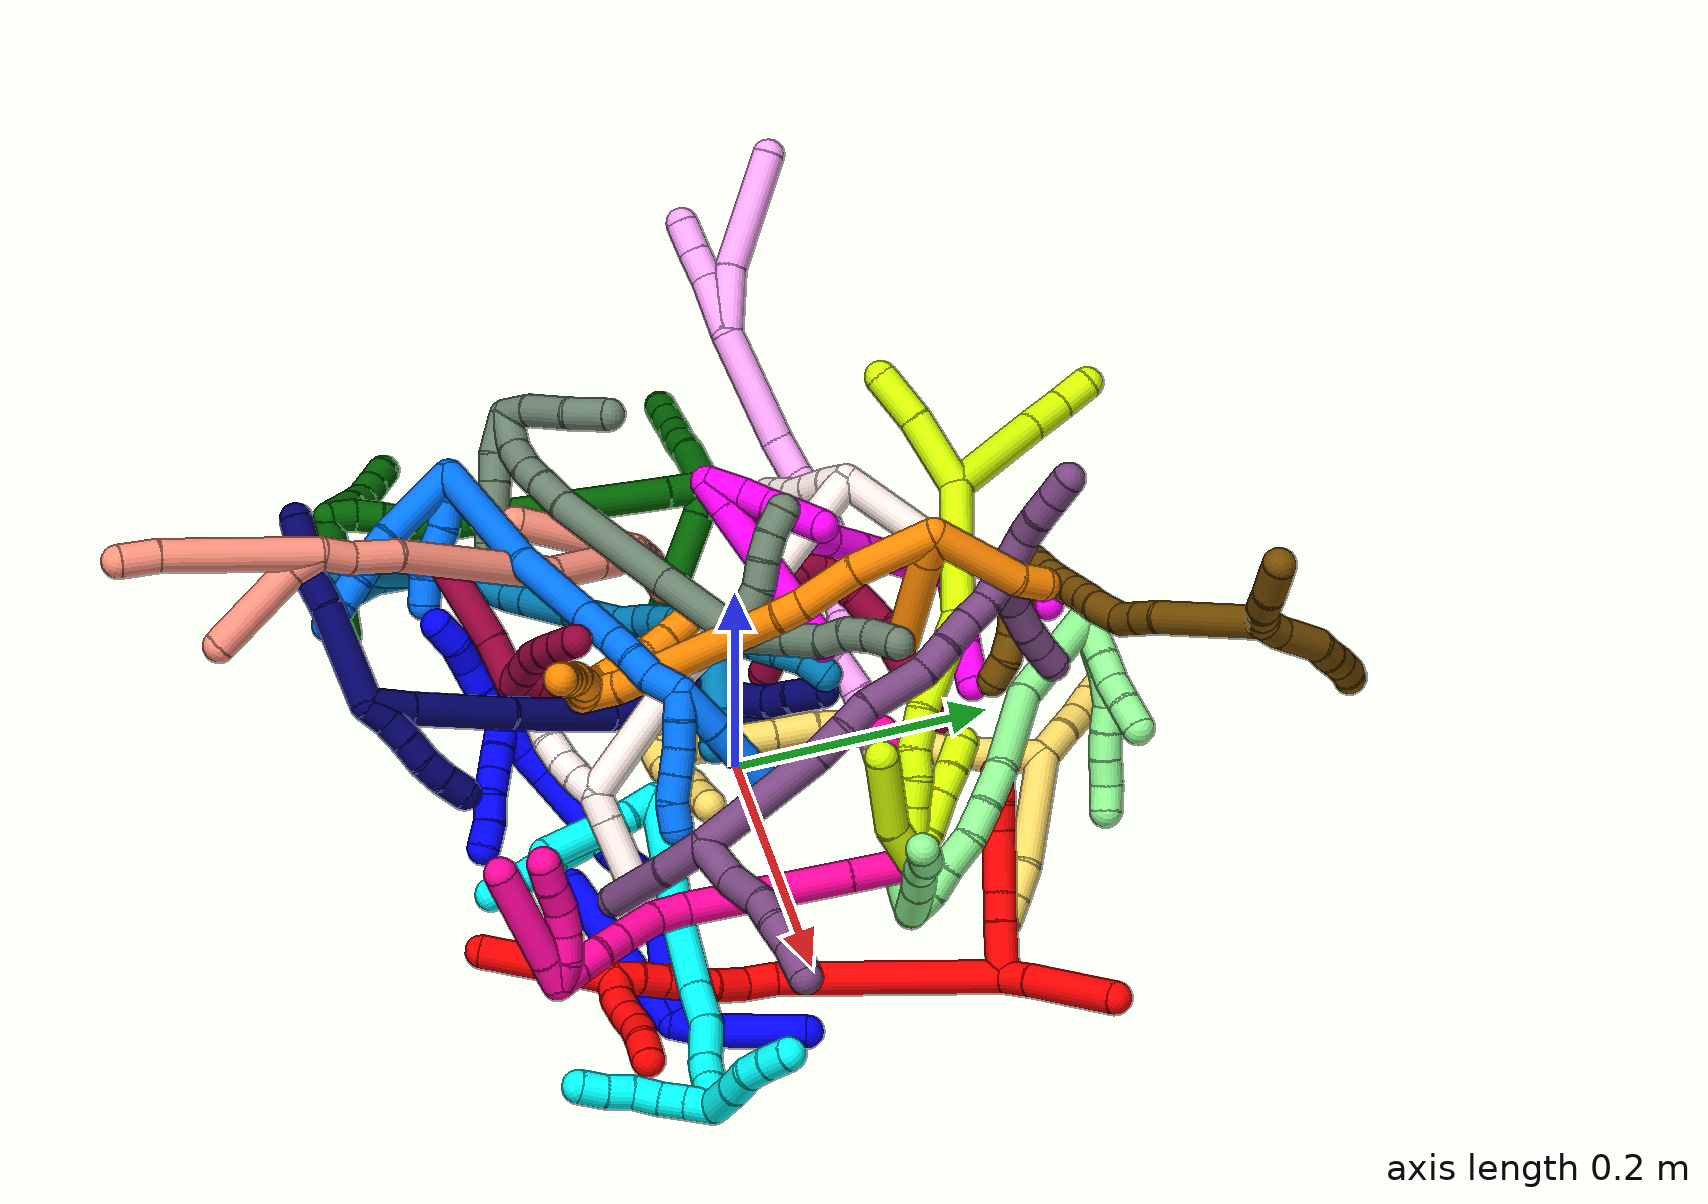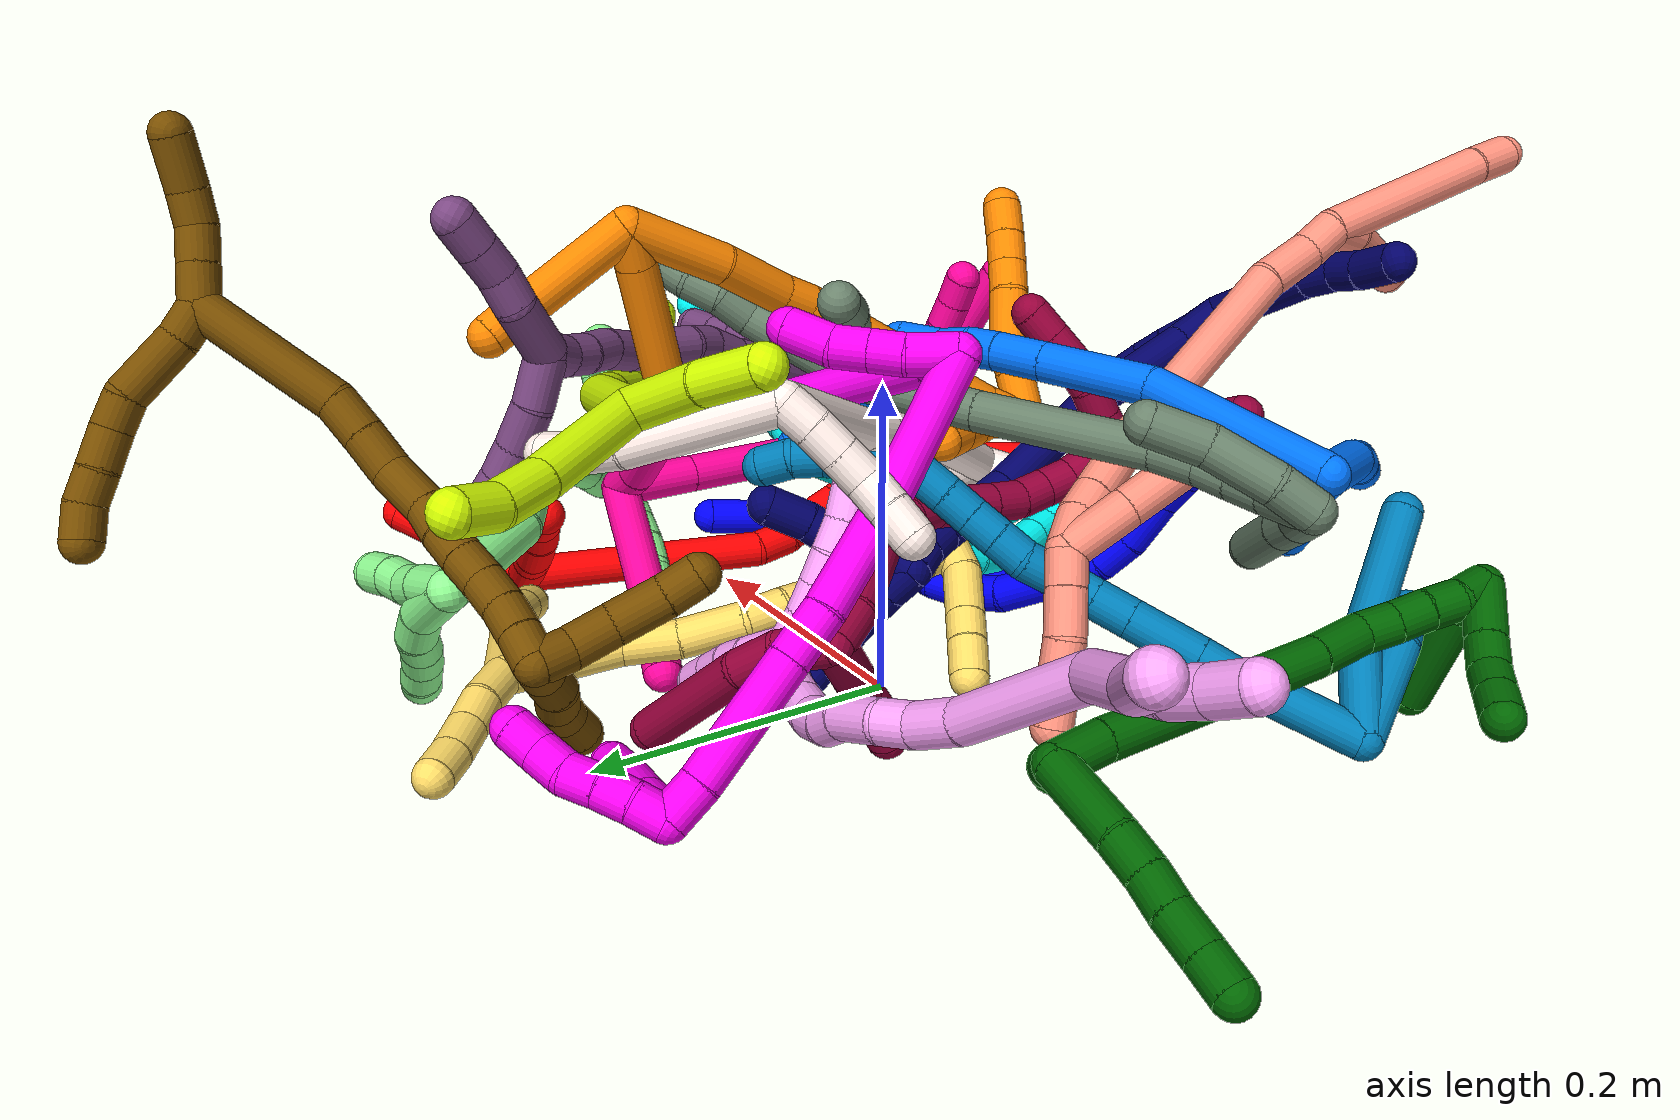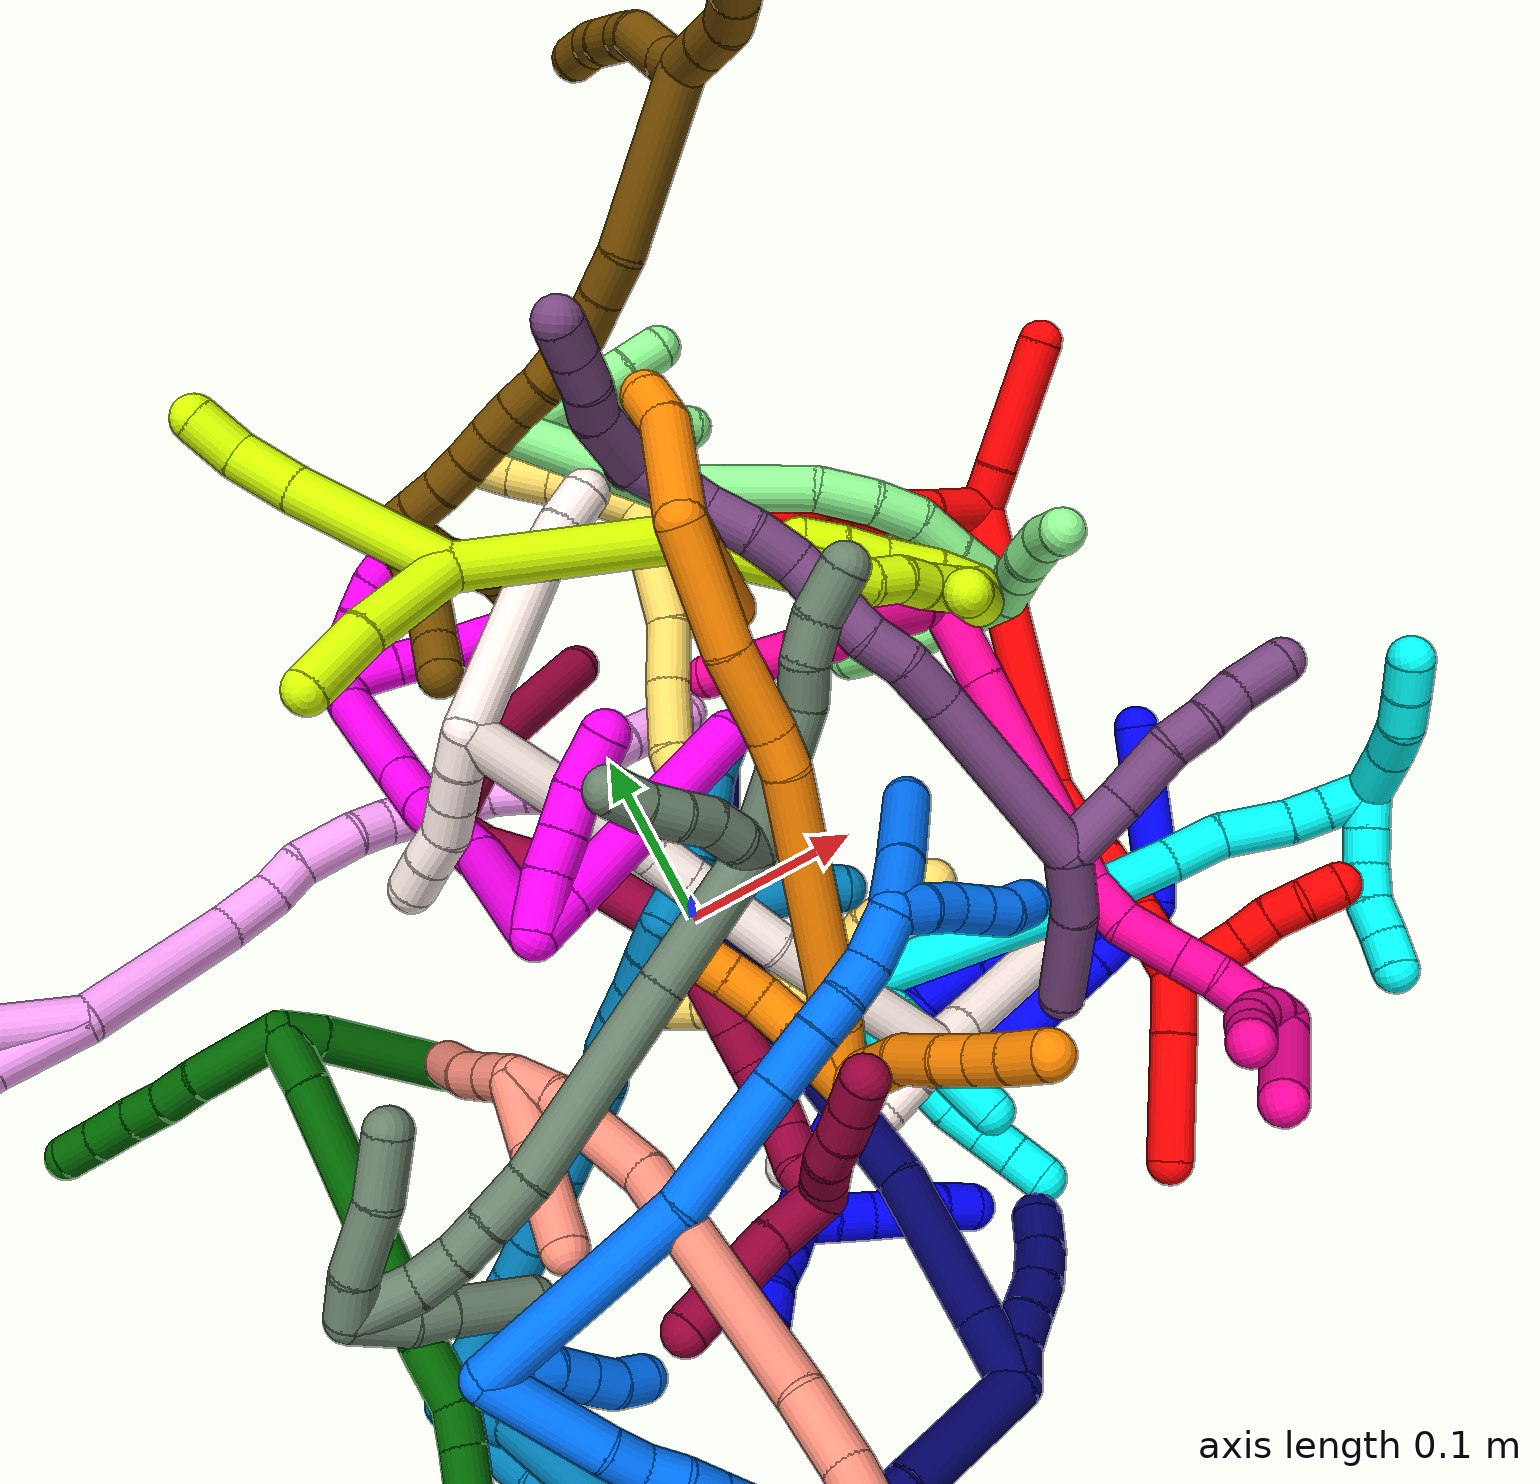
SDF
<sdf version="1.7">
 <world name="default">
  <plugin name="TubeGeneratorPlugin" filename="libtube_generator_plugin.so"/>
  <model name="photoneo_s_sensor">
   <static>1</static>
   <pose>0 0 2 1.57079 1.57079 3.14159</pose>
   <link name="link">
    <inertial><mass>0.1</mass></inertial>
    <sensor name="sensor" type="depth">
     <update_rate>30</update_rate>
     <camera>
      <horizontal_fov>1.22</horizontal_fov>
      <image><width>1920</width><height>1200</height><format>B8G8R8</format></image>
      <clip><near>0.1</near><far>4</far></clip>
      <depth_camera><output>points</output></depth_camera>
     </camera>
     <plugin name="camera_plugin" filename="libgazebo_ros_depth_camera.so">
      <baseline>0.2</baseline>
      <alwaysOn>1</alwaysOn>
      <updateRate>0.0</updateRate>
      <cameraName>camera_ir</cameraName>
      <imageTopicName>/camera/color/image_raw</imageTopicName>
      <cameraInfoTopicName>/camera/color/camera_info</cameraInfoTopicName>
      <depthImageTopicName>/camera/depth/image_raw</depthImageTopicName>
      <depthImageCameraInfoTopicName>/camera/depth/camera_info</depthImageCameraInfoTopicName>
      <pointCloudTopicName>/camera/depth/points</pointCloudTopicName>
      <frameName>fr_optical</frameName>
      <pointCloudCutoff>0.1</pointCloudCutoff>
      <pointCloudCutoffMax>2.0</pointCloudCutoffMax>
      <distortionK1>0</distortionK1>
      <distortionK2>0</distortionK2>
      <distortionK3>0</distortionK3>
      <distortionT1>0</distortionT1>
      <distortionT2>0</distortionT2>
      <CxPrime>0</CxPrime>
      <Cx>0</Cx>
      <Cy>0</Cy>
      <focalLength>0</focalLength>
      <hackBaseline>0</hackBaseline>
     </plugin>
    </sensor>
   </link>
  </model>
  <gravity>0 0 -9.8</gravity>
  <magnetic_field>6e-06 2.3e-05 -4.2e-05</magnetic_field>
  <atmosphere type="adiabatic"/>
  <physics name="default_physics" default="0" type="ode">
   <max_step_size>0.003</max_step_size>
   <real_time_factor>1</real_time_factor>
   <real_time_update_rate>1000</real_time_update_rate>
   <max_contacts>10000</max_contacts>
   <ode>
    <solver>
     <type>quick</type>
     <iters>100</iters>
     <sor>1.3</sor>
     <use_dynamic_moi_rescaling>0</use_dynamic_moi_rescaling>
    </solver>
    <constraints>
     <contact_max_correcting_vel>0</contact_max_correcting_vel>
     <contact_surface_layer>0.001</contact_surface_layer>
     <cfm>0</cfm>
     <erp>0.2</erp>
    </constraints>
   </ode>
  </physics>
  <scene><ambient>0.4 0.4 0.4 1</ambient><background>0.7 0.7 0.7 1</background><shadows>0</shadows></scene>
  <audio><device>default</device></audio>
  <spherical_coordinates>
   <surface_model>EARTH_WGS84</surface_model>
   <latitude_deg>0</latitude_deg>
   <longitude_deg>0</longitude_deg>
   <elevation>0</elevation>
   <heading_deg>0</heading_deg>
  </spherical_coordinates>
  <model name="bin">
   <static>1</static>
   <link name="bottom">
    <collision name="collision-bottom">
     <pose>0 0 -0.01 0 -0 0</pose>
     <geometry><box><size>0.8 0.6 0.02</size></box></geometry>
     <surface>
      <friction><ode><mu>100</mu><mu2>100</mu2></ode></friction>
      <contact><collide_bitmask>65535</collide_bitmask></contact>
     </surface>
    </collision>
   </link>
   <link name="west_wall">
    <collision name="collision-west_wall">
     <pose>-0.41 0 0.1 0 -0 0</pose>
     <geometry><box><size>0.02 0.6 0.2</size></box></geometry>
     <surface>
      <friction><ode><mu>100</mu><mu2>100</mu2></ode></friction>
      <contact><collide_bitmask>65535</collide_bitmask></contact>
     </surface>
    </collision>
   </link>
   <link name="east_wall">
    <collision name="collision-east_wall">
     <pose>0.41 0 0.1 0 -0 0</pose>
     <geometry><box><size>0.02 0.6 0.2</size></box></geometry>
     <surface>
      <friction><ode><mu>100</mu><mu2>100</mu2></ode></friction>
      <contact><collide_bitmask>65535</collide_bitmask></contact>
     </surface>
    </collision>
   </link>
   <link name="south_wall">
    <collision name="collision-south_wall">
     <pose>0 -0.31 0.1 0 -0 0</pose>
     <geometry><box><size>0.8 0.02 0.2</size></box></geometry>
     <surface>
      <friction><ode><mu>100</mu><mu2>100</mu2></ode></friction>
      <contact><collide_bitmask>65535</collide_bitmask></contact>
     </surface>
    </collision>
   </link>
   <link name="north_wall">
    <collision name="collision-north_wall">
     <pose>0 0.31 0.1 0 -0 0</pose>
     <geometry><box><size>0.8 0.02 0.2</size></box></geometry>
     <surface>
      <friction><ode><mu>100</mu><mu2>100</mu2></ode></friction>
      <contact><collide_bitmask>65535</collide_bitmask></contact>
     </surface>
    </collision>
   </link>
  </model>
  <model name="1">
   <static>0</static>
   <link name="1">
    <collision name="collision-cylinder-e_1_2_8">
     <pose>-0.022529 -0.004162 0.000281 1.50346 -1.38773 -1.32192</pose>
     <geometry><cylinder><radius>0.0125</radius><length>0.045823</length></cylinder></geometry>
     <surface>
      <friction><ode><mu>1.16</mu><mu2>1.16</mu2><slip1>0</slip1><slip2>0</slip2></ode></friction>
      <contact><ode><kp>1e+06</kp><kd>1</kd><max_vel>0</max_vel><min_depth>0.001</min_depth></ode></contact>
     </surface>
    </collision>
    <visual name="visual-cylinder-e_1_2_8">
     <pose>-0.022529 -0.004162 0.000281 1.50346 -1.38773 -1.32192</pose>
     <geometry><cylinder><radius>0.0125</radius><length>0.045823</length></cylinder></geometry>
     <material><ambient>0 0 1 1</ambient></material>
    </visual>
    <collision name="collision-cylinder-e_2_8_6">
     <pose>-0.096458 -0.016731 -0.000133 1.65324 -1.40811 -1.49001</pose>
     <geometry><cylinder><radius>0.0125</radius><length>0.104177</length></cylinder></geometry>
     <surface>
      <friction><ode><mu>1.16</mu><mu2>1.16</mu2><slip1>0</slip1><slip2>0</slip2></ode></friction>
      <contact><ode><kp>1e+06</kp><kd>1</kd><max_vel>0</max_vel><min_depth>0.001</min_depth></ode></contact>
     </surface>
    </collision>
    <visual name="visual-cylinder-e_2_8_6">
     <pose>-0.096458 -0.016731 -0.000133 1.65324 -1.40811 -1.49001</pose>
     <geometry><cylinder><radius>0.0125</radius><length>0.104177</length></cylinder></geometry>
     <material><ambient>0 0 1 1</ambient></material>
    </visual>
    <collision name="collision-cylinder-e_1_2_9">
     <pose>0.008943 0.00982 -0.006396 -2.1481 0.651829 -1.11498</pose>
     <geometry><cylinder><radius>0.0125</radius><length>0.029482</length></cylinder></geometry>
     <surface>
      <friction><ode><mu>1.16</mu><mu2>1.16</mu2><slip1>0</slip1><slip2>0</slip2></ode></friction>
      <contact><ode><kp>1e+06</kp><kd>1</kd><max_vel>0</max_vel><min_depth>0.001</min_depth></ode></contact>
     </surface>
    </collision>
    <visual name="visual-cylinder-e_1_2_9">
     <pose>0.008943 0.00982 -0.006396 -2.1481 0.651829 -1.11498</pose>
     <geometry><cylinder><radius>0.0125</radius><length>0.029482</length></cylinder></geometry>
     <material><ambient>0 0 1 1</ambient></material>
    </visual>
    <collision name="collision-cylinder-e_2_9_5">
     <pose>0.033833 0.047378 -0.027604 -2.06127 0.469348 -0.75877</pose>
     <geometry><cylinder><radius>0.0125</radius><length>0.070518</length></cylinder></geometry>
     <surface>
      <friction><ode><mu>1.16</mu><mu2>1.16</mu2><slip1>0</slip1><slip2>0</slip2></ode></friction>
      <contact><ode><kp>1e+06</kp><kd>1</kd><max_vel>0</max_vel><min_depth>0.001</min_depth></ode></contact>
     </surface>
    </collision>
    <visual name="visual-cylinder-e_2_9_5">
     <pose>0.033833 0.047378 -0.027604 -2.06127 0.469348 -0.75877</pose>
     <geometry><cylinder><radius>0.0125</radius><length>0.070518</length></cylinder></geometry>
     <material><ambient>0 0 1 1</ambient></material>
    </visual>
    <collision name="collision-cylinder-e_1_2_10">
     <pose>-0.033212 0.007775 -0.006934 -2.29911 -1.26684 2.04591</pose>
     <geometry><cylinder><radius>0.0125</radius><length>0.069616</length></cylinder></geometry>
     <surface>
      <friction><ode><mu>1.16</mu><mu2>1.16</mu2><slip1>0</slip1><slip2>0</slip2></ode></friction>
      <contact><ode><kp>1e+06</kp><kd>1</kd><max_vel>0</max_vel><min_depth>0.001</min_depth></ode></contact>
     </surface>
    </collision>
    <visual name="visual-cylinder-e_1_2_10">
     <pose>-0.033212 0.007775 -0.006934 -2.29911 -1.26684 2.04591</pose>
     <geometry><cylinder><radius>0.0125</radius><length>0.069616</length></cylinder></geometry>
     <material><ambient>0 0 1 1</ambient></material>
    </visual>
    <collision name="collision-cylinder-e_2_10_11">
     <pose>-0.083585 0.019199 -0.017356 -2.33344 -1.28473 2.1032</pose>
     <geometry><cylinder><radius>0.0125</radius><length>0.035774</length></cylinder></geometry>
     <surface>
      <friction><ode><mu>1.16</mu><mu2>1.16</mu2><slip1>0</slip1><slip2>0</slip2></ode></friction>
      <contact><ode><kp>1e+06</kp><kd>1</kd><max_vel>0</max_vel><min_depth>0.001</min_depth></ode></contact>
     </surface>
    </collision>
    <visual name="visual-cylinder-e_2_10_11">
     <pose>-0.083585 0.019199 -0.017356 -2.33344 -1.28473 2.1032</pose>
     <geometry><cylinder><radius>0.0125</radius><length>0.035774</length></cylinder></geometry>
     <material><ambient>0 0 1 1</ambient></material>
    </visual>
    <collision name="collision-cylinder-e_3_11_12">
     <pose>-0.118895 0.020358 -0.023654 2.41669 -1.36675 -2.26991</pose>
     <geometry><cylinder><radius>0.0125</radius><length>0.037068</length></cylinder></geometry>
     <surface>
      <friction><ode><mu>1.16</mu><mu2>1.16</mu2><slip1>0</slip1><slip2>0</slip2></ode></friction>
      <contact><ode><kp>1e+06</kp><kd>1</kd><max_vel>0</max_vel><min_depth>0.001</min_depth></ode></contact>
     </surface>
    </collision>
    <visual name="visual-cylinder-e_3_11_12">
     <pose>-0.118895 0.020358 -0.023654 2.41669 -1.36675 -2.26991</pose>
     <geometry><cylinder><radius>0.0125</radius><length>0.037068</length></cylinder></geometry>
     <material><ambient>0 0 1 1</ambient></material>
    </visual>
    <collision name="collision-cylinder-e_4_12_13">
     <pose>-0.150417 0.012098 -0.025567 1.41641 -1.15908 -1.0218</pose>
     <geometry><cylinder><radius>0.0125</radius><length>0.029185</length></cylinder></geometry>
     <surface>
      <friction><ode><mu>1.16</mu><mu2>1.16</mu2><slip1>0</slip1><slip2>0</slip2></ode></friction>
      <contact><ode><kp>1e+06</kp><kd>1</kd><max_vel>0</max_vel><min_depth>0.001</min_depth></ode></contact>
     </surface>
    </collision>
    <visual name="visual-cylinder-e_4_12_13">
     <pose>-0.150417 0.012098 -0.025567 1.41641 -1.15908 -1.0218</pose>
     <geometry><cylinder><radius>0.0125</radius><length>0.029185</length></cylinder></geometry>
     <material><ambient>0 0 1 1</ambient></material>
    </visual>
    <collision name="collision-cylinder-e_5_13_14">
     <pose>-0.176233 0.004559 -0.021203 0.471709 -1.26767 -0.349677</pose>
     <geometry><cylinder><radius>0.0125</radius><length>0.026074</length></cylinder></geometry>
     <surface>
      <friction><ode><mu>1.16</mu><mu2>1.16</mu2><slip1>0</slip1><slip2>0</slip2></ode></friction>
      <contact><ode><kp>1e+06</kp><kd>1</kd><max_vel>0</max_vel><min_depth>0.001</min_depth></ode></contact>
     </surface>
    </collision>
    <visual name="visual-cylinder-e_5_13_14">
     <pose>-0.176233 0.004559 -0.021203 0.471709 -1.26767 -0.349677</pose>
     <geometry><cylinder><radius>0.0125</radius><length>0.026074</length></cylinder></geometry>
     <material><ambient>0 0 1 1</ambient></material>
    </visual>
    <collision name="collision-cylinder-e_6_14_15">
     <pose>-0.211501 0.000476 -0.004216 0.16958 -1.02967 -0.096092</pose>
     <geometry><cylinder><radius>0.0125</radius><length>0.053259</length></cylinder></geometry>
     <surface>
      <friction><ode><mu>1.16</mu><mu2>1.16</mu2><slip1>0</slip1><slip2>0</slip2></ode></friction>
      <contact><ode><kp>1e+06</kp><kd>1</kd><max_vel>0</max_vel><min_depth>0.001</min_depth></ode></contact>
     </surface>
    </collision>
    <visual name="visual-cylinder-e_6_14_15">
     <pose>-0.211501 0.000476 -0.004216 0.16958 -1.02967 -0.096092</pose>
     <geometry><cylinder><radius>0.0125</radius><length>0.053259</length></cylinder></geometry>
     <material><ambient>0 0 1 1</ambient></material>
    </visual>
    <collision name="collision-cylinder-e_7_15_16">
     <pose>-0.243531 -0.00251 0.01649 0.093126 -0.905882 -0.045348</pose>
     <geometry><cylinder><radius>0.0125</radius><length>0.023395</length></cylinder></geometry>
     <surface>
      <friction><ode><mu>1.16</mu><mu2>1.16</mu2><slip1>0</slip1><slip2>0</slip2></ode></friction>
      <contact><ode><kp>1e+06</kp><kd>1</kd><max_vel>0</max_vel><min_depth>0.001</min_depth></ode></contact>
     </surface>
    </collision>
    <visual name="visual-cylinder-e_7_15_16">
     <pose>-0.243531 -0.00251 0.01649 0.093126 -0.905882 -0.045348</pose>
     <geometry><cylinder><radius>0.0125</radius><length>0.023395</length></cylinder></geometry>
     <material><ambient>0 0 1 1</ambient></material>
    </visual>
    <collision name="collision-cylinder-e_8_16_1">
     <pose>-0.260879 -0.002385 0.033539 -0.080592 -0.68852 0.028909</pose>
     <geometry><cylinder><radius>0.0125</radius><length>0.025629</length></cylinder></geometry>
     <surface>
      <friction><ode><mu>1.16</mu><mu2>1.16</mu2><slip1>0</slip1><slip2>0</slip2></ode></friction>
      <contact><ode><kp>1e+06</kp><kd>1</kd><max_vel>0</max_vel><min_depth>0.001</min_depth></ode></contact>
     </surface>
    </collision>
    <visual name="visual-cylinder-e_8_16_1">
     <pose>-0.260879 -0.002385 0.033539 -0.080592 -0.68852 0.028909</pose>
     <geometry><cylinder><radius>0.0125</radius><length>0.025629</length></cylinder></geometry>
     <material><ambient>0 0 1 1</ambient></material>
    </visual>
    <collision name="collision-cylinder-e_1_1_17">
     <pose>-0.278454 0.002973 0.058176 -0.299439 -0.547786 0.084712</pose>
     <geometry><cylinder><radius>0.0125</radius><length>0.036225</length></cylinder></geometry>
     <surface>
      <friction><ode><mu>1.16</mu><mu2>1.16</mu2><slip1>0</slip1><slip2>0</slip2></ode></friction>
      <contact><ode><kp>1e+06</kp><kd>1</kd><max_vel>0</max_vel><min_depth>0.001</min_depth></ode></contact>
     </surface>
    </collision>
    <visual name="visual-cylinder-e_1_1_17">
     <pose>-0.278454 0.002973 0.058176 -0.299439 -0.547786 0.084712</pose>
     <geometry><cylinder><radius>0.0125</radius><length>0.036225</length></cylinder></geometry>
     <material><ambient>0 0 1 1</ambient></material>
    </visual>
    <collision name="collision-cylinder-e_2_17_18">
     <pose>-0.294756 0.010151 0.080974 -0.315218 -0.683129 0.112876</pose>
     <geometry><cylinder><radius>0.0125</radius><length>0.021763</length></cylinder></geometry>
     <surface>
      <friction><ode><mu>1.16</mu><mu2>1.16</mu2><slip1>0</slip1><slip2>0</slip2></ode></friction>
      <contact><ode><kp>1e+06</kp><kd>1</kd><max_vel>0</max_vel><min_depth>0.001</min_depth></ode></contact>
     </surface>
    </collision>
    <visual name="visual-cylinder-e_2_17_18">
     <pose>-0.294756 0.010151 0.080974 -0.315218 -0.683129 0.112876</pose>
     <geometry><cylinder><radius>0.0125</radius><length>0.021763</length></cylinder></geometry>
     <material><ambient>0 0 1 1</ambient></material>
    </visual>
    <collision name="collision-cylinder-e_3_18_19">
     <pose>-0.305541 0.015888 0.098092 -0.330553 -0.386881 0.065325</pose>
     <geometry><cylinder><radius>0.0125</radius><length>0.020763</length></cylinder></geometry>
     <surface>
      <friction><ode><mu>1.16</mu><mu2>1.16</mu2><slip1>0</slip1><slip2>0</slip2></ode></friction>
      <contact><ode><kp>1e+06</kp><kd>1</kd><max_vel>0</max_vel><min_depth>0.001</min_depth></ode></contact>
     </surface>
    </collision>
    <visual name="visual-cylinder-e_3_18_19">
     <pose>-0.305541 0.015888 0.098092 -0.330553 -0.386881 0.065325</pose>
     <geometry><cylinder><radius>0.0125</radius><length>0.020763</length></cylinder></geometry>
     <material><ambient>0 0 1 1</ambient></material>
    </visual>
    <collision name="collision-cylinder-e_4_19_4">
     <pose>-0.315362 0.019299 0.116015 -0.032896 -0.589151 0.009982</pose>
     <geometry><cylinder><radius>0.0125</radius><length>0.021249</length></cylinder></geometry>
     <surface>
      <friction><ode><mu>1.16</mu><mu2>1.16</mu2><slip1>0</slip1><slip2>0</slip2></ode></friction>
      <contact><ode><kp>1e+06</kp><kd>1</kd><max_vel>0</max_vel><min_depth>0.001</min_depth></ode></contact>
     </surface>
    </collision>
    <visual name="visual-cylinder-e_4_19_4">
     <pose>-0.315362 0.019299 0.116015 -0.032896 -0.589151 0.009982</pose>
     <geometry><cylinder><radius>0.0125</radius><length>0.021249</length></cylinder></geometry>
     <material><ambient>0 0 1 1</ambient></material>
    </visual>
    <collision name="collision-cylinder-e_1_1_20">
     <pose>-0.260533 -0.00646 0.045457 1.17157 1.01369 0.705897</pose>
     <geometry><cylinder><radius>0.0125</radius><length>0.02</length></cylinder></geometry>
     <surface>
      <friction><ode><mu>1.16</mu><mu2>1.16</mu2><slip1>0</slip1><slip2>0</slip2></ode></friction>
      <contact><ode><kp>1e+06</kp><kd>1</kd><max_vel>0</max_vel><min_depth>0.001</min_depth></ode></contact>
     </surface>
    </collision>
    <visual name="visual-cylinder-e_1_1_20">
     <pose>-0.260533 -0.00646 0.045457 1.17157 1.01369 0.705897</pose>
     <geometry><cylinder><radius>0.0125</radius><length>0.02</length></cylinder></geometry>
     <material><ambient>0 0 1 1</ambient></material>
    </visual>
    <collision name="collision-cylinder-e_2_20_21">
     <pose>-0.243615 -0.01654 0.048856 1.3184 1.00285 0.803274</pose>
     <geometry><cylinder><radius>0.0125</radius><length>0.02</length></cylinder></geometry>
     <surface>
      <friction><ode><mu>1.16</mu><mu2>1.16</mu2><slip1>0</slip1><slip2>0</slip2></ode></friction>
      <contact><ode><kp>1e+06</kp><kd>1</kd><max_vel>0</max_vel><min_depth>0.001</min_depth></ode></contact>
     </surface>
    </collision>
    <visual name="visual-cylinder-e_2_20_21">
     <pose>-0.243615 -0.01654 0.048856 1.3184 1.00285 0.803274</pose>
     <geometry><cylinder><radius>0.0125</radius><length>0.02</length></cylinder></geometry>
     <material><ambient>0 0 1 1</ambient></material>
    </visual>
    <collision name="collision-cylinder-e_3_21_22">
     <pose>-0.226511 -0.026032 0.052731 1.03696 1.0499 0.638274</pose>
     <geometry><cylinder><radius>0.0125</radius><length>0.02</length></cylinder></geometry>
     <surface>
      <friction><ode><mu>1.16</mu><mu2>1.16</mu2><slip1>0</slip1><slip2>0</slip2></ode></friction>
      <contact><ode><kp>1e+06</kp><kd>1</kd><max_vel>0</max_vel><min_depth>0.001</min_depth></ode></contact>
     </surface>
    </collision>
    <visual name="visual-cylinder-e_3_21_22">
     <pose>-0.226511 -0.026032 0.052731 1.03696 1.0499 0.638274</pose>
     <geometry><cylinder><radius>0.0125</radius><length>0.02</length></cylinder></geometry>
     <material><ambient>0 0 1 1</ambient></material>
    </visual>
    <collision name="collision-cylinder-e_4_22_23">
     <pose>-0.209254 -0.035376 0.054413 1.73742 1.03202 1.18151</pose>
     <geometry><cylinder><radius>0.0125</radius><length>0.02</length></cylinder></geometry>
     <surface>
      <friction><ode><mu>1.16</mu><mu2>1.16</mu2><slip1>0</slip1><slip2>0</slip2></ode></friction>
      <contact><ode><kp>1e+06</kp><kd>1</kd><max_vel>0</max_vel><min_depth>0.001</min_depth></ode></contact>
     </surface>
    </collision>
    <visual name="visual-cylinder-e_4_22_23">
     <pose>-0.209254 -0.035376 0.054413 1.73742 1.03202 1.18151</pose>
     <geometry><cylinder><radius>0.0125</radius><length>0.02</length></cylinder></geometry>
     <material><ambient>0 0 1 1</ambient></material>
    </visual>
    <collision name="collision-cylinder-e_5_23_3">
     <pose>-0.19308 -0.046935 0.053931 1.51396 0.86199 0.819625</pose>
     <geometry><cylinder><radius>0.0125</radius><length>0.02</length></cylinder></geometry>
     <surface>
      <friction><ode><mu>1.16</mu><mu2>1.16</mu2><slip1>0</slip1><slip2>0</slip2></ode></friction>
      <contact><ode><kp>1e+06</kp><kd>1</kd><max_vel>0</max_vel><min_depth>0.001</min_depth></ode></contact>
     </surface>
    </collision>
    <visual name="visual-cylinder-e_5_23_3">
     <pose>-0.19308 -0.046935 0.053931 1.51396 0.86199 0.819625</pose>
     <geometry><cylinder><radius>0.0125</radius><length>0.02</length></cylinder></geometry>
     <material><ambient>0 0 1 1</ambient></material>
    </visual>
    <collision name="collision-sphere-3">
     <pose>-0.185488 -0.053434 0.054301 0 -0 0</pose>
     <geometry><sphere><radius>0.0125</radius></sphere></geometry>
     <surface>
      <friction><ode><mu>1.16</mu><mu2>1.16</mu2><slip1>0</slip1><slip2>0</slip2></ode></friction>
      <contact><ode><kp>1e+06</kp><kd>1</kd><max_vel>0</max_vel><min_depth>0.001</min_depth></ode></contact>
     </surface>
    </collision>
    <visual name="visual-sphere-3">
     <pose>-0.185488 -0.053434 0.054301 0 -0 0</pose>
     <geometry><sphere><radius>0.0125</radius></sphere></geometry>
     <material><ambient>0 0 1 1</ambient></material>
    </visual>
    <collision name="collision-sphere-23">
     <pose>-0.200671 -0.040436 0.053562 0 -0 0</pose>
     <geometry><sphere><radius>0.0125</radius></sphere></geometry>
     <surface>
      <friction><ode><mu>1.16</mu><mu2>1.16</mu2><slip1>0</slip1><slip2>0</slip2></ode></friction>
      <contact><ode><kp>1e+06</kp><kd>1</kd><max_vel>0</max_vel><min_depth>0.001</min_depth></ode></contact>
     </surface>
    </collision>
    <visual name="visual-sphere-23">
     <pose>-0.200671 -0.040436 0.053562 0 -0 0</pose>
     <geometry><sphere><radius>0.0125</radius></sphere></geometry>
     <material><ambient>0 0 1 1</ambient></material>
    </visual>
    <collision name="collision-sphere-22">
     <pose>-0.217838 -0.030317 0.055264 0 -0 0</pose>
     <geometry><sphere><radius>0.0125</radius></sphere></geometry>
     <surface>
      <friction><ode><mu>1.16</mu><mu2>1.16</mu2><slip1>0</slip1><slip2>0</slip2></ode></friction>
      <contact><ode><kp>1e+06</kp><kd>1</kd><max_vel>0</max_vel><min_depth>0.001</min_depth></ode></contact>
     </surface>
    </collision>
    <visual name="visual-sphere-22">
     <pose>-0.217838 -0.030317 0.055264 0 -0 0</pose>
     <geometry><sphere><radius>0.0125</radius></sphere></geometry>
     <material><ambient>0 0 1 1</ambient></material>
    </visual>
    <collision name="collision-sphere-21">
     <pose>-0.235185 -0.021748 0.050199 0 -0 0</pose>
     <geometry><sphere><radius>0.0125</radius></sphere></geometry>
     <surface>
      <friction><ode><mu>1.16</mu><mu2>1.16</mu2><slip1>0</slip1><slip2>0</slip2></ode></friction>
      <contact><ode><kp>1e+06</kp><kd>1</kd><max_vel>0</max_vel><min_depth>0.001</min_depth></ode></contact>
     </surface>
    </collision>
    <visual name="visual-sphere-21">
     <pose>-0.235185 -0.021748 0.050199 0 -0 0</pose>
     <geometry><sphere><radius>0.0125</radius></sphere></geometry>
     <material><ambient>0 0 1 1</ambient></material>
    </visual>
    <collision name="collision-sphere-20">
     <pose>-0.252045 -0.011331 0.047513 0 -0 0</pose>
     <geometry><sphere><radius>0.0125</radius></sphere></geometry>
     <surface>
      <friction><ode><mu>1.16</mu><mu2>1.16</mu2><slip1>0</slip1><slip2>0</slip2></ode></friction>
      <contact><ode><kp>1e+06</kp><kd>1</kd><max_vel>0</max_vel><min_depth>0.001</min_depth></ode></contact>
     </surface>
    </collision>
    <visual name="visual-sphere-20">
     <pose>-0.252045 -0.011331 0.047513 0 -0 0</pose>
     <geometry><sphere><radius>0.0125</radius></sphere></geometry>
     <material><ambient>0 0 1 1</ambient></material>
    </visual>
    <collision name="collision-sphere-4">
     <pose>-0.321265 0.019589 0.124843 0 -0 0</pose>
     <geometry><sphere><radius>0.0125</radius></sphere></geometry>
     <surface>
      <friction><ode><mu>1.16</mu><mu2>1.16</mu2><slip1>0</slip1><slip2>0</slip2></ode></friction>
      <contact><ode><kp>1e+06</kp><kd>1</kd><max_vel>0</max_vel><min_depth>0.001</min_depth></ode></contact>
     </surface>
    </collision>
    <visual name="visual-sphere-4">
     <pose>-0.321265 0.019589 0.124843 0 -0 0</pose>
     <geometry><sphere><radius>0.0125</radius></sphere></geometry>
     <material><ambient>0 0 1 1</ambient></material>
    </visual>
    <collision name="collision-sphere-10">
     <pose>-0.066425 0.01555 -0.013869 0 -0 0</pose>
     <geometry><sphere><radius>0.0125</radius></sphere></geometry>
     <surface>
      <friction><ode><mu>1.16</mu><mu2>1.16</mu2><slip1>0</slip1><slip2>0</slip2></ode></friction>
      <contact><ode><kp>1e+06</kp><kd>1</kd><max_vel>0</max_vel><min_depth>0.001</min_depth></ode></contact>
     </surface>
    </collision>
    <visual name="visual-sphere-10">
     <pose>-0.066425 0.01555 -0.013869 0 -0 0</pose>
     <geometry><sphere><radius>0.0125</radius></sphere></geometry>
     <material><ambient>0 0 1 1</ambient></material>
    </visual>
    <collision name="collision-sphere-5">
     <pose>0.049781 0.075117 -0.042417 0 -0 0</pose>
     <geometry><sphere><radius>0.0125</radius></sphere></geometry>
     <surface>
      <friction><ode><mu>1.16</mu><mu2>1.16</mu2><slip1>0</slip1><slip2>0</slip2></ode></friction>
      <contact><ode><kp>1e+06</kp><kd>1</kd><max_vel>0</max_vel><min_depth>0.001</min_depth></ode></contact>
     </surface>
    </collision>
    <visual name="visual-sphere-5">
     <pose>0.049781 0.075117 -0.042417 0 -0 0</pose>
     <geometry><sphere><radius>0.0125</radius></sphere></geometry>
     <material><ambient>0 0 1 1</ambient></material>
    </visual>
    <collision name="collision-sphere-6">
     <pose>-0.147859 -0.02514 -0.000828 0 -0 0</pose>
     <geometry><sphere><radius>0.0125</radius></sphere></geometry>
     <surface>
      <friction><ode><mu>1.16</mu><mu2>1.16</mu2><slip1>0</slip1><slip2>0</slip2></ode></friction>
      <contact><ode><kp>1e+06</kp><kd>1</kd><max_vel>0</max_vel><min_depth>0.001</min_depth></ode></contact>
     </surface>
    </collision>
    <visual name="visual-sphere-6">
     <pose>-0.147859 -0.02514 -0.000828 0 -0 0</pose>
     <geometry><sphere><radius>0.0125</radius></sphere></geometry>
     <material><ambient>0 0 1 1</ambient></material>
    </visual>
    <collision name="collision-sphere-9">
     <pose>0.017885 0.019639 -0.012792 0 -0 0</pose>
     <geometry><sphere><radius>0.0125</radius></sphere></geometry>
     <surface>
      <friction><ode><mu>1.16</mu><mu2>1.16</mu2><slip1>0</slip1><slip2>0</slip2></ode></friction>
      <contact><ode><kp>1e+06</kp><kd>1</kd><max_vel>0</max_vel><min_depth>0.001</min_depth></ode></contact>
     </surface>
    </collision>
    <visual name="visual-sphere-9">
     <pose>0.017885 0.019639 -0.012792 0 -0 0</pose>
     <geometry><sphere><radius>0.0125</radius></sphere></geometry>
     <material><ambient>0 0 1 1</ambient></material>
    </visual>
    <collision name="collision-sphere-2">
     <geometry><sphere><radius>0.0125</radius></sphere></geometry>
     <surface>
      <friction><ode><mu>1.16</mu><mu2>1.16</mu2><slip1>0</slip1><slip2>0</slip2></ode></friction>
      <contact><ode><kp>1e+06</kp><kd>1</kd><max_vel>0</max_vel><min_depth>0.001</min_depth></ode></contact>
     </surface>
    </collision>
    <visual name="visual-sphere-2">
     <geometry><sphere><radius>0.0125</radius></sphere></geometry>
     <material><ambient>0 0 1 1</ambient></material>
    </visual>
    <collision name="collision-sphere-19">
     <pose>-0.309458 0.019008 0.107186 0 -0 0</pose>
     <geometry><sphere><radius>0.0125</radius></sphere></geometry>
     <surface>
      <friction><ode><mu>1.16</mu><mu2>1.16</mu2><slip1>0</slip1><slip2>0</slip2></ode></friction>
      <contact><ode><kp>1e+06</kp><kd>1</kd><max_vel>0</max_vel><min_depth>0.001</min_depth></ode></contact>
     </surface>
    </collision>
    <visual name="visual-sphere-19">
     <pose>-0.309458 0.019008 0.107186 0 -0 0</pose>
     <geometry><sphere><radius>0.0125</radius></sphere></geometry>
     <material><ambient>0 0 1 1</ambient></material>
    </visual>
    <collision name="collision-sphere-8">
     <pose>-0.045057 -0.008323 0.000561 0 -0 0</pose>
     <geometry><sphere><radius>0.0125</radius></sphere></geometry>
     <surface>
      <friction><ode><mu>1.16</mu><mu2>1.16</mu2><slip1>0</slip1><slip2>0</slip2></ode></friction>
      <contact><ode><kp>1e+06</kp><kd>1</kd><max_vel>0</max_vel><min_depth>0.001</min_depth></ode></contact>
     </surface>
    </collision>
    <visual name="visual-sphere-8">
     <pose>-0.045057 -0.008323 0.000561 0 -0 0</pose>
     <geometry><sphere><radius>0.0125</radius></sphere></geometry>
     <material><ambient>0 0 1 1</ambient></material>
    </visual>
    <collision name="collision-sphere-11">
     <pose>-0.100745 0.022849 -0.020842 0 -0 0</pose>
     <geometry><sphere><radius>0.0125</radius></sphere></geometry>
     <surface>
      <friction><ode><mu>1.16</mu><mu2>1.16</mu2><slip1>0</slip1><slip2>0</slip2></ode></friction>
      <contact><ode><kp>1e+06</kp><kd>1</kd><max_vel>0</max_vel><min_depth>0.001</min_depth></ode></contact>
     </surface>
    </collision>
    <visual name="visual-sphere-11">
     <pose>-0.100745 0.022849 -0.020842 0 -0 0</pose>
     <geometry><sphere><radius>0.0125</radius></sphere></geometry>
     <material><ambient>0 0 1 1</ambient></material>
    </visual>
    <collision name="collision-sphere-12">
     <pose>-0.137044 0.017868 -0.026465 0 -0 0</pose>
     <geometry><sphere><radius>0.0125</radius></sphere></geometry>
     <surface>
      <friction><ode><mu>1.16</mu><mu2>1.16</mu2><slip1>0</slip1><slip2>0</slip2></ode></friction>
      <contact><ode><kp>1e+06</kp><kd>1</kd><max_vel>0</max_vel><min_depth>0.001</min_depth></ode></contact>
     </surface>
    </collision>
    <visual name="visual-sphere-12">
     <pose>-0.137044 0.017868 -0.026465 0 -0 0</pose>
     <geometry><sphere><radius>0.0125</radius></sphere></geometry>
     <material><ambient>0 0 1 1</ambient></material>
    </visual>
    <collision name="collision-sphere-13">
     <pose>-0.16379 0.006328 -0.024669 0 -0 0</pose>
     <geometry><sphere><radius>0.0125</radius></sphere></geometry>
     <surface>
      <friction><ode><mu>1.16</mu><mu2>1.16</mu2><slip1>0</slip1><slip2>0</slip2></ode></friction>
      <contact><ode><kp>1e+06</kp><kd>1</kd><max_vel>0</max_vel><min_depth>0.001</min_depth></ode></contact>
     </surface>
    </collision>
    <visual name="visual-sphere-13">
     <pose>-0.16379 0.006328 -0.024669 0 -0 0</pose>
     <geometry><sphere><radius>0.0125</radius></sphere></geometry>
     <material><ambient>0 0 1 1</ambient></material>
    </visual>
    <collision name="collision-sphere-14">
     <pose>-0.188676 0.002791 -0.017736 0 -0 0</pose>
     <geometry><sphere><radius>0.0125</radius></sphere></geometry>
     <surface>
      <friction><ode><mu>1.16</mu><mu2>1.16</mu2><slip1>0</slip1><slip2>0</slip2></ode></friction>
      <contact><ode><kp>1e+06</kp><kd>1</kd><max_vel>0</max_vel><min_depth>0.001</min_depth></ode></contact>
     </surface>
    </collision>
    <visual name="visual-sphere-14">
     <pose>-0.188676 0.002791 -0.017736 0 -0 0</pose>
     <geometry><sphere><radius>0.0125</radius></sphere></geometry>
     <material><ambient>0 0 1 1</ambient></material>
    </visual>
    <collision name="collision-sphere-15">
     <pose>-0.234325 -0.001839 0.009304 0 -0 0</pose>
     <geometry><sphere><radius>0.0125</radius></sphere></geometry>
     <surface>
      <friction><ode><mu>1.16</mu><mu2>1.16</mu2><slip1>0</slip1><slip2>0</slip2></ode></friction>
      <contact><ode><kp>1e+06</kp><kd>1</kd><max_vel>0</max_vel><min_depth>0.001</min_depth></ode></contact>
     </surface>
    </collision>
    <visual name="visual-sphere-15">
     <pose>-0.234325 -0.001839 0.009304 0 -0 0</pose>
     <geometry><sphere><radius>0.0125</radius></sphere></geometry>
     <material><ambient>0 0 1 1</ambient></material>
    </visual>
    <collision name="collision-sphere-16">
     <pose>-0.252737 -0.003181 0.023676 0 -0 0</pose>
     <geometry><sphere><radius>0.0125</radius></sphere></geometry>
     <surface>
      <friction><ode><mu>1.16</mu><mu2>1.16</mu2><slip1>0</slip1><slip2>0</slip2></ode></friction>
      <contact><ode><kp>1e+06</kp><kd>1</kd><max_vel>0</max_vel><min_depth>0.001</min_depth></ode></contact>
     </surface>
    </collision>
    <visual name="visual-sphere-16">
     <pose>-0.252737 -0.003181 0.023676 0 -0 0</pose>
     <geometry><sphere><radius>0.0125</radius></sphere></geometry>
     <material><ambient>0 0 1 1</ambient></material>
    </visual>
    <collision name="collision-sphere-1">
     <pose>-0.269021 -0.001588 0.043402 0 -0 0</pose>
     <geometry><sphere><radius>0.0125</radius></sphere></geometry>
     <surface>
      <friction><ode><mu>1.16</mu><mu2>1.16</mu2><slip1>0</slip1><slip2>0</slip2></ode></friction>
      <contact><ode><kp>1e+06</kp><kd>1</kd><max_vel>0</max_vel><min_depth>0.001</min_depth></ode></contact>
     </surface>
    </collision>
    <visual name="visual-sphere-1">
     <pose>-0.269021 -0.001588 0.043402 0 -0 0</pose>
     <geometry><sphere><radius>0.0125</radius></sphere></geometry>
     <material><ambient>0 0 1 1</ambient></material>
    </visual>
    <collision name="collision-sphere-18">
     <pose>-0.301624 0.012767 0.088998 0 -0 0</pose>
     <geometry><sphere><radius>0.0125</radius></sphere></geometry>
     <surface>
      <friction><ode><mu>1.16</mu><mu2>1.16</mu2><slip1>0</slip1><slip2>0</slip2></ode></friction>
      <contact><ode><kp>1e+06</kp><kd>1</kd><max_vel>0</max_vel><min_depth>0.001</min_depth></ode></contact>
     </surface>
    </collision>
    <visual name="visual-sphere-18">
     <pose>-0.301624 0.012767 0.088998 0 -0 0</pose>
     <geometry><sphere><radius>0.0125</radius></sphere></geometry>
     <material><ambient>0 0 1 1</ambient></material>
    </visual>
    <collision name="collision-sphere-17">
     <pose>-0.287887 0.007534 0.07295 0 -0 0</pose>
     <geometry><sphere><radius>0.0125</radius></sphere></geometry>
     <surface>
      <friction><ode><mu>1.16</mu><mu2>1.16</mu2><slip1>0</slip1><slip2>0</slip2></ode></friction>
      <contact><ode><kp>1e+06</kp><kd>1</kd><max_vel>0</max_vel><min_depth>0.001</min_depth></ode></contact>
     </surface>
    </collision>
    <visual name="visual-sphere-17">
     <pose>-0.287887 0.007534 0.07295 0 -0 0</pose>
     <geometry><sphere><radius>0.0125</radius></sphere></geometry>
     <material><ambient>0 0 1 1</ambient></material>
    </visual>
    <inertial>
     <pose>-0.137307 0.003332 0.012113 0 -0 0</pose>
     <mass>0.75</mass>
     <inertia>
      <ixx>-1.5e-05</ixx>
      <ixy>0</ixy>
      <ixz>0</ixz>
      <iyy>0.000155</iyy>
      <iyz>0</iyz>
      <izz>0.000145</izz>
     </inertia>
    </inertial>
   </link>
   <pose>0.229656 -0.116066 0.012471 0.641804 0.099299 0.114296</pose>
  </model>
  <model name="2">
   <static>0</static>
   <link name="2">
    <collision name="collision-cylinder-e_1_2_8">
     <pose>-0.006669 0.012753 -0.014196 -2.40967 -0.336212 0.83377</pose>
     <geometry><cylinder><radius>0.0125</radius><length>0.04043</length></cylinder></geometry>
     <surface>
      <friction><ode><mu>1.16</mu><mu2>1.16</mu2><slip1>0</slip1><slip2>0</slip2></ode></friction>
      <contact><ode><kp>1e+06</kp><kd>1</kd><max_vel>0</max_vel><min_depth>0.001</min_depth></ode></contact>
     </surface>
    </collision>
    <visual name="visual-cylinder-e_1_2_8">
     <pose>-0.006669 0.012753 -0.014196 -2.40967 -0.336212 0.83377</pose>
     <geometry><cylinder><radius>0.0125</radius><length>0.04043</length></cylinder></geometry>
     <material><ambient>1 0 0 1</ambient></material>
    </visual>
    <collision name="collision-cylinder-e_2_8_9">
     <pose>-0.016239 0.032765 -0.035764 -2.364 -0.273383 0.647894</pose>
     <geometry><cylinder><radius>0.0125</radius><length>0.02149</length></cylinder></geometry>
     <surface>
      <friction><ode><mu>1.16</mu><mu2>1.16</mu2><slip1>0</slip1><slip2>0</slip2></ode></friction>
      <contact><ode><kp>1e+06</kp><kd>1</kd><max_vel>0</max_vel><min_depth>0.001</min_depth></ode></contact>
     </surface>
    </collision>
    <visual name="visual-cylinder-e_2_8_9">
     <pose>-0.016239 0.032765 -0.035764 -2.364 -0.273383 0.647894</pose>
     <geometry><cylinder><radius>0.0125</radius><length>0.02149</length></cylinder></geometry>
     <material><ambient>1 0 0 1</ambient></material>
    </visual>
    <collision name="collision-cylinder-e_3_9_10">
     <pose>-0.027135 0.055095 -0.058893 -2.37839 -0.351425 0.833123</pose>
     <geometry><cylinder><radius>0.0125</radius><length>0.046447</length></cylinder></geometry>
     <surface>
      <friction><ode><mu>1.16</mu><mu2>1.16</mu2><slip1>0</slip1><slip2>0</slip2></ode></friction>
      <contact><ode><kp>1e+06</kp><kd>1</kd><max_vel>0</max_vel><min_depth>0.001</min_depth></ode></contact>
     </surface>
    </collision>
    <visual name="visual-cylinder-e_3_9_10">
     <pose>-0.027135 0.055095 -0.058893 -2.37839 -0.351425 0.833123</pose>
     <geometry><cylinder><radius>0.0125</radius><length>0.046447</length></cylinder></geometry>
     <material><ambient>1 0 0 1</ambient></material>
    </visual>
    <collision name="collision-cylinder-e_4_10_11">
     <pose>-0.040375 0.076419 -0.080661 -2.33662 -0.543874 1.15974</pose>
     <geometry><cylinder><radius>0.0125</radius><length>0.020275</length></cylinder></geometry>
     <surface>
      <friction><ode><mu>1.16</mu><mu2>1.16</mu2><slip1>0</slip1><slip2>0</slip2></ode></friction>
      <contact><ode><kp>1e+06</kp><kd>1</kd><max_vel>0</max_vel><min_depth>0.001</min_depth></ode></contact>
     </surface>
    </collision>
    <visual name="visual-cylinder-e_4_10_11">
     <pose>-0.040375 0.076419 -0.080661 -2.33662 -0.543874 1.15974</pose>
     <geometry><cylinder><radius>0.0125</radius><length>0.020275</length></cylinder></geometry>
     <material><ambient>1 0 0 1</ambient></material>
    </visual>
    <collision name="collision-cylinder-e_5_11_6">
     <pose>-0.049199 0.08928 -0.094263 -2.42522 -0.341697 0.863766</pose>
     <geometry><cylinder><radius>0.0125</radius><length>0.021359</length></cylinder></geometry>
     <surface>
      <friction><ode><mu>1.16</mu><mu2>1.16</mu2><slip1>0</slip1><slip2>0</slip2></ode></friction>
      <contact><ode><kp>1e+06</kp><kd>1</kd><max_vel>0</max_vel><min_depth>0.001</min_depth></ode></contact>
     </surface>
    </collision>
    <visual name="visual-cylinder-e_5_11_6">
     <pose>-0.049199 0.08928 -0.094263 -2.42522 -0.341697 0.863766</pose>
     <geometry><cylinder><radius>0.0125</radius><length>0.021359</length></cylinder></geometry>
     <material><ambient>1 0 0 1</ambient></material>
    </visual>
    <collision name="collision-cylinder-e_1_2_12">
     <pose>-0.006235 0.004633 0.010251 -0.424464 -0.506091 0.111325</pose>
     <geometry><cylinder><radius>0.0125</radius><length>0.025724</length></cylinder></geometry>
     <surface>
      <friction><ode><mu>1.16</mu><mu2>1.16</mu2><slip1>0</slip1><slip2>0</slip2></ode></friction>
      <contact><ode><kp>1e+06</kp><kd>1</kd><max_vel>0</max_vel><min_depth>0.001</min_depth></ode></contact>
     </surface>
    </collision>
    <visual name="visual-cylinder-e_1_2_12">
     <pose>-0.006235 0.004633 0.010251 -0.424464 -0.506091 0.111325</pose>
     <geometry><cylinder><radius>0.0125</radius><length>0.025724</length></cylinder></geometry>
     <material><ambient>1 0 0 1</ambient></material>
    </visual>
    <collision name="collision-cylinder-e_2_12_5">
     <pose>-0.028146 0.022216 0.05158 -0.394822 -0.435758 0.088507</pose>
     <geometry><cylinder><radius>0.0125</radius><length>0.074276</length></cylinder></geometry>
     <surface>
      <friction><ode><mu>1.16</mu><mu2>1.16</mu2><slip1>0</slip1><slip2>0</slip2></ode></friction>
      <contact><ode><kp>1e+06</kp><kd>1</kd><max_vel>0</max_vel><min_depth>0.001</min_depth></ode></contact>
     </surface>
    </collision>
    <visual name="visual-cylinder-e_2_12_5">
     <pose>-0.028146 0.022216 0.05158 -0.394822 -0.435758 0.088507</pose>
     <geometry><cylinder><radius>0.0125</radius><length>0.074276</length></cylinder></geometry>
     <material><ambient>1 0 0 1</ambient></material>
    </visual>
    <collision name="collision-cylinder-e_1_2_13">
     <pose>-0.005308 -0.061246 -0.056905 2.31948 -0.063409 -0.145264</pose>
     <geometry><cylinder><radius>0.0125</radius><length>0.16754</length></cylinder></geometry>
     <surface>
      <friction><ode><mu>1.16</mu><mu2>1.16</mu2><slip1>0</slip1><slip2>0</slip2></ode></friction>
      <contact><ode><kp>1e+06</kp><kd>1</kd><max_vel>0</max_vel><min_depth>0.001</min_depth></ode></contact>
     </surface>
    </collision>
    <visual name="visual-cylinder-e_1_2_13">
     <pose>-0.005308 -0.061246 -0.056905 2.31948 -0.063409 -0.145264</pose>
     <geometry><cylinder><radius>0.0125</radius><length>0.16754</length></cylinder></geometry>
     <material><ambient>1 0 0 1</ambient></material>
    </visual>
    <collision name="collision-cylinder-e_2_13_14">
     <pose>-0.014191 -0.133314 -0.119618 2.06324 -0.283221 -0.467836</pose>
     <geometry><cylinder><radius>0.0125</radius><length>0.025584</length></cylinder></geometry>
     <surface>
      <friction><ode><mu>1.16</mu><mu2>1.16</mu2><slip1>0</slip1><slip2>0</slip2></ode></friction>
      <contact><ode><kp>1e+06</kp><kd>1</kd><max_vel>0</max_vel><min_depth>0.001</min_depth></ode></contact>
     </surface>
    </collision>
    <visual name="visual-cylinder-e_2_13_14">
     <pose>-0.014191 -0.133314 -0.119618 2.06324 -0.283221 -0.467836</pose>
     <geometry><cylinder><radius>0.0125</radius><length>0.025584</length></cylinder></geometry>
     <material><ambient>1 0 0 1</ambient></material>
    </visual>
    <collision name="collision-cylinder-e_3_14_15">
     <pose>-0.024886 -0.15379 -0.130378 2.04489 -0.580742 -0.909922</pose>
     <geometry><cylinder><radius>0.0125</radius><length>0.025953</length></cylinder></geometry>
     <surface>
      <friction><ode><mu>1.16</mu><mu2>1.16</mu2><slip1>0</slip1><slip2>0</slip2></ode></friction>
      <contact><ode><kp>1e+06</kp><kd>1</kd><max_vel>0</max_vel><min_depth>0.001</min_depth></ode></contact>
     </surface>
    </collision>
    <visual name="visual-cylinder-e_3_14_15">
     <pose>-0.024886 -0.15379 -0.130378 2.04489 -0.580742 -0.909922</pose>
     <geometry><cylinder><radius>0.0125</radius><length>0.025953</length></cylinder></geometry>
     <material><ambient>1 0 0 1</ambient></material>
    </visual>
    <collision name="collision-cylinder-e_4_15_16">
     <pose>-0.037216 -0.170438 -0.140708 2.22611 -0.533512 -1.01289</pose>
     <geometry><cylinder><radius>0.0125</radius><length>0.020494</length></cylinder></geometry>
     <surface>
      <friction><ode><mu>1.16</mu><mu2>1.16</mu2><slip1>0</slip1><slip2>0</slip2></ode></friction>
      <contact><ode><kp>1e+06</kp><kd>1</kd><max_vel>0</max_vel><min_depth>0.001</min_depth></ode></contact>
     </surface>
    </collision>
    <visual name="visual-cylinder-e_4_15_16">
     <pose>-0.037216 -0.170438 -0.140708 2.22611 -0.533512 -1.01289</pose>
     <geometry><cylinder><radius>0.0125</radius><length>0.020494</length></cylinder></geometry>
     <material><ambient>1 0 0 1</ambient></material>
    </visual>
    <collision name="collision-cylinder-e_5_16_17">
     <pose>-0.047677 -0.184344 -0.15147 2.23282 -0.539836 -1.03068</pose>
     <geometry><cylinder><radius>0.0125</radius><length>0.020427</length></cylinder></geometry>
     <surface>
      <friction><ode><mu>1.16</mu><mu2>1.16</mu2><slip1>0</slip1><slip2>0</slip2></ode></friction>
      <contact><ode><kp>1e+06</kp><kd>1</kd><max_vel>0</max_vel><min_depth>0.001</min_depth></ode></contact>
     </surface>
    </collision>
    <visual name="visual-cylinder-e_5_16_17">
     <pose>-0.047677 -0.184344 -0.15147 2.23282 -0.539836 -1.03068</pose>
     <geometry><cylinder><radius>0.0125</radius><length>0.020427</length></cylinder></geometry>
     <material><ambient>1 0 0 1</ambient></material>
    </visual>
    <collision name="collision-cylinder-e_6_17_18">
     <pose>-0.058082 -0.19801 -0.162126 2.2333 -0.541613 -1.03418</pose>
     <geometry><cylinder><radius>0.0125</radius><length>0.020001</length></cylinder></geometry>
     <surface>
      <friction><ode><mu>1.16</mu><mu2>1.16</mu2><slip1>0</slip1><slip2>0</slip2></ode></friction>
      <contact><ode><kp>1e+06</kp><kd>1</kd><max_vel>0</max_vel><min_depth>0.001</min_depth></ode></contact>
     </surface>
    </collision>
    <visual name="visual-cylinder-e_6_17_18">
     <pose>-0.058082 -0.19801 -0.162126 2.2333 -0.541613 -1.03418</pose>
     <geometry><cylinder><radius>0.0125</radius><length>0.020001</length></cylinder></geometry>
     <material><ambient>1 0 0 1</ambient></material>
    </visual>
    <collision name="collision-cylinder-e_7_18_1">
     <pose>-0.067608 -0.212022 -0.172713 2.20314 -0.452294 -0.852051</pose>
     <geometry><cylinder><radius>0.0125</radius><length>0.02</length></cylinder></geometry>
     <surface>
      <friction><ode><mu>1.16</mu><mu2>1.16</mu2><slip1>0</slip1><slip2>0</slip2></ode></friction>
      <contact><ode><kp>1e+06</kp><kd>1</kd><max_vel>0</max_vel><min_depth>0.001</min_depth></ode></contact>
     </surface>
    </collision>
    <visual name="visual-cylinder-e_7_18_1">
     <pose>-0.067608 -0.212022 -0.172713 2.20314 -0.452294 -0.852051</pose>
     <geometry><cylinder><radius>0.0125</radius><length>0.02</length></cylinder></geometry>
     <material><ambient>1 0 0 1</ambient></material>
    </visual>
    <collision name="collision-cylinder-e_1_1_19">
     <pose>-0.071942 -0.227997 -0.191808 2.57741 0.002274 0.007845</pose>
     <geometry><cylinder><radius>0.0125</radius><length>0.032611</length></cylinder></geometry>
     <surface>
      <friction><ode><mu>1.16</mu><mu2>1.16</mu2><slip1>0</slip1><slip2>0</slip2></ode></friction>
      <contact><ode><kp>1e+06</kp><kd>1</kd><max_vel>0</max_vel><min_depth>0.001</min_depth></ode></contact>
     </surface>
    </collision>
    <visual name="visual-cylinder-e_1_1_19">
     <pose>-0.071942 -0.227997 -0.191808 2.57741 0.002274 0.007845</pose>
     <geometry><cylinder><radius>0.0125</radius><length>0.032611</length></cylinder></geometry>
     <material><ambient>1 0 0 1</ambient></material>
    </visual>
    <collision name="collision-cylinder-e_2_19_4">
     <pose>-0.070526 -0.254904 -0.233917 2.57086 0.040936 0.139329</pose>
     <geometry><cylinder><radius>0.0125</radius><length>0.067389</length></cylinder></geometry>
     <surface>
      <friction><ode><mu>1.16</mu><mu2>1.16</mu2><slip1>0</slip1><slip2>0</slip2></ode></friction>
      <contact><ode><kp>1e+06</kp><kd>1</kd><max_vel>0</max_vel><min_depth>0.001</min_depth></ode></contact>
     </surface>
    </collision>
    <visual name="visual-cylinder-e_2_19_4">
     <pose>-0.070526 -0.254904 -0.233917 2.57086 0.040936 0.139329</pose>
     <geometry><cylinder><radius>0.0125</radius><length>0.067389</length></cylinder></geometry>
     <material><ambient>1 0 0 1</ambient></material>
    </visual>
    <collision name="collision-cylinder-e_1_1_20">
     <pose>-0.075205 -0.22458 -0.170189 0.594657 -0.32848 -0.101478</pose>
     <geometry><cylinder><radius>0.0125</radius><length>0.02</length></cylinder></geometry>
     <surface>
      <friction><ode><mu>1.16</mu><mu2>1.16</mu2><slip1>0</slip1><slip2>0</slip2></ode></friction>
      <contact><ode><kp>1e+06</kp><kd>1</kd><max_vel>0</max_vel><min_depth>0.001</min_depth></ode></contact>
     </surface>
    </collision>
    <visual name="visual-cylinder-e_1_1_20">
     <pose>-0.075205 -0.22458 -0.170189 0.594657 -0.32848 -0.101478</pose>
     <geometry><cylinder><radius>0.0125</radius><length>0.02</length></cylinder></geometry>
     <material><ambient>1 0 0 1</ambient></material>
    </visual>
    <collision name="collision-cylinder-e_2_20_21">
     <pose>-0.082887 -0.232649 -0.153834 0.31417 -0.461917 -0.074458</pose>
     <geometry><cylinder><radius>0.0125</radius><length>0.02</length></cylinder></geometry>
     <surface>
      <friction><ode><mu>1.16</mu><mu2>1.16</mu2><slip1>0</slip1><slip2>0</slip2></ode></friction>
      <contact><ode><kp>1e+06</kp><kd>1</kd><max_vel>0</max_vel><min_depth>0.001</min_depth></ode></contact>
     </surface>
    </collision>
    <visual name="visual-cylinder-e_2_20_21">
     <pose>-0.082887 -0.232649 -0.153834 0.31417 -0.461917 -0.074458</pose>
     <geometry><cylinder><radius>0.0125</radius><length>0.02</length></cylinder></geometry>
     <material><ambient>1 0 0 1</ambient></material>
    </visual>
    <collision name="collision-cylinder-e_3_21_22">
     <pose>-0.092493 -0.237262 -0.136949 0.217041 -0.540873 -0.060389</pose>
     <geometry><cylinder><radius>0.0125</radius><length>0.02</length></cylinder></geometry>
     <surface>
      <friction><ode><mu>1.16</mu><mu2>1.16</mu2><slip1>0</slip1><slip2>0</slip2></ode></friction>
      <contact><ode><kp>1e+06</kp><kd>1</kd><max_vel>0</max_vel><min_depth>0.001</min_depth></ode></contact>
     </surface>
    </collision>
    <visual name="visual-cylinder-e_3_21_22">
     <pose>-0.092493 -0.237262 -0.136949 0.217041 -0.540873 -0.060389</pose>
     <geometry><cylinder><radius>0.0125</radius><length>0.02</length></cylinder></geometry>
     <material><ambient>1 0 0 1</ambient></material>
    </visual>
    <collision name="collision-cylinder-e_4_22_23">
     <pose>-0.104047 -0.242355 -0.121619 0.436677 -0.695251 -0.160444</pose>
     <geometry><cylinder><radius>0.0125</radius><length>0.02</length></cylinder></geometry>
     <surface>
      <friction><ode><mu>1.16</mu><mu2>1.16</mu2><slip1>0</slip1><slip2>0</slip2></ode></friction>
      <contact><ode><kp>1e+06</kp><kd>1</kd><max_vel>0</max_vel><min_depth>0.001</min_depth></ode></contact>
     </surface>
    </collision>
    <visual name="visual-cylinder-e_4_22_23">
     <pose>-0.104047 -0.242355 -0.121619 0.436677 -0.695251 -0.160444</pose>
     <geometry><cylinder><radius>0.0125</radius><length>0.02</length></cylinder></geometry>
     <material><ambient>1 0 0 1</ambient></material>
    </visual>
    <collision name="collision-cylinder-e_5_23_3">
     <pose>-0.114418 -0.249932 -0.106565 0.491041 -0.407618 -0.103485</pose>
     <geometry><cylinder><radius>0.0125</radius><length>0.02</length></cylinder></geometry>
     <surface>
      <friction><ode><mu>1.16</mu><mu2>1.16</mu2><slip1>0</slip1><slip2>0</slip2></ode></friction>
      <contact><ode><kp>1e+06</kp><kd>1</kd><max_vel>0</max_vel><min_depth>0.001</min_depth></ode></contact>
     </surface>
    </collision>
    <visual name="visual-cylinder-e_5_23_3">
     <pose>-0.114418 -0.249932 -0.106565 0.491041 -0.407618 -0.103485</pose>
     <geometry><cylinder><radius>0.0125</radius><length>0.02</length></cylinder></geometry>
     <material><ambient>1 0 0 1</ambient></material>
    </visual>
    <collision name="collision-sphere-3">
     <pose>-0.118382 -0.254261 -0.098469 0 -0 0</pose>
     <geometry><sphere><radius>0.0125</radius></sphere></geometry>
     <surface>
      <friction><ode><mu>1.16</mu><mu2>1.16</mu2><slip1>0</slip1><slip2>0</slip2></ode></friction>
      <contact><ode><kp>1e+06</kp><kd>1</kd><max_vel>0</max_vel><min_depth>0.001</min_depth></ode></contact>
     </surface>
    </collision>
    <visual name="visual-sphere-3">
     <pose>-0.118382 -0.254261 -0.098469 0 -0 0</pose>
     <geometry><sphere><radius>0.0125</radius></sphere></geometry>
     <material><ambient>1 0 0 1</ambient></material>
    </visual>
    <collision name="collision-sphere-23">
     <pose>-0.110453 -0.245603 -0.114661 0 -0 0</pose>
     <geometry><sphere><radius>0.0125</radius></sphere></geometry>
     <surface>
      <friction><ode><mu>1.16</mu><mu2>1.16</mu2><slip1>0</slip1><slip2>0</slip2></ode></friction>
      <contact><ode><kp>1e+06</kp><kd>1</kd><max_vel>0</max_vel><min_depth>0.001</min_depth></ode></contact>
     </surface>
    </collision>
    <visual name="visual-sphere-23">
     <pose>-0.110453 -0.245603 -0.114661 0 -0 0</pose>
     <geometry><sphere><radius>0.0125</radius></sphere></geometry>
     <material><ambient>1 0 0 1</ambient></material>
    </visual>
    <collision name="collision-sphere-22">
     <pose>-0.097642 -0.239108 -0.128578 0 -0 0</pose>
     <geometry><sphere><radius>0.0125</radius></sphere></geometry>
     <surface>
      <friction><ode><mu>1.16</mu><mu2>1.16</mu2><slip1>0</slip1><slip2>0</slip2></ode></friction>
      <contact><ode><kp>1e+06</kp><kd>1</kd><max_vel>0</max_vel><min_depth>0.001</min_depth></ode></contact>
     </surface>
    </collision>
    <visual name="visual-sphere-22">
     <pose>-0.097642 -0.239108 -0.128578 0 -0 0</pose>
     <geometry><sphere><radius>0.0125</radius></sphere></geometry>
     <material><ambient>1 0 0 1</ambient></material>
    </visual>
    <collision name="collision-sphere-21">
     <pose>-0.087344 -0.235416 -0.145321 0 -0 0</pose>
     <geometry><sphere><radius>0.0125</radius></sphere></geometry>
     <surface>
      <friction><ode><mu>1.16</mu><mu2>1.16</mu2><slip1>0</slip1><slip2>0</slip2></ode></friction>
      <contact><ode><kp>1e+06</kp><kd>1</kd><max_vel>0</max_vel><min_depth>0.001</min_depth></ode></contact>
     </surface>
    </collision>
    <visual name="visual-sphere-21">
     <pose>-0.087344 -0.235416 -0.145321 0 -0 0</pose>
     <geometry><sphere><radius>0.0125</radius></sphere></geometry>
     <material><ambient>1 0 0 1</ambient></material>
    </visual>
    <collision name="collision-sphere-20">
     <pose>-0.078431 -0.229883 -0.162348 0 -0 0</pose>
     <geometry><sphere><radius>0.0125</radius></sphere></geometry>
     <surface>
      <friction><ode><mu>1.16</mu><mu2>1.16</mu2><slip1>0</slip1><slip2>0</slip2></ode></friction>
      <contact><ode><kp>1e+06</kp><kd>1</kd><max_vel>0</max_vel><min_depth>0.001</min_depth></ode></contact>
     </surface>
    </collision>
    <visual name="visual-sphere-20">
     <pose>-0.078431 -0.229883 -0.162348 0 -0 0</pose>
     <geometry><sphere><radius>0.0125</radius></sphere></geometry>
     <material><ambient>1 0 0 1</ambient></material>
    </visual>
    <collision name="collision-sphere-4">
     <pose>-0.069147 -0.273092 -0.262247 0 -0 0</pose>
     <geometry><sphere><radius>0.0125</radius></sphere></geometry>
     <surface>
      <friction><ode><mu>1.16</mu><mu2>1.16</mu2><slip1>0</slip1><slip2>0</slip2></ode></friction>
      <contact><ode><kp>1e+06</kp><kd>1</kd><max_vel>0</max_vel><min_depth>0.001</min_depth></ode></contact>
     </surface>
    </collision>
    <visual name="visual-sphere-4">
     <pose>-0.069147 -0.273092 -0.262247 0 -0 0</pose>
     <geometry><sphere><radius>0.0125</radius></sphere></geometry>
     <material><ambient>1 0 0 1</ambient></material>
    </visual>
    <collision name="collision-sphere-6">
     <pose>-0.052777 0.095887 -0.101852 0 -0 0</pose>
     <geometry><sphere><radius>0.0125</radius></sphere></geometry>
     <surface>
      <friction><ode><mu>1.16</mu><mu2>1.16</mu2><slip1>0</slip1><slip2>0</slip2></ode></friction>
      <contact><ode><kp>1e+06</kp><kd>1</kd><max_vel>0</max_vel><min_depth>0.001</min_depth></ode></contact>
     </surface>
    </collision>
    <visual name="visual-sphere-6">
     <pose>-0.052777 0.095887 -0.101852 0 -0 0</pose>
     <geometry><sphere><radius>0.0125</radius></sphere></geometry>
     <material><ambient>1 0 0 1</ambient></material>
    </visual>
    <collision name="collision-sphere-11">
     <pose>-0.04562 0.082672 -0.086674 0 -0 0</pose>
     <geometry><sphere><radius>0.0125</radius></sphere></geometry>
     <surface>
      <friction><ode><mu>1.16</mu><mu2>1.16</mu2><slip1>0</slip1><slip2>0</slip2></ode></friction>
      <contact><ode><kp>1e+06</kp><kd>1</kd><max_vel>0</max_vel><min_depth>0.001</min_depth></ode></contact>
     </surface>
    </collision>
    <visual name="visual-sphere-11">
     <pose>-0.04562 0.082672 -0.086674 0 -0 0</pose>
     <geometry><sphere><radius>0.0125</radius></sphere></geometry>
     <material><ambient>1 0 0 1</ambient></material>
    </visual>
    <collision name="collision-sphere-10">
     <pose>-0.035129 0.070167 -0.074649 0 -0 0</pose>
     <geometry><sphere><radius>0.0125</radius></sphere></geometry>
     <surface>
      <friction><ode><mu>1.16</mu><mu2>1.16</mu2><slip1>0</slip1><slip2>0</slip2></ode></friction>
      <contact><ode><kp>1e+06</kp><kd>1</kd><max_vel>0</max_vel><min_depth>0.001</min_depth></ode></contact>
     </surface>
    </collision>
    <visual name="visual-sphere-10">
     <pose>-0.035129 0.070167 -0.074649 0 -0 0</pose>
     <geometry><sphere><radius>0.0125</radius></sphere></geometry>
     <material><ambient>1 0 0 1</ambient></material>
    </visual>
    <collision name="collision-sphere-9">
     <pose>-0.01914 0.040023 -0.043136 0 -0 0</pose>
     <geometry><sphere><radius>0.0125</radius></sphere></geometry>
     <surface>
      <friction><ode><mu>1.16</mu><mu2>1.16</mu2><slip1>0</slip1><slip2>0</slip2></ode></friction>
      <contact><ode><kp>1e+06</kp><kd>1</kd><max_vel>0</max_vel><min_depth>0.001</min_depth></ode></contact>
     </surface>
    </collision>
    <visual name="visual-sphere-9">
     <pose>-0.01914 0.040023 -0.043136 0 -0 0</pose>
     <geometry><sphere><radius>0.0125</radius></sphere></geometry>
     <material><ambient>1 0 0 1</ambient></material>
    </visual>
    <collision name="collision-sphere-2">
     <geometry><sphere><radius>0.0125</radius></sphere></geometry>
     <surface>
      <friction><ode><mu>1.16</mu><mu2>1.16</mu2><slip1>0</slip1><slip2>0</slip2></ode></friction>
      <contact><ode><kp>1e+06</kp><kd>1</kd><max_vel>0</max_vel><min_depth>0.001</min_depth></ode></contact>
     </surface>
    </collision>
    <visual name="visual-sphere-2">
     <geometry><sphere><radius>0.0125</radius></sphere></geometry>
     <material><ambient>1 0 0 1</ambient></material>
    </visual>
    <collision name="collision-sphere-19">
     <pose>-0.071904 -0.236716 -0.205587 0 -0 0</pose>
     <geometry><sphere><radius>0.0125</radius></sphere></geometry>
     <surface>
      <friction><ode><mu>1.16</mu><mu2>1.16</mu2><slip1>0</slip1><slip2>0</slip2></ode></friction>
      <contact><ode><kp>1e+06</kp><kd>1</kd><max_vel>0</max_vel><min_depth>0.001</min_depth></ode></contact>
     </surface>
    </collision>
    <visual name="visual-sphere-19">
     <pose>-0.071904 -0.236716 -0.205587 0 -0 0</pose>
     <geometry><sphere><radius>0.0125</radius></sphere></geometry>
     <material><ambient>1 0 0 1</ambient></material>
    </visual>
    <collision name="collision-sphere-8">
     <pose>-0.013338 0.025506 -0.028391 0 -0 0</pose>
     <geometry><sphere><radius>0.0125</radius></sphere></geometry>
     <surface>
      <friction><ode><mu>1.16</mu><mu2>1.16</mu2><slip1>0</slip1><slip2>0</slip2></ode></friction>
      <contact><ode><kp>1e+06</kp><kd>1</kd><max_vel>0</max_vel><min_depth>0.001</min_depth></ode></contact>
     </surface>
    </collision>
    <visual name="visual-sphere-8">
     <pose>-0.013338 0.025506 -0.028391 0 -0 0</pose>
     <geometry><sphere><radius>0.0125</radius></sphere></geometry>
     <material><ambient>1 0 0 1</ambient></material>
    </visual>
    <collision name="collision-sphere-12">
     <pose>-0.01247 0.009266 0.020502 0 -0 0</pose>
     <geometry><sphere><radius>0.0125</radius></sphere></geometry>
     <surface>
      <friction><ode><mu>1.16</mu><mu2>1.16</mu2><slip1>0</slip1><slip2>0</slip2></ode></friction>
      <contact><ode><kp>1e+06</kp><kd>1</kd><max_vel>0</max_vel><min_depth>0.001</min_depth></ode></contact>
     </surface>
    </collision>
    <visual name="visual-sphere-12">
     <pose>-0.01247 0.009266 0.020502 0 -0 0</pose>
     <geometry><sphere><radius>0.0125</radius></sphere></geometry>
     <material><ambient>1 0 0 1</ambient></material>
    </visual>
    <collision name="collision-sphere-5">
     <pose>-0.043822 0.035166 0.082657 0 -0 0</pose>
     <geometry><sphere><radius>0.0125</radius></sphere></geometry>
     <surface>
      <friction><ode><mu>1.16</mu><mu2>1.16</mu2><slip1>0</slip1><slip2>0</slip2></ode></friction>
      <contact><ode><kp>1e+06</kp><kd>1</kd><max_vel>0</max_vel><min_depth>0.001</min_depth></ode></contact>
     </surface>
    </collision>
    <visual name="visual-sphere-5">
     <pose>-0.043822 0.035166 0.082657 0 -0 0</pose>
     <geometry><sphere><radius>0.0125</radius></sphere></geometry>
     <material><ambient>1 0 0 1</ambient></material>
    </visual>
    <collision name="collision-sphere-13">
     <pose>-0.010617 -0.122491 -0.113811 0 -0 0</pose>
     <geometry><sphere><radius>0.0125</radius></sphere></geometry>
     <surface>
      <friction><ode><mu>1.16</mu><mu2>1.16</mu2><slip1>0</slip1><slip2>0</slip2></ode></friction>
      <contact><ode><kp>1e+06</kp><kd>1</kd><max_vel>0</max_vel><min_depth>0.001</min_depth></ode></contact>
     </surface>
    </collision>
    <visual name="visual-sphere-13">
     <pose>-0.010617 -0.122491 -0.113811 0 -0 0</pose>
     <geometry><sphere><radius>0.0125</radius></sphere></geometry>
     <material><ambient>1 0 0 1</ambient></material>
    </visual>
    <collision name="collision-sphere-14">
     <pose>-0.017766 -0.144137 -0.125425 0 -0 0</pose>
     <geometry><sphere><radius>0.0125</radius></sphere></geometry>
     <surface>
      <friction><ode><mu>1.16</mu><mu2>1.16</mu2><slip1>0</slip1><slip2>0</slip2></ode></friction>
      <contact><ode><kp>1e+06</kp><kd>1</kd><max_vel>0</max_vel><min_depth>0.001</min_depth></ode></contact>
     </surface>
    </collision>
    <visual name="visual-sphere-14">
     <pose>-0.017766 -0.144137 -0.125425 0 -0 0</pose>
     <geometry><sphere><radius>0.0125</radius></sphere></geometry>
     <material><ambient>1 0 0 1</ambient></material>
    </visual>
    <collision name="collision-sphere-15">
     <pose>-0.032005 -0.163442 -0.135331 0 -0 0</pose>
     <geometry><sphere><radius>0.0125</radius></sphere></geometry>
     <surface>
      <friction><ode><mu>1.16</mu><mu2>1.16</mu2><slip1>0</slip1><slip2>0</slip2></ode></friction>
      <contact><ode><kp>1e+06</kp><kd>1</kd><max_vel>0</max_vel><min_depth>0.001</min_depth></ode></contact>
     </surface>
    </collision>
    <visual name="visual-sphere-15">
     <pose>-0.032005 -0.163442 -0.135331 0 -0 0</pose>
     <geometry><sphere><radius>0.0125</radius></sphere></geometry>
     <material><ambient>1 0 0 1</ambient></material>
    </visual>
    <collision name="collision-sphere-16">
     <pose>-0.042428 -0.177433 -0.146084 0 -0 0</pose>
     <geometry><sphere><radius>0.0125</radius></sphere></geometry>
     <surface>
      <friction><ode><mu>1.16</mu><mu2>1.16</mu2><slip1>0</slip1><slip2>0</slip2></ode></friction>
      <contact><ode><kp>1e+06</kp><kd>1</kd><max_vel>0</max_vel><min_depth>0.001</min_depth></ode></contact>
     </surface>
    </collision>
    <visual name="visual-sphere-16">
     <pose>-0.042428 -0.177433 -0.146084 0 -0 0</pose>
     <geometry><sphere><radius>0.0125</radius></sphere></geometry>
     <material><ambient>1 0 0 1</ambient></material>
    </visual>
    <collision name="collision-sphere-17">
     <pose>-0.052927 -0.191254 -0.156855 0 -0 0</pose>
     <geometry><sphere><radius>0.0125</radius></sphere></geometry>
     <surface>
      <friction><ode><mu>1.16</mu><mu2>1.16</mu2><slip1>0</slip1><slip2>0</slip2></ode></friction>
      <contact><ode><kp>1e+06</kp><kd>1</kd><max_vel>0</max_vel><min_depth>0.001</min_depth></ode></contact>
     </surface>
    </collision>
    <visual name="visual-sphere-17">
     <pose>-0.052927 -0.191254 -0.156855 0 -0 0</pose>
     <geometry><sphere><radius>0.0125</radius></sphere></geometry>
     <material><ambient>1 0 0 1</ambient></material>
    </visual>
    <collision name="collision-sphere-18">
     <pose>-0.063238 -0.204767 -0.167397 0 -0 0</pose>
     <geometry><sphere><radius>0.0125</radius></sphere></geometry>
     <surface>
      <friction><ode><mu>1.16</mu><mu2>1.16</mu2><slip1>0</slip1><slip2>0</slip2></ode></friction>
      <contact><ode><kp>1e+06</kp><kd>1</kd><max_vel>0</max_vel><min_depth>0.001</min_depth></ode></contact>
     </surface>
    </collision>
    <visual name="visual-sphere-18">
     <pose>-0.063238 -0.204767 -0.167397 0 -0 0</pose>
     <geometry><sphere><radius>0.0125</radius></sphere></geometry>
     <material><ambient>1 0 0 1</ambient></material>
    </visual>
    <collision name="collision-sphere-1">
     <pose>-0.071979 -0.219278 -0.178029 0 -0 0</pose>
     <geometry><sphere><radius>0.0125</radius></sphere></geometry>
     <surface>
      <friction><ode><mu>1.16</mu><mu2>1.16</mu2><slip1>0</slip1><slip2>0</slip2></ode></friction>
      <contact><ode><kp>1e+06</kp><kd>1</kd><max_vel>0</max_vel><min_depth>0.001</min_depth></ode></contact>
     </surface>
    </collision>
    <visual name="visual-sphere-1">
     <pose>-0.071979 -0.219278 -0.178029 0 -0 0</pose>
     <geometry><sphere><radius>0.0125</radius></sphere></geometry>
     <material><ambient>1 0 0 1</ambient></material>
    </visual>
    <inertial>
     <pose>-0.03817 -0.096622 -0.090781 0 -0 0</pose>
     <mass>0.75</mass>
     <inertia>
      <ixx>0.000428</ixx>
      <ixy>0</ixy>
      <ixz>0</ixz>
      <iyy>-0.000313</iyy>
      <iyz>0</iyz>
      <izz>0.000332</izz>
     </inertia>
    </inertial>
   </link>
   <pose>0.25774 0.129215 0.012149 2.16978 1.274 2.6322</pose>
  </model>
  <model name="3">
   <static>0</static>
   <link name="3">
    <collision name="collision-cylinder-e_1_2_8">
     <pose>-0.000813 -0.002277 -0.020034 3.02841 -0.040277 -0.683167</pose>
     <geometry><cylinder><radius>0.0125</radius><length>0.040358</length></cylinder></geometry>
     <surface>
      <friction><ode><mu>1.16</mu><mu2>1.16</mu2><slip1>0</slip1><slip2>0</slip2></ode></friction>
      <contact><ode><kp>1e+06</kp><kd>1</kd><max_vel>0</max_vel><min_depth>0.001</min_depth></ode></contact>
     </surface>
    </collision>
    <visual name="visual-cylinder-e_1_2_8">
     <pose>-0.000813 -0.002277 -0.020034 3.02841 -0.040277 -0.683167</pose>
     <geometry><cylinder><radius>0.0125</radius><length>0.040358</length></cylinder></geometry>
     <material><ambient>0.003922 1 0.996078 1</ambient></material>
    </visual>
    <collision name="collision-cylinder-e_2_8_9">
     <pose>-0.001978 -0.008486 -0.050464 2.78004 -0.031706 -0.173052</pose>
     <geometry><cylinder><radius>0.0125</radius><length>0.022242</length></cylinder></geometry>
     <surface>
      <friction><ode><mu>1.16</mu><mu2>1.16</mu2><slip1>0</slip1><slip2>0</slip2></ode></friction>
      <contact><ode><kp>1e+06</kp><kd>1</kd><max_vel>0</max_vel><min_depth>0.001</min_depth></ode></contact>
     </surface>
    </collision>
    <visual name="visual-cylinder-e_2_8_9">
     <pose>-0.001978 -0.008486 -0.050464 2.78004 -0.031706 -0.173052</pose>
     <geometry><cylinder><radius>0.0125</radius><length>0.022242</length></cylinder></geometry>
     <material><ambient>0.003922 1 0.996078 1</ambient></material>
    </visual>
    <collision name="collision-cylinder-e_3_9_10">
     <pose>-0.003651 -0.017693 -0.072028 2.7003 -0.106576 -0.466935</pose>
     <geometry><cylinder><radius>0.0125</radius><length>0.024841</length></cylinder></geometry>
     <surface>
      <friction><ode><mu>1.16</mu><mu2>1.16</mu2><slip1>0</slip1><slip2>0</slip2></ode></friction>
      <contact><ode><kp>1e+06</kp><kd>1</kd><max_vel>0</max_vel><min_depth>0.001</min_depth></ode></contact>
     </surface>
    </collision>
    <visual name="visual-cylinder-e_3_9_10">
     <pose>-0.003651 -0.017693 -0.072028 2.7003 -0.106576 -0.466935</pose>
     <geometry><cylinder><radius>0.0125</radius><length>0.024841</length></cylinder></geometry>
     <material><ambient>0.003922 1 0.996078 1</ambient></material>
    </visual>
    <collision name="collision-cylinder-e_4_10_11">
     <pose>-0.005686 -0.029761 -0.091878 2.47772 -0.064641 -0.187054</pose>
     <geometry><cylinder><radius>0.0125</radius><length>0.022095</length></cylinder></geometry>
     <surface>
      <friction><ode><mu>1.16</mu><mu2>1.16</mu2><slip1>0</slip1><slip2>0</slip2></ode></friction>
      <contact><ode><kp>1e+06</kp><kd>1</kd><max_vel>0</max_vel><min_depth>0.001</min_depth></ode></contact>
     </surface>
    </collision>
    <visual name="visual-cylinder-e_4_10_11">
     <pose>-0.005686 -0.029761 -0.091878 2.47772 -0.064641 -0.187054</pose>
     <geometry><cylinder><radius>0.0125</radius><length>0.022095</length></cylinder></geometry>
     <material><ambient>0.003922 1 0.996078 1</ambient></material>
    </visual>
    <collision name="collision-cylinder-e_5_11_12">
     <pose>-0.007047 -0.042751 -0.10853 2.48063 -0.063994 -0.186064</pose>
     <geometry><cylinder><radius>0.0125</radius><length>0.020231</length></cylinder></geometry>
     <surface>
      <friction><ode><mu>1.16</mu><mu2>1.16</mu2><slip1>0</slip1><slip2>0</slip2></ode></friction>
      <contact><ode><kp>1e+06</kp><kd>1</kd><max_vel>0</max_vel><min_depth>0.001</min_depth></ode></contact>
     </surface>
    </collision>
    <visual name="visual-cylinder-e_5_11_12">
     <pose>-0.007047 -0.042751 -0.10853 2.48063 -0.063994 -0.186064</pose>
     <geometry><cylinder><radius>0.0125</radius><length>0.020231</length></cylinder></geometry>
     <material><ambient>0.003922 1 0.996078 1</ambient></material>
    </visual>
    <collision name="collision-cylinder-e_6_12_6">
     <pose>-0.00924 -0.05582 -0.123759 2.38361 -0.153485 -0.381471</pose>
     <geometry><cylinder><radius>0.0125</radius><length>0.020232</length></cylinder></geometry>
     <surface>
      <friction><ode><mu>1.16</mu><mu2>1.16</mu2><slip1>0</slip1><slip2>0</slip2></ode></friction>
      <contact><ode><kp>1e+06</kp><kd>1</kd><max_vel>0</max_vel><min_depth>0.001</min_depth></ode></contact>
     </surface>
    </collision>
    <visual name="visual-cylinder-e_6_12_6">
     <pose>-0.00924 -0.05582 -0.123759 2.38361 -0.153485 -0.381471</pose>
     <geometry><cylinder><radius>0.0125</radius><length>0.020232</length></cylinder></geometry>
     <material><ambient>0.003922 1 0.996078 1</ambient></material>
    </visual>
    <collision name="collision-cylinder-e_1_2_13">
     <pose>-0.000728 -0.008754 -0.0106 2.45125 -0.05292 -0.146947</pose>
     <geometry><cylinder><radius>0.0125</radius><length>0.027533</length></cylinder></geometry>
     <surface>
      <friction><ode><mu>1.16</mu><mu2>1.16</mu2><slip1>0</slip1><slip2>0</slip2></ode></friction>
      <contact><ode><kp>1e+06</kp><kd>1</kd><max_vel>0</max_vel><min_depth>0.001</min_depth></ode></contact>
     </surface>
    </collision>
    <visual name="visual-cylinder-e_1_2_13">
     <pose>-0.000728 -0.008754 -0.0106 2.45125 -0.05292 -0.146947</pose>
     <geometry><cylinder><radius>0.0125</radius><length>0.027533</length></cylinder></geometry>
     <material><ambient>0.003922 1 0.996078 1</ambient></material>
    </visual>
    <collision name="collision-cylinder-e_2_13_14">
     <pose>-0.004161 -0.025304 -0.034446 2.60974 -0.174167 -0.620358</pose>
     <geometry><cylinder><radius>0.0125</radius><length>0.031213</length></cylinder></geometry>
     <surface>
      <friction><ode><mu>1.16</mu><mu2>1.16</mu2><slip1>0</slip1><slip2>0</slip2></ode></friction>
      <contact><ode><kp>1e+06</kp><kd>1</kd><max_vel>0</max_vel><min_depth>0.001</min_depth></ode></contact>
     </surface>
    </collision>
    <visual name="visual-cylinder-e_2_13_14">
     <pose>-0.004161 -0.025304 -0.034446 2.60974 -0.174167 -0.620358</pose>
     <geometry><cylinder><radius>0.0125</radius><length>0.031213</length></cylinder></geometry>
     <material><ambient>0.003922 1 0.996078 1</ambient></material>
    </visual>
    <collision name="collision-cylinder-e_3_14_5">
     <pose>-0.010288 -0.044346 -0.064642 2.55568 -0.166721 -0.540456</pose>
     <geometry><cylinder><radius>0.0125</radius><length>0.041254</length></cylinder></geometry>
     <surface>
      <friction><ode><mu>1.16</mu><mu2>1.16</mu2><slip1>0</slip1><slip2>0</slip2></ode></friction>
      <contact><ode><kp>1e+06</kp><kd>1</kd><max_vel>0</max_vel><min_depth>0.001</min_depth></ode></contact>
     </surface>
    </collision>
    <visual name="visual-cylinder-e_3_14_5">
     <pose>-0.010288 -0.044346 -0.064642 2.55568 -0.166721 -0.540456</pose>
     <geometry><cylinder><radius>0.0125</radius><length>0.041254</length></cylinder></geometry>
     <material><ambient>0.003922 1 0.996078 1</ambient></material>
    </visual>
    <collision name="collision-cylinder-e_1_2_15">
     <pose>0.039145 -0.048917 -0.008796 1.74871 0.667136 0.785689</pose>
     <geometry><cylinder><radius>0.0125</radius><length>0.126532</length></cylinder></geometry>
     <surface>
      <friction><ode><mu>1.16</mu><mu2>1.16</mu2><slip1>0</slip1><slip2>0</slip2></ode></friction>
      <contact><ode><kp>1e+06</kp><kd>1</kd><max_vel>0</max_vel><min_depth>0.001</min_depth></ode></contact>
     </surface>
    </collision>
    <visual name="visual-cylinder-e_1_2_15">
     <pose>0.039145 -0.048917 -0.008796 1.74871 0.667136 0.785689</pose>
     <geometry><cylinder><radius>0.0125</radius><length>0.126532</length></cylinder></geometry>
     <material><ambient>0.003922 1 0.996078 1</ambient></material>
    </visual>
    <collision name="collision-cylinder-e_2_15_16">
     <pose>0.100924 -0.115841 -0.02251 1.8374 0.881183 1.10643</pose>
     <geometry><cylinder><radius>0.0125</radius><length>0.058676</length></cylinder></geometry>
     <surface>
      <friction><ode><mu>1.16</mu><mu2>1.16</mu2><slip1>0</slip1><slip2>0</slip2></ode></friction>
      <contact><ode><kp>1e+06</kp><kd>1</kd><max_vel>0</max_vel><min_depth>0.001</min_depth></ode></contact>
     </surface>
    </collision>
    <visual name="visual-cylinder-e_2_15_16">
     <pose>0.100924 -0.115841 -0.02251 1.8374 0.881183 1.10643</pose>
     <geometry><cylinder><radius>0.0125</radius><length>0.058676</length></cylinder></geometry>
     <material><ambient>0.003922 1 0.996078 1</ambient></material>
    </visual>
    <collision name="collision-cylinder-e_3_16_17">
     <pose>0.13509 -0.144738 -0.028849 1.70059 0.809766 0.908219</pose>
     <geometry><cylinder><radius>0.0125</radius><length>0.031849</length></cylinder></geometry>
     <surface>
      <friction><ode><mu>1.16</mu><mu2>1.16</mu2><slip1>0</slip1><slip2>0</slip2></ode></friction>
      <contact><ode><kp>1e+06</kp><kd>1</kd><max_vel>0</max_vel><min_depth>0.001</min_depth></ode></contact>
     </surface>
    </collision>
    <visual name="visual-cylinder-e_3_16_17">
     <pose>0.13509 -0.144738 -0.028849 1.70059 0.809766 0.908219</pose>
     <geometry><cylinder><radius>0.0125</radius><length>0.031849</length></cylinder></geometry>
     <material><ambient>0.003922 1 0.996078 1</ambient></material>
    </visual>
    <collision name="collision-cylinder-e_4_17_18">
     <pose>0.156615 -0.170746 -0.035292 1.8915 0.560264 0.7588</pose>
     <geometry><cylinder><radius>0.0125</radius><length>0.037609</length></cylinder></geometry>
     <surface>
      <friction><ode><mu>1.16</mu><mu2>1.16</mu2><slip1>0</slip1><slip2>0</slip2></ode></friction>
      <contact><ode><kp>1e+06</kp><kd>1</kd><max_vel>0</max_vel><min_depth>0.001</min_depth></ode></contact>
     </surface>
    </collision>
    <visual name="visual-cylinder-e_4_17_18">
     <pose>0.156615 -0.170746 -0.035292 1.8915 0.560264 0.7588</pose>
     <geometry><cylinder><radius>0.0125</radius><length>0.037609</length></cylinder></geometry>
     <material><ambient>0.003922 1 0.996078 1</ambient></material>
    </visual>
    <collision name="collision-cylinder-e_5_18_19">
     <pose>0.172499 -0.193984 -0.041432 1.70763 0.623184 0.70783</pose>
     <geometry><cylinder><radius>0.0125</radius><length>0.020189</length></cylinder></geometry>
     <surface>
      <friction><ode><mu>1.16</mu><mu2>1.16</mu2><slip1>0</slip1><slip2>0</slip2></ode></friction>
      <contact><ode><kp>1e+06</kp><kd>1</kd><max_vel>0</max_vel><min_depth>0.001</min_depth></ode></contact>
     </surface>
    </collision>
    <visual name="visual-cylinder-e_5_18_19">
     <pose>0.172499 -0.193984 -0.041432 1.70763 0.623184 0.70783</pose>
     <geometry><cylinder><radius>0.0125</radius><length>0.020189</length></cylinder></geometry>
     <material><ambient>0.003922 1 0.996078 1</ambient></material>
    </visual>
    <collision name="collision-cylinder-e_6_19_1">
     <pose>0.185131 -0.212681 -0.043415 1.65244 0.56587 0.611221</pose>
     <geometry><cylinder><radius>0.0125</radius><length>0.025144</length></cylinder></geometry>
     <surface>
      <friction><ode><mu>1.16</mu><mu2>1.16</mu2><slip1>0</slip1><slip2>0</slip2></ode></friction>
      <contact><ode><kp>1e+06</kp><kd>1</kd><max_vel>0</max_vel><min_depth>0.001</min_depth></ode></contact>
     </surface>
    </collision>
    <visual name="visual-cylinder-e_6_19_1">
     <pose>0.185131 -0.212681 -0.043415 1.65244 0.56587 0.611221</pose>
     <geometry><cylinder><radius>0.0125</radius><length>0.025144</length></cylinder></geometry>
     <material><ambient>0.003922 1 0.996078 1</ambient></material>
    </visual>
    <collision name="collision-cylinder-e_1_1_20">
     <pose>0.18563 -0.221585 -0.051913 -2.92579 -0.673983 2.54189</pose>
     <geometry><cylinder><radius>0.0125</radius><length>0.02</length></cylinder></geometry>
     <surface>
      <friction><ode><mu>1.16</mu><mu2>1.16</mu2><slip1>0</slip1><slip2>0</slip2></ode></friction>
      <contact><ode><kp>1e+06</kp><kd>1</kd><max_vel>0</max_vel><min_depth>0.001</min_depth></ode></contact>
     </surface>
    </collision>
    <visual name="visual-cylinder-e_1_1_20">
     <pose>0.18563 -0.221585 -0.051913 -2.92579 -0.673983 2.54189</pose>
     <geometry><cylinder><radius>0.0125</radius><length>0.02</length></cylinder></geometry>
     <material><ambient>0.003922 1 0.996078 1</ambient></material>
    </visual>
    <collision name="collision-cylinder-e_2_20_21">
     <pose>0.173198 -0.218679 -0.067301 -2.98393 -0.667587 2.69364</pose>
     <geometry><cylinder><radius>0.0125</radius><length>0.02</length></cylinder></geometry>
     <surface>
      <friction><ode><mu>1.16</mu><mu2>1.16</mu2><slip1>0</slip1><slip2>0</slip2></ode></friction>
      <contact><ode><kp>1e+06</kp><kd>1</kd><max_vel>0</max_vel><min_depth>0.001</min_depth></ode></contact>
     </surface>
    </collision>
    <visual name="visual-cylinder-e_2_20_21">
     <pose>0.173198 -0.218679 -0.067301 -2.98393 -0.667587 2.69364</pose>
     <geometry><cylinder><radius>0.0125</radius><length>0.02</length></cylinder></geometry>
     <material><ambient>0.003922 1 0.996078 1</ambient></material>
    </visual>
    <collision name="collision-cylinder-e_3_21_22">
     <pose>0.159677 -0.217773 -0.081851 3.09345 -0.822719 -3.03132</pose>
     <geometry><cylinder><radius>0.0125</radius><length>0.02</length></cylinder></geometry>
     <surface>
      <friction><ode><mu>1.16</mu><mu2>1.16</mu2><slip1>0</slip1><slip2>0</slip2></ode></friction>
      <contact><ode><kp>1e+06</kp><kd>1</kd><max_vel>0</max_vel><min_depth>0.001</min_depth></ode></contact>
     </surface>
    </collision>
    <visual name="visual-cylinder-e_3_21_22">
     <pose>0.159677 -0.217773 -0.081851 3.09345 -0.822719 -3.03132</pose>
     <geometry><cylinder><radius>0.0125</radius><length>0.02</length></cylinder></geometry>
     <material><ambient>0.003922 1 0.996078 1</ambient></material>
    </visual>
    <collision name="collision-cylinder-e_4_22_23">
     <pose>0.146583 -0.221103 -0.096245 2.76536 -0.614413 -2.06067</pose>
     <geometry><cylinder><radius>0.0125</radius><length>0.02</length></cylinder></geometry>
     <surface>
      <friction><ode><mu>1.16</mu><mu2>1.16</mu2><slip1>0</slip1><slip2>0</slip2></ode></friction>
      <contact><ode><kp>1e+06</kp><kd>1</kd><max_vel>0</max_vel><min_depth>0.001</min_depth></ode></contact>
     </surface>
    </collision>
    <visual name="visual-cylinder-e_4_22_23">
     <pose>0.146583 -0.221103 -0.096245 2.76536 -0.614413 -2.06067</pose>
     <geometry><cylinder><radius>0.0125</radius><length>0.02</length></cylinder></geometry>
     <material><ambient>0.003922 1 0.996078 1</ambient></material>
    </visual>
    <collision name="collision-cylinder-e_5_23_4">
     <pose>0.133797 -0.227266 -0.110226 2.68165 -0.778243 -2.10399</pose>
     <geometry><cylinder><radius>0.0125</radius><length>0.02</length></cylinder></geometry>
     <surface>
      <friction><ode><mu>1.16</mu><mu2>1.16</mu2><slip1>0</slip1><slip2>0</slip2></ode></friction>
      <contact><ode><kp>1e+06</kp><kd>1</kd><max_vel>0</max_vel><min_depth>0.001</min_depth></ode></contact>
     </surface>
    </collision>
    <visual name="visual-cylinder-e_5_23_4">
     <pose>0.133797 -0.227266 -0.110226 2.68165 -0.778243 -2.10399</pose>
     <geometry><cylinder><radius>0.0125</radius><length>0.02</length></cylinder></geometry>
     <material><ambient>0.003922 1 0.996078 1</ambient></material>
    </visual>
    <collision name="collision-cylinder-e_1_1_24">
     <pose>0.189065 -0.235365 -0.031859 0.772587 -0.160373 -0.065345</pose>
     <geometry><cylinder><radius>0.0125</radius><length>0.035143</length></cylinder></geometry>
     <surface>
      <friction><ode><mu>1.16</mu><mu2>1.16</mu2><slip1>0</slip1><slip2>0</slip2></ode></friction>
      <contact><ode><kp>1e+06</kp><kd>1</kd><max_vel>0</max_vel><min_depth>0.001</min_depth></ode></contact>
     </surface>
    </collision>
    <visual name="visual-cylinder-e_1_1_24">
     <pose>0.189065 -0.235365 -0.031859 0.772587 -0.160373 -0.065345</pose>
     <geometry><cylinder><radius>0.0125</radius><length>0.035143</length></cylinder></geometry>
     <material><ambient>0.003922 1 0.996078 1</ambient></material>
    </visual>
    <collision name="collision-cylinder-e_2_24_25">
     <pose>0.183295 -0.255256 -0.010279 0.704429 -0.241843 -0.089264</pose>
     <geometry><cylinder><radius>0.0125</radius><length>0.024758</length></cylinder></geometry>
     <surface>
      <friction><ode><mu>1.16</mu><mu2>1.16</mu2><slip1>0</slip1><slip2>0</slip2></ode></friction>
      <contact><ode><kp>1e+06</kp><kd>1</kd><max_vel>0</max_vel><min_depth>0.001</min_depth></ode></contact>
     </surface>
    </collision>
    <visual name="visual-cylinder-e_2_24_25">
     <pose>0.183295 -0.255256 -0.010279 0.704429 -0.241843 -0.089264</pose>
     <geometry><cylinder><radius>0.0125</radius><length>0.024758</length></cylinder></geometry>
     <material><ambient>0.003922 1 0.996078 1</ambient></material>
    </visual>
    <collision name="collision-cylinder-e_3_25_26">
     <pose>0.180428 -0.267752 0.007727 0.489414 0.009742 0.002433</pose>
     <geometry><cylinder><radius>0.0125</radius><length>0.020052</length></cylinder></geometry>
     <surface>
      <friction><ode><mu>1.16</mu><mu2>1.16</mu2><slip1>0</slip1><slip2>0</slip2></ode></friction>
      <contact><ode><kp>1e+06</kp><kd>1</kd><max_vel>0</max_vel><min_depth>0.001</min_depth></ode></contact>
     </surface>
    </collision>
    <visual name="visual-cylinder-e_3_25_26">
     <pose>0.180428 -0.267752 0.007727 0.489414 0.009742 0.002433</pose>
     <geometry><cylinder><radius>0.0125</radius><length>0.020052</length></cylinder></geometry>
     <material><ambient>0.003922 1 0.996078 1</ambient></material>
    </visual>
    <collision name="collision-cylinder-e_4_26_3">
     <pose>0.181253 -0.276913 0.025529 0.461122 0.072708 0.017074</pose>
     <geometry><cylinder><radius>0.0125</radius><length>0.020047</length></cylinder></geometry>
     <surface>
      <friction><ode><mu>1.16</mu><mu2>1.16</mu2><slip1>0</slip1><slip2>0</slip2></ode></friction>
      <contact><ode><kp>1e+06</kp><kd>1</kd><max_vel>0</max_vel><min_depth>0.001</min_depth></ode></contact>
     </surface>
    </collision>
    <visual name="visual-cylinder-e_4_26_3">
     <pose>0.181253 -0.276913 0.025529 0.461122 0.072708 0.017074</pose>
     <geometry><cylinder><radius>0.0125</radius><length>0.020047</length></cylinder></geometry>
     <material><ambient>0.003922 1 0.996078 1</ambient></material>
    </visual>
    <collision name="collision-sphere-3">
     <pose>0.181982 -0.281362 0.034482 0 -0 0</pose>
     <geometry><sphere><radius>0.0125</radius></sphere></geometry>
     <surface>
      <friction><ode><mu>1.16</mu><mu2>1.16</mu2><slip1>0</slip1><slip2>0</slip2></ode></friction>
      <contact><ode><kp>1e+06</kp><kd>1</kd><max_vel>0</max_vel><min_depth>0.001</min_depth></ode></contact>
     </surface>
    </collision>
    <visual name="visual-sphere-3">
     <pose>0.181982 -0.281362 0.034482 0 -0 0</pose>
     <geometry><sphere><radius>0.0125</radius></sphere></geometry>
     <material><ambient>0.003922 1 0.996078 1</ambient></material>
    </visual>
    <collision name="collision-sphere-26">
     <pose>0.180525 -0.272465 0.016576 0 -0 0</pose>
     <geometry><sphere><radius>0.0125</radius></sphere></geometry>
     <surface>
      <friction><ode><mu>1.16</mu><mu2>1.16</mu2><slip1>0</slip1><slip2>0</slip2></ode></friction>
      <contact><ode><kp>1e+06</kp><kd>1</kd><max_vel>0</max_vel><min_depth>0.001</min_depth></ode></contact>
     </surface>
    </collision>
    <visual name="visual-sphere-26">
     <pose>0.180525 -0.272465 0.016576 0 -0 0</pose>
     <geometry><sphere><radius>0.0125</radius></sphere></geometry>
     <material><ambient>0.003922 1 0.996078 1</ambient></material>
    </visual>
    <collision name="collision-sphere-25">
     <pose>0.18033 -0.263039 -0.001121 0 -0 0</pose>
     <geometry><sphere><radius>0.0125</radius></sphere></geometry>
     <surface>
      <friction><ode><mu>1.16</mu><mu2>1.16</mu2><slip1>0</slip1><slip2>0</slip2></ode></friction>
      <contact><ode><kp>1e+06</kp><kd>1</kd><max_vel>0</max_vel><min_depth>0.001</min_depth></ode></contact>
     </surface>
    </collision>
    <visual name="visual-sphere-25">
     <pose>0.18033 -0.263039 -0.001121 0 -0 0</pose>
     <geometry><sphere><radius>0.0125</radius></sphere></geometry>
     <material><ambient>0.003922 1 0.996078 1</ambient></material>
    </visual>
    <collision name="collision-sphere-24">
     <pose>0.186259 -0.247472 -0.019438 0 -0 0</pose>
     <geometry><sphere><radius>0.0125</radius></sphere></geometry>
     <surface>
      <friction><ode><mu>1.16</mu><mu2>1.16</mu2><slip1>0</slip1><slip2>0</slip2></ode></friction>
      <contact><ode><kp>1e+06</kp><kd>1</kd><max_vel>0</max_vel><min_depth>0.001</min_depth></ode></contact>
     </surface>
    </collision>
    <visual name="visual-sphere-24">
     <pose>0.186259 -0.247472 -0.019438 0 -0 0</pose>
     <geometry><sphere><radius>0.0125</radius></sphere></geometry>
     <material><ambient>0.003922 1 0.996078 1</ambient></material>
    </visual>
    <collision name="collision-sphere-4">
     <pose>0.126777 -0.230427 -0.116607 0 -0 0</pose>
     <geometry><sphere><radius>0.0125</radius></sphere></geometry>
     <surface>
      <friction><ode><mu>1.16</mu><mu2>1.16</mu2><slip1>0</slip1><slip2>0</slip2></ode></friction>
      <contact><ode><kp>1e+06</kp><kd>1</kd><max_vel>0</max_vel><min_depth>0.001</min_depth></ode></contact>
     </surface>
    </collision>
    <visual name="visual-sphere-4">
     <pose>0.126777 -0.230427 -0.116607 0 -0 0</pose>
     <geometry><sphere><radius>0.0125</radius></sphere></geometry>
     <material><ambient>0.003922 1 0.996078 1</ambient></material>
    </visual>
    <collision name="collision-sphere-23">
     <pose>0.140818 -0.224105 -0.103845 0 -0 0</pose>
     <geometry><sphere><radius>0.0125</radius></sphere></geometry>
     <surface>
      <friction><ode><mu>1.16</mu><mu2>1.16</mu2><slip1>0</slip1><slip2>0</slip2></ode></friction>
      <contact><ode><kp>1e+06</kp><kd>1</kd><max_vel>0</max_vel><min_depth>0.001</min_depth></ode></contact>
     </surface>
    </collision>
    <visual name="visual-sphere-23">
     <pose>0.140818 -0.224105 -0.103845 0 -0 0</pose>
     <geometry><sphere><radius>0.0125</radius></sphere></geometry>
     <material><ambient>0.003922 1 0.996078 1</ambient></material>
    </visual>
    <collision name="collision-sphere-22">
     <pose>0.152347 -0.2181 -0.088645 0 -0 0</pose>
     <geometry><sphere><radius>0.0125</radius></sphere></geometry>
     <surface>
      <friction><ode><mu>1.16</mu><mu2>1.16</mu2><slip1>0</slip1><slip2>0</slip2></ode></friction>
      <contact><ode><kp>1e+06</kp><kd>1</kd><max_vel>0</max_vel><min_depth>0.001</min_depth></ode></contact>
     </surface>
    </collision>
    <visual name="visual-sphere-22">
     <pose>0.152347 -0.2181 -0.088645 0 -0 0</pose>
     <geometry><sphere><radius>0.0125</radius></sphere></geometry>
     <material><ambient>0.003922 1 0.996078 1</ambient></material>
    </visual>
    <collision name="collision-sphere-21">
     <pose>0.167007 -0.217446 -0.075057 0 -0 0</pose>
     <geometry><sphere><radius>0.0125</radius></sphere></geometry>
     <surface>
      <friction><ode><mu>1.16</mu><mu2>1.16</mu2><slip1>0</slip1><slip2>0</slip2></ode></friction>
      <contact><ode><kp>1e+06</kp><kd>1</kd><max_vel>0</max_vel><min_depth>0.001</min_depth></ode></contact>
     </surface>
    </collision>
    <visual name="visual-sphere-21">
     <pose>0.167007 -0.217446 -0.075057 0 -0 0</pose>
     <geometry><sphere><radius>0.0125</radius></sphere></geometry>
     <material><ambient>0.003922 1 0.996078 1</ambient></material>
    </visual>
    <collision name="collision-sphere-20">
     <pose>0.179389 -0.219912 -0.059545 0 -0 0</pose>
     <geometry><sphere><radius>0.0125</radius></sphere></geometry>
     <surface>
      <friction><ode><mu>1.16</mu><mu2>1.16</mu2><slip1>0</slip1><slip2>0</slip2></ode></friction>
      <contact><ode><kp>1e+06</kp><kd>1</kd><max_vel>0</max_vel><min_depth>0.001</min_depth></ode></contact>
     </surface>
    </collision>
    <visual name="visual-sphere-20">
     <pose>0.179389 -0.219912 -0.059545 0 -0 0</pose>
     <geometry><sphere><radius>0.0125</radius></sphere></geometry>
     <material><ambient>0.003922 1 0.996078 1</ambient></material>
    </visual>
    <collision name="collision-sphere-12">
     <pose>-0.007694 -0.048948 -0.116499 0 -0 0</pose>
     <geometry><sphere><radius>0.0125</radius></sphere></geometry>
     <surface>
      <friction><ode><mu>1.16</mu><mu2>1.16</mu2><slip1>0</slip1><slip2>0</slip2></ode></friction>
      <contact><ode><kp>1e+06</kp><kd>1</kd><max_vel>0</max_vel><min_depth>0.001</min_depth></ode></contact>
     </surface>
    </collision>
    <visual name="visual-sphere-12">
     <pose>-0.007694 -0.048948 -0.116499 0 -0 0</pose>
     <geometry><sphere><radius>0.0125</radius></sphere></geometry>
     <material><ambient>0.003922 1 0.996078 1</ambient></material>
    </visual>
    <collision name="collision-sphere-11">
     <pose>-0.0064 -0.036553 -0.100561 0 -0 0</pose>
     <geometry><sphere><radius>0.0125</radius></sphere></geometry>
     <surface>
      <friction><ode><mu>1.16</mu><mu2>1.16</mu2><slip1>0</slip1><slip2>0</slip2></ode></friction>
      <contact><ode><kp>1e+06</kp><kd>1</kd><max_vel>0</max_vel><min_depth>0.001</min_depth></ode></contact>
     </surface>
    </collision>
    <visual name="visual-sphere-11">
     <pose>-0.0064 -0.036553 -0.100561 0 -0 0</pose>
     <geometry><sphere><radius>0.0125</radius></sphere></geometry>
     <material><ambient>0.003922 1 0.996078 1</ambient></material>
    </visual>
    <collision name="collision-sphere-10">
     <pose>-0.004973 -0.022968 -0.083195 0 -0 0</pose>
     <geometry><sphere><radius>0.0125</radius></sphere></geometry>
     <surface>
      <friction><ode><mu>1.16</mu><mu2>1.16</mu2><slip1>0</slip1><slip2>0</slip2></ode></friction>
      <contact><ode><kp>1e+06</kp><kd>1</kd><max_vel>0</max_vel><min_depth>0.001</min_depth></ode></contact>
     </surface>
    </collision>
    <visual name="visual-sphere-10">
     <pose>-0.004973 -0.022968 -0.083195 0 -0 0</pose>
     <geometry><sphere><radius>0.0125</radius></sphere></geometry>
     <material><ambient>0.003922 1 0.996078 1</ambient></material>
    </visual>
    <collision name="collision-sphere-9">
     <pose>-0.00233 -0.012418 -0.060861 0 -0 0</pose>
     <geometry><sphere><radius>0.0125</radius></sphere></geometry>
     <surface>
      <friction><ode><mu>1.16</mu><mu2>1.16</mu2><slip1>0</slip1><slip2>0</slip2></ode></friction>
      <contact><ode><kp>1e+06</kp><kd>1</kd><max_vel>0</max_vel><min_depth>0.001</min_depth></ode></contact>
     </surface>
    </collision>
    <visual name="visual-sphere-9">
     <pose>-0.00233 -0.012418 -0.060861 0 -0 0</pose>
     <geometry><sphere><radius>0.0125</radius></sphere></geometry>
     <material><ambient>0.003922 1 0.996078 1</ambient></material>
    </visual>
    <collision name="collision-sphere-2">
     <geometry><sphere><radius>0.0125</radius></sphere></geometry>
     <surface>
      <friction><ode><mu>1.16</mu><mu2>1.16</mu2><slip1>0</slip1><slip2>0</slip2></ode></friction>
      <contact><ode><kp>1e+06</kp><kd>1</kd><max_vel>0</max_vel><min_depth>0.001</min_depth></ode></contact>
     </surface>
    </collision>
    <visual name="visual-sphere-2">
     <geometry><sphere><radius>0.0125</radius></sphere></geometry>
     <material><ambient>0.003922 1 0.996078 1</ambient></material>
    </visual>
    <collision name="collision-sphere-19">
     <pose>0.17839 -0.202104 -0.04255 0 -0 0</pose>
     <geometry><sphere><radius>0.0125</radius></sphere></geometry>
     <surface>
      <friction><ode><mu>1.16</mu><mu2>1.16</mu2><slip1>0</slip1><slip2>0</slip2></ode></friction>
      <contact><ode><kp>1e+06</kp><kd>1</kd><max_vel>0</max_vel><min_depth>0.001</min_depth></ode></contact>
     </surface>
    </collision>
    <visual name="visual-sphere-19">
     <pose>0.17839 -0.202104 -0.04255 0 -0 0</pose>
     <geometry><sphere><radius>0.0125</radius></sphere></geometry>
     <material><ambient>0.003922 1 0.996078 1</ambient></material>
    </visual>
    <collision name="collision-sphere-8">
     <pose>-0.001625 -0.004554 -0.040067 0 -0 0</pose>
     <geometry><sphere><radius>0.0125</radius></sphere></geometry>
     <surface>
      <friction><ode><mu>1.16</mu><mu2>1.16</mu2><slip1>0</slip1><slip2>0</slip2></ode></friction>
      <contact><ode><kp>1e+06</kp><kd>1</kd><max_vel>0</max_vel><min_depth>0.001</min_depth></ode></contact>
     </surface>
    </collision>
    <visual name="visual-sphere-8">
     <pose>-0.001625 -0.004554 -0.040067 0 -0 0</pose>
     <geometry><sphere><radius>0.0125</radius></sphere></geometry>
     <material><ambient>0.003922 1 0.996078 1</ambient></material>
    </visual>
    <collision name="collision-sphere-6">
     <pose>-0.010787 -0.062693 -0.131019 0 -0 0</pose>
     <geometry><sphere><radius>0.0125</radius></sphere></geometry>
     <surface>
      <friction><ode><mu>1.16</mu><mu2>1.16</mu2><slip1>0</slip1><slip2>0</slip2></ode></friction>
      <contact><ode><kp>1e+06</kp><kd>1</kd><max_vel>0</max_vel><min_depth>0.001</min_depth></ode></contact>
     </surface>
    </collision>
    <visual name="visual-sphere-6">
     <pose>-0.010787 -0.062693 -0.131019 0 -0 0</pose>
     <geometry><sphere><radius>0.0125</radius></sphere></geometry>
     <material><ambient>0.003922 1 0.996078 1</ambient></material>
    </visual>
    <collision name="collision-sphere-13">
     <pose>-0.001456 -0.017509 -0.021199 0 -0 0</pose>
     <geometry><sphere><radius>0.0125</radius></sphere></geometry>
     <surface>
      <friction><ode><mu>1.16</mu><mu2>1.16</mu2><slip1>0</slip1><slip2>0</slip2></ode></friction>
      <contact><ode><kp>1e+06</kp><kd>1</kd><max_vel>0</max_vel><min_depth>0.001</min_depth></ode></contact>
     </surface>
    </collision>
    <visual name="visual-sphere-13">
     <pose>-0.001456 -0.017509 -0.021199 0 -0 0</pose>
     <geometry><sphere><radius>0.0125</radius></sphere></geometry>
     <material><ambient>0.003922 1 0.996078 1</ambient></material>
    </visual>
    <collision name="collision-sphere-14">
     <pose>-0.006865 -0.033098 -0.047694 0 -0 0</pose>
     <geometry><sphere><radius>0.0125</radius></sphere></geometry>
     <surface>
      <friction><ode><mu>1.16</mu><mu2>1.16</mu2><slip1>0</slip1><slip2>0</slip2></ode></friction>
      <contact><ode><kp>1e+06</kp><kd>1</kd><max_vel>0</max_vel><min_depth>0.001</min_depth></ode></contact>
     </surface>
    </collision>
    <visual name="visual-sphere-14">
     <pose>-0.006865 -0.033098 -0.047694 0 -0 0</pose>
     <geometry><sphere><radius>0.0125</radius></sphere></geometry>
     <material><ambient>0.003922 1 0.996078 1</ambient></material>
    </visual>
    <collision name="collision-sphere-5">
     <pose>-0.013711 -0.055594 -0.08159 0 -0 0</pose>
     <geometry><sphere><radius>0.0125</radius></sphere></geometry>
     <surface>
      <friction><ode><mu>1.16</mu><mu2>1.16</mu2><slip1>0</slip1><slip2>0</slip2></ode></friction>
      <contact><ode><kp>1e+06</kp><kd>1</kd><max_vel>0</max_vel><min_depth>0.001</min_depth></ode></contact>
     </surface>
    </collision>
    <visual name="visual-sphere-5">
     <pose>-0.013711 -0.055594 -0.08159 0 -0 0</pose>
     <geometry><sphere><radius>0.0125</radius></sphere></geometry>
     <material><ambient>0.003922 1 0.996078 1</ambient></material>
    </visual>
    <collision name="collision-sphere-15">
     <pose>0.07829 -0.097834 -0.017592 0 -0 0</pose>
     <geometry><sphere><radius>0.0125</radius></sphere></geometry>
     <surface>
      <friction><ode><mu>1.16</mu><mu2>1.16</mu2><slip1>0</slip1><slip2>0</slip2></ode></friction>
      <contact><ode><kp>1e+06</kp><kd>1</kd><max_vel>0</max_vel><min_depth>0.001</min_depth></ode></contact>
     </surface>
    </collision>
    <visual name="visual-sphere-15">
     <pose>0.07829 -0.097834 -0.017592 0 -0 0</pose>
     <geometry><sphere><radius>0.0125</radius></sphere></geometry>
     <material><ambient>0.003922 1 0.996078 1</ambient></material>
    </visual>
    <collision name="collision-sphere-16">
     <pose>0.123559 -0.133847 -0.027428 0 -0 0</pose>
     <geometry><sphere><radius>0.0125</radius></sphere></geometry>
     <surface>
      <friction><ode><mu>1.16</mu><mu2>1.16</mu2><slip1>0</slip1><slip2>0</slip2></ode></friction>
      <contact><ode><kp>1e+06</kp><kd>1</kd><max_vel>0</max_vel><min_depth>0.001</min_depth></ode></contact>
     </surface>
    </collision>
    <visual name="visual-sphere-16">
     <pose>0.123559 -0.133847 -0.027428 0 -0 0</pose>
     <geometry><sphere><radius>0.0125</radius></sphere></geometry>
     <material><ambient>0.003922 1 0.996078 1</ambient></material>
    </visual>
    <collision name="collision-sphere-17">
     <pose>0.146621 -0.155628 -0.03027 0 -0 0</pose>
     <geometry><sphere><radius>0.0125</radius></sphere></geometry>
     <surface>
      <friction><ode><mu>1.16</mu><mu2>1.16</mu2><slip1>0</slip1><slip2>0</slip2></ode></friction>
      <contact><ode><kp>1e+06</kp><kd>1</kd><max_vel>0</max_vel><min_depth>0.001</min_depth></ode></contact>
     </surface>
    </collision>
    <visual name="visual-sphere-17">
     <pose>0.146621 -0.155628 -0.03027 0 -0 0</pose>
     <geometry><sphere><radius>0.0125</radius></sphere></geometry>
     <material><ambient>0.003922 1 0.996078 1</ambient></material>
    </visual>
    <collision name="collision-sphere-18">
     <pose>0.166608 -0.185863 -0.040314 0 -0 0</pose>
     <geometry><sphere><radius>0.0125</radius></sphere></geometry>
     <surface>
      <friction><ode><mu>1.16</mu><mu2>1.16</mu2><slip1>0</slip1><slip2>0</slip2></ode></friction>
      <contact><ode><kp>1e+06</kp><kd>1</kd><max_vel>0</max_vel><min_depth>0.001</min_depth></ode></contact>
     </surface>
    </collision>
    <visual name="visual-sphere-18">
     <pose>0.166608 -0.185863 -0.040314 0 -0 0</pose>
     <geometry><sphere><radius>0.0125</radius></sphere></geometry>
     <material><ambient>0.003922 1 0.996078 1</ambient></material>
    </visual>
    <collision name="collision-sphere-1">
     <pose>0.191871 -0.223258 -0.044281 0 -0 0</pose>
     <geometry><sphere><radius>0.0125</radius></sphere></geometry>
     <surface>
      <friction><ode><mu>1.16</mu><mu2>1.16</mu2><slip1>0</slip1><slip2>0</slip2></ode></friction>
      <contact><ode><kp>1e+06</kp><kd>1</kd><max_vel>0</max_vel><min_depth>0.001</min_depth></ode></contact>
     </surface>
    </collision>
    <visual name="visual-sphere-1">
     <pose>0.191871 -0.223258 -0.044281 0 -0 0</pose>
     <geometry><sphere><radius>0.0125</radius></sphere></geometry>
     <material><ambient>0.003922 1 0.996078 1</ambient></material>
    </visual>
    <inertial>
     <pose>0.083226 -0.116205 -0.039933 0 -0 0</pose>
     <mass>0.75</mass>
     <inertia>
      <ixx>0.000249</ixx>
      <ixy>0</ixy>
      <ixz>0</ixz>
      <iyy>0.000128</iyy>
      <iyz>0</iyz>
      <izz>3.6e-05</izz>
     </inertia>
    </inertial>
   </link>
   <pose>0.056516 -0.078274 0.055475 -0.934759 0.626566 0.461212</pose>
  </model>
  <model name="4">
   <static>0</static>
   <link name="4">
    <collision name="collision-cylinder-e_1_2_8">
     <pose>-0.013493 0.00963 0.021498 -0.421159 -0.520164 0.113638</pose>
     <geometry><cylinder><radius>0.0125</radius><length>0.054294</length></cylinder></geometry>
     <surface>
      <friction><ode><mu>1.16</mu><mu2>1.16</mu2><slip1>0</slip1><slip2>0</slip2></ode></friction>
      <contact><ode><kp>1e+06</kp><kd>1</kd><max_vel>0</max_vel><min_depth>0.001</min_depth></ode></contact>
     </surface>
    </collision>
    <visual name="visual-cylinder-e_1_2_8">
     <pose>-0.013493 0.00963 0.021498 -0.421159 -0.520164 0.113638</pose>
     <geometry><cylinder><radius>0.0125</radius><length>0.054294</length></cylinder></geometry>
     <material><ambient>1 0.65098 0.996078 1</ambient></material>
    </visual>
    <collision name="collision-cylinder-e_2_8_6">
     <pose>-0.049553 0.048992 0.072941 -0.781823 -0.491098 0.20583</pose>
     <geometry><cylinder><radius>0.0125</radius><length>0.095706</length></cylinder></geometry>
     <surface>
      <friction><ode><mu>1.16</mu><mu2>1.16</mu2><slip1>0</slip1><slip2>0</slip2></ode></friction>
      <contact><ode><kp>1e+06</kp><kd>1</kd><max_vel>0</max_vel><min_depth>0.001</min_depth></ode></contact>
     </surface>
    </collision>
    <visual name="visual-cylinder-e_2_8_6">
     <pose>-0.049553 0.048992 0.072941 -0.781823 -0.491098 0.20583</pose>
     <geometry><cylinder><radius>0.0125</radius><length>0.095706</length></cylinder></geometry>
     <material><ambient>1 0.65098 0.996078 1</ambient></material>
    </visual>
    <collision name="collision-cylinder-e_1_2_9">
     <pose>-0.009192 0.000614 0.022839 -0.026884 -0.382525 0.005206</pose>
     <geometry><cylinder><radius>0.0125</radius><length>0.049254</length></cylinder></geometry>
     <surface>
      <friction><ode><mu>1.16</mu><mu2>1.16</mu2><slip1>0</slip1><slip2>0</slip2></ode></friction>
      <contact><ode><kp>1e+06</kp><kd>1</kd><max_vel>0</max_vel><min_depth>0.001</min_depth></ode></contact>
     </surface>
    </collision>
    <visual name="visual-cylinder-e_1_2_9">
     <pose>-0.009192 0.000614 0.022839 -0.026884 -0.382525 0.005206</pose>
     <geometry><cylinder><radius>0.0125</radius><length>0.049254</length></cylinder></geometry>
     <material><ambient>1 0.65098 0.996078 1</ambient></material>
    </visual>
    <collision name="collision-cylinder-e_2_9_10">
     <pose>-0.020671 0.00203 0.057947 -0.065266 -0.183824 0.006018</pose>
     <geometry><cylinder><radius>0.0125</radius><length>0.025012</length></cylinder></geometry>
     <surface>
      <friction><ode><mu>1.16</mu><mu2>1.16</mu2><slip1>0</slip1><slip2>0</slip2></ode></friction>
      <contact><ode><kp>1e+06</kp><kd>1</kd><max_vel>0</max_vel><min_depth>0.001</min_depth></ode></contact>
     </surface>
    </collision>
    <visual name="visual-cylinder-e_2_9_10">
     <pose>-0.020671 0.00203 0.057947 -0.065266 -0.183824 0.006018</pose>
     <geometry><cylinder><radius>0.0125</radius><length>0.025012</length></cylinder></geometry>
     <material><ambient>1 0.65098 0.996078 1</ambient></material>
    </visual>
    <collision name="collision-cylinder-e_3_10_5">
     <pose>-0.025022 0.004336 0.082827 -0.118677 -0.161169 0.009596</pose>
     <geometry><cylinder><radius>0.0125</radius><length>0.025733</length></cylinder></geometry>
     <surface>
      <friction><ode><mu>1.16</mu><mu2>1.16</mu2><slip1>0</slip1><slip2>0</slip2></ode></friction>
      <contact><ode><kp>1e+06</kp><kd>1</kd><max_vel>0</max_vel><min_depth>0.001</min_depth></ode></contact>
     </surface>
    </collision>
    <visual name="visual-cylinder-e_3_10_5">
     <pose>-0.025022 0.004336 0.082827 -0.118677 -0.161169 0.009596</pose>
     <geometry><cylinder><radius>0.0125</radius><length>0.025733</length></cylinder></geometry>
     <material><ambient>1 0.65098 0.996078 1</ambient></material>
    </visual>
    <collision name="collision-cylinder-e_1_2_11">
     <pose>0.000242 -0.007991 -0.045196 2.96659 0.005283 0.0602</pose>
     <geometry><cylinder><radius>0.0125</radius><length>0.091796</length></cylinder></geometry>
     <surface>
      <friction><ode><mu>1.16</mu><mu2>1.16</mu2><slip1>0</slip1><slip2>0</slip2></ode></friction>
      <contact><ode><kp>1e+06</kp><kd>1</kd><max_vel>0</max_vel><min_depth>0.001</min_depth></ode></contact>
     </surface>
    </collision>
    <visual name="visual-cylinder-e_1_2_11">
     <pose>0.000242 -0.007991 -0.045196 2.96659 0.005283 0.0602</pose>
     <geometry><cylinder><radius>0.0125</radius><length>0.091796</length></cylinder></geometry>
     <material><ambient>1 0.65098 0.996078 1</ambient></material>
    </visual>
    <collision name="collision-cylinder-e_2_11_12">
     <pose>0.002079 -0.016444 -0.106321 3.11265 0.099706 2.57692</pose>
     <geometry><cylinder><radius>0.0125</radius><length>0.03203</length></cylinder></geometry>
     <surface>
      <friction><ode><mu>1.16</mu><mu2>1.16</mu2><slip1>0</slip1><slip2>0</slip2></ode></friction>
      <contact><ode><kp>1e+06</kp><kd>1</kd><max_vel>0</max_vel><min_depth>0.001</min_depth></ode></contact>
     </surface>
    </collision>
    <visual name="visual-cylinder-e_2_11_12">
     <pose>0.002079 -0.016444 -0.106321 3.11265 0.099706 2.57692</pose>
     <geometry><cylinder><radius>0.0125</radius><length>0.03203</length></cylinder></geometry>
     <material><ambient>1 0.65098 0.996078 1</ambient></material>
    </visual>
    <collision name="collision-cylinder-e_3_12_13">
     <pose>0.004931 -0.014514 -0.132384 -2.90991 0.120243 -0.954789</pose>
     <geometry><cylinder><radius>0.0125</radius><length>0.020976</length></cylinder></geometry>
     <surface>
      <friction><ode><mu>1.16</mu><mu2>1.16</mu2><slip1>0</slip1><slip2>0</slip2></ode></friction>
      <contact><ode><kp>1e+06</kp><kd>1</kd><max_vel>0</max_vel><min_depth>0.001</min_depth></ode></contact>
     </surface>
    </collision>
    <visual name="visual-cylinder-e_3_12_13">
     <pose>0.004931 -0.014514 -0.132384 -2.90991 0.120243 -0.954789</pose>
     <geometry><cylinder><radius>0.0125</radius><length>0.020976</length></cylinder></geometry>
     <material><ambient>1 0.65098 0.996078 1</ambient></material>
    </visual>
    <collision name="collision-cylinder-e_4_13_14">
     <pose>0.010915 -0.013197 -0.158852 3.07597 0.281056 2.68561</pose>
     <geometry><cylinder><radius>0.0125</radius><length>0.034076</length></cylinder></geometry>
     <surface>
      <friction><ode><mu>1.16</mu><mu2>1.16</mu2><slip1>0</slip1><slip2>0</slip2></ode></friction>
      <contact><ode><kp>1e+06</kp><kd>1</kd><max_vel>0</max_vel><min_depth>0.001</min_depth></ode></contact>
     </surface>
    </collision>
    <visual name="visual-cylinder-e_4_13_14">
     <pose>0.010915 -0.013197 -0.158852 3.07597 0.281056 2.68561</pose>
     <geometry><cylinder><radius>0.0125</radius><length>0.034076</length></cylinder></geometry>
     <material><ambient>1 0.65098 0.996078 1</ambient></material>
    </visual>
    <collision name="collision-cylinder-e_5_14_15">
     <pose>0.017169 -0.017259 -0.184791 2.83988 0.150769 0.922263</pose>
     <geometry><cylinder><radius>0.0125</radius><length>0.020349</length></cylinder></geometry>
     <surface>
      <friction><ode><mu>1.16</mu><mu2>1.16</mu2><slip1>0</slip1><slip2>0</slip2></ode></friction>
      <contact><ode><kp>1e+06</kp><kd>1</kd><max_vel>0</max_vel><min_depth>0.001</min_depth></ode></contact>
     </surface>
    </collision>
    <visual name="visual-cylinder-e_5_14_15">
     <pose>0.017169 -0.017259 -0.184791 2.83988 0.150769 0.922263</pose>
     <geometry><cylinder><radius>0.0125</radius><length>0.020349</length></cylinder></geometry>
     <material><ambient>1 0.65098 0.996078 1</ambient></material>
    </visual>
    <collision name="collision-cylinder-e_6_15_16">
     <pose>0.023464 -0.022089 -0.203204 2.93556 0.487136 2.35312</pose>
     <geometry><cylinder><radius>0.0125</radius><length>0.020367</length></cylinder></geometry>
     <surface>
      <friction><ode><mu>1.16</mu><mu2>1.16</mu2><slip1>0</slip1><slip2>0</slip2></ode></friction>
      <contact><ode><kp>1e+06</kp><kd>1</kd><max_vel>0</max_vel><min_depth>0.001</min_depth></ode></contact>
     </surface>
    </collision>
    <visual name="visual-cylinder-e_6_15_16">
     <pose>0.023464 -0.022089 -0.203204 2.93556 0.487136 2.35312</pose>
     <geometry><cylinder><radius>0.0125</radius><length>0.020367</length></cylinder></geometry>
     <material><ambient>1 0.65098 0.996078 1</ambient></material>
    </visual>
    <collision name="collision-cylinder-e_7_16_17">
     <pose>0.034921 -0.024473 -0.219594 3.07014 0.72172 2.95274</pose>
     <geometry><cylinder><radius>0.0125</radius><length>0.020251</length></cylinder></geometry>
     <surface>
      <friction><ode><mu>1.16</mu><mu2>1.16</mu2><slip1>0</slip1><slip2>0</slip2></ode></friction>
      <contact><ode><kp>1e+06</kp><kd>1</kd><max_vel>0</max_vel><min_depth>0.001</min_depth></ode></contact>
     </surface>
    </collision>
    <visual name="visual-cylinder-e_7_16_17">
     <pose>0.034921 -0.024473 -0.219594 3.07014 0.72172 2.95274</pose>
     <geometry><cylinder><radius>0.0125</radius><length>0.020251</length></cylinder></geometry>
     <material><ambient>1 0.65098 0.996078 1</ambient></material>
    </visual>
    <collision name="collision-cylinder-e_8_17_18">
     <pose>0.048503 -0.0246 -0.234417 -3.08423 0.759908 -2.99816</pose>
     <geometry><cylinder><radius>0.0125</radius><length>0.020012</length></cylinder></geometry>
     <surface>
      <friction><ode><mu>1.16</mu><mu2>1.16</mu2><slip1>0</slip1><slip2>0</slip2></ode></friction>
      <contact><ode><kp>1e+06</kp><kd>1</kd><max_vel>0</max_vel><min_depth>0.001</min_depth></ode></contact>
     </surface>
    </collision>
    <visual name="visual-cylinder-e_8_17_18">
     <pose>0.048503 -0.0246 -0.234417 -3.08423 0.759908 -2.99816</pose>
     <geometry><cylinder><radius>0.0125</radius><length>0.020012</length></cylinder></geometry>
     <material><ambient>1 0.65098 0.996078 1</ambient></material>
    </visual>
    <collision name="collision-cylinder-e_9_18_19">
     <pose>0.064098 -0.0243 -0.246675 3.11855 1.04775 3.10172</pose>
     <geometry><cylinder><radius>0.0125</radius><length>0.02009</length></cylinder></geometry>
     <surface>
      <friction><ode><mu>1.16</mu><mu2>1.16</mu2><slip1>0</slip1><slip2>0</slip2></ode></friction>
      <contact><ode><kp>1e+06</kp><kd>1</kd><max_vel>0</max_vel><min_depth>0.001</min_depth></ode></contact>
     </surface>
    </collision>
    <visual name="visual-cylinder-e_9_18_19">
     <pose>0.064098 -0.0243 -0.246675 3.11855 1.04775 3.10172</pose>
     <geometry><cylinder><radius>0.0125</radius><length>0.02009</length></cylinder></geometry>
     <material><ambient>1 0.65098 0.996078 1</ambient></material>
    </visual>
    <collision name="collision-cylinder-e_10_19_1">
     <pose>0.080999 -0.026656 -0.25701 2.74281 0.957461 2.399</pose>
     <geometry><cylinder><radius>0.0125</radius><length>0.020054</length></cylinder></geometry>
     <surface>
      <friction><ode><mu>1.16</mu><mu2>1.16</mu2><slip1>0</slip1><slip2>0</slip2></ode></friction>
      <contact><ode><kp>1e+06</kp><kd>1</kd><max_vel>0</max_vel><min_depth>0.001</min_depth></ode></contact>
     </surface>
    </collision>
    <visual name="visual-cylinder-e_10_19_1">
     <pose>0.080999 -0.026656 -0.25701 2.74281 0.957461 2.399</pose>
     <geometry><cylinder><radius>0.0125</radius><length>0.020054</length></cylinder></geometry>
     <material><ambient>1 0.65098 0.996078 1</ambient></material>
    </visual>
    <collision name="collision-cylinder-e_1_1_20">
     <pose>0.088443 -0.028825 -0.27795 -3.13697 -0.048326 2.95083</pose>
     <geometry><cylinder><radius>0.0125</radius><length>0.031279</length></cylinder></geometry>
     <surface>
      <friction><ode><mu>1.16</mu><mu2>1.16</mu2><slip1>0</slip1><slip2>0</slip2></ode></friction>
      <contact><ode><kp>1e+06</kp><kd>1</kd><max_vel>0</max_vel><min_depth>0.001</min_depth></ode></contact>
     </surface>
    </collision>
    <visual name="visual-cylinder-e_1_1_20">
     <pose>0.088443 -0.028825 -0.27795 -3.13697 -0.048326 2.95083</pose>
     <geometry><cylinder><radius>0.0125</radius><length>0.031279</length></cylinder></geometry>
     <material><ambient>1 0.65098 0.996078 1</ambient></material>
    </visual>
    <collision name="collision-cylinder-e_2_20_21">
     <pose>0.08877 -0.030536 -0.303979 2.97189 0.102117 1.08204</pose>
     <geometry><cylinder><radius>0.0125</radius><length>0.021229</length></cylinder></geometry>
     <surface>
      <friction><ode><mu>1.16</mu><mu2>1.16</mu2><slip1>0</slip1><slip2>0</slip2></ode></friction>
      <contact><ode><kp>1e+06</kp><kd>1</kd><max_vel>0</max_vel><min_depth>0.001</min_depth></ode></contact>
     </surface>
    </collision>
    <visual name="visual-cylinder-e_2_20_21">
     <pose>0.08877 -0.030536 -0.303979 2.97189 0.102117 1.08204</pose>
     <geometry><cylinder><radius>0.0125</radius><length>0.021229</length></cylinder></geometry>
     <material><ambient>1 0.65098 0.996078 1</ambient></material>
    </visual>
    <collision name="collision-cylinder-e_3_21_22">
     <pose>0.090955 -0.035631 -0.325544 2.85312 0.094507 0.629501</pose>
     <geometry><cylinder><radius>0.0125</radius><length>0.023383</length></cylinder></geometry>
     <surface>
      <friction><ode><mu>1.16</mu><mu2>1.16</mu2><slip1>0</slip1><slip2>0</slip2></ode></friction>
      <contact><ode><kp>1e+06</kp><kd>1</kd><max_vel>0</max_vel><min_depth>0.001</min_depth></ode></contact>
     </surface>
    </collision>
    <visual name="visual-cylinder-e_3_21_22">
     <pose>0.090955 -0.035631 -0.325544 2.85312 0.094507 0.629501</pose>
     <geometry><cylinder><radius>0.0125</radius><length>0.023383</length></cylinder></geometry>
     <material><ambient>1 0.65098 0.996078 1</ambient></material>
    </visual>
    <collision name="collision-cylinder-e_4_22_4">
     <pose>0.092912 -0.042275 -0.348256 2.86071 0.070854 0.491281</pose>
     <geometry><cylinder><radius>0.0125</radius><length>0.024109</length></cylinder></geometry>
     <surface>
      <friction><ode><mu>1.16</mu><mu2>1.16</mu2><slip1>0</slip1><slip2>0</slip2></ode></friction>
      <contact><ode><kp>1e+06</kp><kd>1</kd><max_vel>0</max_vel><min_depth>0.001</min_depth></ode></contact>
     </surface>
    </collision>
    <visual name="visual-cylinder-e_4_22_4">
     <pose>0.092912 -0.042275 -0.348256 2.86071 0.070854 0.491281</pose>
     <geometry><cylinder><radius>0.0125</radius><length>0.024109</length></cylinder></geometry>
     <material><ambient>1 0.65098 0.996078 1</ambient></material>
    </visual>
    <collision name="collision-cylinder-e_1_1_23">
     <pose>0.096608 -0.02665 -0.256 -0.341233 0.834492 -0.152449</pose>
     <geometry><cylinder><radius>0.0125</radius><length>0.02</length></cylinder></geometry>
     <surface>
      <friction><ode><mu>1.16</mu><mu2>1.16</mu2><slip1>0</slip1><slip2>0</slip2></ode></friction>
      <contact><ode><kp>1e+06</kp><kd>1</kd><max_vel>0</max_vel><min_depth>0.001</min_depth></ode></contact>
     </surface>
    </collision>
    <visual name="visual-cylinder-e_1_1_23">
     <pose>0.096608 -0.02665 -0.256 -0.341233 0.834492 -0.152449</pose>
     <geometry><cylinder><radius>0.0125</radius><length>0.02</length></cylinder></geometry>
     <material><ambient>1 0.65098 0.996078 1</ambient></material>
    </visual>
    <collision name="collision-cylinder-e_2_23_24">
     <pose>0.111731 -0.021045 -0.244265 -0.555634 0.880921 -0.267245</pose>
     <geometry><cylinder><radius>0.0125</radius><length>0.02</length></cylinder></geometry>
     <surface>
      <friction><ode><mu>1.16</mu><mu2>1.16</mu2><slip1>0</slip1><slip2>0</slip2></ode></friction>
      <contact><ode><kp>1e+06</kp><kd>1</kd><max_vel>0</max_vel><min_depth>0.001</min_depth></ode></contact>
     </surface>
    </collision>
    <visual name="visual-cylinder-e_2_23_24">
     <pose>0.111731 -0.021045 -0.244265 -0.555634 0.880921 -0.267245</pose>
     <geometry><cylinder><radius>0.0125</radius><length>0.02</length></cylinder></geometry>
     <material><ambient>1 0.65098 0.996078 1</ambient></material>
    </visual>
    <collision name="collision-cylinder-e_3_24_25">
     <pose>0.126887 -0.013958 -0.233318 -0.592694 0.839494 -0.270858</pose>
     <geometry><cylinder><radius>0.0125</radius><length>0.02</length></cylinder></geometry>
     <surface>
      <friction><ode><mu>1.16</mu><mu2>1.16</mu2><slip1>0</slip1><slip2>0</slip2></ode></friction>
      <contact><ode><kp>1e+06</kp><kd>1</kd><max_vel>0</max_vel><min_depth>0.001</min_depth></ode></contact>
     </surface>
    </collision>
    <visual name="visual-cylinder-e_3_24_25">
     <pose>0.126887 -0.013958 -0.233318 -0.592694 0.839494 -0.270858</pose>
     <geometry><cylinder><radius>0.0125</radius><length>0.02</length></cylinder></geometry>
     <material><ambient>1 0.65098 0.996078 1</ambient></material>
    </visual>
    <collision name="collision-cylinder-e_4_25_26">
     <pose>0.14287 -0.007336 -0.223453 -0.589086 1.02355 -0.337554</pose>
     <geometry><cylinder><radius>0.0125</radius><length>0.02</length></cylinder></geometry>
     <surface>
      <friction><ode><mu>1.16</mu><mu2>1.16</mu2><slip1>0</slip1><slip2>0</slip2></ode></friction>
      <contact><ode><kp>1e+06</kp><kd>1</kd><max_vel>0</max_vel><min_depth>0.001</min_depth></ode></contact>
     </surface>
    </collision>
    <visual name="visual-cylinder-e_4_25_26">
     <pose>0.14287 -0.007336 -0.223453 -0.589086 1.02355 -0.337554</pose>
     <geometry><cylinder><radius>0.0125</radius><length>0.02</length></cylinder></geometry>
     <material><ambient>1 0.65098 0.996078 1</ambient></material>
    </visual>
    <collision name="collision-cylinder-e_5_26_3">
     <pose>0.159764 -0.000208 -0.215626 -0.880393 0.988907 -0.497362</pose>
     <geometry><cylinder><radius>0.0125</radius><length>0.02</length></cylinder></geometry>
     <surface>
      <friction><ode><mu>1.16</mu><mu2>1.16</mu2><slip1>0</slip1><slip2>0</slip2></ode></friction>
      <contact><ode><kp>1e+06</kp><kd>1</kd><max_vel>0</max_vel><min_depth>0.001</min_depth></ode></contact>
     </surface>
    </collision>
    <visual name="visual-cylinder-e_5_26_3">
     <pose>0.159764 -0.000208 -0.215626 -0.880393 0.988907 -0.497362</pose>
     <geometry><cylinder><radius>0.0125</radius><length>0.02</length></cylinder></geometry>
     <material><ambient>1 0.65098 0.996078 1</ambient></material>
    </visual>
    <collision name="collision-sphere-3">
     <pose>0.168118 0.00403 -0.212126 0 -0 0</pose>
     <geometry><sphere><radius>0.0125</radius></sphere></geometry>
     <surface>
      <friction><ode><mu>1.16</mu><mu2>1.16</mu2><slip1>0</slip1><slip2>0</slip2></ode></friction>
      <contact><ode><kp>1e+06</kp><kd>1</kd><max_vel>0</max_vel><min_depth>0.001</min_depth></ode></contact>
     </surface>
    </collision>
    <visual name="visual-sphere-3">
     <pose>0.168118 0.00403 -0.212126 0 -0 0</pose>
     <geometry><sphere><radius>0.0125</radius></sphere></geometry>
     <material><ambient>1 0.65098 0.996078 1</ambient></material>
    </visual>
    <collision name="collision-sphere-26">
     <pose>0.151409 -0.004445 -0.219126 0 -0 0</pose>
     <geometry><sphere><radius>0.0125</radius></sphere></geometry>
     <surface>
      <friction><ode><mu>1.16</mu><mu2>1.16</mu2><slip1>0</slip1><slip2>0</slip2></ode></friction>
      <contact><ode><kp>1e+06</kp><kd>1</kd><max_vel>0</max_vel><min_depth>0.001</min_depth></ode></contact>
     </surface>
    </collision>
    <visual name="visual-sphere-26">
     <pose>0.151409 -0.004445 -0.219126 0 -0 0</pose>
     <geometry><sphere><radius>0.0125</radius></sphere></geometry>
     <material><ambient>1 0.65098 0.996078 1</ambient></material>
    </visual>
    <collision name="collision-sphere-25">
     <pose>0.13433 -0.010227 -0.227779 0 -0 0</pose>
     <geometry><sphere><radius>0.0125</radius></sphere></geometry>
     <surface>
      <friction><ode><mu>1.16</mu><mu2>1.16</mu2><slip1>0</slip1><slip2>0</slip2></ode></friction>
      <contact><ode><kp>1e+06</kp><kd>1</kd><max_vel>0</max_vel><min_depth>0.001</min_depth></ode></contact>
     </surface>
    </collision>
    <visual name="visual-sphere-25">
     <pose>0.13433 -0.010227 -0.227779 0 -0 0</pose>
     <geometry><sphere><radius>0.0125</radius></sphere></geometry>
     <material><ambient>1 0.65098 0.996078 1</ambient></material>
    </visual>
    <collision name="collision-sphere-24">
     <pose>0.119444 -0.017688 -0.238858 0 -0 0</pose>
     <geometry><sphere><radius>0.0125</radius></sphere></geometry>
     <surface>
      <friction><ode><mu>1.16</mu><mu2>1.16</mu2><slip1>0</slip1><slip2>0</slip2></ode></friction>
      <contact><ode><kp>1e+06</kp><kd>1</kd><max_vel>0</max_vel><min_depth>0.001</min_depth></ode></contact>
     </surface>
    </collision>
    <visual name="visual-sphere-24">
     <pose>0.119444 -0.017688 -0.238858 0 -0 0</pose>
     <geometry><sphere><radius>0.0125</radius></sphere></geometry>
     <material><ambient>1 0.65098 0.996078 1</ambient></material>
    </visual>
    <collision name="collision-sphere-23">
     <pose>0.104018 -0.024402 -0.249672 0 -0 0</pose>
     <geometry><sphere><radius>0.0125</radius></sphere></geometry>
     <surface>
      <friction><ode><mu>1.16</mu><mu2>1.16</mu2><slip1>0</slip1><slip2>0</slip2></ode></friction>
      <contact><ode><kp>1e+06</kp><kd>1</kd><max_vel>0</max_vel><min_depth>0.001</min_depth></ode></contact>
     </surface>
    </collision>
    <visual name="visual-sphere-23">
     <pose>0.104018 -0.024402 -0.249672 0 -0 0</pose>
     <geometry><sphere><radius>0.0125</radius></sphere></geometry>
     <material><ambient>1 0.65098 0.996078 1</ambient></material>
    </visual>
    <collision name="collision-sphere-4">
     <pose>0.093765 -0.045608 -0.359808 0 -0 0</pose>
     <geometry><sphere><radius>0.0125</radius></sphere></geometry>
     <surface>
      <friction><ode><mu>1.16</mu><mu2>1.16</mu2><slip1>0</slip1><slip2>0</slip2></ode></friction>
      <contact><ode><kp>1e+06</kp><kd>1</kd><max_vel>0</max_vel><min_depth>0.001</min_depth></ode></contact>
     </surface>
    </collision>
    <visual name="visual-sphere-4">
     <pose>0.093765 -0.045608 -0.359808 0 -0 0</pose>
     <geometry><sphere><radius>0.0125</radius></sphere></geometry>
     <material><ambient>1 0.65098 0.996078 1</ambient></material>
    </visual>
    <collision name="collision-sphere-22">
     <pose>0.092058 -0.038942 -0.336703 0 -0 0</pose>
     <geometry><sphere><radius>0.0125</radius></sphere></geometry>
     <surface>
      <friction><ode><mu>1.16</mu><mu2>1.16</mu2><slip1>0</slip1><slip2>0</slip2></ode></friction>
      <contact><ode><kp>1e+06</kp><kd>1</kd><max_vel>0</max_vel><min_depth>0.001</min_depth></ode></contact>
     </surface>
    </collision>
    <visual name="visual-sphere-22">
     <pose>0.092058 -0.038942 -0.336703 0 -0 0</pose>
     <geometry><sphere><radius>0.0125</radius></sphere></geometry>
     <material><ambient>1 0.65098 0.996078 1</ambient></material>
    </visual>
    <collision name="collision-sphere-21">
     <pose>0.089852 -0.032319 -0.314386 0 -0 0</pose>
     <geometry><sphere><radius>0.0125</radius></sphere></geometry>
     <surface>
      <friction><ode><mu>1.16</mu><mu2>1.16</mu2><slip1>0</slip1><slip2>0</slip2></ode></friction>
      <contact><ode><kp>1e+06</kp><kd>1</kd><max_vel>0</max_vel><min_depth>0.001</min_depth></ode></contact>
     </surface>
    </collision>
    <visual name="visual-sphere-21">
     <pose>0.089852 -0.032319 -0.314386 0 -0 0</pose>
     <geometry><sphere><radius>0.0125</radius></sphere></geometry>
     <material><ambient>1 0.65098 0.996078 1</ambient></material>
    </visual>
    <collision name="collision-sphere-20">
     <pose>0.087687 -0.028753 -0.293571 0 -0 0</pose>
     <geometry><sphere><radius>0.0125</radius></sphere></geometry>
     <surface>
      <friction><ode><mu>1.16</mu><mu2>1.16</mu2><slip1>0</slip1><slip2>0</slip2></ode></friction>
      <contact><ode><kp>1e+06</kp><kd>1</kd><max_vel>0</max_vel><min_depth>0.001</min_depth></ode></contact>
     </surface>
    </collision>
    <visual name="visual-sphere-20">
     <pose>0.087687 -0.028753 -0.293571 0 -0 0</pose>
     <geometry><sphere><radius>0.0125</radius></sphere></geometry>
     <material><ambient>1 0.65098 0.996078 1</ambient></material>
    </visual>
    <collision name="collision-sphere-5">
     <pose>-0.027086 0.005839 0.095438 0 -0 0</pose>
     <geometry><sphere><radius>0.0125</radius></sphere></geometry>
     <surface>
      <friction><ode><mu>1.16</mu><mu2>1.16</mu2><slip1>0</slip1><slip2>0</slip2></ode></friction>
      <contact><ode><kp>1e+06</kp><kd>1</kd><max_vel>0</max_vel><min_depth>0.001</min_depth></ode></contact>
     </surface>
    </collision>
    <visual name="visual-sphere-5">
     <pose>-0.027086 0.005839 0.095438 0 -0 0</pose>
     <geometry><sphere><radius>0.0125</radius></sphere></geometry>
     <material><ambient>1 0.65098 0.996078 1</ambient></material>
    </visual>
    <collision name="collision-sphere-10">
     <pose>-0.022957 0.002832 0.070216 0 -0 0</pose>
     <geometry><sphere><radius>0.0125</radius></sphere></geometry>
     <surface>
      <friction><ode><mu>1.16</mu><mu2>1.16</mu2><slip1>0</slip1><slip2>0</slip2></ode></friction>
      <contact><ode><kp>1e+06</kp><kd>1</kd><max_vel>0</max_vel><min_depth>0.001</min_depth></ode></contact>
     </surface>
    </collision>
    <visual name="visual-sphere-10">
     <pose>-0.022957 0.002832 0.070216 0 -0 0</pose>
     <geometry><sphere><radius>0.0125</radius></sphere></geometry>
     <material><ambient>1 0.65098 0.996078 1</ambient></material>
    </visual>
    <collision name="collision-sphere-6">
     <pose>-0.07212 0.078723 0.102885 0 -0 0</pose>
     <geometry><sphere><radius>0.0125</radius></sphere></geometry>
     <surface>
      <friction><ode><mu>1.16</mu><mu2>1.16</mu2><slip1>0</slip1><slip2>0</slip2></ode></friction>
      <contact><ode><kp>1e+06</kp><kd>1</kd><max_vel>0</max_vel><min_depth>0.001</min_depth></ode></contact>
     </surface>
    </collision>
    <visual name="visual-sphere-6">
     <pose>-0.07212 0.078723 0.102885 0 -0 0</pose>
     <geometry><sphere><radius>0.0125</radius></sphere></geometry>
     <material><ambient>1 0.65098 0.996078 1</ambient></material>
    </visual>
    <collision name="collision-sphere-9">
     <pose>-0.018385 0.001228 0.045678 0 -0 0</pose>
     <geometry><sphere><radius>0.0125</radius></sphere></geometry>
     <surface>
      <friction><ode><mu>1.16</mu><mu2>1.16</mu2><slip1>0</slip1><slip2>0</slip2></ode></friction>
      <contact><ode><kp>1e+06</kp><kd>1</kd><max_vel>0</max_vel><min_depth>0.001</min_depth></ode></contact>
     </surface>
    </collision>
    <visual name="visual-sphere-9">
     <pose>-0.018385 0.001228 0.045678 0 -0 0</pose>
     <geometry><sphere><radius>0.0125</radius></sphere></geometry>
     <material><ambient>1 0.65098 0.996078 1</ambient></material>
    </visual>
    <collision name="collision-sphere-2">
     <geometry><sphere><radius>0.0125</radius></sphere></geometry>
     <surface>
      <friction><ode><mu>1.16</mu><mu2>1.16</mu2><slip1>0</slip1><slip2>0</slip2></ode></friction>
      <contact><ode><kp>1e+06</kp><kd>1</kd><max_vel>0</max_vel><min_depth>0.001</min_depth></ode></contact>
     </surface>
    </collision>
    <visual name="visual-sphere-2">
     <geometry><sphere><radius>0.0125</radius></sphere></geometry>
     <material><ambient>1 0.65098 0.996078 1</ambient></material>
    </visual>
    <collision name="collision-sphere-19">
     <pose>0.0728 -0.024415 -0.251691 0 -0 0</pose>
     <geometry><sphere><radius>0.0125</radius></sphere></geometry>
     <surface>
      <friction><ode><mu>1.16</mu><mu2>1.16</mu2><slip1>0</slip1><slip2>0</slip2></ode></friction>
      <contact><ode><kp>1e+06</kp><kd>1</kd><max_vel>0</max_vel><min_depth>0.001</min_depth></ode></contact>
     </surface>
    </collision>
    <visual name="visual-sphere-19">
     <pose>0.0728 -0.024415 -0.251691 0 -0 0</pose>
     <geometry><sphere><radius>0.0125</radius></sphere></geometry>
     <material><ambient>1 0.65098 0.996078 1</ambient></material>
    </visual>
    <collision name="collision-sphere-8">
     <pose>-0.026985 0.019261 0.042996 0 -0 0</pose>
     <geometry><sphere><radius>0.0125</radius></sphere></geometry>
     <surface>
      <friction><ode><mu>1.16</mu><mu2>1.16</mu2><slip1>0</slip1><slip2>0</slip2></ode></friction>
      <contact><ode><kp>1e+06</kp><kd>1</kd><max_vel>0</max_vel><min_depth>0.001</min_depth></ode></contact>
     </surface>
    </collision>
    <visual name="visual-sphere-8">
     <pose>-0.026985 0.019261 0.042996 0 -0 0</pose>
     <geometry><sphere><radius>0.0125</radius></sphere></geometry>
     <material><ambient>1 0.65098 0.996078 1</ambient></material>
    </visual>
    <collision name="collision-sphere-11">
     <pose>0.000485 -0.015983 -0.090393 0 -0 0</pose>
     <geometry><sphere><radius>0.0125</radius></sphere></geometry>
     <surface>
      <friction><ode><mu>1.16</mu><mu2>1.16</mu2><slip1>0</slip1><slip2>0</slip2></ode></friction>
      <contact><ode><kp>1e+06</kp><kd>1</kd><max_vel>0</max_vel><min_depth>0.001</min_depth></ode></contact>
     </surface>
    </collision>
    <visual name="visual-sphere-11">
     <pose>0.000485 -0.015983 -0.090393 0 -0 0</pose>
     <geometry><sphere><radius>0.0125</radius></sphere></geometry>
     <material><ambient>1 0.65098 0.996078 1</ambient></material>
    </visual>
    <collision name="collision-sphere-12">
     <pose>0.003673 -0.016905 -0.12225 0 -0 0</pose>
     <geometry><sphere><radius>0.0125</radius></sphere></geometry>
     <surface>
      <friction><ode><mu>1.16</mu><mu2>1.16</mu2><slip1>0</slip1><slip2>0</slip2></ode></friction>
      <contact><ode><kp>1e+06</kp><kd>1</kd><max_vel>0</max_vel><min_depth>0.001</min_depth></ode></contact>
     </surface>
    </collision>
    <visual name="visual-sphere-12">
     <pose>0.003673 -0.016905 -0.12225 0 -0 0</pose>
     <geometry><sphere><radius>0.0125</radius></sphere></geometry>
     <material><ambient>1 0.65098 0.996078 1</ambient></material>
    </visual>
    <collision name="collision-sphere-13">
     <pose>0.006189 -0.012124 -0.142518 0 -0 0</pose>
     <geometry><sphere><radius>0.0125</radius></sphere></geometry>
     <surface>
      <friction><ode><mu>1.16</mu><mu2>1.16</mu2><slip1>0</slip1><slip2>0</slip2></ode></friction>
      <contact><ode><kp>1e+06</kp><kd>1</kd><max_vel>0</max_vel><min_depth>0.001</min_depth></ode></contact>
     </surface>
    </collision>
    <visual name="visual-sphere-13">
     <pose>0.006189 -0.012124 -0.142518 0 -0 0</pose>
     <geometry><sphere><radius>0.0125</radius></sphere></geometry>
     <material><ambient>1 0.65098 0.996078 1</ambient></material>
    </visual>
    <collision name="collision-sphere-14">
     <pose>0.015641 -0.01427 -0.175186 0 -0 0</pose>
     <geometry><sphere><radius>0.0125</radius></sphere></geometry>
     <surface>
      <friction><ode><mu>1.16</mu><mu2>1.16</mu2><slip1>0</slip1><slip2>0</slip2></ode></friction>
      <contact><ode><kp>1e+06</kp><kd>1</kd><max_vel>0</max_vel><min_depth>0.001</min_depth></ode></contact>
     </surface>
    </collision>
    <visual name="visual-sphere-14">
     <pose>0.015641 -0.01427 -0.175186 0 -0 0</pose>
     <geometry><sphere><radius>0.0125</radius></sphere></geometry>
     <material><ambient>1 0.65098 0.996078 1</ambient></material>
    </visual>
    <collision name="collision-sphere-15">
     <pose>0.018697 -0.020249 -0.194395 0 -0 0</pose>
     <geometry><sphere><radius>0.0125</radius></sphere></geometry>
     <surface>
      <friction><ode><mu>1.16</mu><mu2>1.16</mu2><slip1>0</slip1><slip2>0</slip2></ode></friction>
      <contact><ode><kp>1e+06</kp><kd>1</kd><max_vel>0</max_vel><min_depth>0.001</min_depth></ode></contact>
     </surface>
    </collision>
    <visual name="visual-sphere-15">
     <pose>0.018697 -0.020249 -0.194395 0 -0 0</pose>
     <geometry><sphere><radius>0.0125</radius></sphere></geometry>
     <material><ambient>1 0.65098 0.996078 1</ambient></material>
    </visual>
    <collision name="collision-sphere-16">
     <pose>0.028231 -0.02393 -0.212012 0 -0 0</pose>
     <geometry><sphere><radius>0.0125</radius></sphere></geometry>
     <surface>
      <friction><ode><mu>1.16</mu><mu2>1.16</mu2><slip1>0</slip1><slip2>0</slip2></ode></friction>
      <contact><ode><kp>1e+06</kp><kd>1</kd><max_vel>0</max_vel><min_depth>0.001</min_depth></ode></contact>
     </surface>
    </collision>
    <visual name="visual-sphere-16">
     <pose>0.028231 -0.02393 -0.212012 0 -0 0</pose>
     <geometry><sphere><radius>0.0125</radius></sphere></geometry>
     <material><ambient>1 0.65098 0.996078 1</ambient></material>
    </visual>
    <collision name="collision-sphere-17">
     <pose>0.041611 -0.025016 -0.227176 0 -0 0</pose>
     <geometry><sphere><radius>0.0125</radius></sphere></geometry>
     <surface>
      <friction><ode><mu>1.16</mu><mu2>1.16</mu2><slip1>0</slip1><slip2>0</slip2></ode></friction>
      <contact><ode><kp>1e+06</kp><kd>1</kd><max_vel>0</max_vel><min_depth>0.001</min_depth></ode></contact>
     </surface>
    </collision>
    <visual name="visual-sphere-17">
     <pose>0.041611 -0.025016 -0.227176 0 -0 0</pose>
     <geometry><sphere><radius>0.0125</radius></sphere></geometry>
     <material><ambient>1 0.65098 0.996078 1</ambient></material>
    </visual>
    <collision name="collision-sphere-18">
     <pose>0.055396 -0.024184 -0.241659 0 -0 0</pose>
     <geometry><sphere><radius>0.0125</radius></sphere></geometry>
     <surface>
      <friction><ode><mu>1.16</mu><mu2>1.16</mu2><slip1>0</slip1><slip2>0</slip2></ode></friction>
      <contact><ode><kp>1e+06</kp><kd>1</kd><max_vel>0</max_vel><min_depth>0.001</min_depth></ode></contact>
     </surface>
    </collision>
    <visual name="visual-sphere-18">
     <pose>0.055396 -0.024184 -0.241659 0 -0 0</pose>
     <geometry><sphere><radius>0.0125</radius></sphere></geometry>
     <material><ambient>1 0.65098 0.996078 1</ambient></material>
    </visual>
    <collision name="collision-sphere-1">
     <pose>0.089198 -0.028897 -0.262328 0 -0 0</pose>
     <geometry><sphere><radius>0.0125</radius></sphere></geometry>
     <surface>
      <friction><ode><mu>1.16</mu><mu2>1.16</mu2><slip1>0</slip1><slip2>0</slip2></ode></friction>
      <contact><ode><kp>1e+06</kp><kd>1</kd><max_vel>0</max_vel><min_depth>0.001</min_depth></ode></contact>
     </surface>
    </collision>
    <visual name="visual-sphere-1">
     <pose>0.089198 -0.028897 -0.262328 0 -0 0</pose>
     <geometry><sphere><radius>0.0125</radius></sphere></geometry>
     <material><ambient>1 0.65098 0.996078 1</ambient></material>
    </visual>
    <inertial>
     <pose>0.027557 -0.005611 -0.112861 0 -0 0</pose>
     <mass>0.75</mass>
     <inertia>
      <ixx>0.000192</ixx>
      <ixy>0</ixy>
      <ixz>0</ixz>
      <iyy>7.5e-05</iyy>
      <iyz>0</iyz>
      <izz>-1.5e-05</izz>
     </inertia>
    </inertial>
   </link>
   <pose>-0.295049 0.080174 0.15595 1.03001 -0.538679 -0.900588</pose>
  </model>
  <model name="5">
   <static>0</static>
   <link name="5">
    <collision name="collision-cylinder-e_1_2_8">
     <pose>0.001645 0.026453 -0.04385 -2.59879 0.032106 -0.115259</pose>
     <geometry><cylinder><radius>0.0125</radius><length>0.102475</length></cylinder></geometry>
     <surface>
      <friction><ode><mu>1.16</mu><mu2>1.16</mu2><slip1>0</slip1><slip2>0</slip2></ode></friction>
      <contact><ode><kp>1e+06</kp><kd>1</kd><max_vel>0</max_vel><min_depth>0.001</min_depth></ode></contact>
     </surface>
    </collision>
    <visual name="visual-cylinder-e_1_2_8">
     <pose>0.001645 0.026453 -0.04385 -2.59879 0.032106 -0.115259</pose>
     <geometry><cylinder><radius>0.0125</radius><length>0.102475</length></cylinder></geometry>
     <material><ambient>1 0.858824 0.4 1</ambient></material>
    </visual>
    <collision name="collision-cylinder-e_2_8_9">
     <pose>-2.4e-05 0.059229 -0.09933 -2.64358 -0.245286 0.902729</pose>
     <geometry><cylinder><radius>0.0125</radius><length>0.027293</length></cylinder></geometry>
     <surface>
      <friction><ode><mu>1.16</mu><mu2>1.16</mu2><slip1>0</slip1><slip2>0</slip2></ode></friction>
      <contact><ode><kp>1e+06</kp><kd>1</kd><max_vel>0</max_vel><min_depth>0.001</min_depth></ode></contact>
     </surface>
    </collision>
    <visual name="visual-cylinder-e_2_8_9">
     <pose>-2.4e-05 0.059229 -0.09933 -2.64358 -0.245286 0.902729</pose>
     <geometry><cylinder><radius>0.0125</radius><length>0.027293</length></cylinder></geometry>
     <material><ambient>1 0.858824 0.4 1</ambient></material>
    </visual>
    <collision name="collision-cylinder-e_3_9_6">
     <pose>-0.005839 0.069988 -0.119701 -2.67203 -0.249788 0.966697</pose>
     <geometry><cylinder><radius>0.0125</radius><length>0.020232</length></cylinder></geometry>
     <surface>
      <friction><ode><mu>1.16</mu><mu2>1.16</mu2><slip1>0</slip1><slip2>0</slip2></ode></friction>
      <contact><ode><kp>1e+06</kp><kd>1</kd><max_vel>0</max_vel><min_depth>0.001</min_depth></ode></contact>
     </surface>
    </collision>
    <visual name="visual-cylinder-e_3_9_6">
     <pose>-0.005839 0.069988 -0.119701 -2.67203 -0.249788 0.966697</pose>
     <geometry><cylinder><radius>0.0125</radius><length>0.020232</length></cylinder></geometry>
     <material><ambient>1 0.858824 0.4 1</ambient></material>
    </visual>
    <collision name="collision-cylinder-e_1_2_10">
     <pose>0.000707 -0.001978 0.015009 0.131022 0.046638 0.00306</pose>
     <geometry><cylinder><radius>0.0125</radius><length>0.03031</length></cylinder></geometry>
     <surface>
      <friction><ode><mu>1.16</mu><mu2>1.16</mu2><slip1>0</slip1><slip2>0</slip2></ode></friction>
      <contact><ode><kp>1e+06</kp><kd>1</kd><max_vel>0</max_vel><min_depth>0.001</min_depth></ode></contact>
     </surface>
    </collision>
    <visual name="visual-cylinder-e_1_2_10">
     <pose>0.000707 -0.001978 0.015009 0.131022 0.046638 0.00306</pose>
     <geometry><cylinder><radius>0.0125</radius><length>0.03031</length></cylinder></geometry>
     <material><ambient>1 0.858824 0.4 1</ambient></material>
    </visual>
    <collision name="collision-cylinder-e_2_10_11">
     <pose>-0.000335 -0.004888 0.041436 0.081434 -0.15142 -0.006181</pose>
     <geometry><cylinder><radius>0.0125</radius><length>0.023179</length></cylinder></geometry>
     <surface>
      <friction><ode><mu>1.16</mu><mu2>1.16</mu2><slip1>0</slip1><slip2>0</slip2></ode></friction>
      <contact><ode><kp>1e+06</kp><kd>1</kd><max_vel>0</max_vel><min_depth>0.001</min_depth></ode></contact>
     </surface>
    </collision>
    <visual name="visual-cylinder-e_2_10_11">
     <pose>-0.000335 -0.004888 0.041436 0.081434 -0.15142 -0.006181</pose>
     <geometry><cylinder><radius>0.0125</radius><length>0.023179</length></cylinder></geometry>
     <material><ambient>1 0.858824 0.4 1</ambient></material>
    </visual>
    <collision name="collision-cylinder-e_3_11_12">
     <pose>-0.002898 -0.007983 0.065075 0.17519 -0.065563 -0.00576</pose>
     <geometry><cylinder><radius>0.0125</radius><length>0.024874</length></cylinder></geometry>
     <surface>
      <friction><ode><mu>1.16</mu><mu2>1.16</mu2><slip1>0</slip1><slip2>0</slip2></ode></friction>
      <contact><ode><kp>1e+06</kp><kd>1</kd><max_vel>0</max_vel><min_depth>0.001</min_depth></ode></contact>
     </surface>
    </collision>
    <visual name="visual-cylinder-e_3_11_12">
     <pose>-0.002898 -0.007983 0.065075 0.17519 -0.065563 -0.00576</pose>
     <geometry><cylinder><radius>0.0125</radius><length>0.024874</length></cylinder></geometry>
     <material><ambient>1 0.858824 0.4 1</ambient></material>
    </visual>
    <collision name="collision-cylinder-e_4_12_5">
     <pose>-0.00357 -0.011565 0.08802 0.13157 0.013225 0.000871</pose>
     <geometry><cylinder><radius>0.0125</radius><length>0.021637</length></cylinder></geometry>
     <surface>
      <friction><ode><mu>1.16</mu><mu2>1.16</mu2><slip1>0</slip1><slip2>0</slip2></ode></friction>
      <contact><ode><kp>1e+06</kp><kd>1</kd><max_vel>0</max_vel><min_depth>0.001</min_depth></ode></contact>
     </surface>
    </collision>
    <visual name="visual-cylinder-e_4_12_5">
     <pose>-0.00357 -0.011565 0.08802 0.13157 0.013225 0.000871</pose>
     <geometry><cylinder><radius>0.0125</radius><length>0.021637</length></cylinder></geometry>
     <material><ambient>1 0.858824 0.4 1</ambient></material>
    </visual>
    <collision name="collision-cylinder-e_1_2_13">
     <pose>-0.013098 -0.024548 -0.023221 2.32841 -0.369778 -0.819528</pose>
     <geometry><cylinder><radius>0.0125</radius><length>0.072481</length></cylinder></geometry>
     <surface>
      <friction><ode><mu>1.16</mu><mu2>1.16</mu2><slip1>0</slip1><slip2>0</slip2></ode></friction>
      <contact><ode><kp>1e+06</kp><kd>1</kd><max_vel>0</max_vel><min_depth>0.001</min_depth></ode></contact>
     </surface>
    </collision>
    <visual name="visual-cylinder-e_1_2_13">
     <pose>-0.013098 -0.024548 -0.023221 2.32841 -0.369778 -0.819528</pose>
     <geometry><cylinder><radius>0.0125</radius><length>0.072481</length></cylinder></geometry>
     <material><ambient>1 0.858824 0.4 1</ambient></material>
    </visual>
    <collision name="collision-cylinder-e_2_13_14">
     <pose>-0.033558 -0.063551 -0.054096 2.0578 -0.42301 -0.685204</pose>
     <geometry><cylinder><radius>0.0125</radius><length>0.035874</length></cylinder></geometry>
     <surface>
      <friction><ode><mu>1.16</mu><mu2>1.16</mu2><slip1>0</slip1><slip2>0</slip2></ode></friction>
      <contact><ode><kp>1e+06</kp><kd>1</kd><max_vel>0</max_vel><min_depth>0.001</min_depth></ode></contact>
     </surface>
    </collision>
    <visual name="visual-cylinder-e_2_13_14">
     <pose>-0.033558 -0.063551 -0.054096 2.0578 -0.42301 -0.685204</pose>
     <geometry><cylinder><radius>0.0125</radius><length>0.035874</length></cylinder></geometry>
     <material><ambient>1 0.858824 0.4 1</ambient></material>
    </visual>
    <collision name="collision-cylinder-e_3_14_15">
     <pose>-0.046614 -0.094662 -0.071959 2.12064 -0.283513 -0.499081</pose>
     <geometry><cylinder><radius>0.0125</radius><length>0.040696</length></cylinder></geometry>
     <surface>
      <friction><ode><mu>1.16</mu><mu2>1.16</mu2><slip1>0</slip1><slip2>0</slip2></ode></friction>
      <contact><ode><kp>1e+06</kp><kd>1</kd><max_vel>0</max_vel><min_depth>0.001</min_depth></ode></contact>
     </surface>
    </collision>
    <visual name="visual-cylinder-e_3_14_15">
     <pose>-0.046614 -0.094662 -0.071959 2.12064 -0.283513 -0.499081</pose>
     <geometry><cylinder><radius>0.0125</radius><length>0.040696</length></cylinder></geometry>
     <material><ambient>1 0.858824 0.4 1</ambient></material>
    </visual>
    <collision name="collision-cylinder-e_4_15_16">
     <pose>-0.056074 -0.119454 -0.091792 2.43987 -0.290561 -0.76058</pose>
     <geometry><cylinder><radius>0.0125</radius><length>0.026308</length></cylinder></geometry>
     <surface>
      <friction><ode><mu>1.16</mu><mu2>1.16</mu2><slip1>0</slip1><slip2>0</slip2></ode></friction>
      <contact><ode><kp>1e+06</kp><kd>1</kd><max_vel>0</max_vel><min_depth>0.001</min_depth></ode></contact>
     </surface>
    </collision>
    <visual name="visual-cylinder-e_4_15_16">
     <pose>-0.056074 -0.119454 -0.091792 2.43987 -0.290561 -0.76058</pose>
     <geometry><cylinder><radius>0.0125</radius><length>0.026308</length></cylinder></geometry>
     <material><ambient>1 0.858824 0.4 1</ambient></material>
    </visual>
    <collision name="collision-cylinder-e_5_16_17">
     <pose>-0.065913 -0.135574 -0.114588 2.59657 -0.375448 -1.19398</pose>
     <geometry><cylinder><radius>0.0125</radius><length>0.033111</length></cylinder></geometry>
     <surface>
      <friction><ode><mu>1.16</mu><mu2>1.16</mu2><slip1>0</slip1><slip2>0</slip2></ode></friction>
      <contact><ode><kp>1e+06</kp><kd>1</kd><max_vel>0</max_vel><min_depth>0.001</min_depth></ode></contact>
     </surface>
    </collision>
    <visual name="visual-cylinder-e_5_16_17">
     <pose>-0.065913 -0.135574 -0.114588 2.59657 -0.375448 -1.19398</pose>
     <geometry><cylinder><radius>0.0125</radius><length>0.033111</length></cylinder></geometry>
     <material><ambient>1 0.858824 0.4 1</ambient></material>
    </visual>
    <collision name="collision-cylinder-e_6_17_18">
     <pose>-0.077902 -0.151353 -0.139637 2.5609 -0.394672 -1.17945</pose>
     <geometry><cylinder><radius>0.0125</radius><length>0.03078</length></cylinder></geometry>
     <surface>
      <friction><ode><mu>1.16</mu><mu2>1.16</mu2><slip1>0</slip1><slip2>0</slip2></ode></friction>
      <contact><ode><kp>1e+06</kp><kd>1</kd><max_vel>0</max_vel><min_depth>0.001</min_depth></ode></contact>
     </surface>
    </collision>
    <visual name="visual-cylinder-e_6_17_18">
     <pose>-0.077902 -0.151353 -0.139637 2.5609 -0.394672 -1.17945</pose>
     <geometry><cylinder><radius>0.0125</radius><length>0.03078</length></cylinder></geometry>
     <material><ambient>1 0.858824 0.4 1</ambient></material>
    </visual>
    <collision name="collision-cylinder-e_7_18_19">
     <pose>-0.086816 -0.164553 -0.159805 2.56382 -0.294018 -0.924479</pose>
     <geometry><cylinder><radius>0.0125</radius><length>0.020682</length></cylinder></geometry>
     <surface>
      <friction><ode><mu>1.16</mu><mu2>1.16</mu2><slip1>0</slip1><slip2>0</slip2></ode></friction>
      <contact><ode><kp>1e+06</kp><kd>1</kd><max_vel>0</max_vel><min_depth>0.001</min_depth></ode></contact>
     </surface>
    </collision>
    <visual name="visual-cylinder-e_7_18_19">
     <pose>-0.086816 -0.164553 -0.159805 2.56382 -0.294018 -0.924479</pose>
     <geometry><cylinder><radius>0.0125</radius><length>0.020682</length></cylinder></geometry>
     <material><ambient>1 0.858824 0.4 1</ambient></material>
    </visual>
    <collision name="collision-cylinder-e_8_19_20">
     <pose>-0.092791 -0.175181 -0.176101 2.56355 -0.302108 -0.946248</pose>
     <geometry><cylinder><radius>0.0125</radius><length>0.020022</length></cylinder></geometry>
     <surface>
      <friction><ode><mu>1.16</mu><mu2>1.16</mu2><slip1>0</slip1><slip2>0</slip2></ode></friction>
      <contact><ode><kp>1e+06</kp><kd>1</kd><max_vel>0</max_vel><min_depth>0.001</min_depth></ode></contact>
     </surface>
    </collision>
    <visual name="visual-cylinder-e_8_19_20">
     <pose>-0.092791 -0.175181 -0.176101 2.56355 -0.302108 -0.946248</pose>
     <geometry><cylinder><radius>0.0125</radius><length>0.020022</length></cylinder></geometry>
     <material><ambient>1 0.858824 0.4 1</ambient></material>
    </visual>
    <collision name="collision-cylinder-e_9_20_1">
     <pose>-0.098813 -0.185785 -0.191995 2.54285 -0.308486 -0.933264</pose>
     <geometry><cylinder><radius>0.0125</radius><length>0.020045</length></cylinder></geometry>
     <surface>
      <friction><ode><mu>1.16</mu><mu2>1.16</mu2><slip1>0</slip1><slip2>0</slip2></ode></friction>
      <contact><ode><kp>1e+06</kp><kd>1</kd><max_vel>0</max_vel><min_depth>0.001</min_depth></ode></contact>
     </surface>
    </collision>
    <visual name="visual-cylinder-e_9_20_1">
     <pose>-0.098813 -0.185785 -0.191995 2.54285 -0.308486 -0.933264</pose>
     <geometry><cylinder><radius>0.0125</radius><length>0.020045</length></cylinder></geometry>
     <material><ambient>1 0.858824 0.4 1</ambient></material>
    </visual>
    <collision name="collision-cylinder-e_1_1_21">
     <pose>-0.10758 -0.194958 -0.192485 0.473519 -0.602998 -0.149789</pose>
     <geometry><cylinder><radius>0.0125</radius><length>0.020184</length></cylinder></geometry>
     <surface>
      <friction><ode><mu>1.16</mu><mu2>1.16</mu2><slip1>0</slip1><slip2>0</slip2></ode></friction>
      <contact><ode><kp>1e+06</kp><kd>1</kd><max_vel>0</max_vel><min_depth>0.001</min_depth></ode></contact>
     </surface>
    </collision>
    <visual name="visual-cylinder-e_1_1_21">
     <pose>-0.10758 -0.194958 -0.192485 0.473519 -0.602998 -0.149789</pose>
     <geometry><cylinder><radius>0.0125</radius><length>0.020184</length></cylinder></geometry>
     <material><ambient>1 0.858824 0.4 1</ambient></material>
    </visual>
    <collision name="collision-cylinder-e_2_21_22">
     <pose>-0.121048 -0.201267 -0.169384 0.159051 -0.453179 -0.036742</pose>
     <geometry><cylinder><radius>0.0125</radius><length>0.035379</length></cylinder></geometry>
     <surface>
      <friction><ode><mu>1.16</mu><mu2>1.16</mu2><slip1>0</slip1><slip2>0</slip2></ode></friction>
      <contact><ode><kp>1e+06</kp><kd>1</kd><max_vel>0</max_vel><min_depth>0.001</min_depth></ode></contact>
     </surface>
    </collision>
    <visual name="visual-cylinder-e_2_21_22">
     <pose>-0.121048 -0.201267 -0.169384 0.159051 -0.453179 -0.036742</pose>
     <geometry><cylinder><radius>0.0125</radius><length>0.035379</length></cylinder></geometry>
     <material><ambient>1 0.858824 0.4 1</ambient></material>
    </visual>
    <collision name="collision-cylinder-e_3_22_23">
     <pose>-0.133385 -0.205099 -0.144877 0.148046 -0.476322 -0.036003</pose>
     <geometry><cylinder><radius>0.0125</radius><length>0.020033</length></cylinder></geometry>
     <surface>
      <friction><ode><mu>1.16</mu><mu2>1.16</mu2><slip1>0</slip1><slip2>0</slip2></ode></friction>
      <contact><ode><kp>1e+06</kp><kd>1</kd><max_vel>0</max_vel><min_depth>0.001</min_depth></ode></contact>
     </surface>
    </collision>
    <visual name="visual-cylinder-e_3_22_23">
     <pose>-0.133385 -0.205099 -0.144877 0.148046 -0.476322 -0.036003</pose>
     <geometry><cylinder><radius>0.0125</radius><length>0.020033</length></cylinder></geometry>
     <material><ambient>1 0.858824 0.4 1</ambient></material>
    </visual>
    <collision name="collision-cylinder-e_4_23_4">
     <pose>-0.144204 -0.207393 -0.125625 0.093573 -0.53545 -0.025686</pose>
     <geometry><cylinder><radius>0.0125</radius><length>0.024404</length></cylinder></geometry>
     <surface>
      <friction><ode><mu>1.16</mu><mu2>1.16</mu2><slip1>0</slip1><slip2>0</slip2></ode></friction>
      <contact><ode><kp>1e+06</kp><kd>1</kd><max_vel>0</max_vel><min_depth>0.001</min_depth></ode></contact>
     </surface>
    </collision>
    <visual name="visual-cylinder-e_4_23_4">
     <pose>-0.144204 -0.207393 -0.125625 0.093573 -0.53545 -0.025686</pose>
     <geometry><cylinder><radius>0.0125</radius><length>0.024404</length></cylinder></geometry>
     <material><ambient>1 0.858824 0.4 1</ambient></material>
    </visual>
    <collision name="collision-cylinder-e_1_1_24">
     <pose>-0.097208 -0.184094 -0.205524 -2.24403 0.474612 -0.930907</pose>
     <geometry><cylinder><radius>0.0125</radius><length>0.020344</length></cylinder></geometry>
     <surface>
      <friction><ode><mu>1.16</mu><mu2>1.16</mu2><slip1>0</slip1><slip2>0</slip2></ode></friction>
      <contact><ode><kp>1e+06</kp><kd>1</kd><max_vel>0</max_vel><min_depth>0.001</min_depth></ode></contact>
     </surface>
    </collision>
    <visual name="visual-cylinder-e_1_1_24">
     <pose>-0.097208 -0.184094 -0.205524 -2.24403 0.474612 -0.930907</pose>
     <geometry><cylinder><radius>0.0125</radius><length>0.020344</length></cylinder></geometry>
     <material><ambient>1 0.858824 0.4 1</ambient></material>
    </visual>
    <collision name="collision-cylinder-e_2_24_25">
     <pose>-0.079761 -0.165712 -0.217451 -2.07806 0.780013 -1.21976</pose>
     <geometry><cylinder><radius>0.0125</radius><length>0.036396</length></cylinder></geometry>
     <surface>
      <friction><ode><mu>1.16</mu><mu2>1.16</mu2><slip1>0</slip1><slip2>0</slip2></ode></friction>
      <contact><ode><kp>1e+06</kp><kd>1</kd><max_vel>0</max_vel><min_depth>0.001</min_depth></ode></contact>
     </surface>
    </collision>
    <visual name="visual-cylinder-e_2_24_25">
     <pose>-0.079761 -0.165712 -0.217451 -2.07806 0.780013 -1.21976</pose>
     <geometry><cylinder><radius>0.0125</radius><length>0.036396</length></cylinder></geometry>
     <material><ambient>1 0.858824 0.4 1</ambient></material>
    </visual>
    <collision name="collision-cylinder-e_3_25_26">
     <pose>-0.059861 -0.149341 -0.229708 -2.43838 0.736652 -1.62151</pose>
     <geometry><cylinder><radius>0.0125</radius><length>0.021142</length></cylinder></geometry>
     <surface>
      <friction><ode><mu>1.16</mu><mu2>1.16</mu2><slip1>0</slip1><slip2>0</slip2></ode></friction>
      <contact><ode><kp>1e+06</kp><kd>1</kd><max_vel>0</max_vel><min_depth>0.001</min_depth></ode></contact>
     </surface>
    </collision>
    <visual name="visual-cylinder-e_3_25_26">
     <pose>-0.059861 -0.149341 -0.229708 -2.43838 0.736652 -1.62151</pose>
     <geometry><cylinder><radius>0.0125</radius><length>0.021142</length></cylinder></geometry>
     <material><ambient>1 0.858824 0.4 1</ambient></material>
    </visual>
    <collision name="collision-cylinder-e_4_26_3">
     <pose>-0.044983 -0.138878 -0.241397 -2.38473 0.779771 -1.60376</pose>
     <geometry><cylinder><radius>0.0125</radius><length>0.022118</length></cylinder></geometry>
     <surface>
      <friction><ode><mu>1.16</mu><mu2>1.16</mu2><slip1>0</slip1><slip2>0</slip2></ode></friction>
      <contact><ode><kp>1e+06</kp><kd>1</kd><max_vel>0</max_vel><min_depth>0.001</min_depth></ode></contact>
     </surface>
    </collision>
    <visual name="visual-cylinder-e_4_26_3">
     <pose>-0.044983 -0.138878 -0.241397 -2.38473 0.779771 -1.60376</pose>
     <geometry><cylinder><radius>0.0125</radius><length>0.022118</length></cylinder></geometry>
     <material><ambient>1 0.858824 0.4 1</ambient></material>
    </visual>
    <collision name="collision-sphere-3">
     <pose>-0.037207 -0.133478 -0.247114 0 -0 0</pose>
     <geometry><sphere><radius>0.0125</radius></sphere></geometry>
     <surface>
      <friction><ode><mu>1.16</mu><mu2>1.16</mu2><slip1>0</slip1><slip2>0</slip2></ode></friction>
      <contact><ode><kp>1e+06</kp><kd>1</kd><max_vel>0</max_vel><min_depth>0.001</min_depth></ode></contact>
     </surface>
    </collision>
    <visual name="visual-sphere-3">
     <pose>-0.037207 -0.133478 -0.247114 0 -0 0</pose>
     <geometry><sphere><radius>0.0125</radius></sphere></geometry>
     <material><ambient>1 0.858824 0.4 1</ambient></material>
    </visual>
    <collision name="collision-sphere-26">
     <pose>-0.052759 -0.144277 -0.23568 0 -0 0</pose>
     <geometry><sphere><radius>0.0125</radius></sphere></geometry>
     <surface>
      <friction><ode><mu>1.16</mu><mu2>1.16</mu2><slip1>0</slip1><slip2>0</slip2></ode></friction>
      <contact><ode><kp>1e+06</kp><kd>1</kd><max_vel>0</max_vel><min_depth>0.001</min_depth></ode></contact>
     </surface>
    </collision>
    <visual name="visual-sphere-26">
     <pose>-0.052759 -0.144277 -0.23568 0 -0 0</pose>
     <geometry><sphere><radius>0.0125</radius></sphere></geometry>
     <material><ambient>1 0.858824 0.4 1</ambient></material>
    </visual>
    <collision name="collision-sphere-25">
     <pose>-0.066962 -0.154404 -0.223735 0 -0 0</pose>
     <geometry><sphere><radius>0.0125</radius></sphere></geometry>
     <surface>
      <friction><ode><mu>1.16</mu><mu2>1.16</mu2><slip1>0</slip1><slip2>0</slip2></ode></friction>
      <contact><ode><kp>1e+06</kp><kd>1</kd><max_vel>0</max_vel><min_depth>0.001</min_depth></ode></contact>
     </surface>
    </collision>
    <visual name="visual-sphere-25">
     <pose>-0.066962 -0.154404 -0.223735 0 -0 0</pose>
     <geometry><sphere><radius>0.0125</radius></sphere></geometry>
     <material><ambient>1 0.858824 0.4 1</ambient></material>
    </visual>
    <collision name="collision-sphere-24">
     <pose>-0.092559 -0.17702 -0.211166 0 -0 0</pose>
     <geometry><sphere><radius>0.0125</radius></sphere></geometry>
     <surface>
      <friction><ode><mu>1.16</mu><mu2>1.16</mu2><slip1>0</slip1><slip2>0</slip2></ode></friction>
      <contact><ode><kp>1e+06</kp><kd>1</kd><max_vel>0</max_vel><min_depth>0.001</min_depth></ode></contact>
     </surface>
    </collision>
    <visual name="visual-sphere-24">
     <pose>-0.092559 -0.17702 -0.211166 0 -0 0</pose>
     <geometry><sphere><radius>0.0125</radius></sphere></geometry>
     <material><ambient>1 0.858824 0.4 1</ambient></material>
    </visual>
    <collision name="collision-sphere-4">
     <pose>-0.15043 -0.208373 -0.115176 0 -0 0</pose>
     <geometry><sphere><radius>0.0125</radius></sphere></geometry>
     <surface>
      <friction><ode><mu>1.16</mu><mu2>1.16</mu2><slip1>0</slip1><slip2>0</slip2></ode></friction>
      <contact><ode><kp>1e+06</kp><kd>1</kd><max_vel>0</max_vel><min_depth>0.001</min_depth></ode></contact>
     </surface>
    </collision>
    <visual name="visual-sphere-4">
     <pose>-0.15043 -0.208373 -0.115176 0 -0 0</pose>
     <geometry><sphere><radius>0.0125</radius></sphere></geometry>
     <material><ambient>1 0.858824 0.4 1</ambient></material>
    </visual>
    <collision name="collision-sphere-23">
     <pose>-0.137978 -0.206412 -0.136073 0 -0 0</pose>
     <geometry><sphere><radius>0.0125</radius></sphere></geometry>
     <surface>
      <friction><ode><mu>1.16</mu><mu2>1.16</mu2><slip1>0</slip1><slip2>0</slip2></ode></friction>
      <contact><ode><kp>1e+06</kp><kd>1</kd><max_vel>0</max_vel><min_depth>0.001</min_depth></ode></contact>
     </surface>
    </collision>
    <visual name="visual-sphere-23">
     <pose>-0.137978 -0.206412 -0.136073 0 -0 0</pose>
     <geometry><sphere><radius>0.0125</radius></sphere></geometry>
     <material><ambient>1 0.858824 0.4 1</ambient></material>
    </visual>
    <collision name="collision-sphere-22">
     <pose>-0.128793 -0.203786 -0.153681 0 -0 0</pose>
     <geometry><sphere><radius>0.0125</radius></sphere></geometry>
     <surface>
      <friction><ode><mu>1.16</mu><mu2>1.16</mu2><slip1>0</slip1><slip2>0</slip2></ode></friction>
      <contact><ode><kp>1e+06</kp><kd>1</kd><max_vel>0</max_vel><min_depth>0.001</min_depth></ode></contact>
     </surface>
    </collision>
    <visual name="visual-sphere-22">
     <pose>-0.128793 -0.203786 -0.153681 0 -0 0</pose>
     <geometry><sphere><radius>0.0125</radius></sphere></geometry>
     <material><ambient>1 0.858824 0.4 1</ambient></material>
    </visual>
    <collision name="collision-sphere-21">
     <pose>-0.113303 -0.198748 -0.185088 0 -0 0</pose>
     <geometry><sphere><radius>0.0125</radius></sphere></geometry>
     <surface>
      <friction><ode><mu>1.16</mu><mu2>1.16</mu2><slip1>0</slip1><slip2>0</slip2></ode></friction>
      <contact><ode><kp>1e+06</kp><kd>1</kd><max_vel>0</max_vel><min_depth>0.001</min_depth></ode></contact>
     </surface>
    </collision>
    <visual name="visual-sphere-21">
     <pose>-0.113303 -0.198748 -0.185088 0 -0 0</pose>
     <geometry><sphere><radius>0.0125</radius></sphere></geometry>
     <material><ambient>1 0.858824 0.4 1</ambient></material>
    </visual>
    <collision name="collision-sphere-1">
     <pose>-0.101856 -0.191167 -0.199883 0 -0 0</pose>
     <geometry><sphere><radius>0.0125</radius></sphere></geometry>
     <surface>
      <friction><ode><mu>1.16</mu><mu2>1.16</mu2><slip1>0</slip1><slip2>0</slip2></ode></friction>
      <contact><ode><kp>1e+06</kp><kd>1</kd><max_vel>0</max_vel><min_depth>0.001</min_depth></ode></contact>
     </surface>
    </collision>
    <visual name="visual-sphere-1">
     <pose>-0.101856 -0.191167 -0.199883 0 -0 0</pose>
     <geometry><sphere><radius>0.0125</radius></sphere></geometry>
     <material><ambient>1 0.858824 0.4 1</ambient></material>
    </visual>
    <collision name="collision-sphere-11">
     <pose>-0.002083 -0.00582 0.052855 0 -0 0</pose>
     <geometry><sphere><radius>0.0125</radius></sphere></geometry>
     <surface>
      <friction><ode><mu>1.16</mu><mu2>1.16</mu2><slip1>0</slip1><slip2>0</slip2></ode></friction>
      <contact><ode><kp>1e+06</kp><kd>1</kd><max_vel>0</max_vel><min_depth>0.001</min_depth></ode></contact>
     </surface>
    </collision>
    <visual name="visual-sphere-11">
     <pose>-0.002083 -0.00582 0.052855 0 -0 0</pose>
     <geometry><sphere><radius>0.0125</radius></sphere></geometry>
     <material><ambient>1 0.858824 0.4 1</ambient></material>
    </visual>
    <collision name="collision-sphere-10">
     <pose>0.001413 -0.003956 0.030017 0 -0 0</pose>
     <geometry><sphere><radius>0.0125</radius></sphere></geometry>
     <surface>
      <friction><ode><mu>1.16</mu><mu2>1.16</mu2><slip1>0</slip1><slip2>0</slip2></ode></friction>
      <contact><ode><kp>1e+06</kp><kd>1</kd><max_vel>0</max_vel><min_depth>0.001</min_depth></ode></contact>
     </surface>
    </collision>
    <visual name="visual-sphere-10">
     <pose>0.001413 -0.003956 0.030017 0 -0 0</pose>
     <geometry><sphere><radius>0.0125</radius></sphere></geometry>
     <material><ambient>1 0.858824 0.4 1</ambient></material>
    </visual>
    <collision name="collision-sphere-6">
     <pose>-0.008339 0.074423 -0.128443 0 -0 0</pose>
     <geometry><sphere><radius>0.0125</radius></sphere></geometry>
     <surface>
      <friction><ode><mu>1.16</mu><mu2>1.16</mu2><slip1>0</slip1><slip2>0</slip2></ode></friction>
      <contact><ode><kp>1e+06</kp><kd>1</kd><max_vel>0</max_vel><min_depth>0.001</min_depth></ode></contact>
     </surface>
    </collision>
    <visual name="visual-sphere-6">
     <pose>-0.008339 0.074423 -0.128443 0 -0 0</pose>
     <geometry><sphere><radius>0.0125</radius></sphere></geometry>
     <material><ambient>1 0.858824 0.4 1</ambient></material>
    </visual>
    <collision name="collision-sphere-9">
     <pose>-0.003338 0.065552 -0.11096 0 -0 0</pose>
     <geometry><sphere><radius>0.0125</radius></sphere></geometry>
     <surface>
      <friction><ode><mu>1.16</mu><mu2>1.16</mu2><slip1>0</slip1><slip2>0</slip2></ode></friction>
      <contact><ode><kp>1e+06</kp><kd>1</kd><max_vel>0</max_vel><min_depth>0.001</min_depth></ode></contact>
     </surface>
    </collision>
    <visual name="visual-sphere-9">
     <pose>-0.003338 0.065552 -0.11096 0 -0 0</pose>
     <geometry><sphere><radius>0.0125</radius></sphere></geometry>
     <material><ambient>1 0.858824 0.4 1</ambient></material>
    </visual>
    <collision name="collision-sphere-2">
     <geometry><sphere><radius>0.0125</radius></sphere></geometry>
     <surface>
      <friction><ode><mu>1.16</mu><mu2>1.16</mu2><slip1>0</slip1><slip2>0</slip2></ode></friction>
      <contact><ode><kp>1e+06</kp><kd>1</kd><max_vel>0</max_vel><min_depth>0.001</min_depth></ode></contact>
     </surface>
    </collision>
    <visual name="visual-sphere-2">
     <geometry><sphere><radius>0.0125</radius></sphere></geometry>
     <material><ambient>1 0.858824 0.4 1</ambient></material>
    </visual>
    <collision name="collision-sphere-19">
     <pose>-0.089813 -0.169958 -0.168096 0 -0 0</pose>
     <geometry><sphere><radius>0.0125</radius></sphere></geometry>
     <surface>
      <friction><ode><mu>1.16</mu><mu2>1.16</mu2><slip1>0</slip1><slip2>0</slip2></ode></friction>
      <contact><ode><kp>1e+06</kp><kd>1</kd><max_vel>0</max_vel><min_depth>0.001</min_depth></ode></contact>
     </surface>
    </collision>
    <visual name="visual-sphere-19">
     <pose>-0.089813 -0.169958 -0.168096 0 -0 0</pose>
     <geometry><sphere><radius>0.0125</radius></sphere></geometry>
     <material><ambient>1 0.858824 0.4 1</ambient></material>
    </visual>
    <collision name="collision-sphere-8">
     <pose>0.003289 0.052905 -0.087701 0 -0 0</pose>
     <geometry><sphere><radius>0.0125</radius></sphere></geometry>
     <surface>
      <friction><ode><mu>1.16</mu><mu2>1.16</mu2><slip1>0</slip1><slip2>0</slip2></ode></friction>
      <contact><ode><kp>1e+06</kp><kd>1</kd><max_vel>0</max_vel><min_depth>0.001</min_depth></ode></contact>
     </surface>
    </collision>
    <visual name="visual-sphere-8">
     <pose>0.003289 0.052905 -0.087701 0 -0 0</pose>
     <geometry><sphere><radius>0.0125</radius></sphere></geometry>
     <material><ambient>1 0.858824 0.4 1</ambient></material>
    </visual>
    <collision name="collision-sphere-12">
     <pose>-0.003713 -0.010146 0.077296 0 -0 0</pose>
     <geometry><sphere><radius>0.0125</radius></sphere></geometry>
     <surface>
      <friction><ode><mu>1.16</mu><mu2>1.16</mu2><slip1>0</slip1><slip2>0</slip2></ode></friction>
      <contact><ode><kp>1e+06</kp><kd>1</kd><max_vel>0</max_vel><min_depth>0.001</min_depth></ode></contact>
     </surface>
    </collision>
    <visual name="visual-sphere-12">
     <pose>-0.003713 -0.010146 0.077296 0 -0 0</pose>
     <geometry><sphere><radius>0.0125</radius></sphere></geometry>
     <material><ambient>1 0.858824 0.4 1</ambient></material>
    </visual>
    <collision name="collision-sphere-5">
     <pose>-0.003427 -0.012984 0.098744 0 -0 0</pose>
     <geometry><sphere><radius>0.0125</radius></sphere></geometry>
     <surface>
      <friction><ode><mu>1.16</mu><mu2>1.16</mu2><slip1>0</slip1><slip2>0</slip2></ode></friction>
      <contact><ode><kp>1e+06</kp><kd>1</kd><max_vel>0</max_vel><min_depth>0.001</min_depth></ode></contact>
     </surface>
    </collision>
    <visual name="visual-sphere-5">
     <pose>-0.003427 -0.012984 0.098744 0 -0 0</pose>
     <geometry><sphere><radius>0.0125</radius></sphere></geometry>
     <material><ambient>1 0.858824 0.4 1</ambient></material>
    </visual>
    <collision name="collision-sphere-13">
     <pose>-0.026195 -0.049097 -0.046441 0 -0 0</pose>
     <geometry><sphere><radius>0.0125</radius></sphere></geometry>
     <surface>
      <friction><ode><mu>1.16</mu><mu2>1.16</mu2><slip1>0</slip1><slip2>0</slip2></ode></friction>
      <contact><ode><kp>1e+06</kp><kd>1</kd><max_vel>0</max_vel><min_depth>0.001</min_depth></ode></contact>
     </surface>
    </collision>
    <visual name="visual-sphere-13">
     <pose>-0.026195 -0.049097 -0.046441 0 -0 0</pose>
     <geometry><sphere><radius>0.0125</radius></sphere></geometry>
     <material><ambient>1 0.858824 0.4 1</ambient></material>
    </visual>
    <collision name="collision-sphere-14">
     <pose>-0.040922 -0.078005 -0.06175 0 -0 0</pose>
     <geometry><sphere><radius>0.0125</radius></sphere></geometry>
     <surface>
      <friction><ode><mu>1.16</mu><mu2>1.16</mu2><slip1>0</slip1><slip2>0</slip2></ode></friction>
      <contact><ode><kp>1e+06</kp><kd>1</kd><max_vel>0</max_vel><min_depth>0.001</min_depth></ode></contact>
     </surface>
    </collision>
    <visual name="visual-sphere-14">
     <pose>-0.040922 -0.078005 -0.06175 0 -0 0</pose>
     <geometry><sphere><radius>0.0125</radius></sphere></geometry>
     <material><ambient>1 0.858824 0.4 1</ambient></material>
    </visual>
    <collision name="collision-sphere-15">
     <pose>-0.052306 -0.111318 -0.082167 0 -0 0</pose>
     <geometry><sphere><radius>0.0125</radius></sphere></geometry>
     <surface>
      <friction><ode><mu>1.16</mu><mu2>1.16</mu2><slip1>0</slip1><slip2>0</slip2></ode></friction>
      <contact><ode><kp>1e+06</kp><kd>1</kd><max_vel>0</max_vel><min_depth>0.001</min_depth></ode></contact>
     </surface>
    </collision>
    <visual name="visual-sphere-15">
     <pose>-0.052306 -0.111318 -0.082167 0 -0 0</pose>
     <geometry><sphere><radius>0.0125</radius></sphere></geometry>
     <material><ambient>1 0.858824 0.4 1</ambient></material>
    </visual>
    <collision name="collision-sphere-16">
     <pose>-0.059843 -0.127589 -0.101417 0 -0 0</pose>
     <geometry><sphere><radius>0.0125</radius></sphere></geometry>
     <surface>
      <friction><ode><mu>1.16</mu><mu2>1.16</mu2><slip1>0</slip1><slip2>0</slip2></ode></friction>
      <contact><ode><kp>1e+06</kp><kd>1</kd><max_vel>0</max_vel><min_depth>0.001</min_depth></ode></contact>
     </surface>
    </collision>
    <visual name="visual-sphere-16">
     <pose>-0.059843 -0.127589 -0.101417 0 -0 0</pose>
     <geometry><sphere><radius>0.0125</radius></sphere></geometry>
     <material><ambient>1 0.858824 0.4 1</ambient></material>
    </visual>
    <collision name="collision-sphere-17">
     <pose>-0.071984 -0.14356 -0.127759 0 -0 0</pose>
     <geometry><sphere><radius>0.0125</radius></sphere></geometry>
     <surface>
      <friction><ode><mu>1.16</mu><mu2>1.16</mu2><slip1>0</slip1><slip2>0</slip2></ode></friction>
      <contact><ode><kp>1e+06</kp><kd>1</kd><max_vel>0</max_vel><min_depth>0.001</min_depth></ode></contact>
     </surface>
    </collision>
    <visual name="visual-sphere-17">
     <pose>-0.071984 -0.14356 -0.127759 0 -0 0</pose>
     <geometry><sphere><radius>0.0125</radius></sphere></geometry>
     <material><ambient>1 0.858824 0.4 1</ambient></material>
    </visual>
    <collision name="collision-sphere-18">
     <pose>-0.083819 -0.159147 -0.151515 0 -0 0</pose>
     <geometry><sphere><radius>0.0125</radius></sphere></geometry>
     <surface>
      <friction><ode><mu>1.16</mu><mu2>1.16</mu2><slip1>0</slip1><slip2>0</slip2></ode></friction>
      <contact><ode><kp>1e+06</kp><kd>1</kd><max_vel>0</max_vel><min_depth>0.001</min_depth></ode></contact>
     </surface>
    </collision>
    <visual name="visual-sphere-18">
     <pose>-0.083819 -0.159147 -0.151515 0 -0 0</pose>
     <geometry><sphere><radius>0.0125</radius></sphere></geometry>
     <material><ambient>1 0.858824 0.4 1</ambient></material>
    </visual>
    <collision name="collision-sphere-20">
     <pose>-0.09577 -0.180403 -0.184106 0 -0 0</pose>
     <geometry><sphere><radius>0.0125</radius></sphere></geometry>
     <surface>
      <friction><ode><mu>1.16</mu><mu2>1.16</mu2><slip1>0</slip1><slip2>0</slip2></ode></friction>
      <contact><ode><kp>1e+06</kp><kd>1</kd><max_vel>0</max_vel><min_depth>0.001</min_depth></ode></contact>
     </surface>
    </collision>
    <visual name="visual-sphere-20">
     <pose>-0.09577 -0.180403 -0.184106 0 -0 0</pose>
     <geometry><sphere><radius>0.0125</radius></sphere></geometry>
     <material><ambient>1 0.858824 0.4 1</ambient></material>
    </visual>
    <inertial>
     <pose>-0.047483 -0.082596 -0.094085 0 -0 0</pose>
     <mass>0.75</mass>
     <inertia><ixx>9e-05</ixx><ixy>0</ixy><ixz>0</ixz><iyy>-0.000139</iyy><iyz>0</iyz><izz>-9e-06</izz></inertia>
    </inertial>
   </link>
   <pose>0.081634 0.217398 0.032305 -1.9271 -1.04293 0.946565</pose>
  </model>
  <model name="6">
   <static>0</static>
   <link name="6">
    <collision name="collision-cylinder-e_1_2_8">
     <pose>0.026761 -0.00076 -0.003194 2.90809 1.44873 2.87802</pose>
     <geometry><cylinder><radius>0.0125</radius><length>0.053922</length></cylinder></geometry>
     <surface>
      <friction><ode><mu>1.16</mu><mu2>1.16</mu2><slip1>0</slip1><slip2>0</slip2></ode></friction>
      <contact><ode><kp>1e+06</kp><kd>1</kd><max_vel>0</max_vel><min_depth>0.001</min_depth></ode></contact>
     </surface>
    </collision>
    <visual name="visual-cylinder-e_1_2_8">
     <pose>0.026761 -0.00076 -0.003194 2.90809 1.44873 2.87802</pose>
     <geometry><cylinder><radius>0.0125</radius><length>0.053922</length></cylinder></geometry>
     <material><ambient>0 0.392157 0.003922 1</ambient></material>
    </visual>
    <collision name="collision-cylinder-e_2_8_9">
     <pose>0.065595 -0.001481 -0.006166 -0.170965 1.55214 -0.16782</pose>
     <geometry><cylinder><radius>0.0125</radius><length>0.024152</length></cylinder></geometry>
     <surface>
      <friction><ode><mu>1.16</mu><mu2>1.16</mu2><slip1>0</slip1><slip2>0</slip2></ode></friction>
      <contact><ode><kp>1e+06</kp><kd>1</kd><max_vel>0</max_vel><min_depth>0.001</min_depth></ode></contact>
     </surface>
    </collision>
    <visual name="visual-cylinder-e_2_8_9">
     <pose>0.065595 -0.001481 -0.006166 -0.170965 1.55214 -0.16782</pose>
     <geometry><cylinder><radius>0.0125</radius><length>0.024152</length></cylinder></geometry>
     <material><ambient>0 0.392157 0.003922 1</ambient></material>
    </visual>
    <collision name="collision-cylinder-e_3_9_10">
     <pose>0.088869 -0.000332 -0.006255 -1.84441 1.46815 -1.74419</pose>
     <geometry><cylinder><radius>0.0125</radius><length>0.022518</length></cylinder></geometry>
     <surface>
      <friction><ode><mu>1.16</mu><mu2>1.16</mu2><slip1>0</slip1><slip2>0</slip2></ode></friction>
      <contact><ode><kp>1e+06</kp><kd>1</kd><max_vel>0</max_vel><min_depth>0.001</min_depth></ode></contact>
     </surface>
    </collision>
    <visual name="visual-cylinder-e_3_9_10">
     <pose>0.088869 -0.000332 -0.006255 -1.84441 1.46815 -1.74419</pose>
     <geometry><cylinder><radius>0.0125</radius><length>0.022518</length></cylinder></geometry>
     <material><ambient>0 0.392157 0.003922 1</ambient></material>
    </visual>
    <collision name="collision-cylinder-e_4_10_11">
     <pose>0.113372 0.001067 -0.007075 -2.62543 1.52694 -2.60337</pose>
     <geometry><cylinder><radius>0.0125</radius><length>0.026631</length></cylinder></geometry>
     <surface>
      <friction><ode><mu>1.16</mu><mu2>1.16</mu2><slip1>0</slip1><slip2>0</slip2></ode></friction>
      <contact><ode><kp>1e+06</kp><kd>1</kd><max_vel>0</max_vel><min_depth>0.001</min_depth></ode></contact>
     </surface>
    </collision>
    <visual name="visual-cylinder-e_4_10_11">
     <pose>0.113372 0.001067 -0.007075 -2.62543 1.52694 -2.60337</pose>
     <geometry><cylinder><radius>0.0125</radius><length>0.026631</length></cylinder></geometry>
     <material><ambient>0 0.392157 0.003922 1</ambient></material>
    </visual>
    <collision name="collision-cylinder-e_5_11_6">
     <pose>0.138037 0.001787 -0.008204 -2.53397 1.50433 -2.49495</pose>
     <geometry><cylinder><radius>0.0125</radius><length>0.022776</length></cylinder></geometry>
     <surface>
      <friction><ode><mu>1.16</mu><mu2>1.16</mu2><slip1>0</slip1><slip2>0</slip2></ode></friction>
      <contact><ode><kp>1e+06</kp><kd>1</kd><max_vel>0</max_vel><min_depth>0.001</min_depth></ode></contact>
     </surface>
    </collision>
    <visual name="visual-cylinder-e_5_11_6">
     <pose>0.138037 0.001787 -0.008204 -2.53397 1.50433 -2.49495</pose>
     <geometry><cylinder><radius>0.0125</radius><length>0.022776</length></cylinder></geometry>
     <material><ambient>0 0.392157 0.003922 1</ambient></material>
    </visual>
    <collision name="collision-cylinder-e_1_2_12">
     <pose>-0.005018 0.000103 0.010534 -0.009766 -0.444502 0.002207</pose>
     <geometry><cylinder><radius>0.0125</radius><length>0.023338</length></cylinder></geometry>
     <surface>
      <friction><ode><mu>1.16</mu><mu2>1.16</mu2><slip1>0</slip1><slip2>0</slip2></ode></friction>
      <contact><ode><kp>1e+06</kp><kd>1</kd><max_vel>0</max_vel><min_depth>0.001</min_depth></ode></contact>
     </surface>
    </collision>
    <visual name="visual-cylinder-e_1_2_12">
     <pose>-0.005018 0.000103 0.010534 -0.009766 -0.444502 0.002207</pose>
     <geometry><cylinder><radius>0.0125</radius><length>0.023338</length></cylinder></geometry>
     <material><ambient>0 0.392157 0.003922 1</ambient></material>
    </visual>
    <collision name="collision-cylinder-e_2_12_5">
     <pose>-0.024049 -0.002892 0.056612 0.086933 -0.374281 -0.016471</pose>
     <geometry><cylinder><radius>0.0125</radius><length>0.076662</length></cylinder></geometry>
     <surface>
      <friction><ode><mu>1.16</mu><mu2>1.16</mu2><slip1>0</slip1><slip2>0</slip2></ode></friction>
      <contact><ode><kp>1e+06</kp><kd>1</kd><max_vel>0</max_vel><min_depth>0.001</min_depth></ode></contact>
     </surface>
    </collision>
    <visual name="visual-cylinder-e_2_12_5">
     <pose>-0.024049 -0.002892 0.056612 0.086933 -0.374281 -0.016471</pose>
     <geometry><cylinder><radius>0.0125</radius><length>0.076662</length></cylinder></geometry>
     <material><ambient>0 0.392157 0.003922 1</ambient></material>
    </visual>
    <collision name="collision-cylinder-e_1_2_13">
     <pose>-0.000781 -0.014338 0.007172 1.10698 -0.048667 -0.030076</pose>
     <geometry><cylinder><radius>0.0125</radius><length>0.0321</length></cylinder></geometry>
     <surface>
      <friction><ode><mu>1.16</mu><mu2>1.16</mu2><slip1>0</slip1><slip2>0</slip2></ode></friction>
      <contact><ode><kp>1e+06</kp><kd>1</kd><max_vel>0</max_vel><min_depth>0.001</min_depth></ode></contact>
     </surface>
    </collision>
    <visual name="visual-cylinder-e_1_2_13">
     <pose>-0.000781 -0.014338 0.007172 1.10698 -0.048667 -0.030076</pose>
     <geometry><cylinder><radius>0.0125</radius><length>0.0321</length></cylinder></geometry>
     <material><ambient>0 0.392157 0.003922 1</ambient></material>
    </visual>
    <collision name="collision-cylinder-e_2_13_14">
     <pose>0.000383 -0.094285 0.048349 1.09261 0.026312 0.015999</pose>
     <geometry><cylinder><radius>0.0125</radius><length>0.147849</length></cylinder></geometry>
     <surface>
      <friction><ode><mu>1.16</mu><mu2>1.16</mu2><slip1>0</slip1><slip2>0</slip2></ode></friction>
      <contact><ode><kp>1e+06</kp><kd>1</kd><max_vel>0</max_vel><min_depth>0.001</min_depth></ode></contact>
     </surface>
    </collision>
    <visual name="visual-cylinder-e_2_13_14">
     <pose>0.000383 -0.094285 0.048349 1.09261 0.026312 0.015999</pose>
     <geometry><cylinder><radius>0.0125</radius><length>0.147849</length></cylinder></geometry>
     <material><ambient>0 0.392157 0.003922 1</ambient></material>
    </visual>
    <collision name="collision-cylinder-e_3_14_15">
     <pose>0.001242 -0.17577 0.090541 1.09469 -0.060752 -0.037033</pose>
     <geometry><cylinder><radius>0.0125</radius><length>0.035789</length></cylinder></geometry>
     <surface>
      <friction><ode><mu>1.16</mu><mu2>1.16</mu2><slip1>0</slip1><slip2>0</slip2></ode></friction>
      <contact><ode><kp>1e+06</kp><kd>1</kd><max_vel>0</max_vel><min_depth>0.001</min_depth></ode></contact>
     </surface>
    </collision>
    <visual name="visual-cylinder-e_3_14_15">
     <pose>0.001242 -0.17577 0.090541 1.09469 -0.060752 -0.037033</pose>
     <geometry><cylinder><radius>0.0125</radius><length>0.035789</length></cylinder></geometry>
     <material><ambient>0 0.392157 0.003922 1</ambient></material>
    </visual>
    <collision name="collision-cylinder-e_4_15_16">
     <pose>0.002271 -0.202076 0.101726 1.29088 0.192484 0.14514</pose>
     <geometry><cylinder><radius>0.0125</radius><length>0.022116</length></cylinder></geometry>
     <surface>
      <friction><ode><mu>1.16</mu><mu2>1.16</mu2><slip1>0</slip1><slip2>0</slip2></ode></friction>
      <contact><ode><kp>1e+06</kp><kd>1</kd><max_vel>0</max_vel><min_depth>0.001</min_depth></ode></contact>
     </surface>
    </collision>
    <visual name="visual-cylinder-e_4_15_16">
     <pose>0.002271 -0.202076 0.101726 1.29088 0.192484 0.14514</pose>
     <geometry><cylinder><radius>0.0125</radius><length>0.022116</length></cylinder></geometry>
     <material><ambient>0 0.392157 0.003922 1</ambient></material>
    </visual>
    <collision name="collision-cylinder-e_5_16_17">
     <pose>0.006289 -0.22272 0.106669 1.38261 0.181036 0.149942</pose>
     <geometry><cylinder><radius>0.0125</radius><length>0.021137</length></cylinder></geometry>
     <surface>
      <friction><ode><mu>1.16</mu><mu2>1.16</mu2><slip1>0</slip1><slip2>0</slip2></ode></friction>
      <contact><ode><kp>1e+06</kp><kd>1</kd><max_vel>0</max_vel><min_depth>0.001</min_depth></ode></contact>
     </surface>
    </collision>
    <visual name="visual-cylinder-e_5_16_17">
     <pose>0.006289 -0.22272 0.106669 1.38261 0.181036 0.149942</pose>
     <geometry><cylinder><radius>0.0125</radius><length>0.021137</length></cylinder></geometry>
     <material><ambient>0 0.392157 0.003922 1</ambient></material>
    </visual>
    <collision name="collision-cylinder-e_6_17_18">
     <pose>0.010269 -0.242609 0.11129 1.30098 0.203983 0.155453</pose>
     <geometry><cylinder><radius>0.0125</radius><length>0.020504</length></cylinder></geometry>
     <surface>
      <friction><ode><mu>1.16</mu><mu2>1.16</mu2><slip1>0</slip1><slip2>0</slip2></ode></friction>
      <contact><ode><kp>1e+06</kp><kd>1</kd><max_vel>0</max_vel><min_depth>0.001</min_depth></ode></contact>
     </surface>
    </collision>
    <visual name="visual-cylinder-e_6_17_18">
     <pose>0.010269 -0.242609 0.11129 1.30098 0.203983 0.155453</pose>
     <geometry><cylinder><radius>0.0125</radius><length>0.020504</length></cylinder></geometry>
     <material><ambient>0 0.392157 0.003922 1</ambient></material>
    </visual>
    <collision name="collision-cylinder-e_7_18_1">
     <pose>0.011578 -0.26163 0.118112 1.15325 -0.074937 -0.048749</pose>
     <geometry><cylinder><radius>0.0125</radius><length>0.020504</length></cylinder></geometry>
     <surface>
      <friction><ode><mu>1.16</mu><mu2>1.16</mu2><slip1>0</slip1><slip2>0</slip2></ode></friction>
      <contact><ode><kp>1e+06</kp><kd>1</kd><max_vel>0</max_vel><min_depth>0.001</min_depth></ode></contact>
     </surface>
    </collision>
    <visual name="visual-cylinder-e_7_18_1">
     <pose>0.011578 -0.26163 0.118112 1.15325 -0.074937 -0.048749</pose>
     <geometry><cylinder><radius>0.0125</radius><length>0.020504</length></cylinder></geometry>
     <material><ambient>0 0.392157 0.003922 1</ambient></material>
    </visual>
    <collision name="collision-cylinder-e_1_1_19">
     <pose>0.00826 -0.264957 0.13422 -0.466088 -0.18817 0.044788</pose>
     <geometry><cylinder><radius>0.0125</radius><length>0.027263</length></cylinder></geometry>
     <surface>
      <friction><ode><mu>1.16</mu><mu2>1.16</mu2><slip1>0</slip1><slip2>0</slip2></ode></friction>
      <contact><ode><kp>1e+06</kp><kd>1</kd><max_vel>0</max_vel><min_depth>0.001</min_depth></ode></contact>
     </surface>
    </collision>
    <visual name="visual-cylinder-e_1_1_19">
     <pose>0.00826 -0.264957 0.13422 -0.466088 -0.18817 0.044788</pose>
     <geometry><cylinder><radius>0.0125</radius><length>0.027263</length></cylinder></geometry>
     <material><ambient>0 0.392157 0.003922 1</ambient></material>
    </visual>
    <collision name="collision-cylinder-e_2_19_4">
     <pose>0.006611 -0.239312 0.176787 -0.570256 0.024755 -0.007256</pose>
     <geometry><cylinder><radius>0.0125</radius><length>0.072737</length></cylinder></geometry>
     <surface>
      <friction><ode><mu>1.16</mu><mu2>1.16</mu2><slip1>0</slip1><slip2>0</slip2></ode></friction>
      <contact><ode><kp>1e+06</kp><kd>1</kd><max_vel>0</max_vel><min_depth>0.001</min_depth></ode></contact>
     </surface>
    </collision>
    <visual name="visual-cylinder-e_2_19_4">
     <pose>0.006611 -0.239312 0.176787 -0.570256 0.024755 -0.007256</pose>
     <geometry><cylinder><radius>0.0125</radius><length>0.072737</length></cylinder></geometry>
     <material><ambient>0 0.392157 0.003922 1</ambient></material>
    </visual>
    <collision name="collision-cylinder-e_1_1_20">
     <pose>0.025895 -0.258805 0.119391 -1.80217 0.878676 -1.07134</pose>
     <geometry><cylinder><radius>0.0125</radius><length>0.039186</length></cylinder></geometry>
     <surface>
      <friction><ode><mu>1.16</mu><mu2>1.16</mu2><slip1>0</slip1><slip2>0</slip2></ode></friction>
      <contact><ode><kp>1e+06</kp><kd>1</kd><max_vel>0</max_vel><min_depth>0.001</min_depth></ode></contact>
     </surface>
    </collision>
    <visual name="visual-cylinder-e_1_1_20">
     <pose>0.025895 -0.258805 0.119391 -1.80217 0.878676 -1.07134</pose>
     <geometry><cylinder><radius>0.0125</radius><length>0.039186</length></cylinder></geometry>
     <material><ambient>0 0.392157 0.003922 1</ambient></material>
    </visual>
    <collision name="collision-cylinder-e_2_20_21">
     <pose>0.049 -0.240515 0.115032 -1.80985 0.905069 -1.10841</pose>
     <geometry><cylinder><radius>0.0125</radius><length>0.020396</length></cylinder></geometry>
     <surface>
      <friction><ode><mu>1.16</mu><mu2>1.16</mu2><slip1>0</slip1><slip2>0</slip2></ode></friction>
      <contact><ode><kp>1e+06</kp><kd>1</kd><max_vel>0</max_vel><min_depth>0.001</min_depth></ode></contact>
     </surface>
    </collision>
    <visual name="visual-cylinder-e_2_20_21">
     <pose>0.049 -0.240515 0.115032 -1.80985 0.905069 -1.10841</pose>
     <geometry><cylinder><radius>0.0125</radius><length>0.020396</length></cylinder></geometry>
     <material><ambient>0 0.392157 0.003922 1</ambient></material>
    </visual>
    <collision name="collision-cylinder-e_3_21_22">
     <pose>0.064681 -0.229658 0.109171 -2.31592 0.871394 -1.6317</pose>
     <geometry><cylinder><radius>0.0125</radius><length>0.020022</length></cylinder></geometry>
     <surface>
      <friction><ode><mu>1.16</mu><mu2>1.16</mu2><slip1>0</slip1><slip2>0</slip2></ode></friction>
      <contact><ode><kp>1e+06</kp><kd>1</kd><max_vel>0</max_vel><min_depth>0.001</min_depth></ode></contact>
     </surface>
    </collision>
    <visual name="visual-cylinder-e_3_21_22">
     <pose>0.064681 -0.229658 0.109171 -2.31592 0.871394 -1.6317</pose>
     <geometry><cylinder><radius>0.0125</radius><length>0.020022</length></cylinder></geometry>
     <material><ambient>0 0.392157 0.003922 1</ambient></material>
    </visual>
    <collision name="collision-cylinder-e_4_22_3">
     <pose>0.080132 -0.22013 0.100289 -2.32613 0.869329 -1.64294</pose>
     <geometry><cylinder><radius>0.0125</radius><length>0.020396</length></cylinder></geometry>
     <surface>
      <friction><ode><mu>1.16</mu><mu2>1.16</mu2><slip1>0</slip1><slip2>0</slip2></ode></friction>
      <contact><ode><kp>1e+06</kp><kd>1</kd><max_vel>0</max_vel><min_depth>0.001</min_depth></ode></contact>
     </surface>
    </collision>
    <visual name="visual-cylinder-e_4_22_3">
     <pose>0.080132 -0.22013 0.100289 -2.32613 0.869329 -1.64294</pose>
     <geometry><cylinder><radius>0.0125</radius><length>0.020396</length></cylinder></geometry>
     <material><ambient>0 0.392157 0.003922 1</ambient></material>
    </visual>
    <collision name="collision-sphere-3">
     <pose>0.087922 -0.215339 0.095777 0 -0 0</pose>
     <geometry><sphere><radius>0.0125</radius></sphere></geometry>
     <surface>
      <friction><ode><mu>1.16</mu><mu2>1.16</mu2><slip1>0</slip1><slip2>0</slip2></ode></friction>
      <contact><ode><kp>1e+06</kp><kd>1</kd><max_vel>0</max_vel><min_depth>0.001</min_depth></ode></contact>
     </surface>
    </collision>
    <visual name="visual-sphere-3">
     <pose>0.087922 -0.215339 0.095777 0 -0 0</pose>
     <geometry><sphere><radius>0.0125</radius></sphere></geometry>
     <material><ambient>0 0.392157 0.003922 1</ambient></material>
    </visual>
    <collision name="collision-sphere-22">
     <pose>0.072341 -0.224922 0.104801 0 -0 0</pose>
     <geometry><sphere><radius>0.0125</radius></sphere></geometry>
     <surface>
      <friction><ode><mu>1.16</mu><mu2>1.16</mu2><slip1>0</slip1><slip2>0</slip2></ode></friction>
      <contact><ode><kp>1e+06</kp><kd>1</kd><max_vel>0</max_vel><min_depth>0.001</min_depth></ode></contact>
     </surface>
    </collision>
    <visual name="visual-sphere-22">
     <pose>0.072341 -0.224922 0.104801 0 -0 0</pose>
     <geometry><sphere><radius>0.0125</radius></sphere></geometry>
     <material><ambient>0 0.392157 0.003922 1</ambient></material>
    </visual>
    <collision name="collision-sphere-21">
     <pose>0.05702 -0.234395 0.11354 0 -0 0</pose>
     <geometry><sphere><radius>0.0125</radius></sphere></geometry>
     <surface>
      <friction><ode><mu>1.16</mu><mu2>1.16</mu2><slip1>0</slip1><slip2>0</slip2></ode></friction>
      <contact><ode><kp>1e+06</kp><kd>1</kd><max_vel>0</max_vel><min_depth>0.001</min_depth></ode></contact>
     </surface>
    </collision>
    <visual name="visual-sphere-21">
     <pose>0.05702 -0.234395 0.11354 0 -0 0</pose>
     <geometry><sphere><radius>0.0125</radius></sphere></geometry>
     <material><ambient>0 0.392157 0.003922 1</ambient></material>
    </visual>
    <collision name="collision-sphere-20">
     <pose>0.04098 -0.246634 0.116523 0 -0 0</pose>
     <geometry><sphere><radius>0.0125</radius></sphere></geometry>
     <surface>
      <friction><ode><mu>1.16</mu><mu2>1.16</mu2><slip1>0</slip1><slip2>0</slip2></ode></friction>
      <contact><ode><kp>1e+06</kp><kd>1</kd><max_vel>0</max_vel><min_depth>0.001</min_depth></ode></contact>
     </surface>
    </collision>
    <visual name="visual-sphere-20">
     <pose>0.04098 -0.246634 0.116523 0 -0 0</pose>
     <geometry><sphere><radius>0.0125</radius></sphere></geometry>
     <material><ambient>0 0.392157 0.003922 1</ambient></material>
    </visual>
    <collision name="collision-sphere-4">
     <pose>0.007511 -0.219685 0.207391 0 -0 0</pose>
     <geometry><sphere><radius>0.0125</radius></sphere></geometry>
     <surface>
      <friction><ode><mu>1.16</mu><mu2>1.16</mu2><slip1>0</slip1><slip2>0</slip2></ode></friction>
      <contact><ode><kp>1e+06</kp><kd>1</kd><max_vel>0</max_vel><min_depth>0.001</min_depth></ode></contact>
     </surface>
    </collision>
    <visual name="visual-sphere-4">
     <pose>0.007511 -0.219685 0.207391 0 -0 0</pose>
     <geometry><sphere><radius>0.0125</radius></sphere></geometry>
     <material><ambient>0 0.392157 0.003922 1</ambient></material>
    </visual>
    <collision name="collision-sphere-6">
     <pose>0.1494 0.002219 -0.008824 0 -0 0</pose>
     <geometry><sphere><radius>0.0125</radius></sphere></geometry>
     <surface>
      <friction><ode><mu>1.16</mu><mu2>1.16</mu2><slip1>0</slip1><slip2>0</slip2></ode></friction>
      <contact><ode><kp>1e+06</kp><kd>1</kd><max_vel>0</max_vel><min_depth>0.001</min_depth></ode></contact>
     </surface>
    </collision>
    <visual name="visual-sphere-6">
     <pose>0.1494 0.002219 -0.008824 0 -0 0</pose>
     <geometry><sphere><radius>0.0125</radius></sphere></geometry>
     <material><ambient>0 0.392157 0.003922 1</ambient></material>
    </visual>
    <collision name="collision-sphere-11">
     <pose>0.126674 0.001355 -0.007583 0 -0 0</pose>
     <geometry><sphere><radius>0.0125</radius></sphere></geometry>
     <surface>
      <friction><ode><mu>1.16</mu><mu2>1.16</mu2><slip1>0</slip1><slip2>0</slip2></ode></friction>
      <contact><ode><kp>1e+06</kp><kd>1</kd><max_vel>0</max_vel><min_depth>0.001</min_depth></ode></contact>
     </surface>
    </collision>
    <visual name="visual-sphere-11">
     <pose>0.126674 0.001355 -0.007583 0 -0 0</pose>
     <geometry><sphere><radius>0.0125</radius></sphere></geometry>
     <material><ambient>0 0.392157 0.003922 1</ambient></material>
    </visual>
    <collision name="collision-sphere-10">
     <pose>0.100069 0.000779 -0.006567 0 -0 0</pose>
     <geometry><sphere><radius>0.0125</radius></sphere></geometry>
     <surface>
      <friction><ode><mu>1.16</mu><mu2>1.16</mu2><slip1>0</slip1><slip2>0</slip2></ode></friction>
      <contact><ode><kp>1e+06</kp><kd>1</kd><max_vel>0</max_vel><min_depth>0.001</min_depth></ode></contact>
     </surface>
    </collision>
    <visual name="visual-sphere-10">
     <pose>0.100069 0.000779 -0.006567 0 -0 0</pose>
     <geometry><sphere><radius>0.0125</radius></sphere></geometry>
     <material><ambient>0 0.392157 0.003922 1</ambient></material>
    </visual>
    <collision name="collision-sphere-9">
     <pose>0.077669 -0.001443 -0.005944 0 -0 0</pose>
     <geometry><sphere><radius>0.0125</radius></sphere></geometry>
     <surface>
      <friction><ode><mu>1.16</mu><mu2>1.16</mu2><slip1>0</slip1><slip2>0</slip2></ode></friction>
      <contact><ode><kp>1e+06</kp><kd>1</kd><max_vel>0</max_vel><min_depth>0.001</min_depth></ode></contact>
     </surface>
    </collision>
    <visual name="visual-sphere-9">
     <pose>0.077669 -0.001443 -0.005944 0 -0 0</pose>
     <geometry><sphere><radius>0.0125</radius></sphere></geometry>
     <material><ambient>0 0.392157 0.003922 1</ambient></material>
    </visual>
    <collision name="collision-sphere-2">
     <geometry><sphere><radius>0.0125</radius></sphere></geometry>
     <surface>
      <friction><ode><mu>1.16</mu><mu2>1.16</mu2><slip1>0</slip1><slip2>0</slip2></ode></friction>
      <contact><ode><kp>1e+06</kp><kd>1</kd><max_vel>0</max_vel><min_depth>0.001</min_depth></ode></contact>
     </surface>
    </collision>
    <visual name="visual-sphere-2">
     <geometry><sphere><radius>0.0125</radius></sphere></geometry>
     <material><ambient>0 0.392157 0.003922 1</ambient></material>
    </visual>
    <collision name="collision-sphere-19">
     <pose>0.00571 -0.25894 0.146183 0 -0 0</pose>
     <geometry><sphere><radius>0.0125</radius></sphere></geometry>
     <surface>
      <friction><ode><mu>1.16</mu><mu2>1.16</mu2><slip1>0</slip1><slip2>0</slip2></ode></friction>
      <contact><ode><kp>1e+06</kp><kd>1</kd><max_vel>0</max_vel><min_depth>0.001</min_depth></ode></contact>
     </surface>
    </collision>
    <visual name="visual-sphere-19">
     <pose>0.00571 -0.25894 0.146183 0 -0 0</pose>
     <geometry><sphere><radius>0.0125</radius></sphere></geometry>
     <material><ambient>0 0.392157 0.003922 1</ambient></material>
    </visual>
    <collision name="collision-sphere-8">
     <pose>0.053521 -0.001519 -0.006388 0 -0 0</pose>
     <geometry><sphere><radius>0.0125</radius></sphere></geometry>
     <surface>
      <friction><ode><mu>1.16</mu><mu2>1.16</mu2><slip1>0</slip1><slip2>0</slip2></ode></friction>
      <contact><ode><kp>1e+06</kp><kd>1</kd><max_vel>0</max_vel><min_depth>0.001</min_depth></ode></contact>
     </surface>
    </collision>
    <visual name="visual-sphere-8">
     <pose>0.053521 -0.001519 -0.006388 0 -0 0</pose>
     <geometry><sphere><radius>0.0125</radius></sphere></geometry>
     <material><ambient>0 0.392157 0.003922 1</ambient></material>
    </visual>
    <collision name="collision-sphere-12">
     <pose>-0.010035 0.000206 0.021069 0 -0 0</pose>
     <geometry><sphere><radius>0.0125</radius></sphere></geometry>
     <surface>
      <friction><ode><mu>1.16</mu><mu2>1.16</mu2><slip1>0</slip1><slip2>0</slip2></ode></friction>
      <contact><ode><kp>1e+06</kp><kd>1</kd><max_vel>0</max_vel><min_depth>0.001</min_depth></ode></contact>
     </surface>
    </collision>
    <visual name="visual-sphere-12">
     <pose>-0.010035 0.000206 0.021069 0 -0 0</pose>
     <geometry><sphere><radius>0.0125</radius></sphere></geometry>
     <material><ambient>0 0.392157 0.003922 1</ambient></material>
    </visual>
    <collision name="collision-sphere-5">
     <pose>-0.038063 -0.00599 0.092154 0 -0 0</pose>
     <geometry><sphere><radius>0.0125</radius></sphere></geometry>
     <surface>
      <friction><ode><mu>1.16</mu><mu2>1.16</mu2><slip1>0</slip1><slip2>0</slip2></ode></friction>
      <contact><ode><kp>1e+06</kp><kd>1</kd><max_vel>0</max_vel><min_depth>0.001</min_depth></ode></contact>
     </surface>
    </collision>
    <visual name="visual-sphere-5">
     <pose>-0.038063 -0.00599 0.092154 0 -0 0</pose>
     <geometry><sphere><radius>0.0125</radius></sphere></geometry>
     <material><ambient>0 0.392157 0.003922 1</ambient></material>
    </visual>
    <collision name="collision-sphere-13">
     <pose>-0.001562 -0.028675 0.014344 0 -0 0</pose>
     <geometry><sphere><radius>0.0125</radius></sphere></geometry>
     <surface>
      <friction><ode><mu>1.16</mu><mu2>1.16</mu2><slip1>0</slip1><slip2>0</slip2></ode></friction>
      <contact><ode><kp>1e+06</kp><kd>1</kd><max_vel>0</max_vel><min_depth>0.001</min_depth></ode></contact>
     </surface>
    </collision>
    <visual name="visual-sphere-13">
     <pose>-0.001562 -0.028675 0.014344 0 -0 0</pose>
     <geometry><sphere><radius>0.0125</radius></sphere></geometry>
     <material><ambient>0 0.392157 0.003922 1</ambient></material>
    </visual>
    <collision name="collision-sphere-14">
     <pose>0.002328 -0.159895 0.082355 0 -0 0</pose>
     <geometry><sphere><radius>0.0125</radius></sphere></geometry>
     <surface>
      <friction><ode><mu>1.16</mu><mu2>1.16</mu2><slip1>0</slip1><slip2>0</slip2></ode></friction>
      <contact><ode><kp>1e+06</kp><kd>1</kd><max_vel>0</max_vel><min_depth>0.001</min_depth></ode></contact>
     </surface>
    </collision>
    <visual name="visual-sphere-14">
     <pose>0.002328 -0.159895 0.082355 0 -0 0</pose>
     <geometry><sphere><radius>0.0125</radius></sphere></geometry>
     <material><ambient>0 0.392157 0.003922 1</ambient></material>
    </visual>
    <collision name="collision-sphere-15">
     <pose>0.000155 -0.191644 0.098727 0 -0 0</pose>
     <geometry><sphere><radius>0.0125</radius></sphere></geometry>
     <surface>
      <friction><ode><mu>1.16</mu><mu2>1.16</mu2><slip1>0</slip1><slip2>0</slip2></ode></friction>
      <contact><ode><kp>1e+06</kp><kd>1</kd><max_vel>0</max_vel><min_depth>0.001</min_depth></ode></contact>
     </surface>
    </collision>
    <visual name="visual-sphere-15">
     <pose>0.000155 -0.191644 0.098727 0 -0 0</pose>
     <geometry><sphere><radius>0.0125</radius></sphere></geometry>
     <material><ambient>0 0.392157 0.003922 1</ambient></material>
    </visual>
    <collision name="collision-sphere-16">
     <pose>0.004386 -0.212507 0.104725 0 -0 0</pose>
     <geometry><sphere><radius>0.0125</radius></sphere></geometry>
     <surface>
      <friction><ode><mu>1.16</mu><mu2>1.16</mu2><slip1>0</slip1><slip2>0</slip2></ode></friction>
      <contact><ode><kp>1e+06</kp><kd>1</kd><max_vel>0</max_vel><min_depth>0.001</min_depth></ode></contact>
     </surface>
    </collision>
    <visual name="visual-sphere-16">
     <pose>0.004386 -0.212507 0.104725 0 -0 0</pose>
     <geometry><sphere><radius>0.0125</radius></sphere></geometry>
     <material><ambient>0 0.392157 0.003922 1</ambient></material>
    </visual>
    <collision name="collision-sphere-17">
     <pose>0.008192 -0.232932 0.108614 0 -0 0</pose>
     <geometry><sphere><radius>0.0125</radius></sphere></geometry>
     <surface>
      <friction><ode><mu>1.16</mu><mu2>1.16</mu2><slip1>0</slip1><slip2>0</slip2></ode></friction>
      <contact><ode><kp>1e+06</kp><kd>1</kd><max_vel>0</max_vel><min_depth>0.001</min_depth></ode></contact>
     </surface>
    </collision>
    <visual name="visual-sphere-17">
     <pose>0.008192 -0.232932 0.108614 0 -0 0</pose>
     <geometry><sphere><radius>0.0125</radius></sphere></geometry>
     <material><ambient>0 0.392157 0.003922 1</ambient></material>
    </visual>
    <collision name="collision-sphere-18">
     <pose>0.012345 -0.252285 0.113966 0 -0 0</pose>
     <geometry><sphere><radius>0.0125</radius></sphere></geometry>
     <surface>
      <friction><ode><mu>1.16</mu><mu2>1.16</mu2><slip1>0</slip1><slip2>0</slip2></ode></friction>
      <contact><ode><kp>1e+06</kp><kd>1</kd><max_vel>0</max_vel><min_depth>0.001</min_depth></ode></contact>
     </surface>
    </collision>
    <visual name="visual-sphere-18">
     <pose>0.012345 -0.252285 0.113966 0 -0 0</pose>
     <geometry><sphere><radius>0.0125</radius></sphere></geometry>
     <material><ambient>0 0.392157 0.003922 1</ambient></material>
    </visual>
    <collision name="collision-sphere-1">
     <pose>0.01081 -0.270975 0.122258 0 -0 0</pose>
     <geometry><sphere><radius>0.0125</radius></sphere></geometry>
     <surface>
      <friction><ode><mu>1.16</mu><mu2>1.16</mu2><slip1>0</slip1><slip2>0</slip2></ode></friction>
      <contact><ode><kp>1e+06</kp><kd>1</kd><max_vel>0</max_vel><min_depth>0.001</min_depth></ode></contact>
     </surface>
    </collision>
    <visual name="visual-sphere-1">
     <pose>0.01081 -0.270975 0.122258 0 -0 0</pose>
     <geometry><sphere><radius>0.0125</radius></sphere></geometry>
     <material><ambient>0 0.392157 0.003922 1</ambient></material>
    </visual>
    <inertial>
     <pose>0.020783 -0.118942 0.068467 0 -0 0</pose>
     <mass>0.75</mass>
     <inertia>
      <ixx>0.000381</ixx>
      <ixy>0</ixy>
      <ixz>0</ixz>
      <iyy>0.000221</iyy>
      <iyz>0</iyz>
      <izz>0.000232</izz>
     </inertia>
    </inertial>
   </link>
   <pose>-0.225565 0.042519 0.065331 -2.56761 0.410118 -3.11165</pose>
  </model>
  <model name="7">
   <static>0</static>
   <link name="7">
    <collision name="collision-cylinder-e_1_2_8">
     <pose>-0.033398 -0.017696 -0.008004 1.99555 -1.04408 -1.45627</pose>
     <geometry><cylinder><radius>0.0125</radius><length>0.07727</length></cylinder></geometry>
     <surface>
      <friction><ode><mu>1.16</mu><mu2>1.16</mu2><slip1>0</slip1><slip2>0</slip2></ode></friction>
      <contact><ode><kp>1e+06</kp><kd>1</kd><max_vel>0</max_vel><min_depth>0.001</min_depth></ode></contact>
     </surface>
    </collision>
    <visual name="visual-cylinder-e_1_2_8">
     <pose>-0.033398 -0.017696 -0.008004 1.99555 -1.04408 -1.45627</pose>
     <geometry><cylinder><radius>0.0125</radius><length>0.07727</length></cylinder></geometry>
     <material><ambient>0.003922 0 0.403922 1</ambient></material>
    </visual>
    <collision name="collision-cylinder-e_2_8_9">
     <pose>-0.075509 -0.041579 -0.019127 2.03786 -0.898894 -1.32918</pose>
     <geometry><cylinder><radius>0.0125</radius><length>0.022263</length></cylinder></geometry>
     <surface>
      <friction><ode><mu>1.16</mu><mu2>1.16</mu2><slip1>0</slip1><slip2>0</slip2></ode></friction>
      <contact><ode><kp>1e+06</kp><kd>1</kd><max_vel>0</max_vel><min_depth>0.001</min_depth></ode></contact>
     </surface>
    </collision>
    <visual name="visual-cylinder-e_2_8_9">
     <pose>-0.075509 -0.041579 -0.019127 2.03786 -0.898894 -1.32918</pose>
     <geometry><cylinder><radius>0.0125</radius><length>0.022263</length></cylinder></geometry>
     <material><ambient>0.003922 0 0.403922 1</ambient></material>
    </visual>
    <collision name="collision-cylinder-e_3_9_10">
     <pose>-0.092755 -0.052011 -0.027349 2.44756 -0.909765 -1.86819</pose>
     <geometry><cylinder><radius>0.0125</radius><length>0.021623</length></cylinder></geometry>
     <surface>
      <friction><ode><mu>1.16</mu><mu2>1.16</mu2><slip1>0</slip1><slip2>0</slip2></ode></friction>
      <contact><ode><kp>1e+06</kp><kd>1</kd><max_vel>0</max_vel><min_depth>0.001</min_depth></ode></contact>
     </surface>
    </collision>
    <visual name="visual-cylinder-e_3_9_10">
     <pose>-0.092755 -0.052011 -0.027349 2.44756 -0.909765 -1.86819</pose>
     <geometry><cylinder><radius>0.0125</radius><length>0.021623</length></cylinder></geometry>
     <material><ambient>0.003922 0 0.403922 1</ambient></material>
    </visual>
    <collision name="collision-cylinder-e_4_10_6">
     <pose>-0.11373 -0.061197 -0.03782 2.39773 -1.04039 -1.94589</pose>
     <geometry><cylinder><radius>0.0125</radius><length>0.028844</length></cylinder></geometry>
     <surface>
      <friction><ode><mu>1.16</mu><mu2>1.16</mu2><slip1>0</slip1><slip2>0</slip2></ode></friction>
      <contact><ode><kp>1e+06</kp><kd>1</kd><max_vel>0</max_vel><min_depth>0.001</min_depth></ode></contact>
     </surface>
    </collision>
    <visual name="visual-cylinder-e_4_10_6">
     <pose>-0.11373 -0.061197 -0.03782 2.39773 -1.04039 -1.94589</pose>
     <geometry><cylinder><radius>0.0125</radius><length>0.028844</length></cylinder></geometry>
     <material><ambient>0.003922 0 0.403922 1</ambient></material>
    </visual>
    <collision name="collision-cylinder-e_1_2_11">
     <pose>0.005785 0.00751 -0.003184 -1.97176 0.616828 -0.896791</pose>
     <geometry><cylinder><radius>0.0125</radius><length>0.02</length></cylinder></geometry>
     <surface>
      <friction><ode><mu>1.16</mu><mu2>1.16</mu2><slip1>0</slip1><slip2>0</slip2></ode></friction>
      <contact><ode><kp>1e+06</kp><kd>1</kd><max_vel>0</max_vel><min_depth>0.001</min_depth></ode></contact>
     </surface>
    </collision>
    <visual name="visual-cylinder-e_1_2_11">
     <pose>0.005785 0.00751 -0.003184 -1.97176 0.616828 -0.896791</pose>
     <geometry><cylinder><radius>0.0125</radius><length>0.02</length></cylinder></geometry>
     <material><ambient>0.003922 0 0.403922 1</ambient></material>
    </visual>
    <collision name="collision-cylinder-e_2_11_12">
     <pose>0.018597 0.022063 -0.007371 -1.71226 0.779296 -0.884073</pose>
     <geometry><cylinder><radius>0.0125</radius><length>0.02</length></cylinder></geometry>
     <surface>
      <friction><ode><mu>1.16</mu><mu2>1.16</mu2><slip1>0</slip1><slip2>0</slip2></ode></friction>
      <contact><ode><kp>1e+06</kp><kd>1</kd><max_vel>0</max_vel><min_depth>0.001</min_depth></ode></contact>
     </surface>
    </collision>
    <visual name="visual-cylinder-e_2_11_12">
     <pose>0.018597 0.022063 -0.007371 -1.71226 0.779296 -0.884073</pose>
     <geometry><cylinder><radius>0.0125</radius><length>0.02</length></cylinder></geometry>
     <material><ambient>0.003922 0 0.403922 1</ambient></material>
    </visual>
    <collision name="collision-cylinder-e_3_12_13">
     <pose>0.033154 0.035595 -0.009476 -1.73905 0.852466 -0.986704</pose>
     <geometry><cylinder><radius>0.0125</radius><length>0.02</length></cylinder></geometry>
     <surface>
      <friction><ode><mu>1.16</mu><mu2>1.16</mu2><slip1>0</slip1><slip2>0</slip2></ode></friction>
      <contact><ode><kp>1e+06</kp><kd>1</kd><max_vel>0</max_vel><min_depth>0.001</min_depth></ode></contact>
     </surface>
    </collision>
    <visual name="visual-cylinder-e_3_12_13">
     <pose>0.033154 0.035595 -0.009476 -1.73905 0.852466 -0.986704</pose>
     <geometry><cylinder><radius>0.0125</radius><length>0.02</length></cylinder></geometry>
     <material><ambient>0.003922 0 0.403922 1</ambient></material>
    </visual>
    <collision name="collision-cylinder-e_4_13_14">
     <pose>0.047052 0.049283 -0.013335 -1.93652 0.690497 -0.963528</pose>
     <geometry><cylinder><radius>0.0125</radius><length>0.02</length></cylinder></geometry>
     <surface>
      <friction><ode><mu>1.16</mu><mu2>1.16</mu2><slip1>0</slip1><slip2>0</slip2></ode></friction>
      <contact><ode><kp>1e+06</kp><kd>1</kd><max_vel>0</max_vel><min_depth>0.001</min_depth></ode></contact>
     </surface>
    </collision>
    <visual name="visual-cylinder-e_4_13_14">
     <pose>0.047052 0.049283 -0.013335 -1.93652 0.690497 -0.963528</pose>
     <geometry><cylinder><radius>0.0125</radius><length>0.02</length></cylinder></geometry>
     <material><ambient>0.003922 0 0.403922 1</ambient></material>
    </visual>
    <collision name="collision-cylinder-e_5_14_5">
     <pose>0.058733 0.064057 -0.019886 -2.03514 0.560016 -0.87158</pose>
     <geometry><cylinder><radius>0.0125</radius><length>0.02</length></cylinder></geometry>
     <surface>
      <friction><ode><mu>1.16</mu><mu2>1.16</mu2><slip1>0</slip1><slip2>0</slip2></ode></friction>
      <contact><ode><kp>1e+06</kp><kd>1</kd><max_vel>0</max_vel><min_depth>0.001</min_depth></ode></contact>
     </surface>
    </collision>
    <visual name="visual-cylinder-e_5_14_5">
     <pose>0.058733 0.064057 -0.019886 -2.03514 0.560016 -0.87158</pose>
     <geometry><cylinder><radius>0.0125</radius><length>0.02</length></cylinder></geometry>
     <material><ambient>0.003922 0 0.403922 1</ambient></material>
    </visual>
    <collision name="collision-cylinder-e_1_2_15">
     <pose>0.001998 0.014492 -0.010003 -2.17493 0.112973 -0.21465</pose>
     <geometry><cylinder><radius>0.0125</radius><length>0.035445</length></cylinder></geometry>
     <surface>
      <friction><ode><mu>1.16</mu><mu2>1.16</mu2><slip1>0</slip1><slip2>0</slip2></ode></friction>
      <contact><ode><kp>1e+06</kp><kd>1</kd><max_vel>0</max_vel><min_depth>0.001</min_depth></ode></contact>
     </surface>
    </collision>
    <visual name="visual-cylinder-e_1_2_15">
     <pose>0.001998 0.014492 -0.010003 -2.17493 0.112973 -0.21465</pose>
     <geometry><cylinder><radius>0.0125</radius><length>0.035445</length></cylinder></geometry>
     <material><ambient>0.003922 0 0.403922 1</ambient></material>
    </visual>
    <collision name="collision-cylinder-e_2_15_16">
     <pose>0.006506 0.062692 -0.041833 -2.14544 0.062423 -0.1147</pose>
     <geometry><cylinder><radius>0.0125</radius><length>0.080471</length></cylinder></geometry>
     <surface>
      <friction><ode><mu>1.16</mu><mu2>1.16</mu2><slip1>0</slip1><slip2>0</slip2></ode></friction>
      <contact><ode><kp>1e+06</kp><kd>1</kd><max_vel>0</max_vel><min_depth>0.001</min_depth></ode></contact>
     </surface>
    </collision>
    <visual name="visual-cylinder-e_2_15_16">
     <pose>0.006506 0.062692 -0.041833 -2.14544 0.062423 -0.1147</pose>
     <geometry><cylinder><radius>0.0125</radius><length>0.080471</length></cylinder></geometry>
     <material><ambient>0.003922 0 0.403922 1</ambient></material>
    </visual>
    <collision name="collision-cylinder-e_3_16_17">
     <pose>0.01129 0.128575 -0.093129 -2.31231 0.052069 -0.118186</pose>
     <geometry><cylinder><radius>0.0125</radius><length>0.087382</length></cylinder></geometry>
     <surface>
      <friction><ode><mu>1.16</mu><mu2>1.16</mu2><slip1>0</slip1><slip2>0</slip2></ode></friction>
      <contact><ode><kp>1e+06</kp><kd>1</kd><max_vel>0</max_vel><min_depth>0.001</min_depth></ode></contact>
     </surface>
    </collision>
    <visual name="visual-cylinder-e_3_16_17">
     <pose>0.01129 0.128575 -0.093129 -2.31231 0.052069 -0.118186</pose>
     <geometry><cylinder><radius>0.0125</radius><length>0.087382</length></cylinder></geometry>
     <material><ambient>0.003922 0 0.403922 1</ambient></material>
    </visual>
    <collision name="collision-cylinder-e_4_17_18">
     <pose>0.012496 0.171969 -0.131436 -2.23806 -0.07459 0.153488</pose>
     <geometry><cylinder><radius>0.0125</radius><length>0.028641</length></cylinder></geometry>
     <surface>
      <friction><ode><mu>1.16</mu><mu2>1.16</mu2><slip1>0</slip1><slip2>0</slip2></ode></friction>
      <contact><ode><kp>1e+06</kp><kd>1</kd><max_vel>0</max_vel><min_depth>0.001</min_depth></ode></contact>
     </surface>
    </collision>
    <visual name="visual-cylinder-e_4_17_18">
     <pose>0.012496 0.171969 -0.131436 -2.23806 -0.07459 0.153488</pose>
     <geometry><cylinder><radius>0.0125</radius><length>0.028641</length></cylinder></geometry>
     <material><ambient>0.003922 0 0.403922 1</ambient></material>
    </visual>
    <collision name="collision-cylinder-e_5_18_19">
     <pose>0.010394 0.194128 -0.148834 -2.23472 -0.074417 0.152488</pose>
     <geometry><cylinder><radius>0.0125</radius><length>0.027862</length></cylinder></geometry>
     <surface>
      <friction><ode><mu>1.16</mu><mu2>1.16</mu2><slip1>0</slip1><slip2>0</slip2></ode></friction>
      <contact><ode><kp>1e+06</kp><kd>1</kd><max_vel>0</max_vel><min_depth>0.001</min_depth></ode></contact>
     </surface>
    </collision>
    <visual name="visual-cylinder-e_5_18_19">
     <pose>0.010394 0.194128 -0.148834 -2.23472 -0.074417 0.152488</pose>
     <geometry><cylinder><radius>0.0125</radius><length>0.027862</length></cylinder></geometry>
     <material><ambient>0.003922 0 0.403922 1</ambient></material>
    </visual>
    <collision name="collision-cylinder-e_6_19_20">
     <pose>0.006802 0.211916 -0.164252 -2.35699 -0.257855 0.60731</pose>
     <geometry><cylinder><radius>0.0125</radius><length>0.020043</length></cylinder></geometry>
     <surface>
      <friction><ode><mu>1.16</mu><mu2>1.16</mu2><slip1>0</slip1><slip2>0</slip2></ode></friction>
      <contact><ode><kp>1e+06</kp><kd>1</kd><max_vel>0</max_vel><min_depth>0.001</min_depth></ode></contact>
     </surface>
    </collision>
    <visual name="visual-cylinder-e_6_19_20">
     <pose>0.006802 0.211916 -0.164252 -2.35699 -0.257855 0.60731</pose>
     <geometry><cylinder><radius>0.0125</radius><length>0.020043</length></cylinder></geometry>
     <material><ambient>0.003922 0 0.403922 1</ambient></material>
    </visual>
    <collision name="collision-cylinder-e_7_20_1">
     <pose>0.00134 0.223989 -0.179221 -2.56927 -0.292548 0.928418</pose>
     <geometry><cylinder><radius>0.0125</radius><length>0.020157</length></cylinder></geometry>
     <surface>
      <friction><ode><mu>1.16</mu><mu2>1.16</mu2><slip1>0</slip1><slip2>0</slip2></ode></friction>
      <contact><ode><kp>1e+06</kp><kd>1</kd><max_vel>0</max_vel><min_depth>0.001</min_depth></ode></contact>
     </surface>
    </collision>
    <visual name="visual-cylinder-e_7_20_1">
     <pose>0.00134 0.223989 -0.179221 -2.56927 -0.292548 0.928418</pose>
     <geometry><cylinder><radius>0.0125</radius><length>0.020157</length></cylinder></geometry>
     <material><ambient>0.003922 0 0.403922 1</ambient></material>
    </visual>
    <collision name="collision-cylinder-e_1_1_21">
     <pose>0.004603 0.236069 -0.191203 -2.0848 0.664812 -1.06808</pose>
     <geometry><cylinder><radius>0.0125</radius><length>0.02</length></cylinder></geometry>
     <surface>
      <friction><ode><mu>1.16</mu><mu2>1.16</mu2><slip1>0</slip1><slip2>0</slip2></ode></friction>
      <contact><ode><kp>1e+06</kp><kd>1</kd><max_vel>0</max_vel><min_depth>0.001</min_depth></ode></contact>
     </surface>
    </collision>
    <visual name="visual-cylinder-e_1_1_21">
     <pose>0.004603 0.236069 -0.191203 -2.0848 0.664812 -1.06808</pose>
     <geometry><cylinder><radius>0.0125</radius><length>0.02</length></cylinder></geometry>
     <material><ambient>0.003922 0 0.403922 1</ambient></material>
    </visual>
    <collision name="collision-cylinder-e_2_21_22">
     <pose>0.016956 0.2494 -0.199522 -2.17266 0.666731 -1.16391</pose>
     <geometry><cylinder><radius>0.0125</radius><length>0.02</length></cylinder></geometry>
     <surface>
      <friction><ode><mu>1.16</mu><mu2>1.16</mu2><slip1>0</slip1><slip2>0</slip2></ode></friction>
      <contact><ode><kp>1e+06</kp><kd>1</kd><max_vel>0</max_vel><min_depth>0.001</min_depth></ode></contact>
     </surface>
    </collision>
    <visual name="visual-cylinder-e_2_21_22">
     <pose>0.016956 0.2494 -0.199522 -2.17266 0.666731 -1.16391</pose>
     <geometry><cylinder><radius>0.0125</radius><length>0.02</length></cylinder></geometry>
     <material><ambient>0.003922 0 0.403922 1</ambient></material>
    </visual>
    <collision name="collision-cylinder-e_3_22_23">
     <pose>0.027821 0.262571 -0.209741 -2.28213 0.487107 -0.99366</pose>
     <geometry><cylinder><radius>0.0125</radius><length>0.02</length></cylinder></geometry>
     <surface>
      <friction><ode><mu>1.16</mu><mu2>1.16</mu2><slip1>0</slip1><slip2>0</slip2></ode></friction>
      <contact><ode><kp>1e+06</kp><kd>1</kd><max_vel>0</max_vel><min_depth>0.001</min_depth></ode></contact>
     </surface>
    </collision>
    <visual name="visual-cylinder-e_3_22_23">
     <pose>0.027821 0.262571 -0.209741 -2.28213 0.487107 -0.99366</pose>
     <geometry><cylinder><radius>0.0125</radius><length>0.02</length></cylinder></geometry>
     <material><ambient>0.003922 0 0.403922 1</ambient></material>
    </visual>
    <collision name="collision-cylinder-e_4_23_24">
     <pose>0.037288 0.275838 -0.221331 -2.29565 0.499074 -1.03032</pose>
     <geometry><cylinder><radius>0.0125</radius><length>0.02</length></cylinder></geometry>
     <surface>
      <friction><ode><mu>1.16</mu><mu2>1.16</mu2><slip1>0</slip1><slip2>0</slip2></ode></friction>
      <contact><ode><kp>1e+06</kp><kd>1</kd><max_vel>0</max_vel><min_depth>0.001</min_depth></ode></contact>
     </surface>
    </collision>
    <visual name="visual-cylinder-e_4_23_24">
     <pose>0.037288 0.275838 -0.221331 -2.29565 0.499074 -1.03032</pose>
     <geometry><cylinder><radius>0.0125</radius><length>0.02</length></cylinder></geometry>
     <material><ambient>0.003922 0 0.403922 1</ambient></material>
    </visual>
    <collision name="collision-cylinder-e_5_24_4">
     <pose>0.045507 0.289042 -0.233805 -2.35778 0.350446 -0.809443</pose>
     <geometry><cylinder><radius>0.0125</radius><length>0.02</length></cylinder></geometry>
     <surface>
      <friction><ode><mu>1.16</mu><mu2>1.16</mu2><slip1>0</slip1><slip2>0</slip2></ode></friction>
      <contact><ode><kp>1e+06</kp><kd>1</kd><max_vel>0</max_vel><min_depth>0.001</min_depth></ode></contact>
     </surface>
    </collision>
    <visual name="visual-cylinder-e_5_24_4">
     <pose>0.045507 0.289042 -0.233805 -2.35778 0.350446 -0.809443</pose>
     <geometry><cylinder><radius>0.0125</radius><length>0.02</length></cylinder></geometry>
     <material><ambient>0.003922 0 0.403922 1</ambient></material>
    </visual>
    <collision name="collision-cylinder-e_1_1_25">
     <pose>0.000129 0.239579 -0.179631 -0.931643 0.130554 -0.065702</pose>
     <geometry><cylinder><radius>0.0125</radius><length>0.026047</length></cylinder></geometry>
     <surface>
      <friction><ode><mu>1.16</mu><mu2>1.16</mu2><slip1>0</slip1><slip2>0</slip2></ode></friction>
      <contact><ode><kp>1e+06</kp><kd>1</kd><max_vel>0</max_vel><min_depth>0.001</min_depth></ode></contact>
     </surface>
    </collision>
    <visual name="visual-cylinder-e_1_1_25">
     <pose>0.000129 0.239579 -0.179631 -0.931643 0.130554 -0.065702</pose>
     <geometry><cylinder><radius>0.0125</radius><length>0.026047</length></cylinder></geometry>
     <material><ambient>0.003922 0 0.403922 1</ambient></material>
    </visual>
    <collision name="collision-cylinder-e_2_25_26">
     <pose>0.001569 0.262282 -0.167757 -1.24474 -0.019617 0.014075</pose>
     <geometry><cylinder><radius>0.0125</radius><length>0.026056</length></cylinder></geometry>
     <surface>
      <friction><ode><mu>1.16</mu><mu2>1.16</mu2><slip1>0</slip1><slip2>0</slip2></ode></friction>
      <contact><ode><kp>1e+06</kp><kd>1</kd><max_vel>0</max_vel><min_depth>0.001</min_depth></ode></contact>
     </surface>
    </collision>
    <visual name="visual-cylinder-e_2_25_26">
     <pose>0.001569 0.262282 -0.167757 -1.24474 -0.019617 0.014075</pose>
     <geometry><cylinder><radius>0.0125</radius><length>0.026056</length></cylinder></geometry>
     <material><ambient>0.003922 0 0.403922 1</ambient></material>
    </visual>
    <collision name="collision-cylinder-e_3_26_27">
     <pose>-0.0017 0.283287 -0.159135 -1.09651 -0.300038 0.1841</pose>
     <geometry><cylinder><radius>0.0125</radius><length>0.020394</length></cylinder></geometry>
     <surface>
      <friction><ode><mu>1.16</mu><mu2>1.16</mu2><slip1>0</slip1><slip2>0</slip2></ode></friction>
      <contact><ode><kp>1e+06</kp><kd>1</kd><max_vel>0</max_vel><min_depth>0.001</min_depth></ode></contact>
     </surface>
    </collision>
    <visual name="visual-cylinder-e_3_26_27">
     <pose>-0.0017 0.283287 -0.159135 -1.09651 -0.300038 0.1841</pose>
     <geometry><cylinder><radius>0.0125</radius><length>0.020394</length></cylinder></geometry>
     <material><ambient>0.003922 0 0.403922 1</ambient></material>
    </visual>
    <collision name="collision-cylinder-e_4_27_3">
     <pose>-0.008239 0.304599 -0.150591 -1.25759 -0.259218 0.18902</pose>
     <geometry><cylinder><radius>0.0125</radius><length>0.027504</length></cylinder></geometry>
     <surface>
      <friction><ode><mu>1.16</mu><mu2>1.16</mu2><slip1>0</slip1><slip2>0</slip2></ode></friction>
      <contact><ode><kp>1e+06</kp><kd>1</kd><max_vel>0</max_vel><min_depth>0.001</min_depth></ode></contact>
     </surface>
    </collision>
    <visual name="visual-cylinder-e_4_27_3">
     <pose>-0.008239 0.304599 -0.150591 -1.25759 -0.259218 0.18902</pose>
     <geometry><cylinder><radius>0.0125</radius><length>0.027504</length></cylinder></geometry>
     <material><ambient>0.003922 0 0.403922 1</ambient></material>
    </visual>
    <collision name="collision-sphere-3">
     <pose>-0.011764 0.317244 -0.146495 0 -0 0</pose>
     <geometry><sphere><radius>0.0125</radius></sphere></geometry>
     <surface>
      <friction><ode><mu>1.16</mu><mu2>1.16</mu2><slip1>0</slip1><slip2>0</slip2></ode></friction>
      <contact><ode><kp>1e+06</kp><kd>1</kd><max_vel>0</max_vel><min_depth>0.001</min_depth></ode></contact>
     </surface>
    </collision>
    <visual name="visual-sphere-3">
     <pose>-0.011764 0.317244 -0.146495 0 -0 0</pose>
     <geometry><sphere><radius>0.0125</radius></sphere></geometry>
     <material><ambient>0.003922 0 0.403922 1</ambient></material>
    </visual>
    <collision name="collision-sphere-27">
     <pose>-0.004714 0.291953 -0.154686 0 -0 0</pose>
     <geometry><sphere><radius>0.0125</radius></sphere></geometry>
     <surface>
      <friction><ode><mu>1.16</mu><mu2>1.16</mu2><slip1>0</slip1><slip2>0</slip2></ode></friction>
      <contact><ode><kp>1e+06</kp><kd>1</kd><max_vel>0</max_vel><min_depth>0.001</min_depth></ode></contact>
     </surface>
    </collision>
    <visual name="visual-sphere-27">
     <pose>-0.004714 0.291953 -0.154686 0 -0 0</pose>
     <geometry><sphere><radius>0.0125</radius></sphere></geometry>
     <material><ambient>0.003922 0 0.403922 1</ambient></material>
    </visual>
    <collision name="collision-sphere-26">
     <pose>0.001313 0.274621 -0.163584 0 -0 0</pose>
     <geometry><sphere><radius>0.0125</radius></sphere></geometry>
     <surface>
      <friction><ode><mu>1.16</mu><mu2>1.16</mu2><slip1>0</slip1><slip2>0</slip2></ode></friction>
      <contact><ode><kp>1e+06</kp><kd>1</kd><max_vel>0</max_vel><min_depth>0.001</min_depth></ode></contact>
     </surface>
    </collision>
    <visual name="visual-sphere-26">
     <pose>0.001313 0.274621 -0.163584 0 -0 0</pose>
     <geometry><sphere><radius>0.0125</radius></sphere></geometry>
     <material><ambient>0.003922 0 0.403922 1</ambient></material>
    </visual>
    <collision name="collision-sphere-25">
     <pose>0.001824 0.249943 -0.171929 0 -0 0</pose>
     <geometry><sphere><radius>0.0125</radius></sphere></geometry>
     <surface>
      <friction><ode><mu>1.16</mu><mu2>1.16</mu2><slip1>0</slip1><slip2>0</slip2></ode></friction>
      <contact><ode><kp>1e+06</kp><kd>1</kd><max_vel>0</max_vel><min_depth>0.001</min_depth></ode></contact>
     </surface>
    </collision>
    <visual name="visual-sphere-25">
     <pose>0.001824 0.249943 -0.171929 0 -0 0</pose>
     <geometry><sphere><radius>0.0125</radius></sphere></geometry>
     <material><ambient>0.003922 0 0.403922 1</ambient></material>
    </visual>
    <collision name="collision-sphere-4">
     <pose>0.04894 0.295672 -0.240456 0 -0 0</pose>
     <geometry><sphere><radius>0.0125</radius></sphere></geometry>
     <surface>
      <friction><ode><mu>1.16</mu><mu2>1.16</mu2><slip1>0</slip1><slip2>0</slip2></ode></friction>
      <contact><ode><kp>1e+06</kp><kd>1</kd><max_vel>0</max_vel><min_depth>0.001</min_depth></ode></contact>
     </surface>
    </collision>
    <visual name="visual-sphere-4">
     <pose>0.04894 0.295672 -0.240456 0 -0 0</pose>
     <geometry><sphere><radius>0.0125</radius></sphere></geometry>
     <material><ambient>0.003922 0 0.403922 1</ambient></material>
    </visual>
    <collision name="collision-sphere-24">
     <pose>0.042074 0.282411 -0.227153 0 -0 0</pose>
     <geometry><sphere><radius>0.0125</radius></sphere></geometry>
     <surface>
      <friction><ode><mu>1.16</mu><mu2>1.16</mu2><slip1>0</slip1><slip2>0</slip2></ode></friction>
      <contact><ode><kp>1e+06</kp><kd>1</kd><max_vel>0</max_vel><min_depth>0.001</min_depth></ode></contact>
     </surface>
    </collision>
    <visual name="visual-sphere-24">
     <pose>0.042074 0.282411 -0.227153 0 -0 0</pose>
     <geometry><sphere><radius>0.0125</radius></sphere></geometry>
     <material><ambient>0.003922 0 0.403922 1</ambient></material>
    </visual>
    <collision name="collision-sphere-23">
     <pose>0.032502 0.269265 -0.21551 0 -0 0</pose>
     <geometry><sphere><radius>0.0125</radius></sphere></geometry>
     <surface>
      <friction><ode><mu>1.16</mu><mu2>1.16</mu2><slip1>0</slip1><slip2>0</slip2></ode></friction>
      <contact><ode><kp>1e+06</kp><kd>1</kd><max_vel>0</max_vel><min_depth>0.001</min_depth></ode></contact>
     </surface>
    </collision>
    <visual name="visual-sphere-23">
     <pose>0.032502 0.269265 -0.21551 0 -0 0</pose>
     <geometry><sphere><radius>0.0125</radius></sphere></geometry>
     <material><ambient>0.003922 0 0.403922 1</ambient></material>
    </visual>
    <collision name="collision-sphere-22">
     <pose>0.02314 0.255877 -0.203972 0 -0 0</pose>
     <geometry><sphere><radius>0.0125</radius></sphere></geometry>
     <surface>
      <friction><ode><mu>1.16</mu><mu2>1.16</mu2><slip1>0</slip1><slip2>0</slip2></ode></friction>
      <contact><ode><kp>1e+06</kp><kd>1</kd><max_vel>0</max_vel><min_depth>0.001</min_depth></ode></contact>
     </surface>
    </collision>
    <visual name="visual-sphere-22">
     <pose>0.02314 0.255877 -0.203972 0 -0 0</pose>
     <geometry><sphere><radius>0.0125</radius></sphere></geometry>
     <material><ambient>0.003922 0 0.403922 1</ambient></material>
    </visual>
    <collision name="collision-sphere-21">
     <pose>0.010772 0.242922 -0.195073 0 -0 0</pose>
     <geometry><sphere><radius>0.0125</radius></sphere></geometry>
     <surface>
      <friction><ode><mu>1.16</mu><mu2>1.16</mu2><slip1>0</slip1><slip2>0</slip2></ode></friction>
      <contact><ode><kp>1e+06</kp><kd>1</kd><max_vel>0</max_vel><min_depth>0.001</min_depth></ode></contact>
     </surface>
    </collision>
    <visual name="visual-sphere-21">
     <pose>0.010772 0.242922 -0.195073 0 -0 0</pose>
     <geometry><sphere><radius>0.0125</radius></sphere></geometry>
     <material><ambient>0.003922 0 0.403922 1</ambient></material>
    </visual>
    <collision name="collision-sphere-1">
     <pose>-0.001566 0.229215 -0.187334 0 -0 0</pose>
     <geometry><sphere><radius>0.0125</radius></sphere></geometry>
     <surface>
      <friction><ode><mu>1.16</mu><mu2>1.16</mu2><slip1>0</slip1><slip2>0</slip2></ode></friction>
      <contact><ode><kp>1e+06</kp><kd>1</kd><max_vel>0</max_vel><min_depth>0.001</min_depth></ode></contact>
     </surface>
    </collision>
    <visual name="visual-sphere-1">
     <pose>-0.001566 0.229215 -0.187334 0 -0 0</pose>
     <geometry><sphere><radius>0.0125</radius></sphere></geometry>
     <material><ambient>0.003922 0 0.403922 1</ambient></material>
    </visual>
    <collision name="collision-sphere-11">
     <pose>0.011569 0.01502 -0.006368 0 -0 0</pose>
     <geometry><sphere><radius>0.0125</radius></sphere></geometry>
     <surface>
      <friction><ode><mu>1.16</mu><mu2>1.16</mu2><slip1>0</slip1><slip2>0</slip2></ode></friction>
      <contact><ode><kp>1e+06</kp><kd>1</kd><max_vel>0</max_vel><min_depth>0.001</min_depth></ode></contact>
     </surface>
    </collision>
    <visual name="visual-sphere-11">
     <pose>0.011569 0.01502 -0.006368 0 -0 0</pose>
     <geometry><sphere><radius>0.0125</radius></sphere></geometry>
     <material><ambient>0.003922 0 0.403922 1</ambient></material>
    </visual>
    <collision name="collision-sphere-6">
     <pose>-0.12617 -0.066137 -0.043189 0 -0 0</pose>
     <geometry><sphere><radius>0.0125</radius></sphere></geometry>
     <surface>
      <friction><ode><mu>1.16</mu><mu2>1.16</mu2><slip1>0</slip1><slip2>0</slip2></ode></friction>
      <contact><ode><kp>1e+06</kp><kd>1</kd><max_vel>0</max_vel><min_depth>0.001</min_depth></ode></contact>
     </surface>
    </collision>
    <visual name="visual-sphere-6">
     <pose>-0.12617 -0.066137 -0.043189 0 -0 0</pose>
     <geometry><sphere><radius>0.0125</radius></sphere></geometry>
     <material><ambient>0.003922 0 0.403922 1</ambient></material>
    </visual>
    <collision name="collision-sphere-10">
     <pose>-0.101289 -0.056257 -0.032451 0 -0 0</pose>
     <geometry><sphere><radius>0.0125</radius></sphere></geometry>
     <surface>
      <friction><ode><mu>1.16</mu><mu2>1.16</mu2><slip1>0</slip1><slip2>0</slip2></ode></friction>
      <contact><ode><kp>1e+06</kp><kd>1</kd><max_vel>0</max_vel><min_depth>0.001</min_depth></ode></contact>
     </surface>
    </collision>
    <visual name="visual-sphere-10">
     <pose>-0.101289 -0.056257 -0.032451 0 -0 0</pose>
     <geometry><sphere><radius>0.0125</radius></sphere></geometry>
     <material><ambient>0.003922 0 0.403922 1</ambient></material>
    </visual>
    <collision name="collision-sphere-9">
     <pose>-0.08422 -0.047766 -0.022247 0 -0 0</pose>
     <geometry><sphere><radius>0.0125</radius></sphere></geometry>
     <surface>
      <friction><ode><mu>1.16</mu><mu2>1.16</mu2><slip1>0</slip1><slip2>0</slip2></ode></friction>
      <contact><ode><kp>1e+06</kp><kd>1</kd><max_vel>0</max_vel><min_depth>0.001</min_depth></ode></contact>
     </surface>
    </collision>
    <visual name="visual-sphere-9">
     <pose>-0.08422 -0.047766 -0.022247 0 -0 0</pose>
     <geometry><sphere><radius>0.0125</radius></sphere></geometry>
     <material><ambient>0.003922 0 0.403922 1</ambient></material>
    </visual>
    <collision name="collision-sphere-2">
     <geometry><sphere><radius>0.0125</radius></sphere></geometry>
     <surface>
      <friction><ode><mu>1.16</mu><mu2>1.16</mu2><slip1>0</slip1><slip2>0</slip2></ode></friction>
      <contact><ode><kp>1e+06</kp><kd>1</kd><max_vel>0</max_vel><min_depth>0.001</min_depth></ode></contact>
     </surface>
    </collision>
    <visual name="visual-sphere-2">
     <geometry><sphere><radius>0.0125</radius></sphere></geometry>
     <material><ambient>0.003922 0 0.403922 1</ambient></material>
    </visual>
    <collision name="collision-sphere-19">
     <pose>0.009358 0.205069 -0.157394 0 -0 0</pose>
     <geometry><sphere><radius>0.0125</radius></sphere></geometry>
     <surface>
      <friction><ode><mu>1.16</mu><mu2>1.16</mu2><slip1>0</slip1><slip2>0</slip2></ode></friction>
      <contact><ode><kp>1e+06</kp><kd>1</kd><max_vel>0</max_vel><min_depth>0.001</min_depth></ode></contact>
     </surface>
    </collision>
    <visual name="visual-sphere-19">
     <pose>0.009358 0.205069 -0.157394 0 -0 0</pose>
     <geometry><sphere><radius>0.0125</radius></sphere></geometry>
     <material><ambient>0.003922 0 0.403922 1</ambient></material>
    </visual>
    <collision name="collision-sphere-8">
     <pose>-0.066797 -0.035392 -0.016007 0 -0 0</pose>
     <geometry><sphere><radius>0.0125</radius></sphere></geometry>
     <surface>
      <friction><ode><mu>1.16</mu><mu2>1.16</mu2><slip1>0</slip1><slip2>0</slip2></ode></friction>
      <contact><ode><kp>1e+06</kp><kd>1</kd><max_vel>0</max_vel><min_depth>0.001</min_depth></ode></contact>
     </surface>
    </collision>
    <visual name="visual-sphere-8">
     <pose>-0.066797 -0.035392 -0.016007 0 -0 0</pose>
     <geometry><sphere><radius>0.0125</radius></sphere></geometry>
     <material><ambient>0.003922 0 0.403922 1</ambient></material>
    </visual>
    <collision name="collision-sphere-12">
     <pose>0.025625 0.029106 -0.008374 0 -0 0</pose>
     <geometry><sphere><radius>0.0125</radius></sphere></geometry>
     <surface>
      <friction><ode><mu>1.16</mu><mu2>1.16</mu2><slip1>0</slip1><slip2>0</slip2></ode></friction>
      <contact><ode><kp>1e+06</kp><kd>1</kd><max_vel>0</max_vel><min_depth>0.001</min_depth></ode></contact>
     </surface>
    </collision>
    <visual name="visual-sphere-12">
     <pose>0.025625 0.029106 -0.008374 0 -0 0</pose>
     <geometry><sphere><radius>0.0125</radius></sphere></geometry>
     <material><ambient>0.003922 0 0.403922 1</ambient></material>
    </visual>
    <collision name="collision-sphere-13">
     <pose>0.040683 0.042083 -0.010578 0 -0 0</pose>
     <geometry><sphere><radius>0.0125</radius></sphere></geometry>
     <surface>
      <friction><ode><mu>1.16</mu><mu2>1.16</mu2><slip1>0</slip1><slip2>0</slip2></ode></friction>
      <contact><ode><kp>1e+06</kp><kd>1</kd><max_vel>0</max_vel><min_depth>0.001</min_depth></ode></contact>
     </surface>
    </collision>
    <visual name="visual-sphere-13">
     <pose>0.040683 0.042083 -0.010578 0 -0 0</pose>
     <geometry><sphere><radius>0.0125</radius></sphere></geometry>
     <material><ambient>0.003922 0 0.403922 1</ambient></material>
    </visual>
    <collision name="collision-sphere-14">
     <pose>0.053421 0.056482 -0.016092 0 -0 0</pose>
     <geometry><sphere><radius>0.0125</radius></sphere></geometry>
     <surface>
      <friction><ode><mu>1.16</mu><mu2>1.16</mu2><slip1>0</slip1><slip2>0</slip2></ode></friction>
      <contact><ode><kp>1e+06</kp><kd>1</kd><max_vel>0</max_vel><min_depth>0.001</min_depth></ode></contact>
     </surface>
    </collision>
    <visual name="visual-sphere-14">
     <pose>0.053421 0.056482 -0.016092 0 -0 0</pose>
     <geometry><sphere><radius>0.0125</radius></sphere></geometry>
     <material><ambient>0.003922 0 0.403922 1</ambient></material>
    </visual>
    <collision name="collision-sphere-5">
     <pose>0.064045 0.071633 -0.02368 0 -0 0</pose>
     <geometry><sphere><radius>0.0125</radius></sphere></geometry>
     <surface>
      <friction><ode><mu>1.16</mu><mu2>1.16</mu2><slip1>0</slip1><slip2>0</slip2></ode></friction>
      <contact><ode><kp>1e+06</kp><kd>1</kd><max_vel>0</max_vel><min_depth>0.001</min_depth></ode></contact>
     </surface>
    </collision>
    <visual name="visual-sphere-5">
     <pose>0.064045 0.071633 -0.02368 0 -0 0</pose>
     <geometry><sphere><radius>0.0125</radius></sphere></geometry>
     <material><ambient>0.003922 0 0.403922 1</ambient></material>
    </visual>
    <collision name="collision-sphere-15">
     <pose>0.003996 0.028985 -0.020006 0 -0 0</pose>
     <geometry><sphere><radius>0.0125</radius></sphere></geometry>
     <surface>
      <friction><ode><mu>1.16</mu><mu2>1.16</mu2><slip1>0</slip1><slip2>0</slip2></ode></friction>
      <contact><ode><kp>1e+06</kp><kd>1</kd><max_vel>0</max_vel><min_depth>0.001</min_depth></ode></contact>
     </surface>
    </collision>
    <visual name="visual-sphere-15">
     <pose>0.003996 0.028985 -0.020006 0 -0 0</pose>
     <geometry><sphere><radius>0.0125</radius></sphere></geometry>
     <material><ambient>0.003922 0 0.403922 1</ambient></material>
    </visual>
    <collision name="collision-sphere-16">
     <pose>0.009016 0.0964 -0.06366 0 -0 0</pose>
     <geometry><sphere><radius>0.0125</radius></sphere></geometry>
     <surface>
      <friction><ode><mu>1.16</mu><mu2>1.16</mu2><slip1>0</slip1><slip2>0</slip2></ode></friction>
      <contact><ode><kp>1e+06</kp><kd>1</kd><max_vel>0</max_vel><min_depth>0.001</min_depth></ode></contact>
     </surface>
    </collision>
    <visual name="visual-sphere-16">
     <pose>0.009016 0.0964 -0.06366 0 -0 0</pose>
     <geometry><sphere><radius>0.0125</radius></sphere></geometry>
     <material><ambient>0.003922 0 0.403922 1</ambient></material>
    </visual>
    <collision name="collision-sphere-17">
     <pose>0.013564 0.160751 -0.122598 0 -0 0</pose>
     <geometry><sphere><radius>0.0125</radius></sphere></geometry>
     <surface>
      <friction><ode><mu>1.16</mu><mu2>1.16</mu2><slip1>0</slip1><slip2>0</slip2></ode></friction>
      <contact><ode><kp>1e+06</kp><kd>1</kd><max_vel>0</max_vel><min_depth>0.001</min_depth></ode></contact>
     </surface>
    </collision>
    <visual name="visual-sphere-17">
     <pose>0.013564 0.160751 -0.122598 0 -0 0</pose>
     <geometry><sphere><radius>0.0125</radius></sphere></geometry>
     <material><ambient>0.003922 0 0.403922 1</ambient></material>
    </visual>
    <collision name="collision-sphere-18">
     <pose>0.011429 0.183187 -0.140273 0 -0 0</pose>
     <geometry><sphere><radius>0.0125</radius></sphere></geometry>
     <surface>
      <friction><ode><mu>1.16</mu><mu2>1.16</mu2><slip1>0</slip1><slip2>0</slip2></ode></friction>
      <contact><ode><kp>1e+06</kp><kd>1</kd><max_vel>0</max_vel><min_depth>0.001</min_depth></ode></contact>
     </surface>
    </collision>
    <visual name="visual-sphere-18">
     <pose>0.011429 0.183187 -0.140273 0 -0 0</pose>
     <geometry><sphere><radius>0.0125</radius></sphere></geometry>
     <material><ambient>0.003922 0 0.403922 1</ambient></material>
    </visual>
    <collision name="collision-sphere-20">
     <pose>0.004247 0.218762 -0.171109 0 -0 0</pose>
     <geometry><sphere><radius>0.0125</radius></sphere></geometry>
     <surface>
      <friction><ode><mu>1.16</mu><mu2>1.16</mu2><slip1>0</slip1><slip2>0</slip2></ode></friction>
      <contact><ode><kp>1e+06</kp><kd>1</kd><max_vel>0</max_vel><min_depth>0.001</min_depth></ode></contact>
     </surface>
    </collision>
    <visual name="visual-sphere-20">
     <pose>0.004247 0.218762 -0.171109 0 -0 0</pose>
     <geometry><sphere><radius>0.0125</radius></sphere></geometry>
     <material><ambient>0.003922 0 0.403922 1</ambient></material>
    </visual>
    <inertial>
     <pose>-0.001951 0.11702 -0.090687 0 -0 0</pose>
     <mass>0.75</mass>
     <inertia>
      <ixx>8.9e-05</ixx>
      <ixy>0</ixy>
      <ixz>0</ixz>
      <iyy>-4.3e-05</iyy>
      <iyz>0</iyz>
      <izz>-8.2e-05</izz>
     </inertia>
    </inertial>
   </link>
   <pose>0.021493 -0.285807 0.194337 0.067199 0.843739 -0.366818</pose>
  </model>
  <model name="8">
   <static>0</static>
   <link name="8">
    <collision name="collision-cylinder-e_1_2_8">
     <pose>0.01397 0.008095 0.004612 -1.05296 0.982653 -0.603024</pose>
     <geometry><cylinder><radius>0.0125</radius><length>0.033583</length></cylinder></geometry>
     <surface>
      <friction><ode><mu>1.16</mu><mu2>1.16</mu2><slip1>0</slip1><slip2>0</slip2></ode></friction>
      <contact><ode><kp>1e+06</kp><kd>1</kd><max_vel>0</max_vel><min_depth>0.001</min_depth></ode></contact>
     </surface>
    </collision>
    <visual name="visual-cylinder-e_1_2_8">
     <pose>0.01397 0.008095 0.004612 -1.05296 0.982653 -0.603024</pose>
     <geometry><cylinder><radius>0.0125</radius><length>0.033583</length></cylinder></geometry>
     <material><ambient>0.584314 0 0.227451 1</ambient></material>
    </visual>
    <collision name="collision-cylinder-e_2_8_9">
     <pose>0.038323 0.025762 0.010429 -1.44544 0.822053 -0.733928</pose>
     <geometry><cylinder><radius>0.0125</radius><length>0.028347</length></cylinder></geometry>
     <surface>
      <friction><ode><mu>1.16</mu><mu2>1.16</mu2><slip1>0</slip1><slip2>0</slip2></ode></friction>
      <contact><ode><kp>1e+06</kp><kd>1</kd><max_vel>0</max_vel><min_depth>0.001</min_depth></ode></contact>
     </surface>
    </collision>
    <visual name="visual-cylinder-e_2_8_9">
     <pose>0.038323 0.025762 0.010429 -1.44544 0.822053 -0.733928</pose>
     <geometry><cylinder><radius>0.0125</radius><length>0.028347</length></cylinder></geometry>
     <material><ambient>0.584314 0 0.227451 1</ambient></material>
    </visual>
    <collision name="collision-cylinder-e_3_9_6">
     <pose>0.081696 0.063595 0.004419 -1.82082 0.846837 -1.05151</pose>
     <geometry><cylinder><radius>0.0125</radius><length>0.08807</length></cylinder></geometry>
     <surface>
      <friction><ode><mu>1.16</mu><mu2>1.16</mu2><slip1>0</slip1><slip2>0</slip2></ode></friction>
      <contact><ode><kp>1e+06</kp><kd>1</kd><max_vel>0</max_vel><min_depth>0.001</min_depth></ode></contact>
     </surface>
    </collision>
    <visual name="visual-cylinder-e_3_9_6">
     <pose>0.081696 0.063595 0.004419 -1.82082 0.846837 -1.05151</pose>
     <geometry><cylinder><radius>0.0125</radius><length>0.08807</length></cylinder></geometry>
     <material><ambient>0.584314 0 0.227451 1</ambient></material>
    </visual>
    <collision name="collision-cylinder-e_1_2_10">
     <pose>0.006699 0.005715 -0.017521 -2.8263 0.348648 -1.67305</pose>
     <geometry><cylinder><radius>0.0125</radius><length>0.039218</length></cylinder></geometry>
     <surface>
      <friction><ode><mu>1.16</mu><mu2>1.16</mu2><slip1>0</slip1><slip2>0</slip2></ode></friction>
      <contact><ode><kp>1e+06</kp><kd>1</kd><max_vel>0</max_vel><min_depth>0.001</min_depth></ode></contact>
     </surface>
    </collision>
    <visual name="visual-cylinder-e_1_2_10">
     <pose>0.006699 0.005715 -0.017521 -2.8263 0.348648 -1.67305</pose>
     <geometry><cylinder><radius>0.0125</radius><length>0.039218</length></cylinder></geometry>
     <material><ambient>0.584314 0 0.227451 1</ambient></material>
    </visual>
    <collision name="collision-cylinder-e_2_10_11">
     <pose>0.015694 0.015071 -0.044221 -2.76398 0.228453 -1.08144</pose>
     <geometry><cylinder><radius>0.0125</radius><length>0.020278</length></cylinder></geometry>
     <surface>
      <friction><ode><mu>1.16</mu><mu2>1.16</mu2><slip1>0</slip1><slip2>0</slip2></ode></friction>
      <contact><ode><kp>1e+06</kp><kd>1</kd><max_vel>0</max_vel><min_depth>0.001</min_depth></ode></contact>
     </surface>
    </collision>
    <visual name="visual-cylinder-e_2_10_11">
     <pose>0.015694 0.015071 -0.044221 -2.76398 0.228453 -1.08144</pose>
     <geometry><cylinder><radius>0.0125</radius><length>0.020278</length></cylinder></geometry>
     <material><ambient>0.584314 0 0.227451 1</ambient></material>
    </visual>
    <collision name="collision-cylinder-e_3_11_12">
     <pose>0.018294 0.022795 -0.062602 -2.72391 0.030211 -0.142325</pose>
     <geometry><cylinder><radius>0.0125</radius><length>0.020143</length></cylinder></geometry>
     <surface>
      <friction><ode><mu>1.16</mu><mu2>1.16</mu2><slip1>0</slip1><slip2>0</slip2></ode></friction>
      <contact><ode><kp>1e+06</kp><kd>1</kd><max_vel>0</max_vel><min_depth>0.001</min_depth></ode></contact>
     </surface>
    </collision>
    <visual name="visual-cylinder-e_3_11_12">
     <pose>0.018294 0.022795 -0.062602 -2.72391 0.030211 -0.142325</pose>
     <geometry><cylinder><radius>0.0125</radius><length>0.020143</length></cylinder></geometry>
     <material><ambient>0.584314 0 0.227451 1</ambient></material>
    </visual>
    <collision name="collision-cylinder-e_4_12_5">
     <pose>0.019187 0.032331 -0.080381 -2.5754 0.057845 -0.198245</pose>
     <geometry><cylinder><radius>0.0125</radius><length>0.020362</length></cylinder></geometry>
     <surface>
      <friction><ode><mu>1.16</mu><mu2>1.16</mu2><slip1>0</slip1><slip2>0</slip2></ode></friction>
      <contact><ode><kp>1e+06</kp><kd>1</kd><max_vel>0</max_vel><min_depth>0.001</min_depth></ode></contact>
     </surface>
    </collision>
    <visual name="visual-cylinder-e_4_12_5">
     <pose>0.019187 0.032331 -0.080381 -2.5754 0.057845 -0.198245</pose>
     <geometry><cylinder><radius>0.0125</radius><length>0.020362</length></cylinder></geometry>
     <material><ambient>0.584314 0 0.227451 1</ambient></material>
    </visual>
    <collision name="collision-cylinder-e_1_2_13">
     <pose>0.004918 -0.010736 -0.007156 2.15873 0.364168 0.662659</pose>
     <geometry><cylinder><radius>0.0125</radius><length>0.027615</length></cylinder></geometry>
     <surface>
      <friction><ode><mu>1.16</mu><mu2>1.16</mu2><slip1>0</slip1><slip2>0</slip2></ode></friction>
      <contact><ode><kp>1e+06</kp><kd>1</kd><max_vel>0</max_vel><min_depth>0.001</min_depth></ode></contact>
     </surface>
    </collision>
    <visual name="visual-cylinder-e_1_2_13">
     <pose>0.004918 -0.010736 -0.007156 2.15873 0.364168 0.662659</pose>
     <geometry><cylinder><radius>0.0125</radius><length>0.027615</length></cylinder></geometry>
     <material><ambient>0.584314 0 0.227451 1</ambient></material>
    </visual>
    <collision name="collision-cylinder-e_2_13_14">
     <pose>0.029488 -0.044615 -0.030905 2.1928 0.604045 1.09069</pose>
     <geometry><cylinder><radius>0.0125</radius><length>0.0692</length></cylinder></geometry>
     <surface>
      <friction><ode><mu>1.16</mu><mu2>1.16</mu2><slip1>0</slip1><slip2>0</slip2></ode></friction>
      <contact><ode><kp>1e+06</kp><kd>1</kd><max_vel>0</max_vel><min_depth>0.001</min_depth></ode></contact>
     </surface>
    </collision>
    <visual name="visual-cylinder-e_2_13_14">
     <pose>0.029488 -0.044615 -0.030905 2.1928 0.604045 1.09069</pose>
     <geometry><cylinder><radius>0.0125</radius><length>0.0692</length></cylinder></geometry>
     <material><ambient>0.584314 0 0.227451 1</ambient></material>
    </visual>
    <collision name="collision-cylinder-e_3_14_15">
     <pose>0.055899 -0.077136 -0.059722 2.48724 0.413441 1.10703</pose>
     <geometry><cylinder><radius>0.0125</radius><length>0.033648</length></cylinder></geometry>
     <surface>
      <friction><ode><mu>1.16</mu><mu2>1.16</mu2><slip1>0</slip1><slip2>0</slip2></ode></friction>
      <contact><ode><kp>1e+06</kp><kd>1</kd><max_vel>0</max_vel><min_depth>0.001</min_depth></ode></contact>
     </surface>
    </collision>
    <visual name="visual-cylinder-e_3_14_15">
     <pose>0.055899 -0.077136 -0.059722 2.48724 0.413441 1.10703</pose>
     <geometry><cylinder><radius>0.0125</radius><length>0.033648</length></cylinder></geometry>
     <material><ambient>0.584314 0 0.227451 1</ambient></material>
    </visual>
    <collision name="collision-cylinder-e_4_15_16">
     <pose>0.064778 -0.092617 -0.082479 2.6164 0.172405 0.622101</pose>
     <geometry><cylinder><radius>0.0125</radius><length>0.024713</length></cylinder></geometry>
     <surface>
      <friction><ode><mu>1.16</mu><mu2>1.16</mu2><slip1>0</slip1><slip2>0</slip2></ode></friction>
      <contact><ode><kp>1e+06</kp><kd>1</kd><max_vel>0</max_vel><min_depth>0.001</min_depth></ode></contact>
     </surface>
    </collision>
    <visual name="visual-cylinder-e_4_15_16">
     <pose>0.064778 -0.092617 -0.082479 2.6164 0.172405 0.622101</pose>
     <geometry><cylinder><radius>0.0125</radius><length>0.024713</length></cylinder></geometry>
     <material><ambient>0.584314 0 0.227451 1</ambient></material>
    </visual>
    <collision name="collision-cylinder-e_5_16_17">
     <pose>0.064837 -0.108011 -0.111802 2.6824 -0.098011 -0.413686</pose>
     <geometry><cylinder><radius>0.0125</radius><length>0.042125</length></cylinder></geometry>
     <surface>
      <friction><ode><mu>1.16</mu><mu2>1.16</mu2><slip1>0</slip1><slip2>0</slip2></ode></friction>
      <contact><ode><kp>1e+06</kp><kd>1</kd><max_vel>0</max_vel><min_depth>0.001</min_depth></ode></contact>
     </surface>
    </collision>
    <visual name="visual-cylinder-e_5_16_17">
     <pose>0.064837 -0.108011 -0.111802 2.6824 -0.098011 -0.413686</pose>
     <geometry><cylinder><radius>0.0125</radius><length>0.042125</length></cylinder></geometry>
     <material><ambient>0.584314 0 0.227451 1</ambient></material>
    </visual>
    <collision name="collision-cylinder-e_6_17_18">
     <pose>0.061706 -0.122526 -0.140596 2.66037 -0.094484 -0.380696</pose>
     <geometry><cylinder><radius>0.0125</radius><length>0.022674</length></cylinder></geometry>
     <surface>
      <friction><ode><mu>1.16</mu><mu2>1.16</mu2><slip1>0</slip1><slip2>0</slip2></ode></friction>
      <contact><ode><kp>1e+06</kp><kd>1</kd><max_vel>0</max_vel><min_depth>0.001</min_depth></ode></contact>
     </surface>
    </collision>
    <visual name="visual-cylinder-e_6_17_18">
     <pose>0.061706 -0.122526 -0.140596 2.66037 -0.094484 -0.380696</pose>
     <geometry><cylinder><radius>0.0125</radius><length>0.022674</length></cylinder></geometry>
     <material><ambient>0.584314 0 0.227451 1</ambient></material>
    </visual>
    <collision name="collision-cylinder-e_7_18_19">
     <pose>0.059594 -0.13461 -0.157816 2.38143 -0.104321 -0.259889</pose>
     <geometry><cylinder><radius>0.0125</radius><length>0.020021</length></cylinder></geometry>
     <surface>
      <friction><ode><mu>1.16</mu><mu2>1.16</mu2><slip1>0</slip1><slip2>0</slip2></ode></friction>
      <contact><ode><kp>1e+06</kp><kd>1</kd><max_vel>0</max_vel><min_depth>0.001</min_depth></ode></contact>
     </surface>
    </collision>
    <visual name="visual-cylinder-e_7_18_19">
     <pose>0.059594 -0.13461 -0.157816 2.38143 -0.104321 -0.259889</pose>
     <geometry><cylinder><radius>0.0125</radius><length>0.020021</length></cylinder></geometry>
     <material><ambient>0.584314 0 0.227451 1</ambient></material>
    </visual>
    <collision name="collision-cylinder-e_8_19_20">
     <pose>0.056171 -0.148731 -0.171484 2.29725 -0.240358 -0.525275</pose>
     <geometry><cylinder><radius>0.0125</radius><length>0.020002</length></cylinder></geometry>
     <surface>
      <friction><ode><mu>1.16</mu><mu2>1.16</mu2><slip1>0</slip1><slip2>0</slip2></ode></friction>
      <contact><ode><kp>1e+06</kp><kd>1</kd><max_vel>0</max_vel><min_depth>0.001</min_depth></ode></contact>
     </surface>
    </collision>
    <visual name="visual-cylinder-e_8_19_20">
     <pose>0.056171 -0.148731 -0.171484 2.29725 -0.240358 -0.525275</pose>
     <geometry><cylinder><radius>0.0125</radius><length>0.020002</length></cylinder></geometry>
     <material><ambient>0.584314 0 0.227451 1</ambient></material>
    </visual>
    <collision name="collision-cylinder-e_9_20_21">
     <pose>0.051188 -0.164589 -0.182333 2.04363 -0.263232 -0.426254</pose>
     <geometry><cylinder><radius>0.0125</radius><length>0.020001</length></cylinder></geometry>
     <surface>
      <friction><ode><mu>1.16</mu><mu2>1.16</mu2><slip1>0</slip1><slip2>0</slip2></ode></friction>
      <contact><ode><kp>1e+06</kp><kd>1</kd><max_vel>0</max_vel><min_depth>0.001</min_depth></ode></contact>
     </surface>
    </collision>
    <visual name="visual-cylinder-e_9_20_21">
     <pose>0.051188 -0.164589 -0.182333 2.04363 -0.263232 -0.426254</pose>
     <geometry><cylinder><radius>0.0125</radius><length>0.020001</length></cylinder></geometry>
     <material><ambient>0.584314 0 0.227451 1</ambient></material>
    </visual>
    <collision name="collision-cylinder-e_10_21_1">
     <pose>0.049153 -0.181519 -0.19223 2.15413 0.056694 0.105272</pose>
     <geometry><cylinder><radius>0.0125</radius><length>0.02</length></cylinder></geometry>
     <surface>
      <friction><ode><mu>1.16</mu><mu2>1.16</mu2><slip1>0</slip1><slip2>0</slip2></ode></friction>
      <contact><ode><kp>1e+06</kp><kd>1</kd><max_vel>0</max_vel><min_depth>0.001</min_depth></ode></contact>
     </surface>
    </collision>
    <visual name="visual-cylinder-e_10_21_1">
     <pose>0.049153 -0.181519 -0.19223 2.15413 0.056694 0.105272</pose>
     <geometry><cylinder><radius>0.0125</radius><length>0.02</length></cylinder></geometry>
     <material><ambient>0.584314 0 0.227451 1</ambient></material>
    </visual>
    <collision name="collision-cylinder-e_1_1_22">
     <pose>0.052204 -0.19529 -0.189714 0.596155 0.251065 0.077504</pose>
     <geometry><cylinder><radius>0.0125</radius><length>0.02</length></cylinder></geometry>
     <surface>
      <friction><ode><mu>1.16</mu><mu2>1.16</mu2><slip1>0</slip1><slip2>0</slip2></ode></friction>
      <contact><ode><kp>1e+06</kp><kd>1</kd><max_vel>0</max_vel><min_depth>0.001</min_depth></ode></contact>
     </surface>
    </collision>
    <visual name="visual-cylinder-e_1_1_22">
     <pose>0.052204 -0.19529 -0.189714 0.596155 0.251065 0.077504</pose>
     <geometry><cylinder><radius>0.0125</radius><length>0.02</length></cylinder></geometry>
     <material><ambient>0.584314 0 0.227451 1</ambient></material>
    </visual>
    <collision name="collision-cylinder-e_2_22_23">
     <pose>0.057017 -0.206553 -0.17391 0.642041 0.235046 0.07848</pose>
     <geometry><cylinder><radius>0.0125</radius><length>0.02</length></cylinder></geometry>
     <surface>
      <friction><ode><mu>1.16</mu><mu2>1.16</mu2><slip1>0</slip1><slip2>0</slip2></ode></friction>
      <contact><ode><kp>1e+06</kp><kd>1</kd><max_vel>0</max_vel><min_depth>0.001</min_depth></ode></contact>
     </surface>
    </collision>
    <visual name="visual-cylinder-e_2_22_23">
     <pose>0.057017 -0.206553 -0.17391 0.642041 0.235046 0.07848</pose>
     <geometry><cylinder><radius>0.0125</radius><length>0.02</length></cylinder></geometry>
     <material><ambient>0.584314 0 0.227451 1</ambient></material>
    </visual>
    <collision name="collision-cylinder-e_3_23_24">
     <pose>0.064438 -0.217487 -0.159197 0.635831 0.534316 0.179653</pose>
     <geometry><cylinder><radius>0.0125</radius><length>0.02</length></cylinder></geometry>
     <surface>
      <friction><ode><mu>1.16</mu><mu2>1.16</mu2><slip1>0</slip1><slip2>0</slip2></ode></friction>
      <contact><ode><kp>1e+06</kp><kd>1</kd><max_vel>0</max_vel><min_depth>0.001</min_depth></ode></contact>
     </surface>
    </collision>
    <visual name="visual-cylinder-e_3_23_24">
     <pose>0.064438 -0.217487 -0.159197 0.635831 0.534316 0.179653</pose>
     <geometry><cylinder><radius>0.0125</radius><length>0.02</length></cylinder></geometry>
     <material><ambient>0.584314 0 0.227451 1</ambient></material>
    </visual>
    <collision name="collision-cylinder-e_4_24_25">
     <pose>0.074873 -0.226756 -0.144912 0.514234 0.56361 0.151952</pose>
     <geometry><cylinder><radius>0.0125</radius><length>0.02</length></cylinder></geometry>
     <surface>
      <friction><ode><mu>1.16</mu><mu2>1.16</mu2><slip1>0</slip1><slip2>0</slip2></ode></friction>
      <contact><ode><kp>1e+06</kp><kd>1</kd><max_vel>0</max_vel><min_depth>0.001</min_depth></ode></contact>
     </surface>
    </collision>
    <visual name="visual-cylinder-e_4_24_25">
     <pose>0.074873 -0.226756 -0.144912 0.514234 0.56361 0.151952</pose>
     <geometry><cylinder><radius>0.0125</radius><length>0.02</length></cylinder></geometry>
     <material><ambient>0.584314 0 0.227451 1</ambient></material>
    </visual>
    <collision name="collision-cylinder-e_5_25_4">
     <pose>0.085493 -0.235003 -0.130107 0.502247 0.555914 0.146143</pose>
     <geometry><cylinder><radius>0.0125</radius><length>0.02</length></cylinder></geometry>
     <surface>
      <friction><ode><mu>1.16</mu><mu2>1.16</mu2><slip1>0</slip1><slip2>0</slip2></ode></friction>
      <contact><ode><kp>1e+06</kp><kd>1</kd><max_vel>0</max_vel><min_depth>0.001</min_depth></ode></contact>
     </surface>
    </collision>
    <visual name="visual-cylinder-e_5_25_4">
     <pose>0.085493 -0.235003 -0.130107 0.502247 0.555914 0.146143</pose>
     <geometry><cylinder><radius>0.0125</radius><length>0.02</length></cylinder></geometry>
     <material><ambient>0.584314 0 0.227451 1</ambient></material>
    </visual>
    <collision name="collision-cylinder-e_1_1_26">
     <pose>0.032731 -0.19608 -0.195098 1.17102 -1.19201 -0.845302</pose>
     <geometry><cylinder><radius>0.0125</radius><length>0.036569</length></cylinder></geometry>
     <surface>
      <friction><ode><mu>1.16</mu><mu2>1.16</mu2><slip1>0</slip1><slip2>0</slip2></ode></friction>
      <contact><ode><kp>1e+06</kp><kd>1</kd><max_vel>0</max_vel><min_depth>0.001</min_depth></ode></contact>
     </surface>
    </collision>
    <visual name="visual-cylinder-e_1_1_26">
     <pose>0.032731 -0.19608 -0.195098 1.17102 -1.19201 -0.845302</pose>
     <geometry><cylinder><radius>0.0125</radius><length>0.036569</length></cylinder></geometry>
     <material><ambient>0.584314 0 0.227451 1</ambient></material>
    </visual>
    <collision name="collision-cylinder-e_2_26_3">
     <pose>-0.013566 -0.214354 -0.191121 1.45958 -1.17867 -1.07802</pose>
     <geometry><cylinder><radius>0.0125</radius><length>0.063431</length></cylinder></geometry>
     <surface>
      <friction><ode><mu>1.16</mu><mu2>1.16</mu2><slip1>0</slip1><slip2>0</slip2></ode></friction>
      <contact><ode><kp>1e+06</kp><kd>1</kd><max_vel>0</max_vel><min_depth>0.001</min_depth></ode></contact>
     </surface>
    </collision>
    <visual name="visual-cylinder-e_2_26_3">
     <pose>-0.013566 -0.214354 -0.191121 1.45958 -1.17867 -1.07802</pose>
     <geometry><cylinder><radius>0.0125</radius><length>0.063431</length></cylinder></geometry>
     <material><ambient>0.584314 0 0.227451 1</ambient></material>
    </visual>
    <collision name="collision-sphere-3">
     <pose>-0.042874 -0.226399 -0.189776 0 -0 0</pose>
     <geometry><sphere><radius>0.0125</radius></sphere></geometry>
     <surface>
      <friction><ode><mu>1.16</mu><mu2>1.16</mu2><slip1>0</slip1><slip2>0</slip2></ode></friction>
      <contact><ode><kp>1e+06</kp><kd>1</kd><max_vel>0</max_vel><min_depth>0.001</min_depth></ode></contact>
     </surface>
    </collision>
    <visual name="visual-sphere-3">
     <pose>-0.042874 -0.226399 -0.189776 0 -0 0</pose>
     <geometry><sphere><radius>0.0125</radius></sphere></geometry>
     <material><ambient>0.584314 0 0.227451 1</ambient></material>
    </visual>
    <collision name="collision-sphere-26">
     <pose>0.015742 -0.202308 -0.192466 0 -0 0</pose>
     <geometry><sphere><radius>0.0125</radius></sphere></geometry>
     <surface>
      <friction><ode><mu>1.16</mu><mu2>1.16</mu2><slip1>0</slip1><slip2>0</slip2></ode></friction>
      <contact><ode><kp>1e+06</kp><kd>1</kd><max_vel>0</max_vel><min_depth>0.001</min_depth></ode></contact>
     </surface>
    </collision>
    <visual name="visual-sphere-26">
     <pose>0.015742 -0.202308 -0.192466 0 -0 0</pose>
     <geometry><sphere><radius>0.0125</radius></sphere></geometry>
     <material><ambient>0.584314 0 0.227451 1</ambient></material>
    </visual>
    <collision name="collision-sphere-4">
     <pose>0.09077 -0.239092 -0.122662 0 -0 0</pose>
     <geometry><sphere><radius>0.0125</radius></sphere></geometry>
     <surface>
      <friction><ode><mu>1.16</mu><mu2>1.16</mu2><slip1>0</slip1><slip2>0</slip2></ode></friction>
      <contact><ode><kp>1e+06</kp><kd>1</kd><max_vel>0</max_vel><min_depth>0.001</min_depth></ode></contact>
     </surface>
    </collision>
    <visual name="visual-sphere-4">
     <pose>0.09077 -0.239092 -0.122662 0 -0 0</pose>
     <geometry><sphere><radius>0.0125</radius></sphere></geometry>
     <material><ambient>0.584314 0 0.227451 1</ambient></material>
    </visual>
    <collision name="collision-sphere-25">
     <pose>0.080216 -0.230914 -0.137552 0 -0 0</pose>
     <geometry><sphere><radius>0.0125</radius></sphere></geometry>
     <surface>
      <friction><ode><mu>1.16</mu><mu2>1.16</mu2><slip1>0</slip1><slip2>0</slip2></ode></friction>
      <contact><ode><kp>1e+06</kp><kd>1</kd><max_vel>0</max_vel><min_depth>0.001</min_depth></ode></contact>
     </surface>
    </collision>
    <visual name="visual-sphere-25">
     <pose>0.080216 -0.230914 -0.137552 0 -0 0</pose>
     <geometry><sphere><radius>0.0125</radius></sphere></geometry>
     <material><ambient>0.584314 0 0.227451 1</ambient></material>
    </visual>
    <collision name="collision-sphere-24">
     <pose>0.069531 -0.222598 -0.152272 0 -0 0</pose>
     <geometry><sphere><radius>0.0125</radius></sphere></geometry>
     <surface>
      <friction><ode><mu>1.16</mu><mu2>1.16</mu2><slip1>0</slip1><slip2>0</slip2></ode></friction>
      <contact><ode><kp>1e+06</kp><kd>1</kd><max_vel>0</max_vel><min_depth>0.001</min_depth></ode></contact>
     </surface>
    </collision>
    <visual name="visual-sphere-24">
     <pose>0.069531 -0.222598 -0.152272 0 -0 0</pose>
     <geometry><sphere><radius>0.0125</radius></sphere></geometry>
     <material><ambient>0.584314 0 0.227451 1</ambient></material>
    </visual>
    <collision name="collision-sphere-23">
     <pose>0.059346 -0.212376 -0.166121 0 -0 0</pose>
     <geometry><sphere><radius>0.0125</radius></sphere></geometry>
     <surface>
      <friction><ode><mu>1.16</mu><mu2>1.16</mu2><slip1>0</slip1><slip2>0</slip2></ode></friction>
      <contact><ode><kp>1e+06</kp><kd>1</kd><max_vel>0</max_vel><min_depth>0.001</min_depth></ode></contact>
     </surface>
    </collision>
    <visual name="visual-sphere-23">
     <pose>0.059346 -0.212376 -0.166121 0 -0 0</pose>
     <geometry><sphere><radius>0.0125</radius></sphere></geometry>
     <material><ambient>0.584314 0 0.227451 1</ambient></material>
    </visual>
    <collision name="collision-sphere-22">
     <pose>0.054688 -0.200729 -0.181698 0 -0 0</pose>
     <geometry><sphere><radius>0.0125</radius></sphere></geometry>
     <surface>
      <friction><ode><mu>1.16</mu><mu2>1.16</mu2><slip1>0</slip1><slip2>0</slip2></ode></friction>
      <contact><ode><kp>1e+06</kp><kd>1</kd><max_vel>0</max_vel><min_depth>0.001</min_depth></ode></contact>
     </surface>
    </collision>
    <visual name="visual-sphere-22">
     <pose>0.054688 -0.200729 -0.181698 0 -0 0</pose>
     <geometry><sphere><radius>0.0125</radius></sphere></geometry>
     <material><ambient>0.584314 0 0.227451 1</ambient></material>
    </visual>
    <collision name="collision-sphere-1">
     <pose>0.049719 -0.189852 -0.197729 0 -0 0</pose>
     <geometry><sphere><radius>0.0125</radius></sphere></geometry>
     <surface>
      <friction><ode><mu>1.16</mu><mu2>1.16</mu2><slip1>0</slip1><slip2>0</slip2></ode></friction>
      <contact><ode><kp>1e+06</kp><kd>1</kd><max_vel>0</max_vel><min_depth>0.001</min_depth></ode></contact>
     </surface>
    </collision>
    <visual name="visual-sphere-1">
     <pose>0.049719 -0.189852 -0.197729 0 -0 0</pose>
     <geometry><sphere><radius>0.0125</radius></sphere></geometry>
     <material><ambient>0.584314 0 0.227451 1</ambient></material>
    </visual>
    <collision name="collision-sphere-21">
     <pose>0.048586 -0.173186 -0.186731 0 -0 0</pose>
     <geometry><sphere><radius>0.0125</radius></sphere></geometry>
     <surface>
      <friction><ode><mu>1.16</mu><mu2>1.16</mu2><slip1>0</slip1><slip2>0</slip2></ode></friction>
      <contact><ode><kp>1e+06</kp><kd>1</kd><max_vel>0</max_vel><min_depth>0.001</min_depth></ode></contact>
     </surface>
    </collision>
    <visual name="visual-sphere-21">
     <pose>0.048586 -0.173186 -0.186731 0 -0 0</pose>
     <geometry><sphere><radius>0.0125</radius></sphere></geometry>
     <material><ambient>0.584314 0 0.227451 1</ambient></material>
    </visual>
    <collision name="collision-sphere-11">
     <pose>0.01799 0.018712 -0.053401 0 -0 0</pose>
     <geometry><sphere><radius>0.0125</radius></sphere></geometry>
     <surface>
      <friction><ode><mu>1.16</mu><mu2>1.16</mu2><slip1>0</slip1><slip2>0</slip2></ode></friction>
      <contact><ode><kp>1e+06</kp><kd>1</kd><max_vel>0</max_vel><min_depth>0.001</min_depth></ode></contact>
     </surface>
    </collision>
    <visual name="visual-sphere-11">
     <pose>0.01799 0.018712 -0.053401 0 -0 0</pose>
     <geometry><sphere><radius>0.0125</radius></sphere></geometry>
     <material><ambient>0.584314 0 0.227451 1</ambient></material>
    </visual>
    <collision name="collision-sphere-10">
     <pose>0.013398 0.01143 -0.035041 0 -0 0</pose>
     <geometry><sphere><radius>0.0125</radius></sphere></geometry>
     <surface>
      <friction><ode><mu>1.16</mu><mu2>1.16</mu2><slip1>0</slip1><slip2>0</slip2></ode></friction>
      <contact><ode><kp>1e+06</kp><kd>1</kd><max_vel>0</max_vel><min_depth>0.001</min_depth></ode></contact>
     </surface>
    </collision>
    <visual name="visual-sphere-10">
     <pose>0.013398 0.01143 -0.035041 0 -0 0</pose>
     <geometry><sphere><radius>0.0125</radius></sphere></geometry>
     <material><ambient>0.584314 0 0.227451 1</ambient></material>
    </visual>
    <collision name="collision-sphere-6">
     <pose>0.114687 0.091854 -0.002797 0 -0 0</pose>
     <geometry><sphere><radius>0.0125</radius></sphere></geometry>
     <surface>
      <friction><ode><mu>1.16</mu><mu2>1.16</mu2><slip1>0</slip1><slip2>0</slip2></ode></friction>
      <contact><ode><kp>1e+06</kp><kd>1</kd><max_vel>0</max_vel><min_depth>0.001</min_depth></ode></contact>
     </surface>
    </collision>
    <visual name="visual-sphere-6">
     <pose>0.114687 0.091854 -0.002797 0 -0 0</pose>
     <geometry><sphere><radius>0.0125</radius></sphere></geometry>
     <material><ambient>0.584314 0 0.227451 1</ambient></material>
    </visual>
    <collision name="collision-sphere-9">
     <pose>0.048706 0.035335 0.011636 0 -0 0</pose>
     <geometry><sphere><radius>0.0125</radius></sphere></geometry>
     <surface>
      <friction><ode><mu>1.16</mu><mu2>1.16</mu2><slip1>0</slip1><slip2>0</slip2></ode></friction>
      <contact><ode><kp>1e+06</kp><kd>1</kd><max_vel>0</max_vel><min_depth>0.001</min_depth></ode></contact>
     </surface>
    </collision>
    <visual name="visual-sphere-9">
     <pose>0.048706 0.035335 0.011636 0 -0 0</pose>
     <geometry><sphere><radius>0.0125</radius></sphere></geometry>
     <material><ambient>0.584314 0 0.227451 1</ambient></material>
    </visual>
    <collision name="collision-sphere-2">
     <geometry><sphere><radius>0.0125</radius></sphere></geometry>
     <surface>
      <friction><ode><mu>1.16</mu><mu2>1.16</mu2><slip1>0</slip1><slip2>0</slip2></ode></friction>
      <contact><ode><kp>1e+06</kp><kd>1</kd><max_vel>0</max_vel><min_depth>0.001</min_depth></ode></contact>
     </surface>
    </collision>
    <visual name="visual-sphere-2">
     <geometry><sphere><radius>0.0125</radius></sphere></geometry>
     <material><ambient>0.584314 0 0.227451 1</ambient></material>
    </visual>
    <collision name="collision-sphere-19">
     <pose>0.058552 -0.14147 -0.165032 0 -0 0</pose>
     <geometry><sphere><radius>0.0125</radius></sphere></geometry>
     <surface>
      <friction><ode><mu>1.16</mu><mu2>1.16</mu2><slip1>0</slip1><slip2>0</slip2></ode></friction>
      <contact><ode><kp>1e+06</kp><kd>1</kd><max_vel>0</max_vel><min_depth>0.001</min_depth></ode></contact>
     </surface>
    </collision>
    <visual name="visual-sphere-19">
     <pose>0.058552 -0.14147 -0.165032 0 -0 0</pose>
     <geometry><sphere><radius>0.0125</radius></sphere></geometry>
     <material><ambient>0.584314 0 0.227451 1</ambient></material>
    </visual>
    <collision name="collision-sphere-8">
     <pose>0.02794 0.016189 0.009223 0 -0 0</pose>
     <geometry><sphere><radius>0.0125</radius></sphere></geometry>
     <surface>
      <friction><ode><mu>1.16</mu><mu2>1.16</mu2><slip1>0</slip1><slip2>0</slip2></ode></friction>
      <contact><ode><kp>1e+06</kp><kd>1</kd><max_vel>0</max_vel><min_depth>0.001</min_depth></ode></contact>
     </surface>
    </collision>
    <visual name="visual-sphere-8">
     <pose>0.02794 0.016189 0.009223 0 -0 0</pose>
     <geometry><sphere><radius>0.0125</radius></sphere></geometry>
     <material><ambient>0.584314 0 0.227451 1</ambient></material>
    </visual>
    <collision name="collision-sphere-12">
     <pose>0.018599 0.026879 -0.071804 0 -0 0</pose>
     <geometry><sphere><radius>0.0125</radius></sphere></geometry>
     <surface>
      <friction><ode><mu>1.16</mu><mu2>1.16</mu2><slip1>0</slip1><slip2>0</slip2></ode></friction>
      <contact><ode><kp>1e+06</kp><kd>1</kd><max_vel>0</max_vel><min_depth>0.001</min_depth></ode></contact>
     </surface>
    </collision>
    <visual name="visual-sphere-12">
     <pose>0.018599 0.026879 -0.071804 0 -0 0</pose>
     <geometry><sphere><radius>0.0125</radius></sphere></geometry>
     <material><ambient>0.584314 0 0.227451 1</ambient></material>
    </visual>
    <collision name="collision-sphere-5">
     <pose>0.019776 0.037783 -0.088959 0 -0 0</pose>
     <geometry><sphere><radius>0.0125</radius></sphere></geometry>
     <surface>
      <friction><ode><mu>1.16</mu><mu2>1.16</mu2><slip1>0</slip1><slip2>0</slip2></ode></friction>
      <contact><ode><kp>1e+06</kp><kd>1</kd><max_vel>0</max_vel><min_depth>0.001</min_depth></ode></contact>
     </surface>
    </collision>
    <visual name="visual-sphere-5">
     <pose>0.019776 0.037783 -0.088959 0 -0 0</pose>
     <geometry><sphere><radius>0.0125</radius></sphere></geometry>
     <material><ambient>0.584314 0 0.227451 1</ambient></material>
    </visual>
    <collision name="collision-sphere-13">
     <pose>0.009836 -0.021471 -0.014312 0 -0 0</pose>
     <geometry><sphere><radius>0.0125</radius></sphere></geometry>
     <surface>
      <friction><ode><mu>1.16</mu><mu2>1.16</mu2><slip1>0</slip1><slip2>0</slip2></ode></friction>
      <contact><ode><kp>1e+06</kp><kd>1</kd><max_vel>0</max_vel><min_depth>0.001</min_depth></ode></contact>
     </surface>
    </collision>
    <visual name="visual-sphere-13">
     <pose>0.009836 -0.021471 -0.014312 0 -0 0</pose>
     <geometry><sphere><radius>0.0125</radius></sphere></geometry>
     <material><ambient>0.584314 0 0.227451 1</ambient></material>
    </visual>
    <collision name="collision-sphere-14">
     <pose>0.04914 -0.067759 -0.047498 0 -0 0</pose>
     <geometry><sphere><radius>0.0125</radius></sphere></geometry>
     <surface>
      <friction><ode><mu>1.16</mu><mu2>1.16</mu2><slip1>0</slip1><slip2>0</slip2></ode></friction>
      <contact><ode><kp>1e+06</kp><kd>1</kd><max_vel>0</max_vel><min_depth>0.001</min_depth></ode></contact>
     </surface>
    </collision>
    <visual name="visual-sphere-14">
     <pose>0.04914 -0.067759 -0.047498 0 -0 0</pose>
     <geometry><sphere><radius>0.0125</radius></sphere></geometry>
     <material><ambient>0.584314 0 0.227451 1</ambient></material>
    </visual>
    <collision name="collision-sphere-15">
     <pose>0.062658 -0.086513 -0.071946 0 -0 0</pose>
     <geometry><sphere><radius>0.0125</radius></sphere></geometry>
     <surface>
      <friction><ode><mu>1.16</mu><mu2>1.16</mu2><slip1>0</slip1><slip2>0</slip2></ode></friction>
      <contact><ode><kp>1e+06</kp><kd>1</kd><max_vel>0</max_vel><min_depth>0.001</min_depth></ode></contact>
     </surface>
    </collision>
    <visual name="visual-sphere-15">
     <pose>0.062658 -0.086513 -0.071946 0 -0 0</pose>
     <geometry><sphere><radius>0.0125</radius></sphere></geometry>
     <material><ambient>0.584314 0 0.227451 1</ambient></material>
    </visual>
    <collision name="collision-sphere-16">
     <pose>0.066898 -0.09872 -0.093012 0 -0 0</pose>
     <geometry><sphere><radius>0.0125</radius></sphere></geometry>
     <surface>
      <friction><ode><mu>1.16</mu><mu2>1.16</mu2><slip1>0</slip1><slip2>0</slip2></ode></friction>
      <contact><ode><kp>1e+06</kp><kd>1</kd><max_vel>0</max_vel><min_depth>0.001</min_depth></ode></contact>
     </surface>
    </collision>
    <visual name="visual-sphere-16">
     <pose>0.066898 -0.09872 -0.093012 0 -0 0</pose>
     <geometry><sphere><radius>0.0125</radius></sphere></geometry>
     <material><ambient>0.584314 0 0.227451 1</ambient></material>
    </visual>
    <collision name="collision-sphere-17">
     <pose>0.062776 -0.117302 -0.130592 0 -0 0</pose>
     <geometry><sphere><radius>0.0125</radius></sphere></geometry>
     <surface>
      <friction><ode><mu>1.16</mu><mu2>1.16</mu2><slip1>0</slip1><slip2>0</slip2></ode></friction>
      <contact><ode><kp>1e+06</kp><kd>1</kd><max_vel>0</max_vel><min_depth>0.001</min_depth></ode></contact>
     </surface>
    </collision>
    <visual name="visual-sphere-17">
     <pose>0.062776 -0.117302 -0.130592 0 -0 0</pose>
     <geometry><sphere><radius>0.0125</radius></sphere></geometry>
     <material><ambient>0.584314 0 0.227451 1</ambient></material>
    </visual>
    <collision name="collision-sphere-18">
     <pose>0.060637 -0.12775 -0.150601 0 -0 0</pose>
     <geometry><sphere><radius>0.0125</radius></sphere></geometry>
     <surface>
      <friction><ode><mu>1.16</mu><mu2>1.16</mu2><slip1>0</slip1><slip2>0</slip2></ode></friction>
      <contact><ode><kp>1e+06</kp><kd>1</kd><max_vel>0</max_vel><min_depth>0.001</min_depth></ode></contact>
     </surface>
    </collision>
    <visual name="visual-sphere-18">
     <pose>0.060637 -0.12775 -0.150601 0 -0 0</pose>
     <geometry><sphere><radius>0.0125</radius></sphere></geometry>
     <material><ambient>0.584314 0 0.227451 1</ambient></material>
    </visual>
    <collision name="collision-sphere-20">
     <pose>0.05379 -0.155993 -0.177936 0 -0 0</pose>
     <geometry><sphere><radius>0.0125</radius></sphere></geometry>
     <surface>
      <friction><ode><mu>1.16</mu><mu2>1.16</mu2><slip1>0</slip1><slip2>0</slip2></ode></friction>
      <contact><ode><kp>1e+06</kp><kd>1</kd><max_vel>0</max_vel><min_depth>0.001</min_depth></ode></contact>
     </surface>
    </collision>
    <visual name="visual-sphere-20">
     <pose>0.05379 -0.155993 -0.177936 0 -0 0</pose>
     <geometry><sphere><radius>0.0125</radius></sphere></geometry>
     <material><ambient>0.584314 0 0.227451 1</ambient></material>
    </visual>
    <inertial>
     <pose>0.041626 -0.083103 -0.089625 0 -0 0</pose>
     <mass>0.75</mass>
     <inertia><ixx>5e-05</ixx><ixy>0</ixy><ixz>0</ixz><iyy>1.4e-05</iyy><iyz>0</iyz><izz>-6.2e-05</izz></inertia>
    </inertial>
   </link>
   <pose>-0.096408 0.094854 0.093656 -0.970599 0.042613 0.113488</pose>
  </model>
  <model name="9">
   <static>0</static>
   <link name="9">
    <collision name="collision-cylinder-e_1_2_8">
     <pose>0.017237 -0.020061 -0.007494 1.9283 0.677734 0.939916</pose>
     <geometry><cylinder><radius>0.0125</radius><length>0.054981</length></cylinder></geometry>
     <surface>
      <friction><ode><mu>1.16</mu><mu2>1.16</mu2><slip1>0</slip1><slip2>0</slip2></ode></friction>
      <contact><ode><kp>1e+06</kp><kd>1</kd><max_vel>0</max_vel><min_depth>0.001</min_depth></ode></contact>
     </surface>
    </collision>
    <visual name="visual-cylinder-e_1_2_8">
     <pose>0.017237 -0.020061 -0.007494 1.9283 0.677734 0.939916</pose>
     <geometry><cylinder><radius>0.0125</radius><length>0.054981</length></cylinder></geometry>
     <material><ambient>0 0.490196 0.709804 1</ambient></material>
    </visual>
    <collision name="collision-cylinder-e_2_8_6">
     <pose>0.053552 -0.083029 -0.022216 1.7377 0.413197 0.485912</pose>
     <geometry><cylinder><radius>0.0125</radius><length>0.095019</length></cylinder></geometry>
     <surface>
      <friction><ode><mu>1.16</mu><mu2>1.16</mu2><slip1>0</slip1><slip2>0</slip2></ode></friction>
      <contact><ode><kp>1e+06</kp><kd>1</kd><max_vel>0</max_vel><min_depth>0.001</min_depth></ode></contact>
     </surface>
    </collision>
    <visual name="visual-cylinder-e_2_8_6">
     <pose>0.053552 -0.083029 -0.022216 1.7377 0.413197 0.485912</pose>
     <geometry><cylinder><radius>0.0125</radius><length>0.095019</length></cylinder></geometry>
     <material><ambient>0 0.490196 0.709804 1</ambient></material>
    </visual>
    <collision name="collision-cylinder-e_1_2_9">
     <pose>0.009195 -0.032657 -0.00847 1.82457 0.266089 0.342561</pose>
     <geometry><cylinder><radius>0.0125</radius><length>0.069935</length></cylinder></geometry>
     <surface>
      <friction><ode><mu>1.16</mu><mu2>1.16</mu2><slip1>0</slip1><slip2>0</slip2></ode></friction>
      <contact><ode><kp>1e+06</kp><kd>1</kd><max_vel>0</max_vel><min_depth>0.001</min_depth></ode></contact>
     </surface>
    </collision>
    <visual name="visual-cylinder-e_1_2_9">
     <pose>0.009195 -0.032657 -0.00847 1.82457 0.266089 0.342561</pose>
     <geometry><cylinder><radius>0.0125</radius><length>0.069935</length></cylinder></geometry>
     <material><ambient>0 0.490196 0.709804 1</ambient></material>
    </visual>
    <collision name="collision-cylinder-e_2_9_5">
     <pose>0.021556 -0.078379 -0.023665 2.04611 0.212158 0.345628</pose>
     <geometry><cylinder><radius>0.0125</radius><length>0.030065</length></cylinder></geometry>
     <surface>
      <friction><ode><mu>1.16</mu><mu2>1.16</mu2><slip1>0</slip1><slip2>0</slip2></ode></friction>
      <contact><ode><kp>1e+06</kp><kd>1</kd><max_vel>0</max_vel><min_depth>0.001</min_depth></ode></contact>
     </surface>
    </collision>
    <visual name="visual-cylinder-e_2_9_5">
     <pose>0.021556 -0.078379 -0.023665 2.04611 0.212158 0.345628</pose>
     <geometry><cylinder><radius>0.0125</radius><length>0.030065</length></cylinder></geometry>
     <material><ambient>0 0.490196 0.709804 1</ambient></material>
    </visual>
    <collision name="collision-cylinder-e_1_2_10">
     <pose>0.032251 0.01221 -0.0208 -2.61079 0.928681 -2.14717</pose>
     <geometry><cylinder><radius>0.0125</radius><length>0.080545</length></cylinder></geometry>
     <surface>
      <friction><ode><mu>1.16</mu><mu2>1.16</mu2><slip1>0</slip1><slip2>0</slip2></ode></friction>
      <contact><ode><kp>1e+06</kp><kd>1</kd><max_vel>0</max_vel><min_depth>0.001</min_depth></ode></contact>
     </surface>
    </collision>
    <visual name="visual-cylinder-e_1_2_10">
     <pose>0.032251 0.01221 -0.0208 -2.61079 0.928681 -2.14717</pose>
     <geometry><cylinder><radius>0.0125</radius><length>0.080545</length></cylinder></geometry>
     <material><ambient>0 0.490196 0.709804 1</ambient></material>
    </visual>
    <collision name="collision-cylinder-e_2_10_11">
     <pose>0.073925 0.027289 -0.046386 -2.60138 1.03608 -2.23719</pose>
     <geometry><cylinder><radius>0.0125</radius><length>0.021902</length></cylinder></geometry>
     <surface>
      <friction><ode><mu>1.16</mu><mu2>1.16</mu2><slip1>0</slip1><slip2>0</slip2></ode></friction>
      <contact><ode><kp>1e+06</kp><kd>1</kd><max_vel>0</max_vel><min_depth>0.001</min_depth></ode></contact>
     </surface>
    </collision>
    <visual name="visual-cylinder-e_2_10_11">
     <pose>0.073925 0.027289 -0.046386 -2.60138 1.03608 -2.23719</pose>
     <geometry><cylinder><radius>0.0125</radius><length>0.021902</length></cylinder></geometry>
     <material><ambient>0 0.490196 0.709804 1</ambient></material>
    </visual>
    <collision name="collision-cylinder-e_3_11_12">
     <pose>0.102691 0.036713 -0.061085 -2.55752 1.0199 -2.15517</pose>
     <geometry><cylinder><radius>0.0125</radius><length>0.045404</length></cylinder></geometry>
     <surface>
      <friction><ode><mu>1.16</mu><mu2>1.16</mu2><slip1>0</slip1><slip2>0</slip2></ode></friction>
      <contact><ode><kp>1e+06</kp><kd>1</kd><max_vel>0</max_vel><min_depth>0.001</min_depth></ode></contact>
     </surface>
    </collision>
    <visual name="visual-cylinder-e_3_11_12">
     <pose>0.102691 0.036713 -0.061085 -2.55752 1.0199 -2.15517</pose>
     <geometry><cylinder><radius>0.0125</radius><length>0.045404</length></cylinder></geometry>
     <material><ambient>0 0.490196 0.709804 1</ambient></material>
    </visual>
    <collision name="collision-cylinder-e_4_12_13">
     <pose>0.132445 0.046778 -0.076334 -2.5594 1.02045 -2.15856</pose>
     <geometry><cylinder><radius>0.0125</radius><length>0.024427</length></cylinder></geometry>
     <surface>
      <friction><ode><mu>1.16</mu><mu2>1.16</mu2><slip1>0</slip1><slip2>0</slip2></ode></friction>
      <contact><ode><kp>1e+06</kp><kd>1</kd><max_vel>0</max_vel><min_depth>0.001</min_depth></ode></contact>
     </surface>
    </collision>
    <visual name="visual-cylinder-e_4_12_13">
     <pose>0.132445 0.046778 -0.076334 -2.5594 1.02045 -2.15856</pose>
     <geometry><cylinder><radius>0.0125</radius><length>0.024427</length></cylinder></geometry>
     <material><ambient>0 0.490196 0.709804 1</ambient></material>
    </visual>
    <collision name="collision-cylinder-e_5_13_14">
     <pose>0.154747 0.05423 -0.087592 -2.5545 1.03168 -2.16209</pose>
     <geometry><cylinder><radius>0.0125</radius><length>0.027715</length></cylinder></geometry>
     <surface>
      <friction><ode><mu>1.16</mu><mu2>1.16</mu2><slip1>0</slip1><slip2>0</slip2></ode></friction>
      <contact><ode><kp>1e+06</kp><kd>1</kd><max_vel>0</max_vel><min_depth>0.001</min_depth></ode></contact>
     </surface>
    </collision>
    <visual name="visual-cylinder-e_5_13_14">
     <pose>0.154747 0.05423 -0.087592 -2.5545 1.03168 -2.16209</pose>
     <geometry><cylinder><radius>0.0125</radius><length>0.027715</length></cylinder></geometry>
     <material><ambient>0 0.490196 0.709804 1</ambient></material>
    </visual>
    <collision name="collision-cylinder-e_6_14_15">
     <pose>0.175539 0.062386 -0.095259 -1.96299 1.09719 -1.4812</pose>
     <geometry><cylinder><radius>0.0125</radius><length>0.020002</length></cylinder></geometry>
     <surface>
      <friction><ode><mu>1.16</mu><mu2>1.16</mu2><slip1>0</slip1><slip2>0</slip2></ode></friction>
      <contact><ode><kp>1e+06</kp><kd>1</kd><max_vel>0</max_vel><min_depth>0.001</min_depth></ode></contact>
     </surface>
    </collision>
    <visual name="visual-cylinder-e_6_14_15">
     <pose>0.175539 0.062386 -0.095259 -1.96299 1.09719 -1.4812</pose>
     <geometry><cylinder><radius>0.0125</radius><length>0.020002</length></cylinder></geometry>
     <material><ambient>0 0.490196 0.709804 1</ambient></material>
    </visual>
    <collision name="collision-cylinder-e_7_15_16">
     <pose>0.193844 0.068262 -0.09997 -2.63157 1.22382 -2.43025</pose>
     <geometry><cylinder><radius>0.0125</radius><length>0.020001</length></cylinder></geometry>
     <surface>
      <friction><ode><mu>1.16</mu><mu2>1.16</mu2><slip1>0</slip1><slip2>0</slip2></ode></friction>
      <contact><ode><kp>1e+06</kp><kd>1</kd><max_vel>0</max_vel><min_depth>0.001</min_depth></ode></contact>
     </surface>
    </collision>
    <visual name="visual-cylinder-e_7_15_16">
     <pose>0.193844 0.068262 -0.09997 -2.63157 1.22382 -2.43025</pose>
     <geometry><cylinder><radius>0.0125</radius><length>0.020001</length></cylinder></geometry>
     <material><ambient>0 0.490196 0.709804 1</ambient></material>
    </visual>
    <collision name="collision-cylinder-e_8_16_17">
     <pose>0.212575 0.07143 -0.10622 -2.71091 1.20133 -2.52352</pose>
     <geometry><cylinder><radius>0.0125</radius><length>0.020003</length></cylinder></geometry>
     <surface>
      <friction><ode><mu>1.16</mu><mu2>1.16</mu2><slip1>0</slip1><slip2>0</slip2></ode></friction>
      <contact><ode><kp>1e+06</kp><kd>1</kd><max_vel>0</max_vel><min_depth>0.001</min_depth></ode></contact>
     </surface>
    </collision>
    <visual name="visual-cylinder-e_8_16_17">
     <pose>0.212575 0.07143 -0.10622 -2.71091 1.20133 -2.52352</pose>
     <geometry><cylinder><radius>0.0125</radius><length>0.020003</length></cylinder></geometry>
     <material><ambient>0 0.490196 0.709804 1</ambient></material>
    </visual>
    <collision name="collision-cylinder-e_9_17_18">
     <pose>0.231423 0.074613 -0.11206 -2.56183 1.26 -2.36493</pose>
     <geometry><cylinder><radius>0.0125</radius><length>0.02</length></cylinder></geometry>
     <surface>
      <friction><ode><mu>1.16</mu><mu2>1.16</mu2><slip1>0</slip1><slip2>0</slip2></ode></friction>
      <contact><ode><kp>1e+06</kp><kd>1</kd><max_vel>0</max_vel><min_depth>0.001</min_depth></ode></contact>
     </surface>
    </collision>
    <visual name="visual-cylinder-e_9_17_18">
     <pose>0.231423 0.074613 -0.11206 -2.56183 1.26 -2.36493</pose>
     <geometry><cylinder><radius>0.0125</radius><length>0.02</length></cylinder></geometry>
     <material><ambient>0 0.490196 0.709804 1</ambient></material>
    </visual>
    <collision name="collision-cylinder-e_10_18_1">
     <pose>0.250336 0.077969 -0.117613 -2.63002 1.22031 -2.42572</pose>
     <geometry><cylinder><radius>0.0125</radius><length>0.02</length></cylinder></geometry>
     <surface>
      <friction><ode><mu>1.16</mu><mu2>1.16</mu2><slip1>0</slip1><slip2>0</slip2></ode></friction>
      <contact><ode><kp>1e+06</kp><kd>1</kd><max_vel>0</max_vel><min_depth>0.001</min_depth></ode></contact>
     </surface>
    </collision>
    <visual name="visual-cylinder-e_10_18_1">
     <pose>0.250336 0.077969 -0.117613 -2.63002 1.22031 -2.42572</pose>
     <geometry><cylinder><radius>0.0125</radius><length>0.02</length></cylinder></geometry>
     <material><ambient>0 0.490196 0.709804 1</ambient></material>
    </visual>
    <collision name="collision-cylinder-e_1_1_19">
     <pose>0.264807 0.08447 -0.127746 -2.54783 0.532785 -1.45674</pose>
     <geometry><cylinder><radius>0.0125</radius><length>0.02</length></cylinder></geometry>
     <surface>
      <friction><ode><mu>1.16</mu><mu2>1.16</mu2><slip1>0</slip1><slip2>0</slip2></ode></friction>
      <contact><ode><kp>1e+06</kp><kd>1</kd><max_vel>0</max_vel><min_depth>0.001</min_depth></ode></contact>
     </surface>
    </collision>
    <visual name="visual-cylinder-e_1_1_19">
     <pose>0.264807 0.08447 -0.127746 -2.54783 0.532785 -1.45674</pose>
     <geometry><cylinder><radius>0.0125</radius><length>0.02</length></cylinder></geometry>
     <material><ambient>0 0.490196 0.709804 1</ambient></material>
    </visual>
    <collision name="collision-cylinder-e_2_19_20">
     <pose>0.277111 0.094439 -0.139499 -2.30114 0.807385 -1.52575</pose>
     <geometry><cylinder><radius>0.0125</radius><length>0.02</length></cylinder></geometry>
     <surface>
      <friction><ode><mu>1.16</mu><mu2>1.16</mu2><slip1>0</slip1><slip2>0</slip2></ode></friction>
      <contact><ode><kp>1e+06</kp><kd>1</kd><max_vel>0</max_vel><min_depth>0.001</min_depth></ode></contact>
     </surface>
    </collision>
    <visual name="visual-cylinder-e_2_19_20">
     <pose>0.277111 0.094439 -0.139499 -2.30114 0.807385 -1.52575</pose>
     <geometry><cylinder><radius>0.0125</radius><length>0.02</length></cylinder></geometry>
     <material><ambient>0 0.490196 0.709804 1</ambient></material>
    </visual>
    <collision name="collision-cylinder-e_3_20_21">
     <pose>0.291424 0.104856 -0.148806 -2.29893 0.787729 -1.49537</pose>
     <geometry><cylinder><radius>0.0125</radius><length>0.02</length></cylinder></geometry>
     <surface>
      <friction><ode><mu>1.16</mu><mu2>1.16</mu2><slip1>0</slip1><slip2>0</slip2></ode></friction>
      <contact><ode><kp>1e+06</kp><kd>1</kd><max_vel>0</max_vel><min_depth>0.001</min_depth></ode></contact>
     </surface>
    </collision>
    <visual name="visual-cylinder-e_3_20_21">
     <pose>0.291424 0.104856 -0.148806 -2.29893 0.787729 -1.49537</pose>
     <geometry><cylinder><radius>0.0125</radius><length>0.02</length></cylinder></geometry>
     <material><ambient>0 0.490196 0.709804 1</ambient></material>
    </visual>
    <collision name="collision-cylinder-e_4_21_22">
     <pose>0.303611 0.11756 -0.157819 -2.09684 0.53519 -0.888885</pose>
     <geometry><cylinder><radius>0.0125</radius><length>0.02</length></cylinder></geometry>
     <surface>
      <friction><ode><mu>1.16</mu><mu2>1.16</mu2><slip1>0</slip1><slip2>0</slip2></ode></friction>
      <contact><ode><kp>1e+06</kp><kd>1</kd><max_vel>0</max_vel><min_depth>0.001</min_depth></ode></contact>
     </surface>
    </collision>
    <visual name="visual-cylinder-e_4_21_22">
     <pose>0.303611 0.11756 -0.157819 -2.09684 0.53519 -0.888885</pose>
     <geometry><cylinder><radius>0.0125</radius><length>0.02</length></cylinder></geometry>
     <material><ambient>0 0.490196 0.709804 1</ambient></material>
    </visual>
    <collision name="collision-cylinder-e_5_22_4">
     <pose>0.311485 0.131802 -0.168922 -2.35473 0.281073 -0.656966</pose>
     <geometry><cylinder><radius>0.0125</radius><length>0.02</length></cylinder></geometry>
     <surface>
      <friction><ode><mu>1.16</mu><mu2>1.16</mu2><slip1>0</slip1><slip2>0</slip2></ode></friction>
      <contact><ode><kp>1e+06</kp><kd>1</kd><max_vel>0</max_vel><min_depth>0.001</min_depth></ode></contact>
     </surface>
    </collision>
    <visual name="visual-cylinder-e_5_22_4">
     <pose>0.311485 0.131802 -0.168922 -2.35473 0.281073 -0.656966</pose>
     <geometry><cylinder><radius>0.0125</radius><length>0.02</length></cylinder></geometry>
     <material><ambient>0 0.490196 0.709804 1</ambient></material>
    </visual>
    <collision name="collision-cylinder-e_1_1_23">
     <pose>0.263173 0.076359 -0.15723 3.05196 0.093425 1.61231</pose>
     <geometry><cylinder><radius>0.0125</radius><length>0.073863</length></cylinder></geometry>
     <surface>
      <friction><ode><mu>1.16</mu><mu2>1.16</mu2><slip1>0</slip1><slip2>0</slip2></ode></friction>
      <contact><ode><kp>1e+06</kp><kd>1</kd><max_vel>0</max_vel><min_depth>0.001</min_depth></ode></contact>
     </surface>
    </collision>
    <visual name="visual-cylinder-e_1_1_23">
     <pose>0.263173 0.076359 -0.15723 3.05196 0.093425 1.61231</pose>
     <geometry><cylinder><radius>0.0125</radius><length>0.073863</length></cylinder></geometry>
     <material><ambient>0 0.490196 0.709804 1</ambient></material>
    </visual>
    <collision name="collision-cylinder-e_2_23_3">
     <pose>0.266224 0.069454 -0.206405 2.86126 -0.030169 -0.213036</pose>
     <geometry><cylinder><radius>0.0125</radius><length>0.026137</length></cylinder></geometry>
     <surface>
      <friction><ode><mu>1.16</mu><mu2>1.16</mu2><slip1>0</slip1><slip2>0</slip2></ode></friction>
      <contact><ode><kp>1e+06</kp><kd>1</kd><max_vel>0</max_vel><min_depth>0.001</min_depth></ode></contact>
     </surface>
    </collision>
    <visual name="visual-cylinder-e_2_23_3">
     <pose>0.266224 0.069454 -0.206405 2.86126 -0.030169 -0.213036</pose>
     <geometry><cylinder><radius>0.0125</radius><length>0.026137</length></cylinder></geometry>
     <material><ambient>0 0.490196 0.709804 1</ambient></material>
    </visual>
    <collision name="collision-sphere-3">
     <pose>0.26583 0.06584 -0.218958 0 -0 0</pose>
     <geometry><sphere><radius>0.0125</radius></sphere></geometry>
     <surface>
      <friction><ode><mu>1.16</mu><mu2>1.16</mu2><slip1>0</slip1><slip2>0</slip2></ode></friction>
      <contact><ode><kp>1e+06</kp><kd>1</kd><max_vel>0</max_vel><min_depth>0.001</min_depth></ode></contact>
     </surface>
    </collision>
    <visual name="visual-sphere-3">
     <pose>0.26583 0.06584 -0.218958 0 -0 0</pose>
     <geometry><sphere><radius>0.0125</radius></sphere></geometry>
     <material><ambient>0 0.490196 0.709804 1</ambient></material>
    </visual>
    <collision name="collision-sphere-23">
     <pose>0.266619 0.073068 -0.193852 0 -0 0</pose>
     <geometry><sphere><radius>0.0125</radius></sphere></geometry>
     <surface>
      <friction><ode><mu>1.16</mu><mu2>1.16</mu2><slip1>0</slip1><slip2>0</slip2></ode></friction>
      <contact><ode><kp>1e+06</kp><kd>1</kd><max_vel>0</max_vel><min_depth>0.001</min_depth></ode></contact>
     </surface>
    </collision>
    <visual name="visual-sphere-23">
     <pose>0.266619 0.073068 -0.193852 0 -0 0</pose>
     <geometry><sphere><radius>0.0125</radius></sphere></geometry>
     <material><ambient>0 0.490196 0.709804 1</ambient></material>
    </visual>
    <collision name="collision-sphere-4">
     <pose>0.314259 0.138606 -0.175706 0 -0 0</pose>
     <geometry><sphere><radius>0.0125</radius></sphere></geometry>
     <surface>
      <friction><ode><mu>1.16</mu><mu2>1.16</mu2><slip1>0</slip1><slip2>0</slip2></ode></friction>
      <contact><ode><kp>1e+06</kp><kd>1</kd><max_vel>0</max_vel><min_depth>0.001</min_depth></ode></contact>
     </surface>
    </collision>
    <visual name="visual-sphere-4">
     <pose>0.314259 0.138606 -0.175706 0 -0 0</pose>
     <geometry><sphere><radius>0.0125</radius></sphere></geometry>
     <material><ambient>0 0.490196 0.709804 1</ambient></material>
    </visual>
    <collision name="collision-sphere-22">
     <pose>0.308711 0.124999 -0.162138 0 -0 0</pose>
     <geometry><sphere><radius>0.0125</radius></sphere></geometry>
     <surface>
      <friction><ode><mu>1.16</mu><mu2>1.16</mu2><slip1>0</slip1><slip2>0</slip2></ode></friction>
      <contact><ode><kp>1e+06</kp><kd>1</kd><max_vel>0</max_vel><min_depth>0.001</min_depth></ode></contact>
     </surface>
    </collision>
    <visual name="visual-sphere-22">
     <pose>0.308711 0.124999 -0.162138 0 -0 0</pose>
     <geometry><sphere><radius>0.0125</radius></sphere></geometry>
     <material><ambient>0 0.490196 0.709804 1</ambient></material>
    </visual>
    <collision name="collision-sphere-21">
     <pose>0.298511 0.110121 -0.1535 0 -0 0</pose>
     <geometry><sphere><radius>0.0125</radius></sphere></geometry>
     <surface>
      <friction><ode><mu>1.16</mu><mu2>1.16</mu2><slip1>0</slip1><slip2>0</slip2></ode></friction>
      <contact><ode><kp>1e+06</kp><kd>1</kd><max_vel>0</max_vel><min_depth>0.001</min_depth></ode></contact>
     </surface>
    </collision>
    <visual name="visual-sphere-21">
     <pose>0.298511 0.110121 -0.1535 0 -0 0</pose>
     <geometry><sphere><radius>0.0125</radius></sphere></geometry>
     <material><ambient>0 0.490196 0.709804 1</ambient></material>
    </visual>
    <collision name="collision-sphere-20">
     <pose>0.284336 0.09959 -0.144111 0 -0 0</pose>
     <geometry><sphere><radius>0.0125</radius></sphere></geometry>
     <surface>
      <friction><ode><mu>1.16</mu><mu2>1.16</mu2><slip1>0</slip1><slip2>0</slip2></ode></friction>
      <contact><ode><kp>1e+06</kp><kd>1</kd><max_vel>0</max_vel><min_depth>0.001</min_depth></ode></contact>
     </surface>
    </collision>
    <visual name="visual-sphere-20">
     <pose>0.284336 0.09959 -0.144111 0 -0 0</pose>
     <geometry><sphere><radius>0.0125</radius></sphere></geometry>
     <material><ambient>0 0.490196 0.709804 1</ambient></material>
    </visual>
    <collision name="collision-sphere-10">
     <pose>0.064503 0.024419 -0.0416 0 -0 0</pose>
     <geometry><sphere><radius>0.0125</radius></sphere></geometry>
     <surface>
      <friction><ode><mu>1.16</mu><mu2>1.16</mu2><slip1>0</slip1><slip2>0</slip2></ode></friction>
      <contact><ode><kp>1e+06</kp><kd>1</kd><max_vel>0</max_vel><min_depth>0.001</min_depth></ode></contact>
     </surface>
    </collision>
    <visual name="visual-sphere-10">
     <pose>0.064503 0.024419 -0.0416 0 -0 0</pose>
     <geometry><sphere><radius>0.0125</radius></sphere></geometry>
     <material><ambient>0 0.490196 0.709804 1</ambient></material>
    </visual>
    <collision name="collision-sphere-5">
     <pose>0.024721 -0.091446 -0.030389 0 -0 0</pose>
     <geometry><sphere><radius>0.0125</radius></sphere></geometry>
     <surface>
      <friction><ode><mu>1.16</mu><mu2>1.16</mu2><slip1>0</slip1><slip2>0</slip2></ode></friction>
      <contact><ode><kp>1e+06</kp><kd>1</kd><max_vel>0</max_vel><min_depth>0.001</min_depth></ode></contact>
     </surface>
    </collision>
    <visual name="visual-sphere-5">
     <pose>0.024721 -0.091446 -0.030389 0 -0 0</pose>
     <geometry><sphere><radius>0.0125</radius></sphere></geometry>
     <material><ambient>0 0.490196 0.709804 1</ambient></material>
    </visual>
    <collision name="collision-sphere-6">
     <pose>0.072629 -0.125935 -0.029444 0 -0 0</pose>
     <geometry><sphere><radius>0.0125</radius></sphere></geometry>
     <surface>
      <friction><ode><mu>1.16</mu><mu2>1.16</mu2><slip1>0</slip1><slip2>0</slip2></ode></friction>
      <contact><ode><kp>1e+06</kp><kd>1</kd><max_vel>0</max_vel><min_depth>0.001</min_depth></ode></contact>
     </surface>
    </collision>
    <visual name="visual-sphere-6">
     <pose>0.072629 -0.125935 -0.029444 0 -0 0</pose>
     <geometry><sphere><radius>0.0125</radius></sphere></geometry>
     <material><ambient>0 0.490196 0.709804 1</ambient></material>
    </visual>
    <collision name="collision-sphere-9">
     <pose>0.01839 -0.065313 -0.01694 0 -0 0</pose>
     <geometry><sphere><radius>0.0125</radius></sphere></geometry>
     <surface>
      <friction><ode><mu>1.16</mu><mu2>1.16</mu2><slip1>0</slip1><slip2>0</slip2></ode></friction>
      <contact><ode><kp>1e+06</kp><kd>1</kd><max_vel>0</max_vel><min_depth>0.001</min_depth></ode></contact>
     </surface>
    </collision>
    <visual name="visual-sphere-9">
     <pose>0.01839 -0.065313 -0.01694 0 -0 0</pose>
     <geometry><sphere><radius>0.0125</radius></sphere></geometry>
     <material><ambient>0 0.490196 0.709804 1</ambient></material>
    </visual>
    <collision name="collision-sphere-2">
     <geometry><sphere><radius>0.0125</radius></sphere></geometry>
     <surface>
      <friction><ode><mu>1.16</mu><mu2>1.16</mu2><slip1>0</slip1><slip2>0</slip2></ode></friction>
      <contact><ode><kp>1e+06</kp><kd>1</kd><max_vel>0</max_vel><min_depth>0.001</min_depth></ode></contact>
     </surface>
    </collision>
    <visual name="visual-sphere-2">
     <geometry><sphere><radius>0.0125</radius></sphere></geometry>
     <material><ambient>0 0.490196 0.709804 1</ambient></material>
    </visual>
    <collision name="collision-sphere-19">
     <pose>0.269887 0.089289 -0.134886 0 -0 0</pose>
     <geometry><sphere><radius>0.0125</radius></sphere></geometry>
     <surface>
      <friction><ode><mu>1.16</mu><mu2>1.16</mu2><slip1>0</slip1><slip2>0</slip2></ode></friction>
      <contact><ode><kp>1e+06</kp><kd>1</kd><max_vel>0</max_vel><min_depth>0.001</min_depth></ode></contact>
     </surface>
    </collision>
    <visual name="visual-sphere-19">
     <pose>0.269887 0.089289 -0.134886 0 -0 0</pose>
     <geometry><sphere><radius>0.0125</radius></sphere></geometry>
     <material><ambient>0 0.490196 0.709804 1</ambient></material>
    </visual>
    <collision name="collision-sphere-8">
     <pose>0.034475 -0.040122 -0.014987 0 -0 0</pose>
     <geometry><sphere><radius>0.0125</radius></sphere></geometry>
     <surface>
      <friction><ode><mu>1.16</mu><mu2>1.16</mu2><slip1>0</slip1><slip2>0</slip2></ode></friction>
      <contact><ode><kp>1e+06</kp><kd>1</kd><max_vel>0</max_vel><min_depth>0.001</min_depth></ode></contact>
     </surface>
    </collision>
    <visual name="visual-sphere-8">
     <pose>0.034475 -0.040122 -0.014987 0 -0 0</pose>
     <geometry><sphere><radius>0.0125</radius></sphere></geometry>
     <material><ambient>0 0.490196 0.709804 1</ambient></material>
    </visual>
    <collision name="collision-sphere-11">
     <pose>0.083348 0.03016 -0.051172 0 -0 0</pose>
     <geometry><sphere><radius>0.0125</radius></sphere></geometry>
     <surface>
      <friction><ode><mu>1.16</mu><mu2>1.16</mu2><slip1>0</slip1><slip2>0</slip2></ode></friction>
      <contact><ode><kp>1e+06</kp><kd>1</kd><max_vel>0</max_vel><min_depth>0.001</min_depth></ode></contact>
     </surface>
    </collision>
    <visual name="visual-sphere-11">
     <pose>0.083348 0.03016 -0.051172 0 -0 0</pose>
     <geometry><sphere><radius>0.0125</radius></sphere></geometry>
     <material><ambient>0 0.490196 0.709804 1</ambient></material>
    </visual>
    <collision name="collision-sphere-12">
     <pose>0.122035 0.043265 -0.070999 0 -0 0</pose>
     <geometry><sphere><radius>0.0125</radius></sphere></geometry>
     <surface>
      <friction><ode><mu>1.16</mu><mu2>1.16</mu2><slip1>0</slip1><slip2>0</slip2></ode></friction>
      <contact><ode><kp>1e+06</kp><kd>1</kd><max_vel>0</max_vel><min_depth>0.001</min_depth></ode></contact>
     </surface>
    </collision>
    <visual name="visual-sphere-12">
     <pose>0.122035 0.043265 -0.070999 0 -0 0</pose>
     <geometry><sphere><radius>0.0125</radius></sphere></geometry>
     <material><ambient>0 0.490196 0.709804 1</ambient></material>
    </visual>
    <collision name="collision-sphere-13">
     <pose>0.142855 0.05029 -0.081669 0 -0 0</pose>
     <geometry><sphere><radius>0.0125</radius></sphere></geometry>
     <surface>
      <friction><ode><mu>1.16</mu><mu2>1.16</mu2><slip1>0</slip1><slip2>0</slip2></ode></friction>
      <contact><ode><kp>1e+06</kp><kd>1</kd><max_vel>0</max_vel><min_depth>0.001</min_depth></ode></contact>
     </surface>
    </collision>
    <visual name="visual-sphere-13">
     <pose>0.142855 0.05029 -0.081669 0 -0 0</pose>
     <geometry><sphere><radius>0.0125</radius></sphere></geometry>
     <material><ambient>0 0.490196 0.709804 1</ambient></material>
    </visual>
    <collision name="collision-sphere-14">
     <pose>0.166639 0.058171 -0.093515 0 -0 0</pose>
     <geometry><sphere><radius>0.0125</radius></sphere></geometry>
     <surface>
      <friction><ode><mu>1.16</mu><mu2>1.16</mu2><slip1>0</slip1><slip2>0</slip2></ode></friction>
      <contact><ode><kp>1e+06</kp><kd>1</kd><max_vel>0</max_vel><min_depth>0.001</min_depth></ode></contact>
     </surface>
    </collision>
    <visual name="visual-sphere-14">
     <pose>0.166639 0.058171 -0.093515 0 -0 0</pose>
     <geometry><sphere><radius>0.0125</radius></sphere></geometry>
     <material><ambient>0 0.490196 0.709804 1</ambient></material>
    </visual>
    <collision name="collision-sphere-15">
     <pose>0.184439 0.066601 -0.097002 0 -0 0</pose>
     <geometry><sphere><radius>0.0125</radius></sphere></geometry>
     <surface>
      <friction><ode><mu>1.16</mu><mu2>1.16</mu2><slip1>0</slip1><slip2>0</slip2></ode></friction>
      <contact><ode><kp>1e+06</kp><kd>1</kd><max_vel>0</max_vel><min_depth>0.001</min_depth></ode></contact>
     </surface>
    </collision>
    <visual name="visual-sphere-15">
     <pose>0.184439 0.066601 -0.097002 0 -0 0</pose>
     <geometry><sphere><radius>0.0125</radius></sphere></geometry>
     <material><ambient>0 0.490196 0.709804 1</ambient></material>
    </visual>
    <collision name="collision-sphere-16">
     <pose>0.203248 0.069922 -0.102938 0 -0 0</pose>
     <geometry><sphere><radius>0.0125</radius></sphere></geometry>
     <surface>
      <friction><ode><mu>1.16</mu><mu2>1.16</mu2><slip1>0</slip1><slip2>0</slip2></ode></friction>
      <contact><ode><kp>1e+06</kp><kd>1</kd><max_vel>0</max_vel><min_depth>0.001</min_depth></ode></contact>
     </surface>
    </collision>
    <visual name="visual-sphere-16">
     <pose>0.203248 0.069922 -0.102938 0 -0 0</pose>
     <geometry><sphere><radius>0.0125</radius></sphere></geometry>
     <material><ambient>0 0.490196 0.709804 1</ambient></material>
    </visual>
    <collision name="collision-sphere-17">
     <pose>0.221902 0.072938 -0.109502 0 -0 0</pose>
     <geometry><sphere><radius>0.0125</radius></sphere></geometry>
     <surface>
      <friction><ode><mu>1.16</mu><mu2>1.16</mu2><slip1>0</slip1><slip2>0</slip2></ode></friction>
      <contact><ode><kp>1e+06</kp><kd>1</kd><max_vel>0</max_vel><min_depth>0.001</min_depth></ode></contact>
     </surface>
    </collision>
    <visual name="visual-sphere-17">
     <pose>0.221902 0.072938 -0.109502 0 -0 0</pose>
     <geometry><sphere><radius>0.0125</radius></sphere></geometry>
     <material><ambient>0 0.490196 0.709804 1</ambient></material>
    </visual>
    <collision name="collision-sphere-18">
     <pose>0.240944 0.076288 -0.114619 0 -0 0</pose>
     <geometry><sphere><radius>0.0125</radius></sphere></geometry>
     <surface>
      <friction><ode><mu>1.16</mu><mu2>1.16</mu2><slip1>0</slip1><slip2>0</slip2></ode></friction>
      <contact><ode><kp>1e+06</kp><kd>1</kd><max_vel>0</max_vel><min_depth>0.001</min_depth></ode></contact>
     </surface>
    </collision>
    <visual name="visual-sphere-18">
     <pose>0.240944 0.076288 -0.114619 0 -0 0</pose>
     <geometry><sphere><radius>0.0125</radius></sphere></geometry>
     <material><ambient>0 0.490196 0.709804 1</ambient></material>
    </visual>
    <collision name="collision-sphere-1">
     <pose>0.259728 0.07965 -0.120607 0 -0 0</pose>
     <geometry><sphere><radius>0.0125</radius></sphere></geometry>
     <surface>
      <friction><ode><mu>1.16</mu><mu2>1.16</mu2><slip1>0</slip1><slip2>0</slip2></ode></friction>
      <contact><ode><kp>1e+06</kp><kd>1</kd><max_vel>0</max_vel><min_depth>0.001</min_depth></ode></contact>
     </surface>
    </collision>
    <visual name="visual-sphere-1">
     <pose>0.259728 0.07965 -0.120607 0 -0 0</pose>
     <geometry><sphere><radius>0.0125</radius></sphere></geometry>
     <material><ambient>0 0.490196 0.709804 1</ambient></material>
    </visual>
    <inertial>
     <pose>0.13383 0.023297 -0.074761 0 -0 0</pose>
     <mass>0.75</mass>
     <inertia><ixx>0.000166</ixx><ixy>0</ixy><ixz>0</ixz><iyy>0.000105</iyy><iyz>0</iyz><izz>-5e-05</izz></inertia>
    </inertial>
   </link>
   <pose>-0.239548 -0.171141 0.023111 -0.774596 -0.935823 0.730657</pose>
  </model>
  <model name="10">
   <static>0</static>
   <link name="10">
    <collision name="collision-cylinder-e_1_2_8">
     <pose>0.009239 0.003254 0.007094 -0.430088 0.869361 -0.202134</pose>
     <geometry><cylinder><radius>0.0125</radius><length>0.024189</length></cylinder></geometry>
     <surface>
      <friction><ode><mu>1.16</mu><mu2>1.16</mu2><slip1>0</slip1><slip2>0</slip2></ode></friction>
      <contact><ode><kp>1e+06</kp><kd>1</kd><max_vel>0</max_vel><min_depth>0.001</min_depth></ode></contact>
     </surface>
    </collision>
    <visual name="visual-cylinder-e_1_2_8">
     <pose>0.009239 0.003254 0.007094 -0.430088 0.869361 -0.202134</pose>
     <geometry><cylinder><radius>0.0125</radius><length>0.024189</length></cylinder></geometry>
     <material><ambient>1 0 0.964706 1</ambient></material>
    </visual>
    <collision name="collision-cylinder-e_2_8_6">
     <pose>0.065962 0.02285 0.052073 -0.407226 0.855421 -0.187691</pose>
     <geometry><cylinder><radius>0.0125</radius><length>0.125811</length></cylinder></geometry>
     <surface>
      <friction><ode><mu>1.16</mu><mu2>1.16</mu2><slip1>0</slip1><slip2>0</slip2></ode></friction>
      <contact><ode><kp>1e+06</kp><kd>1</kd><max_vel>0</max_vel><min_depth>0.001</min_depth></ode></contact>
     </surface>
    </collision>
    <visual name="visual-cylinder-e_2_8_6">
     <pose>0.065962 0.02285 0.052073 -0.407226 0.855421 -0.187691</pose>
     <geometry><cylinder><radius>0.0125</radius><length>0.125811</length></cylinder></geometry>
     <material><ambient>1 0 0.964706 1</ambient></material>
    </visual>
    <collision name="collision-cylinder-e_1_2_9">
     <pose>0.003941 0.00823 0.0115 -0.62113 0.271787 -0.087715</pose>
     <geometry><cylinder><radius>0.0125</radius><length>0.029361</length></cylinder></geometry>
     <surface>
      <friction><ode><mu>1.16</mu><mu2>1.16</mu2><slip1>0</slip1><slip2>0</slip2></ode></friction>
      <contact><ode><kp>1e+06</kp><kd>1</kd><max_vel>0</max_vel><min_depth>0.001</min_depth></ode></contact>
     </surface>
    </collision>
    <visual name="visual-cylinder-e_1_2_9">
     <pose>0.003941 0.00823 0.0115 -0.62113 0.271787 -0.087715</pose>
     <geometry><cylinder><radius>0.0125</radius><length>0.029361</length></cylinder></geometry>
     <material><ambient>1 0 0.964706 1</ambient></material>
    </visual>
    <collision name="collision-cylinder-e_2_9_10">
     <pose>0.010925 0.020532 0.031959 -0.426633 0.299858 -0.06542</pose>
     <geometry><cylinder><radius>0.0125</radius><length>0.0206</length></cylinder></geometry>
     <surface>
      <friction><ode><mu>1.16</mu><mu2>1.16</mu2><slip1>0</slip1><slip2>0</slip2></ode></friction>
      <contact><ode><kp>1e+06</kp><kd>1</kd><max_vel>0</max_vel><min_depth>0.001</min_depth></ode></contact>
     </surface>
    </collision>
    <visual name="visual-cylinder-e_2_9_10">
     <pose>0.010925 0.020532 0.031959 -0.426633 0.299858 -0.06542</pose>
     <geometry><cylinder><radius>0.0125</radius><length>0.0206</length></cylinder></geometry>
     <material><ambient>1 0 0.964706 1</ambient></material>
    </visual>
    <collision name="collision-cylinder-e_3_10_11">
     <pose>0.016873 0.029237 0.050219 -0.462108 0.272638 -0.064518</pose>
     <geometry><cylinder><radius>0.0125</radius><length>0.02158</length></cylinder></geometry>
     <surface>
      <friction><ode><mu>1.16</mu><mu2>1.16</mu2><slip1>0</slip1><slip2>0</slip2></ode></friction>
      <contact><ode><kp>1e+06</kp><kd>1</kd><max_vel>0</max_vel><min_depth>0.001</min_depth></ode></contact>
     </surface>
    </collision>
    <visual name="visual-cylinder-e_3_10_11">
     <pose>0.016873 0.029237 0.050219 -0.462108 0.272638 -0.064518</pose>
     <geometry><cylinder><radius>0.0125</radius><length>0.02158</length></cylinder></geometry>
     <material><ambient>1 0 0.964706 1</ambient></material>
    </visual>
    <collision name="collision-cylinder-e_4_11_5">
     <pose>0.022722 0.036349 0.07322 -0.179084 0.208372 -0.018775</pose>
     <geometry><cylinder><radius>0.0125</radius><length>0.028458</length></cylinder></geometry>
     <surface>
      <friction><ode><mu>1.16</mu><mu2>1.16</mu2><slip1>0</slip1><slip2>0</slip2></ode></friction>
      <contact><ode><kp>1e+06</kp><kd>1</kd><max_vel>0</max_vel><min_depth>0.001</min_depth></ode></contact>
     </surface>
    </collision>
    <visual name="visual-cylinder-e_4_11_5">
     <pose>0.022722 0.036349 0.07322 -0.179084 0.208372 -0.018775</pose>
     <geometry><cylinder><radius>0.0125</radius><length>0.028458</length></cylinder></geometry>
     <material><ambient>1 0 0.964706 1</ambient></material>
    </visual>
    <collision name="collision-cylinder-e_1_2_12">
     <pose>0.023014 0.04327 -0.010641 -1.81194 0.476752 -0.601208</pose>
     <geometry><cylinder><radius>0.0125</radius><length>0.100303</length></cylinder></geometry>
     <surface>
      <friction><ode><mu>1.16</mu><mu2>1.16</mu2><slip1>0</slip1><slip2>0</slip2></ode></friction>
      <contact><ode><kp>1e+06</kp><kd>1</kd><max_vel>0</max_vel><min_depth>0.001</min_depth></ode></contact>
     </surface>
    </collision>
    <visual name="visual-cylinder-e_1_2_12">
     <pose>0.023014 0.04327 -0.010641 -1.81194 0.476752 -0.601208</pose>
     <geometry><cylinder><radius>0.0125</radius><length>0.100303</length></cylinder></geometry>
     <material><ambient>1 0 0.964706 1</ambient></material>
    </visual>
    <collision name="collision-cylinder-e_2_12_13">
     <pose>0.051797 0.11613 -0.026787 -1.75469 0.189368 -0.227534</pose>
     <geometry><cylinder><radius>0.0125</radius><length>0.061291</length></cylinder></geometry>
     <surface>
      <friction><ode><mu>1.16</mu><mu2>1.16</mu2><slip1>0</slip1><slip2>0</slip2></ode></friction>
      <contact><ode><kp>1e+06</kp><kd>1</kd><max_vel>0</max_vel><min_depth>0.001</min_depth></ode></contact>
     </surface>
    </collision>
    <visual name="visual-cylinder-e_2_12_13">
     <pose>0.051797 0.11613 -0.026787 -1.75469 0.189368 -0.227534</pose>
     <geometry><cylinder><radius>0.0125</radius><length>0.061291</length></cylinder></geometry>
     <material><ambient>1 0 0.964706 1</ambient></material>
    </visual>
    <collision name="collision-cylinder-e_3_13_14">
     <pose>0.06208 0.161603 -0.033625 -1.65465 0.275976 -0.299799</pose>
     <geometry><cylinder><radius>0.0125</radius><length>0.033132</length></cylinder></geometry>
     <surface>
      <friction><ode><mu>1.16</mu><mu2>1.16</mu2><slip1>0</slip1><slip2>0</slip2></ode></friction>
      <contact><ode><kp>1e+06</kp><kd>1</kd><max_vel>0</max_vel><min_depth>0.001</min_depth></ode></contact>
     </surface>
    </collision>
    <visual name="visual-cylinder-e_3_13_14">
     <pose>0.06208 0.161603 -0.033625 -1.65465 0.275976 -0.299799</pose>
     <geometry><cylinder><radius>0.0125</radius><length>0.033132</length></cylinder></geometry>
     <material><ambient>1 0 0.964706 1</ambient></material>
    </visual>
    <collision name="collision-cylinder-e_4_14_15">
     <pose>0.077706 0.215669 -0.038174 -1.65477 0.282245 -0.306627</pose>
     <geometry><cylinder><radius>0.0125</radius><length>0.079794</length></cylinder></geometry>
     <surface>
      <friction><ode><mu>1.16</mu><mu2>1.16</mu2><slip1>0</slip1><slip2>0</slip2></ode></friction>
      <contact><ode><kp>1e+06</kp><kd>1</kd><max_vel>0</max_vel><min_depth>0.001</min_depth></ode></contact>
     </surface>
    </collision>
    <visual name="visual-cylinder-e_4_14_15">
     <pose>0.077706 0.215669 -0.038174 -1.65477 0.282245 -0.306627</pose>
     <geometry><cylinder><radius>0.0125</radius><length>0.079794</length></cylinder></geometry>
     <material><ambient>1 0 0.964706 1</ambient></material>
    </visual>
    <collision name="collision-cylinder-e_5_15_1">
     <pose>0.092388 0.266078 -0.041057 -1.54373 0.284029 -0.276542</pose>
     <geometry><cylinder><radius>0.0125</radius><length>0.02548</length></cylinder></geometry>
     <surface>
      <friction><ode><mu>1.16</mu><mu2>1.16</mu2><slip1>0</slip1><slip2>0</slip2></ode></friction>
      <contact><ode><kp>1e+06</kp><kd>1</kd><max_vel>0</max_vel><min_depth>0.001</min_depth></ode></contact>
     </surface>
    </collision>
    <visual name="visual-cylinder-e_5_15_1">
     <pose>0.092388 0.266078 -0.041057 -1.54373 0.284029 -0.276542</pose>
     <geometry><cylinder><radius>0.0125</radius><length>0.02548</length></cylinder></geometry>
     <material><ambient>1 0 0.964706 1</ambient></material>
    </visual>
    <collision name="collision-cylinder-e_1_1_16">
     <pose>0.108875 0.273359 -0.03056 0.45264 0.851885 0.208196</pose>
     <geometry><cylinder><radius>0.0125</radius><length>0.034331</length></cylinder></geometry>
     <surface>
      <friction><ode><mu>1.16</mu><mu2>1.16</mu2><slip1>0</slip1><slip2>0</slip2></ode></friction>
      <contact><ode><kp>1e+06</kp><kd>1</kd><max_vel>0</max_vel><min_depth>0.001</min_depth></ode></contact>
     </surface>
    </collision>
    <visual name="visual-cylinder-e_1_1_16">
     <pose>0.108875 0.273359 -0.03056 0.45264 0.851885 0.208196</pose>
     <geometry><cylinder><radius>0.0125</radius><length>0.034331</length></cylinder></geometry>
     <material><ambient>1 0 0.964706 1</ambient></material>
    </visual>
    <collision name="collision-cylinder-e_2_16_17">
     <pose>0.133838 0.263694 -0.011366 0.481861 0.868753 0.226998</pose>
     <geometry><cylinder><radius>0.0125</radius><length>0.03155</length></cylinder></geometry>
     <surface>
      <friction><ode><mu>1.16</mu><mu2>1.16</mu2><slip1>0</slip1><slip2>0</slip2></ode></friction>
      <contact><ode><kp>1e+06</kp><kd>1</kd><max_vel>0</max_vel><min_depth>0.001</min_depth></ode></contact>
     </surface>
    </collision>
    <visual name="visual-cylinder-e_2_16_17">
     <pose>0.133838 0.263694 -0.011366 0.481861 0.868753 0.226998</pose>
     <geometry><cylinder><radius>0.0125</radius><length>0.03155</length></cylinder></geometry>
     <material><ambient>1 0 0.964706 1</ambient></material>
    </visual>
    <collision name="collision-cylinder-e_3_17_4">
     <pose>0.15883 0.254467 0.007814 0.417697 0.861714 0.194226</pose>
     <geometry><cylinder><radius>0.0125</radius><length>0.034118</length></cylinder></geometry>
     <surface>
      <friction><ode><mu>1.16</mu><mu2>1.16</mu2><slip1>0</slip1><slip2>0</slip2></ode></friction>
      <contact><ode><kp>1e+06</kp><kd>1</kd><max_vel>0</max_vel><min_depth>0.001</min_depth></ode></contact>
     </surface>
    </collision>
    <visual name="visual-cylinder-e_3_17_4">
     <pose>0.15883 0.254467 0.007814 0.417697 0.861714 0.194226</pose>
     <geometry><cylinder><radius>0.0125</radius><length>0.034118</length></cylinder></geometry>
     <material><ambient>1 0 0.964706 1</ambient></material>
    </visual>
    <collision name="collision-cylinder-e_1_1_18">
     <pose>0.095687 0.280536 -0.030982 -0.225268 -0.02707 0.003062</pose>
     <geometry><cylinder><radius>0.0125</radius><length>0.02</length></cylinder></geometry>
     <surface>
      <friction><ode><mu>1.16</mu><mu2>1.16</mu2><slip1>0</slip1><slip2>0</slip2></ode></friction>
      <contact><ode><kp>1e+06</kp><kd>1</kd><max_vel>0</max_vel><min_depth>0.001</min_depth></ode></contact>
     </surface>
    </collision>
    <visual name="visual-cylinder-e_1_1_18">
     <pose>0.095687 0.280536 -0.030982 -0.225268 -0.02707 0.003062</pose>
     <geometry><cylinder><radius>0.0125</radius><length>0.02</length></cylinder></geometry>
     <material><ambient>1 0 0.964706 1</ambient></material>
    </visual>
    <collision name="collision-cylinder-e_2_18_19">
     <pose>0.096642 0.285087 -0.011588 -0.235774 0.122841 -0.014567</pose>
     <geometry><cylinder><radius>0.0125</radius><length>0.02</length></cylinder></geometry>
     <surface>
      <friction><ode><mu>1.16</mu><mu2>1.16</mu2><slip1>0</slip1><slip2>0</slip2></ode></friction>
      <contact><ode><kp>1e+06</kp><kd>1</kd><max_vel>0</max_vel><min_depth>0.001</min_depth></ode></contact>
     </surface>
    </collision>
    <visual name="visual-cylinder-e_2_18_19">
     <pose>0.096642 0.285087 -0.011588 -0.235774 0.122841 -0.014567</pose>
     <geometry><cylinder><radius>0.0125</radius><length>0.02</length></cylinder></geometry>
     <material><ambient>1 0 0.964706 1</ambient></material>
    </visual>
    <collision name="collision-cylinder-e_3_19_20">
     <pose>0.100018 0.289978 0.007483 -0.266588 0.216796 -0.029182</pose>
     <geometry><cylinder><radius>0.0125</radius><length>0.02</length></cylinder></geometry>
     <surface>
      <friction><ode><mu>1.16</mu><mu2>1.16</mu2><slip1>0</slip1><slip2>0</slip2></ode></friction>
      <contact><ode><kp>1e+06</kp><kd>1</kd><max_vel>0</max_vel><min_depth>0.001</min_depth></ode></contact>
     </surface>
    </collision>
    <visual name="visual-cylinder-e_3_19_20">
     <pose>0.100018 0.289978 0.007483 -0.266588 0.216796 -0.029182</pose>
     <geometry><cylinder><radius>0.0125</radius><length>0.02</length></cylinder></geometry>
     <material><ambient>1 0 0.964706 1</ambient></material>
    </visual>
    <collision name="collision-cylinder-e_4_20_21">
     <pose>0.104396 0.292048 0.02664 0.051659 0.224538 0.005825</pose>
     <geometry><cylinder><radius>0.0125</radius><length>0.02</length></cylinder></geometry>
     <surface>
      <friction><ode><mu>1.16</mu><mu2>1.16</mu2><slip1>0</slip1><slip2>0</slip2></ode></friction>
      <contact><ode><kp>1e+06</kp><kd>1</kd><max_vel>0</max_vel><min_depth>0.001</min_depth></ode></contact>
     </surface>
    </collision>
    <visual name="visual-cylinder-e_4_20_21">
     <pose>0.104396 0.292048 0.02664 0.051659 0.224538 0.005825</pose>
     <geometry><cylinder><radius>0.0125</radius><length>0.02</length></cylinder></geometry>
     <material><ambient>1 0 0.964706 1</ambient></material>
    </visual>
    <collision name="collision-cylinder-e_5_21_3">
     <pose>0.107257 0.291209 0.04635 0.033576 0.063532 0.001067</pose>
     <geometry><cylinder><radius>0.0125</radius><length>0.02</length></cylinder></geometry>
     <surface>
      <friction><ode><mu>1.16</mu><mu2>1.16</mu2><slip1>0</slip1><slip2>0</slip2></ode></friction>
      <contact><ode><kp>1e+06</kp><kd>1</kd><max_vel>0</max_vel><min_depth>0.001</min_depth></ode></contact>
     </surface>
    </collision>
    <visual name="visual-cylinder-e_5_21_3">
     <pose>0.107257 0.291209 0.04635 0.033576 0.063532 0.001067</pose>
     <geometry><cylinder><radius>0.0125</radius><length>0.02</length></cylinder></geometry>
     <material><ambient>1 0 0.964706 1</ambient></material>
    </visual>
    <collision name="collision-sphere-3">
     <pose>0.107892 0.290874 0.056324 0 -0 0</pose>
     <geometry><sphere><radius>0.0125</radius></sphere></geometry>
     <surface>
      <friction><ode><mu>1.16</mu><mu2>1.16</mu2><slip1>0</slip1><slip2>0</slip2></ode></friction>
      <contact><ode><kp>1e+06</kp><kd>1</kd><max_vel>0</max_vel><min_depth>0.001</min_depth></ode></contact>
     </surface>
    </collision>
    <visual name="visual-sphere-3">
     <pose>0.107892 0.290874 0.056324 0 -0 0</pose>
     <geometry><sphere><radius>0.0125</radius></sphere></geometry>
     <material><ambient>1 0 0.964706 1</ambient></material>
    </visual>
    <collision name="collision-sphere-21">
     <pose>0.106622 0.291544 0.036376 0 -0 0</pose>
     <geometry><sphere><radius>0.0125</radius></sphere></geometry>
     <surface>
      <friction><ode><mu>1.16</mu><mu2>1.16</mu2><slip1>0</slip1><slip2>0</slip2></ode></friction>
      <contact><ode><kp>1e+06</kp><kd>1</kd><max_vel>0</max_vel><min_depth>0.001</min_depth></ode></contact>
     </surface>
    </collision>
    <visual name="visual-sphere-21">
     <pose>0.106622 0.291544 0.036376 0 -0 0</pose>
     <geometry><sphere><radius>0.0125</radius></sphere></geometry>
     <material><ambient>1 0 0.964706 1</ambient></material>
    </visual>
    <collision name="collision-sphere-20">
     <pose>0.102169 0.292551 0.016904 0 -0 0</pose>
     <geometry><sphere><radius>0.0125</radius></sphere></geometry>
     <surface>
      <friction><ode><mu>1.16</mu><mu2>1.16</mu2><slip1>0</slip1><slip2>0</slip2></ode></friction>
      <contact><ode><kp>1e+06</kp><kd>1</kd><max_vel>0</max_vel><min_depth>0.001</min_depth></ode></contact>
     </surface>
    </collision>
    <visual name="visual-sphere-20">
     <pose>0.102169 0.292551 0.016904 0 -0 0</pose>
     <geometry><sphere><radius>0.0125</radius></sphere></geometry>
     <material><ambient>1 0 0.964706 1</ambient></material>
    </visual>
    <collision name="collision-sphere-19">
     <pose>0.097867 0.287405 -0.001938 0 -0 0</pose>
     <geometry><sphere><radius>0.0125</radius></sphere></geometry>
     <surface>
      <friction><ode><mu>1.16</mu><mu2>1.16</mu2><slip1>0</slip1><slip2>0</slip2></ode></friction>
      <contact><ode><kp>1e+06</kp><kd>1</kd><max_vel>0</max_vel><min_depth>0.001</min_depth></ode></contact>
     </surface>
    </collision>
    <visual name="visual-sphere-19">
     <pose>0.097867 0.287405 -0.001938 0 -0 0</pose>
     <geometry><sphere><radius>0.0125</radius></sphere></geometry>
     <material><ambient>1 0 0.964706 1</ambient></material>
    </visual>
    <collision name="collision-sphere-11">
     <pose>0.019778 0.03387 0.059521 0 -0 0</pose>
     <geometry><sphere><radius>0.0125</radius></sphere></geometry>
     <surface>
      <friction><ode><mu>1.16</mu><mu2>1.16</mu2><slip1>0</slip1><slip2>0</slip2></ode></friction>
      <contact><ode><kp>1e+06</kp><kd>1</kd><max_vel>0</max_vel><min_depth>0.001</min_depth></ode></contact>
     </surface>
    </collision>
    <visual name="visual-sphere-11">
     <pose>0.019778 0.03387 0.059521 0 -0 0</pose>
     <geometry><sphere><radius>0.0125</radius></sphere></geometry>
     <material><ambient>1 0 0.964706 1</ambient></material>
    </visual>
    <collision name="collision-sphere-10">
     <pose>0.013967 0.024604 0.040918 0 -0 0</pose>
     <geometry><sphere><radius>0.0125</radius></sphere></geometry>
     <surface>
      <friction><ode><mu>1.16</mu><mu2>1.16</mu2><slip1>0</slip1><slip2>0</slip2></ode></friction>
      <contact><ode><kp>1e+06</kp><kd>1</kd><max_vel>0</max_vel><min_depth>0.001</min_depth></ode></contact>
     </surface>
    </collision>
    <visual name="visual-sphere-10">
     <pose>0.013967 0.024604 0.040918 0 -0 0</pose>
     <geometry><sphere><radius>0.0125</radius></sphere></geometry>
     <material><ambient>1 0 0.964706 1</ambient></material>
    </visual>
    <collision name="collision-sphere-6">
     <pose>0.113446 0.039191 0.089959 0 -0 0</pose>
     <geometry><sphere><radius>0.0125</radius></sphere></geometry>
     <surface>
      <friction><ode><mu>1.16</mu><mu2>1.16</mu2><slip1>0</slip1><slip2>0</slip2></ode></friction>
      <contact><ode><kp>1e+06</kp><kd>1</kd><max_vel>0</max_vel><min_depth>0.001</min_depth></ode></contact>
     </surface>
    </collision>
    <visual name="visual-sphere-6">
     <pose>0.113446 0.039191 0.089959 0 -0 0</pose>
     <geometry><sphere><radius>0.0125</radius></sphere></geometry>
     <material><ambient>1 0 0.964706 1</ambient></material>
    </visual>
    <collision name="collision-sphere-9">
     <pose>0.007882 0.01646 0.023001 0 -0 0</pose>
     <geometry><sphere><radius>0.0125</radius></sphere></geometry>
     <surface>
      <friction><ode><mu>1.16</mu><mu2>1.16</mu2><slip1>0</slip1><slip2>0</slip2></ode></friction>
      <contact><ode><kp>1e+06</kp><kd>1</kd><max_vel>0</max_vel><min_depth>0.001</min_depth></ode></contact>
     </surface>
    </collision>
    <visual name="visual-sphere-9">
     <pose>0.007882 0.01646 0.023001 0 -0 0</pose>
     <geometry><sphere><radius>0.0125</radius></sphere></geometry>
     <material><ambient>1 0 0.964706 1</ambient></material>
    </visual>
    <collision name="collision-sphere-2">
     <geometry><sphere><radius>0.0125</radius></sphere></geometry>
     <surface>
      <friction><ode><mu>1.16</mu><mu2>1.16</mu2><slip1>0</slip1><slip2>0</slip2></ode></friction>
      <contact><ode><kp>1e+06</kp><kd>1</kd><max_vel>0</max_vel><min_depth>0.001</min_depth></ode></contact>
     </surface>
    </collision>
    <visual name="visual-sphere-2">
     <geometry><sphere><radius>0.0125</radius></sphere></geometry>
     <material><ambient>1 0 0.964706 1</ambient></material>
    </visual>
    <collision name="collision-sphere-8">
     <pose>0.018478 0.006508 0.014188 0 -0 0</pose>
     <geometry><sphere><radius>0.0125</radius></sphere></geometry>
     <surface>
      <friction><ode><mu>1.16</mu><mu2>1.16</mu2><slip1>0</slip1><slip2>0</slip2></ode></friction>
      <contact><ode><kp>1e+06</kp><kd>1</kd><max_vel>0</max_vel><min_depth>0.001</min_depth></ode></contact>
     </surface>
    </collision>
    <visual name="visual-sphere-8">
     <pose>0.018478 0.006508 0.014188 0 -0 0</pose>
     <geometry><sphere><radius>0.0125</radius></sphere></geometry>
     <material><ambient>1 0 0.964706 1</ambient></material>
    </visual>
    <collision name="collision-sphere-5">
     <pose>0.025665 0.038829 0.086918 0 -0 0</pose>
     <geometry><sphere><radius>0.0125</radius></sphere></geometry>
     <surface>
      <friction><ode><mu>1.16</mu><mu2>1.16</mu2><slip1>0</slip1><slip2>0</slip2></ode></friction>
      <contact><ode><kp>1e+06</kp><kd>1</kd><max_vel>0</max_vel><min_depth>0.001</min_depth></ode></contact>
     </surface>
    </collision>
    <visual name="visual-sphere-5">
     <pose>0.025665 0.038829 0.086918 0 -0 0</pose>
     <geometry><sphere><radius>0.0125</radius></sphere></geometry>
     <material><ambient>1 0 0.964706 1</ambient></material>
    </visual>
    <collision name="collision-sphere-12">
     <pose>0.046029 0.08654 -0.021283 0 -0 0</pose>
     <geometry><sphere><radius>0.0125</radius></sphere></geometry>
     <surface>
      <friction><ode><mu>1.16</mu><mu2>1.16</mu2><slip1>0</slip1><slip2>0</slip2></ode></friction>
      <contact><ode><kp>1e+06</kp><kd>1</kd><max_vel>0</max_vel><min_depth>0.001</min_depth></ode></contact>
     </surface>
    </collision>
    <visual name="visual-sphere-12">
     <pose>0.046029 0.08654 -0.021283 0 -0 0</pose>
     <geometry><sphere><radius>0.0125</radius></sphere></geometry>
     <material><ambient>1 0 0.964706 1</ambient></material>
    </visual>
    <collision name="collision-sphere-13">
     <pose>0.057566 0.14572 -0.03229 0 -0 0</pose>
     <geometry><sphere><radius>0.0125</radius></sphere></geometry>
     <surface>
      <friction><ode><mu>1.16</mu><mu2>1.16</mu2><slip1>0</slip1><slip2>0</slip2></ode></friction>
      <contact><ode><kp>1e+06</kp><kd>1</kd><max_vel>0</max_vel><min_depth>0.001</min_depth></ode></contact>
     </surface>
    </collision>
    <visual name="visual-sphere-13">
     <pose>0.057566 0.14572 -0.03229 0 -0 0</pose>
     <geometry><sphere><radius>0.0125</radius></sphere></geometry>
     <material><ambient>1 0 0.964706 1</ambient></material>
    </visual>
    <collision name="collision-sphere-14">
     <pose>0.066594 0.177486 -0.03496 0 -0 0</pose>
     <geometry><sphere><radius>0.0125</radius></sphere></geometry>
     <surface>
      <friction><ode><mu>1.16</mu><mu2>1.16</mu2><slip1>0</slip1><slip2>0</slip2></ode></friction>
      <contact><ode><kp>1e+06</kp><kd>1</kd><max_vel>0</max_vel><min_depth>0.001</min_depth></ode></contact>
     </surface>
    </collision>
    <visual name="visual-sphere-14">
     <pose>0.066594 0.177486 -0.03496 0 -0 0</pose>
     <geometry><sphere><radius>0.0125</radius></sphere></geometry>
     <material><ambient>1 0 0.964706 1</ambient></material>
    </visual>
    <collision name="collision-sphere-15">
     <pose>0.088818 0.253853 -0.041388 0 -0 0</pose>
     <geometry><sphere><radius>0.0125</radius></sphere></geometry>
     <surface>
      <friction><ode><mu>1.16</mu><mu2>1.16</mu2><slip1>0</slip1><slip2>0</slip2></ode></friction>
      <contact><ode><kp>1e+06</kp><kd>1</kd><max_vel>0</max_vel><min_depth>0.001</min_depth></ode></contact>
     </surface>
    </collision>
    <visual name="visual-sphere-15">
     <pose>0.088818 0.253853 -0.041388 0 -0 0</pose>
     <geometry><sphere><radius>0.0125</radius></sphere></geometry>
     <material><ambient>1 0 0.964706 1</ambient></material>
    </visual>
    <collision name="collision-sphere-1">
     <pose>0.095958 0.278303 -0.040726 0 -0 0</pose>
     <geometry><sphere><radius>0.0125</radius></sphere></geometry>
     <surface>
      <friction><ode><mu>1.16</mu><mu2>1.16</mu2><slip1>0</slip1><slip2>0</slip2></ode></friction>
      <contact><ode><kp>1e+06</kp><kd>1</kd><max_vel>0</max_vel><min_depth>0.001</min_depth></ode></contact>
     </surface>
    </collision>
    <visual name="visual-sphere-1">
     <pose>0.095958 0.278303 -0.040726 0 -0 0</pose>
     <geometry><sphere><radius>0.0125</radius></sphere></geometry>
     <material><ambient>1 0 0.964706 1</ambient></material>
    </visual>
    <collision name="collision-sphere-18">
     <pose>0.095416 0.282769 -0.021238 0 -0 0</pose>
     <geometry><sphere><radius>0.0125</radius></sphere></geometry>
     <surface>
      <friction><ode><mu>1.16</mu><mu2>1.16</mu2><slip1>0</slip1><slip2>0</slip2></ode></friction>
      <contact><ode><kp>1e+06</kp><kd>1</kd><max_vel>0</max_vel><min_depth>0.001</min_depth></ode></contact>
     </surface>
    </collision>
    <visual name="visual-sphere-18">
     <pose>0.095416 0.282769 -0.021238 0 -0 0</pose>
     <geometry><sphere><radius>0.0125</radius></sphere></geometry>
     <material><ambient>1 0 0.964706 1</ambient></material>
    </visual>
    <collision name="collision-sphere-16">
     <pose>0.121793 0.268415 -0.020393 0 -0 0</pose>
     <geometry><sphere><radius>0.0125</radius></sphere></geometry>
     <surface>
      <friction><ode><mu>1.16</mu><mu2>1.16</mu2><slip1>0</slip1><slip2>0</slip2></ode></friction>
      <contact><ode><kp>1e+06</kp><kd>1</kd><max_vel>0</max_vel><min_depth>0.001</min_depth></ode></contact>
     </surface>
    </collision>
    <visual name="visual-sphere-16">
     <pose>0.121793 0.268415 -0.020393 0 -0 0</pose>
     <geometry><sphere><radius>0.0125</radius></sphere></geometry>
     <material><ambient>1 0 0.964706 1</ambient></material>
    </visual>
    <collision name="collision-sphere-17">
     <pose>0.145882 0.258973 -0.002339 0 -0 0</pose>
     <geometry><sphere><radius>0.0125</radius></sphere></geometry>
     <surface>
      <friction><ode><mu>1.16</mu><mu2>1.16</mu2><slip1>0</slip1><slip2>0</slip2></ode></friction>
      <contact><ode><kp>1e+06</kp><kd>1</kd><max_vel>0</max_vel><min_depth>0.001</min_depth></ode></contact>
     </surface>
    </collision>
    <visual name="visual-sphere-17">
     <pose>0.145882 0.258973 -0.002339 0 -0 0</pose>
     <geometry><sphere><radius>0.0125</radius></sphere></geometry>
     <material><ambient>1 0 0.964706 1</ambient></material>
    </visual>
    <collision name="collision-sphere-4">
     <pose>0.171777 0.249961 0.017967 0 -0 0</pose>
     <geometry><sphere><radius>0.0125</radius></sphere></geometry>
     <surface>
      <friction><ode><mu>1.16</mu><mu2>1.16</mu2><slip1>0</slip1><slip2>0</slip2></ode></friction>
      <contact><ode><kp>1e+06</kp><kd>1</kd><max_vel>0</max_vel><min_depth>0.001</min_depth></ode></contact>
     </surface>
    </collision>
    <visual name="visual-sphere-4">
     <pose>0.171777 0.249961 0.017967 0 -0 0</pose>
     <geometry><sphere><radius>0.0125</radius></sphere></geometry>
     <material><ambient>1 0 0.964706 1</ambient></material>
    </visual>
    <inertial>
     <pose>0.065904 0.134997 0.003451 0 -0 0</pose>
     <mass>0.75</mass>
     <inertia>
      <ixx>0.00021</ixx>
      <ixy>0</ixy>
      <ixz>0</ixz>
      <iyy>0.000139</iyy>
      <iyz>0</iyz>
      <izz>-0.000373</izz>
     </inertia>
    </inertial>
   </link>
   <pose>-0.078167 0.00115 0.239052 -0.701054 0.863621 -0.310407</pose>
  </model>
  <model name="11">
   <static>0</static>
   <link name="11">
    <collision name="collision-cylinder-e_1_2_8">
     <pose>0.03781 0.02193 0.022769 -0.76663 0.874442 -0.37259</pose>
     <geometry><cylinder><radius>0.0125</radius><length>0.098569</length></cylinder></geometry>
     <surface>
      <friction><ode><mu>1.16</mu><mu2>1.16</mu2><slip1>0</slip1><slip2>0</slip2></ode></friction>
      <contact><ode><kp>1e+06</kp><kd>1</kd><max_vel>0</max_vel><min_depth>0.001</min_depth></ode></contact>
     </surface>
    </collision>
    <visual name="visual-cylinder-e_1_2_8">
     <pose>0.03781 0.02193 0.022769 -0.76663 0.874442 -0.37259</pose>
     <geometry><cylinder><radius>0.0125</radius><length>0.098569</length></cylinder></geometry>
     <material><ambient>1 0.933333 0.909804 1</ambient></material>
    </visual>
    <collision name="collision-cylinder-e_2_8_9">
     <pose>0.087179 0.048519 0.05361 -0.523441 0.892145 -0.254809</pose>
     <geometry><cylinder><radius>0.0125</radius><length>0.029696</length></cylinder></geometry>
     <surface>
      <friction><ode><mu>1.16</mu><mu2>1.16</mu2><slip1>0</slip1><slip2>0</slip2></ode></friction>
      <contact><ode><kp>1e+06</kp><kd>1</kd><max_vel>0</max_vel><min_depth>0.001</min_depth></ode></contact>
     </surface>
    </collision>
    <visual name="visual-cylinder-e_2_8_9">
     <pose>0.087179 0.048519 0.05361 -0.523441 0.892145 -0.254809</pose>
     <geometry><cylinder><radius>0.0125</radius><length>0.029696</length></cylinder></geometry>
     <material><ambient>1 0.933333 0.909804 1</ambient></material>
    </visual>
    <collision name="collision-cylinder-e_3_9_6">
     <pose>0.10752 0.05507 0.067797 -0.300216 0.941114 -0.153565</pose>
     <geometry><cylinder><radius>0.0125</radius><length>0.021735</length></cylinder></geometry>
     <surface>
      <friction><ode><mu>1.16</mu><mu2>1.16</mu2><slip1>0</slip1><slip2>0</slip2></ode></friction>
      <contact><ode><kp>1e+06</kp><kd>1</kd><max_vel>0</max_vel><min_depth>0.001</min_depth></ode></contact>
     </surface>
    </collision>
    <visual name="visual-cylinder-e_3_9_6">
     <pose>0.10752 0.05507 0.067797 -0.300216 0.941114 -0.153565</pose>
     <geometry><cylinder><radius>0.0125</radius><length>0.021735</length></cylinder></geometry>
     <material><ambient>1 0.933333 0.909804 1</ambient></material>
    </visual>
    <collision name="collision-cylinder-e_1_2_10">
     <pose>-0.001022 0.000392 -0.00994 -3.10213 -0.102405 2.40643</pose>
     <geometry><cylinder><radius>0.0125</radius><length>0.02</length></cylinder></geometry>
     <surface>
      <friction><ode><mu>1.16</mu><mu2>1.16</mu2><slip1>0</slip1><slip2>0</slip2></ode></friction>
      <contact><ode><kp>1e+06</kp><kd>1</kd><max_vel>0</max_vel><min_depth>0.001</min_depth></ode></contact>
     </surface>
    </collision>
    <visual name="visual-cylinder-e_1_2_10">
     <pose>-0.001022 0.000392 -0.00994 -3.10213 -0.102405 2.40643</pose>
     <geometry><cylinder><radius>0.0125</radius><length>0.02</length></cylinder></geometry>
     <material><ambient>1 0.933333 0.909804 1</ambient></material>
    </visual>
    <collision name="collision-cylinder-e_2_10_11">
     <pose>-0.002356 0.001646 -0.029838 -3.0553 -0.031138 0.692216</pose>
     <geometry><cylinder><radius>0.0125</radius><length>0.02</length></cylinder></geometry>
     <surface>
      <friction><ode><mu>1.16</mu><mu2>1.16</mu2><slip1>0</slip1><slip2>0</slip2></ode></friction>
      <contact><ode><kp>1e+06</kp><kd>1</kd><max_vel>0</max_vel><min_depth>0.001</min_depth></ode></contact>
     </surface>
    </collision>
    <visual name="visual-cylinder-e_2_10_11">
     <pose>-0.002356 0.001646 -0.029838 -3.0553 -0.031138 0.692216</pose>
     <geometry><cylinder><radius>0.0125</radius><length>0.02</length></cylinder></geometry>
     <material><ambient>1 0.933333 0.909804 1</ambient></material>
    </visual>
    <collision name="collision-cylinder-e_3_11_12">
     <pose>-0.002911 0.003492 -0.049744 -3.04304 -0.024377 0.484604</pose>
     <geometry><cylinder><radius>0.0125</radius><length>0.02</length></cylinder></geometry>
     <surface>
      <friction><ode><mu>1.16</mu><mu2>1.16</mu2><slip1>0</slip1><slip2>0</slip2></ode></friction>
      <contact><ode><kp>1e+06</kp><kd>1</kd><max_vel>0</max_vel><min_depth>0.001</min_depth></ode></contact>
     </surface>
    </collision>
    <visual name="visual-cylinder-e_3_11_12">
     <pose>-0.002911 0.003492 -0.049744 -3.04304 -0.024377 0.484604</pose>
     <geometry><cylinder><radius>0.0125</radius><length>0.02</length></cylinder></geometry>
     <material><ambient>1 0.933333 0.909804 1</ambient></material>
    </visual>
    <collision name="collision-cylinder-e_4_12_13">
     <pose>-0.005546 0.007504 -0.068918 -2.82438 -0.241461 1.29781</pose>
     <geometry><cylinder><radius>0.0125</radius><length>0.02</length></cylinder></geometry>
     <surface>
      <friction><ode><mu>1.16</mu><mu2>1.16</mu2><slip1>0</slip1><slip2>0</slip2></ode></friction>
      <contact><ode><kp>1e+06</kp><kd>1</kd><max_vel>0</max_vel><min_depth>0.001</min_depth></ode></contact>
     </surface>
    </collision>
    <visual name="visual-cylinder-e_4_12_13">
     <pose>-0.005546 0.007504 -0.068918 -2.82438 -0.241461 1.29781</pose>
     <geometry><cylinder><radius>0.0125</radius><length>0.02</length></cylinder></geometry>
     <material><ambient>1 0.933333 0.909804 1</ambient></material>
    </visual>
    <collision name="collision-cylinder-e_5_13_5">
     <pose>-0.009684 0.013493 -0.087534 -2.83617 -0.175613 1.03913</pose>
     <geometry><cylinder><radius>0.0125</radius><length>0.02</length></cylinder></geometry>
     <surface>
      <friction><ode><mu>1.16</mu><mu2>1.16</mu2><slip1>0</slip1><slip2>0</slip2></ode></friction>
      <contact><ode><kp>1e+06</kp><kd>1</kd><max_vel>0</max_vel><min_depth>0.001</min_depth></ode></contact>
     </surface>
    </collision>
    <visual name="visual-cylinder-e_5_13_5">
     <pose>-0.009684 0.013493 -0.087534 -2.83617 -0.175613 1.03913</pose>
     <geometry><cylinder><radius>0.0125</radius><length>0.02</length></cylinder></geometry>
     <material><ambient>1 0.933333 0.909804 1</ambient></material>
    </visual>
    <collision name="collision-cylinder-e_1_2_14">
     <pose>0.033874 -0.033935 -0.028152 2.26333 0.655086 1.25248</pose>
     <geometry><cylinder><radius>0.0125</radius><length>0.111204</length></cylinder></geometry>
     <surface>
      <friction><ode><mu>1.16</mu><mu2>1.16</mu2><slip1>0</slip1><slip2>0</slip2></ode></friction>
      <contact><ode><kp>1e+06</kp><kd>1</kd><max_vel>0</max_vel><min_depth>0.001</min_depth></ode></contact>
     </surface>
    </collision>
    <visual name="visual-cylinder-e_1_2_14">
     <pose>0.033874 -0.033935 -0.028152 2.26333 0.655086 1.25248</pose>
     <geometry><cylinder><radius>0.0125</radius><length>0.111204</length></cylinder></geometry>
     <material><ambient>1 0.933333 0.909804 1</ambient></material>
    </visual>
    <collision name="collision-cylinder-e_2_14_15">
     <pose>0.073389 -0.07554 -0.061822 2.19431 0.538215 0.987299</pose>
     <geometry><cylinder><radius>0.0125</radius><length>0.02201</length></cylinder></geometry>
     <surface>
      <friction><ode><mu>1.16</mu><mu2>1.16</mu2><slip1>0</slip1><slip2>0</slip2></ode></friction>
      <contact><ode><kp>1e+06</kp><kd>1</kd><max_vel>0</max_vel><min_depth>0.001</min_depth></ode></contact>
     </surface>
    </collision>
    <visual name="visual-cylinder-e_2_14_15">
     <pose>0.073389 -0.07554 -0.061822 2.19431 0.538215 0.987299</pose>
     <geometry><cylinder><radius>0.0125</radius><length>0.02201</length></cylinder></geometry>
     <material><ambient>1 0.933333 0.909804 1</ambient></material>
    </visual>
    <collision name="collision-cylinder-e_3_15_16">
     <pose>0.085175 -0.091902 -0.073324 2.17379 0.527295 0.948911</pose>
     <geometry><cylinder><radius>0.0125</radius><length>0.024422</length></cylinder></geometry>
     <surface>
      <friction><ode><mu>1.16</mu><mu2>1.16</mu2><slip1>0</slip1><slip2>0</slip2></ode></friction>
      <contact><ode><kp>1e+06</kp><kd>1</kd><max_vel>0</max_vel><min_depth>0.001</min_depth></ode></contact>
     </surface>
    </collision>
    <visual name="visual-cylinder-e_3_15_16">
     <pose>0.085175 -0.091902 -0.073324 2.17379 0.527295 0.948911</pose>
     <geometry><cylinder><radius>0.0125</radius><length>0.024422</length></cylinder></geometry>
     <material><ambient>1 0.933333 0.909804 1</ambient></material>
    </visual>
    <collision name="collision-cylinder-e_4_16_17">
     <pose>0.099757 -0.111749 -0.087557 2.20752 0.546404 1.01442</pose>
     <geometry><cylinder><radius>0.0125</radius><length>0.032476</length></cylinder></geometry>
     <surface>
      <friction><ode><mu>1.16</mu><mu2>1.16</mu2><slip1>0</slip1><slip2>0</slip2></ode></friction>
      <contact><ode><kp>1e+06</kp><kd>1</kd><max_vel>0</max_vel><min_depth>0.001</min_depth></ode></contact>
     </surface>
    </collision>
    <visual name="visual-cylinder-e_4_16_17">
     <pose>0.099757 -0.111749 -0.087557 2.20752 0.546404 1.01442</pose>
     <geometry><cylinder><radius>0.0125</radius><length>0.032476</length></cylinder></geometry>
     <material><ambient>1 0.933333 0.909804 1</ambient></material>
    </visual>
    <collision name="collision-cylinder-e_5_17_1">
     <pose>0.143315 -0.153515 -0.124932 2.33135 0.693463 1.40033</pose>
     <geometry><cylinder><radius>0.0125</radius><length>0.109889</length></cylinder></geometry>
     <surface>
      <friction><ode><mu>1.16</mu><mu2>1.16</mu2><slip1>0</slip1><slip2>0</slip2></ode></friction>
      <contact><ode><kp>1e+06</kp><kd>1</kd><max_vel>0</max_vel><min_depth>0.001</min_depth></ode></contact>
     </surface>
    </collision>
    <visual name="visual-cylinder-e_5_17_1">
     <pose>0.143315 -0.153515 -0.124932 2.33135 0.693463 1.40033</pose>
     <geometry><cylinder><radius>0.0125</radius><length>0.109889</length></cylinder></geometry>
     <material><ambient>1 0.933333 0.909804 1</ambient></material>
    </visual>
    <collision name="collision-cylinder-e_1_1_18">
     <pose>0.189037 -0.18273 -0.15312 -0.978539 1.4134 -0.853363</pose>
     <geometry><cylinder><radius>0.0125</radius><length>0.021467</length></cylinder></geometry>
     <surface>
      <friction><ode><mu>1.16</mu><mu2>1.16</mu2><slip1>0</slip1><slip2>0</slip2></ode></friction>
      <contact><ode><kp>1e+06</kp><kd>1</kd><max_vel>0</max_vel><min_depth>0.001</min_depth></ode></contact>
     </surface>
    </collision>
    <visual name="visual-cylinder-e_1_1_18">
     <pose>0.189037 -0.18273 -0.15312 -0.978539 1.4134 -0.853363</pose>
     <geometry><cylinder><radius>0.0125</radius><length>0.021467</length></cylinder></geometry>
     <material><ambient>1 0.933333 0.909804 1</ambient></material>
    </visual>
    <collision name="collision-cylinder-e_2_18_4">
     <pose>0.238429 -0.176298 -0.148755 -0.973442 1.41502 -0.849968</pose>
     <geometry><cylinder><radius>0.0125</radius><length>0.078533</length></cylinder></geometry>
     <surface>
      <friction><ode><mu>1.16</mu><mu2>1.16</mu2><slip1>0</slip1><slip2>0</slip2></ode></friction>
      <contact><ode><kp>1e+06</kp><kd>1</kd><max_vel>0</max_vel><min_depth>0.001</min_depth></ode></contact>
     </surface>
    </collision>
    <visual name="visual-cylinder-e_2_18_4">
     <pose>0.238429 -0.176298 -0.148755 -0.973442 1.41502 -0.849968</pose>
     <geometry><cylinder><radius>0.0125</radius><length>0.078533</length></cylinder></geometry>
     <material><ambient>1 0.933333 0.909804 1</ambient></material>
    </visual>
    <collision name="collision-cylinder-e_1_1_19">
     <pose>0.171358 -0.183706 -0.161111 -3.08207 -0.786394 2.9983</pose>
     <geometry><cylinder><radius>0.0125</radius><length>0.02</length></cylinder></geometry>
     <surface>
      <friction><ode><mu>1.16</mu><mu2>1.16</mu2><slip1>0</slip1><slip2>0</slip2></ode></friction>
      <contact><ode><kp>1e+06</kp><kd>1</kd><max_vel>0</max_vel><min_depth>0.001</min_depth></ode></contact>
     </surface>
    </collision>
    <visual name="visual-cylinder-e_1_1_19">
     <pose>0.171358 -0.183706 -0.161111 -3.08207 -0.786394 2.9983</pose>
     <geometry><cylinder><radius>0.0125</radius><length>0.02</length></cylinder></geometry>
     <material><ambient>1 0.933333 0.909804 1</ambient></material>
    </visual>
    <collision name="collision-cylinder-e_2_19_20">
     <pose>0.156795 -0.182261 -0.174714 -2.98644 -0.845814 2.79955</pose>
     <geometry><cylinder><radius>0.0125</radius><length>0.02</length></cylinder></geometry>
     <surface>
      <friction><ode><mu>1.16</mu><mu2>1.16</mu2><slip1>0</slip1><slip2>0</slip2></ode></friction>
      <contact><ode><kp>1e+06</kp><kd>1</kd><max_vel>0</max_vel><min_depth>0.001</min_depth></ode></contact>
     </surface>
    </collision>
    <visual name="visual-cylinder-e_2_19_20">
     <pose>0.156795 -0.182261 -0.174714 -2.98644 -0.845814 2.79955</pose>
     <geometry><cylinder><radius>0.0125</radius><length>0.02</length></cylinder></geometry>
     <material><ambient>1 0.933333 0.909804 1</ambient></material>
    </visual>
    <collision name="collision-cylinder-e_3_20_21">
     <pose>0.140625 -0.18069 -0.186193 -3.03111 -1.05207 2.95168</pose>
     <geometry><cylinder><radius>0.0125</radius><length>0.02</length></cylinder></geometry>
     <surface>
      <friction><ode><mu>1.16</mu><mu2>1.16</mu2><slip1>0</slip1><slip2>0</slip2></ode></friction>
      <contact><ode><kp>1e+06</kp><kd>1</kd><max_vel>0</max_vel><min_depth>0.001</min_depth></ode></contact>
     </surface>
    </collision>
    <visual name="visual-cylinder-e_3_20_21">
     <pose>0.140625 -0.18069 -0.186193 -3.03111 -1.05207 2.95168</pose>
     <geometry><cylinder><radius>0.0125</radius><length>0.02</length></cylinder></geometry>
     <material><ambient>1 0.933333 0.909804 1</ambient></material>
    </visual>
    <collision name="collision-cylinder-e_4_21_22">
     <pose>0.123385 -0.17734 -0.195474 -2.56955 -1.0266 2.17987</pose>
     <geometry><cylinder><radius>0.0125</radius><length>0.02</length></cylinder></geometry>
     <surface>
      <friction><ode><mu>1.16</mu><mu2>1.16</mu2><slip1>0</slip1><slip2>0</slip2></ode></friction>
      <contact><ode><kp>1e+06</kp><kd>1</kd><max_vel>0</max_vel><min_depth>0.001</min_depth></ode></contact>
     </surface>
    </collision>
    <visual name="visual-cylinder-e_4_21_22">
     <pose>0.123385 -0.17734 -0.195474 -2.56955 -1.0266 2.17987</pose>
     <geometry><cylinder><radius>0.0125</radius><length>0.02</length></cylinder></geometry>
     <material><ambient>1 0.933333 0.909804 1</ambient></material>
    </visual>
    <collision name="collision-cylinder-e_5_22_3">
     <pose>0.107636 -0.169151 -0.204213 -2.25414 -0.802923 1.45795</pose>
     <geometry><cylinder><radius>0.0125</radius><length>0.02</length></cylinder></geometry>
     <surface>
      <friction><ode><mu>1.16</mu><mu2>1.16</mu2><slip1>0</slip1><slip2>0</slip2></ode></friction>
      <contact><ode><kp>1e+06</kp><kd>1</kd><max_vel>0</max_vel><min_depth>0.001</min_depth></ode></contact>
     </surface>
    </collision>
    <visual name="visual-cylinder-e_5_22_3">
     <pose>0.107636 -0.169151 -0.204213 -2.25414 -0.802923 1.45795</pose>
     <geometry><cylinder><radius>0.0125</radius><length>0.02</length></cylinder></geometry>
     <material><ambient>1 0.933333 0.909804 1</ambient></material>
    </visual>
    <collision name="collision-sphere-3">
     <pose>0.100442 -0.163765 -0.208598 0 -0 0</pose>
     <geometry><sphere><radius>0.0125</radius></sphere></geometry>
     <surface>
      <friction><ode><mu>1.16</mu><mu2>1.16</mu2><slip1>0</slip1><slip2>0</slip2></ode></friction>
      <contact><ode><kp>1e+06</kp><kd>1</kd><max_vel>0</max_vel><min_depth>0.001</min_depth></ode></contact>
     </surface>
    </collision>
    <visual name="visual-sphere-3">
     <pose>0.100442 -0.163765 -0.208598 0 -0 0</pose>
     <geometry><sphere><radius>0.0125</radius></sphere></geometry>
     <material><ambient>1 0.933333 0.909804 1</ambient></material>
    </visual>
    <collision name="collision-sphere-22">
     <pose>0.11483 -0.174538 -0.199827 0 -0 0</pose>
     <geometry><sphere><radius>0.0125</radius></sphere></geometry>
     <surface>
      <friction><ode><mu>1.16</mu><mu2>1.16</mu2><slip1>0</slip1><slip2>0</slip2></ode></friction>
      <contact><ode><kp>1e+06</kp><kd>1</kd><max_vel>0</max_vel><min_depth>0.001</min_depth></ode></contact>
     </surface>
    </collision>
    <visual name="visual-sphere-22">
     <pose>0.11483 -0.174538 -0.199827 0 -0 0</pose>
     <geometry><sphere><radius>0.0125</radius></sphere></geometry>
     <material><ambient>1 0.933333 0.909804 1</ambient></material>
    </visual>
    <collision name="collision-sphere-21">
     <pose>0.131941 -0.180143 -0.191121 0 -0 0</pose>
     <geometry><sphere><radius>0.0125</radius></sphere></geometry>
     <surface>
      <friction><ode><mu>1.16</mu><mu2>1.16</mu2><slip1>0</slip1><slip2>0</slip2></ode></friction>
      <contact><ode><kp>1e+06</kp><kd>1</kd><max_vel>0</max_vel><min_depth>0.001</min_depth></ode></contact>
     </surface>
    </collision>
    <visual name="visual-sphere-21">
     <pose>0.131941 -0.180143 -0.191121 0 -0 0</pose>
     <geometry><sphere><radius>0.0125</radius></sphere></geometry>
     <material><ambient>1 0.933333 0.909804 1</ambient></material>
    </visual>
    <collision name="collision-sphere-20">
     <pose>0.14931 -0.181236 -0.181266 0 -0 0</pose>
     <geometry><sphere><radius>0.0125</radius></sphere></geometry>
     <surface>
      <friction><ode><mu>1.16</mu><mu2>1.16</mu2><slip1>0</slip1><slip2>0</slip2></ode></friction>
      <contact><ode><kp>1e+06</kp><kd>1</kd><max_vel>0</max_vel><min_depth>0.001</min_depth></ode></contact>
     </surface>
    </collision>
    <visual name="visual-sphere-20">
     <pose>0.14931 -0.181236 -0.181266 0 -0 0</pose>
     <geometry><sphere><radius>0.0125</radius></sphere></geometry>
     <material><ambient>1 0.933333 0.909804 1</ambient></material>
    </visual>
    <collision name="collision-sphere-19">
     <pose>0.16428 -0.183286 -0.168163 0 -0 0</pose>
     <geometry><sphere><radius>0.0125</radius></sphere></geometry>
     <surface>
      <friction><ode><mu>1.16</mu><mu2>1.16</mu2><slip1>0</slip1><slip2>0</slip2></ode></friction>
      <contact><ode><kp>1e+06</kp><kd>1</kd><max_vel>0</max_vel><min_depth>0.001</min_depth></ode></contact>
     </surface>
    </collision>
    <visual name="visual-sphere-19">
     <pose>0.16428 -0.183286 -0.168163 0 -0 0</pose>
     <geometry><sphere><radius>0.0125</radius></sphere></geometry>
     <material><ambient>1 0.933333 0.909804 1</ambient></material>
    </visual>
    <collision name="collision-sphere-11">
     <pose>-0.002667 0.002508 -0.039796 0 -0 0</pose>
     <geometry><sphere><radius>0.0125</radius></sphere></geometry>
     <surface>
      <friction><ode><mu>1.16</mu><mu2>1.16</mu2><slip1>0</slip1><slip2>0</slip2></ode></friction>
      <contact><ode><kp>1e+06</kp><kd>1</kd><max_vel>0</max_vel><min_depth>0.001</min_depth></ode></contact>
     </surface>
    </collision>
    <visual name="visual-sphere-11">
     <pose>-0.002667 0.002508 -0.039796 0 -0 0</pose>
     <geometry><sphere><radius>0.0125</radius></sphere></geometry>
     <material><ambient>1 0.933333 0.909804 1</ambient></material>
    </visual>
    <collision name="collision-sphere-10">
     <pose>-0.002045 0.000785 -0.01988 0 -0 0</pose>
     <geometry><sphere><radius>0.0125</radius></sphere></geometry>
     <surface>
      <friction><ode><mu>1.16</mu><mu2>1.16</mu2><slip1>0</slip1><slip2>0</slip2></ode></friction>
      <contact><ode><kp>1e+06</kp><kd>1</kd><max_vel>0</max_vel><min_depth>0.001</min_depth></ode></contact>
     </surface>
    </collision>
    <visual name="visual-sphere-10">
     <pose>-0.002045 0.000785 -0.01988 0 -0 0</pose>
     <geometry><sphere><radius>0.0125</radius></sphere></geometry>
     <material><ambient>1 0.933333 0.909804 1</ambient></material>
    </visual>
    <collision name="collision-sphere-6">
     <pose>0.116303 0.056963 0.07391 0 -0 0</pose>
     <geometry><sphere><radius>0.0125</radius></sphere></geometry>
     <surface>
      <friction><ode><mu>1.16</mu><mu2>1.16</mu2><slip1>0</slip1><slip2>0</slip2></ode></friction>
      <contact><ode><kp>1e+06</kp><kd>1</kd><max_vel>0</max_vel><min_depth>0.001</min_depth></ode></contact>
     </surface>
    </collision>
    <visual name="visual-sphere-6">
     <pose>0.116303 0.056963 0.07391 0 -0 0</pose>
     <geometry><sphere><radius>0.0125</radius></sphere></geometry>
     <material><ambient>1 0.933333 0.909804 1</ambient></material>
    </visual>
    <collision name="collision-sphere-9">
     <pose>0.098737 0.053178 0.061683 0 -0 0</pose>
     <geometry><sphere><radius>0.0125</radius></sphere></geometry>
     <surface>
      <friction><ode><mu>1.16</mu><mu2>1.16</mu2><slip1>0</slip1><slip2>0</slip2></ode></friction>
      <contact><ode><kp>1e+06</kp><kd>1</kd><max_vel>0</max_vel><min_depth>0.001</min_depth></ode></contact>
     </surface>
    </collision>
    <visual name="visual-sphere-9">
     <pose>0.098737 0.053178 0.061683 0 -0 0</pose>
     <geometry><sphere><radius>0.0125</radius></sphere></geometry>
     <material><ambient>1 0.933333 0.909804 1</ambient></material>
    </visual>
    <collision name="collision-sphere-2">
     <geometry><sphere><radius>0.0125</radius></sphere></geometry>
     <surface>
      <friction><ode><mu>1.16</mu><mu2>1.16</mu2><slip1>0</slip1><slip2>0</slip2></ode></friction>
      <contact><ode><kp>1e+06</kp><kd>1</kd><max_vel>0</max_vel><min_depth>0.001</min_depth></ode></contact>
     </surface>
    </collision>
    <visual name="visual-sphere-2">
     <geometry><sphere><radius>0.0125</radius></sphere></geometry>
     <material><ambient>1 0.933333 0.909804 1</ambient></material>
    </visual>
    <collision name="collision-sphere-8">
     <pose>0.07562 0.043859 0.045538 0 -0 0</pose>
     <geometry><sphere><radius>0.0125</radius></sphere></geometry>
     <surface>
      <friction><ode><mu>1.16</mu><mu2>1.16</mu2><slip1>0</slip1><slip2>0</slip2></ode></friction>
      <contact><ode><kp>1e+06</kp><kd>1</kd><max_vel>0</max_vel><min_depth>0.001</min_depth></ode></contact>
     </surface>
    </collision>
    <visual name="visual-sphere-8">
     <pose>0.07562 0.043859 0.045538 0 -0 0</pose>
     <geometry><sphere><radius>0.0125</radius></sphere></geometry>
     <material><ambient>1 0.933333 0.909804 1</ambient></material>
    </visual>
    <collision name="collision-sphere-12">
     <pose>-0.003155 0.004475 -0.059693 0 -0 0</pose>
     <geometry><sphere><radius>0.0125</radius></sphere></geometry>
     <surface>
      <friction><ode><mu>1.16</mu><mu2>1.16</mu2><slip1>0</slip1><slip2>0</slip2></ode></friction>
      <contact><ode><kp>1e+06</kp><kd>1</kd><max_vel>0</max_vel><min_depth>0.001</min_depth></ode></contact>
     </surface>
    </collision>
    <visual name="visual-sphere-12">
     <pose>-0.003155 0.004475 -0.059693 0 -0 0</pose>
     <geometry><sphere><radius>0.0125</radius></sphere></geometry>
     <material><ambient>1 0.933333 0.909804 1</ambient></material>
    </visual>
    <collision name="collision-sphere-13">
     <pose>-0.007937 0.010533 -0.078144 0 -0 0</pose>
     <geometry><sphere><radius>0.0125</radius></sphere></geometry>
     <surface>
      <friction><ode><mu>1.16</mu><mu2>1.16</mu2><slip1>0</slip1><slip2>0</slip2></ode></friction>
      <contact><ode><kp>1e+06</kp><kd>1</kd><max_vel>0</max_vel><min_depth>0.001</min_depth></ode></contact>
     </surface>
    </collision>
    <visual name="visual-sphere-13">
     <pose>-0.007937 0.010533 -0.078144 0 -0 0</pose>
     <geometry><sphere><radius>0.0125</radius></sphere></geometry>
     <material><ambient>1 0.933333 0.909804 1</ambient></material>
    </visual>
    <collision name="collision-sphere-5">
     <pose>-0.011431 0.016454 -0.096925 0 -0 0</pose>
     <geometry><sphere><radius>0.0125</radius></sphere></geometry>
     <surface>
      <friction><ode><mu>1.16</mu><mu2>1.16</mu2><slip1>0</slip1><slip2>0</slip2></ode></friction>
      <contact><ode><kp>1e+06</kp><kd>1</kd><max_vel>0</max_vel><min_depth>0.001</min_depth></ode></contact>
     </surface>
    </collision>
    <visual name="visual-sphere-5">
     <pose>-0.011431 0.016454 -0.096925 0 -0 0</pose>
     <geometry><sphere><radius>0.0125</radius></sphere></geometry>
     <material><ambient>1 0.933333 0.909804 1</ambient></material>
    </visual>
    <collision name="collision-sphere-14">
     <pose>0.067748 -0.067869 -0.056305 0 -0 0</pose>
     <geometry><sphere><radius>0.0125</radius></sphere></geometry>
     <surface>
      <friction><ode><mu>1.16</mu><mu2>1.16</mu2><slip1>0</slip1><slip2>0</slip2></ode></friction>
      <contact><ode><kp>1e+06</kp><kd>1</kd><max_vel>0</max_vel><min_depth>0.001</min_depth></ode></contact>
     </surface>
    </collision>
    <visual name="visual-sphere-14">
     <pose>0.067748 -0.067869 -0.056305 0 -0 0</pose>
     <geometry><sphere><radius>0.0125</radius></sphere></geometry>
     <material><ambient>1 0.933333 0.909804 1</ambient></material>
    </visual>
    <collision name="collision-sphere-15">
     <pose>0.079031 -0.083211 -0.067339 0 -0 0</pose>
     <geometry><sphere><radius>0.0125</radius></sphere></geometry>
     <surface>
      <friction><ode><mu>1.16</mu><mu2>1.16</mu2><slip1>0</slip1><slip2>0</slip2></ode></friction>
      <contact><ode><kp>1e+06</kp><kd>1</kd><max_vel>0</max_vel><min_depth>0.001</min_depth></ode></contact>
     </surface>
    </collision>
    <visual name="visual-sphere-15">
     <pose>0.079031 -0.083211 -0.067339 0 -0 0</pose>
     <geometry><sphere><radius>0.0125</radius></sphere></geometry>
     <material><ambient>1 0.933333 0.909804 1</ambient></material>
    </visual>
    <collision name="collision-sphere-16">
     <pose>0.091319 -0.100594 -0.079308 0 -0 0</pose>
     <geometry><sphere><radius>0.0125</radius></sphere></geometry>
     <surface>
      <friction><ode><mu>1.16</mu><mu2>1.16</mu2><slip1>0</slip1><slip2>0</slip2></ode></friction>
      <contact><ode><kp>1e+06</kp><kd>1</kd><max_vel>0</max_vel><min_depth>0.001</min_depth></ode></contact>
     </surface>
    </collision>
    <visual name="visual-sphere-16">
     <pose>0.091319 -0.100594 -0.079308 0 -0 0</pose>
     <geometry><sphere><radius>0.0125</radius></sphere></geometry>
     <material><ambient>1 0.933333 0.909804 1</ambient></material>
    </visual>
    <collision name="collision-sphere-17">
     <pose>0.108195 -0.122904 -0.095805 0 -0 0</pose>
     <geometry><sphere><radius>0.0125</radius></sphere></geometry>
     <surface>
      <friction><ode><mu>1.16</mu><mu2>1.16</mu2><slip1>0</slip1><slip2>0</slip2></ode></friction>
      <contact><ode><kp>1e+06</kp><kd>1</kd><max_vel>0</max_vel><min_depth>0.001</min_depth></ode></contact>
     </surface>
    </collision>
    <visual name="visual-sphere-17">
     <pose>0.108195 -0.122904 -0.095805 0 -0 0</pose>
     <geometry><sphere><radius>0.0125</radius></sphere></geometry>
     <material><ambient>1 0.933333 0.909804 1</ambient></material>
    </visual>
    <collision name="collision-sphere-1">
     <pose>0.178436 -0.184126 -0.154059 0 -0 0</pose>
     <geometry><sphere><radius>0.0125</radius></sphere></geometry>
     <surface>
      <friction><ode><mu>1.16</mu><mu2>1.16</mu2><slip1>0</slip1><slip2>0</slip2></ode></friction>
      <contact><ode><kp>1e+06</kp><kd>1</kd><max_vel>0</max_vel><min_depth>0.001</min_depth></ode></contact>
     </surface>
    </collision>
    <visual name="visual-sphere-1">
     <pose>0.178436 -0.184126 -0.154059 0 -0 0</pose>
     <geometry><sphere><radius>0.0125</radius></sphere></geometry>
     <material><ambient>1 0.933333 0.909804 1</ambient></material>
    </visual>
    <collision name="collision-sphere-18">
     <pose>0.199638 -0.181334 -0.152181 0 -0 0</pose>
     <geometry><sphere><radius>0.0125</radius></sphere></geometry>
     <surface>
      <friction><ode><mu>1.16</mu><mu2>1.16</mu2><slip1>0</slip1><slip2>0</slip2></ode></friction>
      <contact><ode><kp>1e+06</kp><kd>1</kd><max_vel>0</max_vel><min_depth>0.001</min_depth></ode></contact>
     </surface>
    </collision>
    <visual name="visual-sphere-18">
     <pose>0.199638 -0.181334 -0.152181 0 -0 0</pose>
     <geometry><sphere><radius>0.0125</radius></sphere></geometry>
     <material><ambient>1 0.933333 0.909804 1</ambient></material>
    </visual>
    <collision name="collision-sphere-4">
     <pose>0.27722 -0.171261 -0.145328 0 -0 0</pose>
     <geometry><sphere><radius>0.0125</radius></sphere></geometry>
     <surface>
      <friction><ode><mu>1.16</mu><mu2>1.16</mu2><slip1>0</slip1><slip2>0</slip2></ode></friction>
      <contact><ode><kp>1e+06</kp><kd>1</kd><max_vel>0</max_vel><min_depth>0.001</min_depth></ode></contact>
     </surface>
    </collision>
    <visual name="visual-sphere-4">
     <pose>0.27722 -0.171261 -0.145328 0 -0 0</pose>
     <geometry><sphere><radius>0.0125</radius></sphere></geometry>
     <material><ambient>1 0.933333 0.909804 1</ambient></material>
    </visual>
    <inertial>
     <pose>0.095269 -0.077974 -0.074489 0 -0 0</pose>
     <mass>0.75</mass>
     <inertia>
      <ixx>0.000293</ixx>
      <ixy>0</ixy>
      <ixz>0</ixz>
      <iyy>0.000352</iyy>
      <iyz>0</iyz>
      <izz>-0.000179</izz>
     </inertia>
    </inertial>
   </link>
   <pose>-0.062781 0.10427 0.224992 -0.59334 0.625614 0.031613</pose>
  </model>
  <model name="12">
   <static>0</static>
   <link name="12">
    <collision name="collision-cylinder-e_1_2_8">
     <pose>-0.006031 0.008974 0.000998 -1.46002 -0.58888 0.530022</pose>
     <geometry><cylinder><radius>0.0125</radius><length>0.021716</length></cylinder></geometry>
     <surface>
      <friction><ode><mu>1.16</mu><mu2>1.16</mu2><slip1>0</slip1><slip2>0</slip2></ode></friction>
      <contact><ode><kp>1e+06</kp><kd>1</kd><max_vel>0</max_vel><min_depth>0.001</min_depth></ode></contact>
     </surface>
    </collision>
    <visual name="visual-cylinder-e_1_2_8">
     <pose>-0.006031 0.008974 0.000998 -1.46002 -0.58888 0.530022</pose>
     <geometry><cylinder><radius>0.0125</radius><length>0.021716</length></cylinder></geometry>
     <material><ambient>0.466667 0.301961 0 1</ambient></material>
    </visual>
    <collision name="collision-cylinder-e_2_8_9">
     <pose>-0.026787 0.033162 0.00418 -1.42822 -0.76397 0.670084</pose>
     <geometry><cylinder><radius>0.0125</radius><length>0.042572</length></cylinder></geometry>
     <surface>
      <friction><ode><mu>1.16</mu><mu2>1.16</mu2><slip1>0</slip1><slip2>0</slip2></ode></friction>
      <contact><ode><kp>1e+06</kp><kd>1</kd><max_vel>0</max_vel><min_depth>0.001</min_depth></ode></contact>
     </surface>
    </collision>
    <visual name="visual-cylinder-e_2_8_9">
     <pose>-0.026787 0.033162 0.00418 -1.42822 -0.76397 0.670084</pose>
     <geometry><cylinder><radius>0.0125</radius><length>0.042572</length></cylinder></geometry>
     <material><ambient>0.466667 0.301961 0 1</ambient></material>
    </visual>
    <collision name="collision-cylinder-e_3_9_10">
     <pose>-0.045691 0.057557 0.006858 -1.51709 -0.426545 0.404852</pose>
     <geometry><cylinder><radius>0.0125</radius><length>0.020197</length></cylinder></geometry>
     <surface>
      <friction><ode><mu>1.16</mu><mu2>1.16</mu2><slip1>0</slip1><slip2>0</slip2></ode></friction>
      <contact><ode><kp>1e+06</kp><kd>1</kd><max_vel>0</max_vel><min_depth>0.001</min_depth></ode></contact>
     </surface>
    </collision>
    <visual name="visual-cylinder-e_3_9_10">
     <pose>-0.045691 0.057557 0.006858 -1.51709 -0.426545 0.404852</pose>
     <geometry><cylinder><radius>0.0125</radius><length>0.020197</length></cylinder></geometry>
     <material><ambient>0.466667 0.301961 0 1</ambient></material>
    </visual>
    <collision name="collision-cylinder-e_4_10_11">
     <pose>-0.054861 0.077448 0.005634 -1.72978 -0.431375 0.503155</pose>
     <geometry><cylinder><radius>0.0125</radius><length>0.023881</length></cylinder></geometry>
     <surface>
      <friction><ode><mu>1.16</mu><mu2>1.16</mu2><slip1>0</slip1><slip2>0</slip2></ode></friction>
      <contact><ode><kp>1e+06</kp><kd>1</kd><max_vel>0</max_vel><min_depth>0.001</min_depth></ode></contact>
     </surface>
    </collision>
    <visual name="visual-cylinder-e_4_10_11">
     <pose>-0.054861 0.077448 0.005634 -1.72978 -0.431375 0.503155</pose>
     <geometry><cylinder><radius>0.0125</radius><length>0.023881</length></cylinder></geometry>
     <material><ambient>0.466667 0.301961 0 1</ambient></material>
    </visual>
    <collision name="collision-cylinder-e_5_11_12">
     <pose>-0.063868 0.097487 0.003714 -1.59251 -0.406176 0.414839</pose>
     <geometry><cylinder><radius>0.0125</radius><length>0.020317</length></cylinder></geometry>
     <surface>
      <friction><ode><mu>1.16</mu><mu2>1.16</mu2><slip1>0</slip1><slip2>0</slip2></ode></friction>
      <contact><ode><kp>1e+06</kp><kd>1</kd><max_vel>0</max_vel><min_depth>0.001</min_depth></ode></contact>
     </surface>
    </collision>
    <visual name="visual-cylinder-e_5_11_12">
     <pose>-0.063868 0.097487 0.003714 -1.59251 -0.406176 0.414839</pose>
     <geometry><cylinder><radius>0.0125</radius><length>0.020317</length></cylinder></geometry>
     <material><ambient>0.466667 0.301961 0 1</ambient></material>
    </visual>
    <collision name="collision-cylinder-e_6_12_6">
     <pose>-0.070344 0.116681 0.000312 -1.88446 -0.233138 0.319437</pose>
     <geometry><cylinder><radius>0.0125</radius><length>0.021317</length></cylinder></geometry>
     <surface>
      <friction><ode><mu>1.16</mu><mu2>1.16</mu2><slip1>0</slip1><slip2>0</slip2></ode></friction>
      <contact><ode><kp>1e+06</kp><kd>1</kd><max_vel>0</max_vel><min_depth>0.001</min_depth></ode></contact>
     </surface>
    </collision>
    <visual name="visual-cylinder-e_6_12_6">
     <pose>-0.070344 0.116681 0.000312 -1.88446 -0.233138 0.319437</pose>
     <geometry><cylinder><radius>0.0125</radius><length>0.021317</length></cylinder></geometry>
     <material><ambient>0.466667 0.301961 0 1</ambient></material>
    </visual>
    <collision name="collision-cylinder-e_1_2_13">
     <pose>0.001666 -0.011207 0.003952 1.23175 0.139328 0.098683</pose>
     <geometry><cylinder><radius>0.0125</radius><length>0.023999</length></cylinder></geometry>
     <surface>
      <friction><ode><mu>1.16</mu><mu2>1.16</mu2><slip1>0</slip1><slip2>0</slip2></ode></friction>
      <contact><ode><kp>1e+06</kp><kd>1</kd><max_vel>0</max_vel><min_depth>0.001</min_depth></ode></contact>
     </surface>
    </collision>
    <visual name="visual-cylinder-e_1_2_13">
     <pose>0.001666 -0.011207 0.003952 1.23175 0.139328 0.098683</pose>
     <geometry><cylinder><radius>0.0125</radius><length>0.023999</length></cylinder></geometry>
     <material><ambient>0.466667 0.301961 0 1</ambient></material>
    </visual>
    <collision name="collision-cylinder-e_2_13_14">
     <pose>0.00478 -0.032964 0.011517 1.24087 0.12903 0.092264</pose>
     <geometry><cylinder><radius>0.0125</radius><length>0.02249</length></cylinder></geometry>
     <surface>
      <friction><ode><mu>1.16</mu><mu2>1.16</mu2><slip1>0</slip1><slip2>0</slip2></ode></friction>
      <contact><ode><kp>1e+06</kp><kd>1</kd><max_vel>0</max_vel><min_depth>0.001</min_depth></ode></contact>
     </surface>
    </collision>
    <visual name="visual-cylinder-e_2_13_14">
     <pose>0.00478 -0.032964 0.011517 1.24087 0.12903 0.092264</pose>
     <geometry><cylinder><radius>0.0125</radius><length>0.02249</length></cylinder></geometry>
     <material><ambient>0.466667 0.301961 0 1</ambient></material>
    </visual>
    <collision name="collision-cylinder-e_3_14_15">
     <pose>0.004575 -0.053805 0.016663 1.42295 -0.15739 -0.135757</pose>
     <geometry><cylinder><radius>0.0125</radius><length>0.021071</length></cylinder></geometry>
     <surface>
      <friction><ode><mu>1.16</mu><mu2>1.16</mu2><slip1>0</slip1><slip2>0</slip2></ode></friction>
      <contact><ode><kp>1e+06</kp><kd>1</kd><max_vel>0</max_vel><min_depth>0.001</min_depth></ode></contact>
     </surface>
    </collision>
    <visual name="visual-cylinder-e_3_14_15">
     <pose>0.004575 -0.053805 0.016663 1.42295 -0.15739 -0.135757</pose>
     <geometry><cylinder><radius>0.0125</radius><length>0.021071</length></cylinder></geometry>
     <material><ambient>0.466667 0.301961 0 1</ambient></material>
    </visual>
    <collision name="collision-cylinder-e_4_15_5">
     <pose>-0.001195 -0.079782 0.017858 1.59228 -0.25675 -0.262264</pose>
     <geometry><cylinder><radius>0.0125</radius><length>0.03244</length></cylinder></geometry>
     <surface>
      <friction><ode><mu>1.16</mu><mu2>1.16</mu2><slip1>0</slip1><slip2>0</slip2></ode></friction>
      <contact><ode><kp>1e+06</kp><kd>1</kd><max_vel>0</max_vel><min_depth>0.001</min_depth></ode></contact>
     </surface>
    </collision>
    <visual name="visual-cylinder-e_4_15_5">
     <pose>-0.001195 -0.079782 0.017858 1.59228 -0.25675 -0.262264</pose>
     <geometry><cylinder><radius>0.0125</radius><length>0.03244</length></cylinder></geometry>
     <material><ambient>0.466667 0.301961 0 1</ambient></material>
    </visual>
    <collision name="collision-cylinder-e_1_2_16">
     <pose>0.025702 0.024378 -0.032164 -2.49305 0.567071 -1.42841</pose>
     <geometry><cylinder><radius>0.0125</radius><length>0.095695</length></cylinder></geometry>
     <surface>
      <friction><ode><mu>1.16</mu><mu2>1.16</mu2><slip1>0</slip1><slip2>0</slip2></ode></friction>
      <contact><ode><kp>1e+06</kp><kd>1</kd><max_vel>0</max_vel><min_depth>0.001</min_depth></ode></contact>
     </surface>
    </collision>
    <visual name="visual-cylinder-e_1_2_16">
     <pose>0.025702 0.024378 -0.032164 -2.49305 0.567071 -1.42841</pose>
     <geometry><cylinder><radius>0.0125</radius><length>0.095695</length></cylinder></geometry>
     <material><ambient>0.466667 0.301961 0 1</ambient></material>
    </visual>
    <collision name="collision-cylinder-e_2_16_17">
     <pose>0.055756 0.057408 -0.072272 -2.31349 0.354784 -0.77468</pose>
     <geometry><cylinder><radius>0.0125</radius><length>0.025054</length></cylinder></geometry>
     <surface>
      <friction><ode><mu>1.16</mu><mu2>1.16</mu2><slip1>0</slip1><slip2>0</slip2></ode></friction>
      <contact><ode><kp>1e+06</kp><kd>1</kd><max_vel>0</max_vel><min_depth>0.001</min_depth></ode></contact>
     </surface>
    </collision>
    <visual name="visual-cylinder-e_2_16_17">
     <pose>0.055756 0.057408 -0.072272 -2.31349 0.354784 -0.77468</pose>
     <geometry><cylinder><radius>0.0125</radius><length>0.025054</length></cylinder></geometry>
     <material><ambient>0.466667 0.301961 0 1</ambient></material>
    </visual>
    <collision name="collision-cylinder-e_3_17_18">
     <pose>0.064497 0.075493 -0.088439 -2.28786 0.337434 -0.716665</pose>
     <geometry><cylinder><radius>0.0125</radius><length>0.026519</length></cylinder></geometry>
     <surface>
      <friction><ode><mu>1.16</mu><mu2>1.16</mu2><slip1>0</slip1><slip2>0</slip2></ode></friction>
      <contact><ode><kp>1e+06</kp><kd>1</kd><max_vel>0</max_vel><min_depth>0.001</min_depth></ode></contact>
     </surface>
    </collision>
    <visual name="visual-cylinder-e_3_17_18">
     <pose>0.064497 0.075493 -0.088439 -2.28786 0.337434 -0.716665</pose>
     <geometry><cylinder><radius>0.0125</radius><length>0.026519</length></cylinder></geometry>
     <material><ambient>0.466667 0.301961 0 1</ambient></material>
    </visual>
    <collision name="collision-cylinder-e_4_18_19">
     <pose>0.07269 0.092862 -0.110436 -2.61879 0.234819 -0.830528</pose>
     <geometry><cylinder><radius>0.0125</radius><length>0.032694</length></cylinder></geometry>
     <surface>
      <friction><ode><mu>1.16</mu><mu2>1.16</mu2><slip1>0</slip1><slip2>0</slip2></ode></friction>
      <contact><ode><kp>1e+06</kp><kd>1</kd><max_vel>0</max_vel><min_depth>0.001</min_depth></ode></contact>
     </surface>
    </collision>
    <visual name="visual-cylinder-e_4_18_19">
     <pose>0.07269 0.092862 -0.110436 -2.61879 0.234819 -0.830528</pose>
     <geometry><cylinder><radius>0.0125</radius><length>0.032694</length></cylinder></geometry>
     <material><ambient>0.466667 0.301961 0 1</ambient></material>
    </visual>
    <collision name="collision-cylinder-e_5_19_20">
     <pose>0.077075 0.106414 -0.132472 -2.54474 0.058143 -0.188506</pose>
     <geometry><cylinder><radius>0.0125</radius><length>0.02001</length></cylinder></geometry>
     <surface>
      <friction><ode><mu>1.16</mu><mu2>1.16</mu2><slip1>0</slip1><slip2>0</slip2></ode></friction>
      <contact><ode><kp>1e+06</kp><kd>1</kd><max_vel>0</max_vel><min_depth>0.001</min_depth></ode></contact>
     </surface>
    </collision>
    <visual name="visual-cylinder-e_5_19_20">
     <pose>0.077075 0.106414 -0.132472 -2.54474 0.058143 -0.188506</pose>
     <geometry><cylinder><radius>0.0125</radius><length>0.02001</length></cylinder></geometry>
     <material><ambient>0.466667 0.301961 0 1</ambient></material>
    </visual>
    <collision name="collision-cylinder-e_6_20_21">
     <pose>0.079157 0.117308 -0.149094 -2.57825 0.150589 -0.510045</pose>
     <geometry><cylinder><radius>0.0125</radius><length>0.020004</length></cylinder></geometry>
     <surface>
      <friction><ode><mu>1.16</mu><mu2>1.16</mu2><slip1>0</slip1><slip2>0</slip2></ode></friction>
      <contact><ode><kp>1e+06</kp><kd>1</kd><max_vel>0</max_vel><min_depth>0.001</min_depth></ode></contact>
     </surface>
    </collision>
    <visual name="visual-cylinder-e_6_20_21">
     <pose>0.079157 0.117308 -0.149094 -2.57825 0.150589 -0.510045</pose>
     <geometry><cylinder><radius>0.0125</radius><length>0.020004</length></cylinder></geometry>
     <material><ambient>0.466667 0.301961 0 1</ambient></material>
    </visual>
    <collision name="collision-cylinder-e_7_21_22">
     <pose>0.082463 0.127636 -0.165908 -2.60331 0.181355 -0.636851</pose>
     <geometry><cylinder><radius>0.0125</radius><length>0.020017</length></cylinder></geometry>
     <surface>
      <friction><ode><mu>1.16</mu><mu2>1.16</mu2><slip1>0</slip1><slip2>0</slip2></ode></friction>
      <contact><ode><kp>1e+06</kp><kd>1</kd><max_vel>0</max_vel><min_depth>0.001</min_depth></ode></contact>
     </surface>
    </collision>
    <visual name="visual-cylinder-e_7_21_22">
     <pose>0.082463 0.127636 -0.165908 -2.60331 0.181355 -0.636851</pose>
     <geometry><cylinder><radius>0.0125</radius><length>0.020017</length></cylinder></geometry>
     <material><ambient>0.466667 0.301961 0 1</ambient></material>
    </visual>
    <collision name="collision-cylinder-e_8_22_23">
     <pose>0.085582 0.137865 -0.182814 -2.59172 0.131723 -0.459392</pose>
     <geometry><cylinder><radius>0.0125</radius><length>0.020005</length></cylinder></geometry>
     <surface>
      <friction><ode><mu>1.16</mu><mu2>1.16</mu2><slip1>0</slip1><slip2>0</slip2></ode></friction>
      <contact><ode><kp>1e+06</kp><kd>1</kd><max_vel>0</max_vel><min_depth>0.001</min_depth></ode></contact>
     </surface>
    </collision>
    <visual name="visual-cylinder-e_8_22_23">
     <pose>0.085582 0.137865 -0.182814 -2.59172 0.131723 -0.459392</pose>
     <geometry><cylinder><radius>0.0125</radius><length>0.020005</length></cylinder></geometry>
     <material><ambient>0.466667 0.301961 0 1</ambient></material>
    </visual>
    <collision name="collision-cylinder-e_9_23_24">
     <pose>0.087106 0.148511 -0.19964 -2.56334 0.021002 -0.070578</pose>
     <geometry><cylinder><radius>0.0125</radius><length>0.02</length></cylinder></geometry>
     <surface>
      <friction><ode><mu>1.16</mu><mu2>1.16</mu2><slip1>0</slip1><slip2>0</slip2></ode></friction>
      <contact><ode><kp>1e+06</kp><kd>1</kd><max_vel>0</max_vel><min_depth>0.001</min_depth></ode></contact>
     </surface>
    </collision>
    <visual name="visual-cylinder-e_9_23_24">
     <pose>0.087106 0.148511 -0.19964 -2.56334 0.021002 -0.070578</pose>
     <geometry><cylinder><radius>0.0125</radius><length>0.02</length></cylinder></geometry>
     <material><ambient>0.466667 0.301961 0 1</ambient></material>
    </visual>
    <collision name="collision-cylinder-e_10_24_1">
     <pose>0.087401 0.159899 -0.216069 -2.50757 0.008589 -0.026179</pose>
     <geometry><cylinder><radius>0.0125</radius><length>0.020001</length></cylinder></geometry>
     <surface>
      <friction><ode><mu>1.16</mu><mu2>1.16</mu2><slip1>0</slip1><slip2>0</slip2></ode></friction>
      <contact><ode><kp>1e+06</kp><kd>1</kd><max_vel>0</max_vel><min_depth>0.001</min_depth></ode></contact>
     </surface>
    </collision>
    <visual name="visual-cylinder-e_10_24_1">
     <pose>0.087401 0.159899 -0.216069 -2.50757 0.008589 -0.026179</pose>
     <geometry><cylinder><radius>0.0125</radius><length>0.020001</length></cylinder></geometry>
     <material><ambient>0.466667 0.301961 0 1</ambient></material>
    </visual>
    <collision name="collision-cylinder-e_1_1_25">
     <pose>0.093091 0.171383 -0.217987 -0.735959 0.594784 -0.235231</pose>
     <geometry><cylinder><radius>0.0125</radius><length>0.02</length></cylinder></geometry>
     <surface>
      <friction><ode><mu>1.16</mu><mu2>1.16</mu2><slip1>0</slip1><slip2>0</slip2></ode></friction>
      <contact><ode><kp>1e+06</kp><kd>1</kd><max_vel>0</max_vel><min_depth>0.001</min_depth></ode></contact>
     </surface>
    </collision>
    <visual name="visual-cylinder-e_1_1_25">
     <pose>0.093091 0.171383 -0.217987 -0.735959 0.594784 -0.235231</pose>
     <geometry><cylinder><radius>0.0125</radius><length>0.02</length></cylinder></geometry>
     <material><ambient>0.466667 0.301961 0 1</ambient></material>
    </visual>
    <collision name="collision-cylinder-e_2_25_26">
     <pose>0.104895 0.183766 -0.207974 -1.0544 0.668869 -0.399199</pose>
     <geometry><cylinder><radius>0.0125</radius><length>0.02</length></cylinder></geometry>
     <surface>
      <friction><ode><mu>1.16</mu><mu2>1.16</mu2><slip1>0</slip1><slip2>0</slip2></ode></friction>
      <contact><ode><kp>1e+06</kp><kd>1</kd><max_vel>0</max_vel><min_depth>0.001</min_depth></ode></contact>
     </surface>
    </collision>
    <visual name="visual-cylinder-e_2_25_26">
     <pose>0.104895 0.183766 -0.207974 -1.0544 0.668869 -0.399199</pose>
     <geometry><cylinder><radius>0.0125</radius><length>0.02</length></cylinder></geometry>
     <material><ambient>0.466667 0.301961 0 1</ambient></material>
    </visual>
    <collision name="collision-cylinder-e_3_26_27">
     <pose>0.115092 0.197279 -0.197835 -0.818221 0.411038 -0.180278</pose>
     <geometry><cylinder><radius>0.0125</radius><length>0.02</length></cylinder></geometry>
     <surface>
      <friction><ode><mu>1.16</mu><mu2>1.16</mu2><slip1>0</slip1><slip2>0</slip2></ode></friction>
      <contact><ode><kp>1e+06</kp><kd>1</kd><max_vel>0</max_vel><min_depth>0.001</min_depth></ode></contact>
     </surface>
    </collision>
    <visual name="visual-cylinder-e_3_26_27">
     <pose>0.115092 0.197279 -0.197835 -0.818221 0.411038 -0.180278</pose>
     <geometry><cylinder><radius>0.0125</radius><length>0.02</length></cylinder></geometry>
     <material><ambient>0.466667 0.301961 0 1</ambient></material>
    </visual>
    <collision name="collision-cylinder-e_4_27_28">
     <pose>0.124703 0.210098 -0.186009 -0.833921 0.596288 -0.270566</pose>
     <geometry><cylinder><radius>0.0125</radius><length>0.02</length></cylinder></geometry>
     <surface>
      <friction><ode><mu>1.16</mu><mu2>1.16</mu2><slip1>0</slip1><slip2>0</slip2></ode></friction>
      <contact><ode><kp>1e+06</kp><kd>1</kd><max_vel>0</max_vel><min_depth>0.001</min_depth></ode></contact>
     </surface>
    </collision>
    <visual name="visual-cylinder-e_4_27_28">
     <pose>0.124703 0.210098 -0.186009 -0.833921 0.596288 -0.270566</pose>
     <geometry><cylinder><radius>0.0125</radius><length>0.02</length></cylinder></geometry>
     <material><ambient>0.466667 0.301961 0 1</ambient></material>
    </visual>
    <collision name="collision-cylinder-e_5_28_4">
     <pose>0.136988 0.223249 -0.177958 -1.23 0.730103 -0.527363</pose>
     <geometry><cylinder><radius>0.0125</radius><length>0.02</length></cylinder></geometry>
     <surface>
      <friction><ode><mu>1.16</mu><mu2>1.16</mu2><slip1>0</slip1><slip2>0</slip2></ode></friction>
      <contact><ode><kp>1e+06</kp><kd>1</kd><max_vel>0</max_vel><min_depth>0.001</min_depth></ode></contact>
     </surface>
    </collision>
    <visual name="visual-cylinder-e_5_28_4">
     <pose>0.136988 0.223249 -0.177958 -1.23 0.730103 -0.527363</pose>
     <geometry><cylinder><radius>0.0125</radius><length>0.02</length></cylinder></geometry>
     <material><ambient>0.466667 0.301961 0 1</ambient></material>
    </visual>
    <collision name="collision-cylinder-e_1_1_29">
     <pose>0.097517 0.163527 -0.223904 1.47446 1.34475 1.25186</pose>
     <geometry><cylinder><radius>0.0125</radius><length>0.020583</length></cylinder></geometry>
     <surface>
      <friction><ode><mu>1.16</mu><mu2>1.16</mu2><slip1>0</slip1><slip2>0</slip2></ode></friction>
      <contact><ode><kp>1e+06</kp><kd>1</kd><max_vel>0</max_vel><min_depth>0.001</min_depth></ode></contact>
     </surface>
    </collision>
    <visual name="visual-cylinder-e_1_1_29">
     <pose>0.097517 0.163527 -0.223904 1.47446 1.34475 1.25186</pose>
     <geometry><cylinder><radius>0.0125</radius><length>0.020583</length></cylinder></geometry>
     <material><ambient>0.466667 0.301961 0 1</ambient></material>
    </visual>
    <collision name="collision-cylinder-e_2_29_30">
     <pose>0.119417 0.155766 -0.226463 2.04142 1.09394 1.56379</pose>
     <geometry><cylinder><radius>0.0125</radius><length>0.02672</length></cylinder></geometry>
     <surface>
      <friction><ode><mu>1.16</mu><mu2>1.16</mu2><slip1>0</slip1><slip2>0</slip2></ode></friction>
      <contact><ode><kp>1e+06</kp><kd>1</kd><max_vel>0</max_vel><min_depth>0.001</min_depth></ode></contact>
     </surface>
    </collision>
    <visual name="visual-cylinder-e_2_29_30">
     <pose>0.119417 0.155766 -0.226463 2.04142 1.09394 1.56379</pose>
     <geometry><cylinder><radius>0.0125</radius><length>0.02672</length></cylinder></geometry>
     <material><ambient>0.466667 0.301961 0 1</ambient></material>
    </visual>
    <collision name="collision-cylinder-e_3_30_31">
     <pose>0.144126 0.142944 -0.235121 2.24494 0.938027 1.62289</pose>
     <geometry><cylinder><radius>0.0125</radius><length>0.031846</length></cylinder></geometry>
     <surface>
      <friction><ode><mu>1.16</mu><mu2>1.16</mu2><slip1>0</slip1><slip2>0</slip2></ode></friction>
      <contact><ode><kp>1e+06</kp><kd>1</kd><max_vel>0</max_vel><min_depth>0.001</min_depth></ode></contact>
     </surface>
    </collision>
    <visual name="visual-cylinder-e_3_30_31">
     <pose>0.144126 0.142944 -0.235121 2.24494 0.938027 1.62289</pose>
     <geometry><cylinder><radius>0.0125</radius><length>0.031846</length></cylinder></geometry>
     <material><ambient>0.466667 0.301961 0 1</ambient></material>
    </visual>
    <collision name="collision-cylinder-e_4_31_3">
     <pose>0.164912 0.129995 -0.244779 2.16509 0.866581 1.43309</pose>
     <geometry><cylinder><radius>0.0125</radius><length>0.020851</length></cylinder></geometry>
     <surface>
      <friction><ode><mu>1.16</mu><mu2>1.16</mu2><slip1>0</slip1><slip2>0</slip2></ode></friction>
      <contact><ode><kp>1e+06</kp><kd>1</kd><max_vel>0</max_vel><min_depth>0.001</min_depth></ode></contact>
     </surface>
    </collision>
    <visual name="visual-cylinder-e_4_31_3">
     <pose>0.164912 0.129995 -0.244779 2.16509 0.866581 1.43309</pose>
     <geometry><cylinder><radius>0.0125</radius><length>0.020851</length></cylinder></geometry>
     <material><ambient>0.466667 0.301961 0 1</ambient></material>
    </visual>
    <collision name="collision-sphere-3">
     <pose>0.172857 0.124403 -0.248558 0 -0 0</pose>
     <geometry><sphere><radius>0.0125</radius></sphere></geometry>
     <surface>
      <friction><ode><mu>1.16</mu><mu2>1.16</mu2><slip1>0</slip1><slip2>0</slip2></ode></friction>
      <contact><ode><kp>1e+06</kp><kd>1</kd><max_vel>0</max_vel><min_depth>0.001</min_depth></ode></contact>
     </surface>
    </collision>
    <visual name="visual-sphere-3">
     <pose>0.172857 0.124403 -0.248558 0 -0 0</pose>
     <geometry><sphere><radius>0.0125</radius></sphere></geometry>
     <material><ambient>0.466667 0.301961 0 1</ambient></material>
    </visual>
    <collision name="collision-sphere-31">
     <pose>0.156967 0.135587 -0.240999 0 -0 0</pose>
     <geometry><sphere><radius>0.0125</radius></sphere></geometry>
     <surface>
      <friction><ode><mu>1.16</mu><mu2>1.16</mu2><slip1>0</slip1><slip2>0</slip2></ode></friction>
      <contact><ode><kp>1e+06</kp><kd>1</kd><max_vel>0</max_vel><min_depth>0.001</min_depth></ode></contact>
     </surface>
    </collision>
    <visual name="visual-sphere-31">
     <pose>0.156967 0.135587 -0.240999 0 -0 0</pose>
     <geometry><sphere><radius>0.0125</radius></sphere></geometry>
     <material><ambient>0.466667 0.301961 0 1</ambient></material>
    </visual>
    <collision name="collision-sphere-30">
     <pose>0.131286 0.150301 -0.229243 0 -0 0</pose>
     <geometry><sphere><radius>0.0125</radius></sphere></geometry>
     <surface>
      <friction><ode><mu>1.16</mu><mu2>1.16</mu2><slip1>0</slip1><slip2>0</slip2></ode></friction>
      <contact><ode><kp>1e+06</kp><kd>1</kd><max_vel>0</max_vel><min_depth>0.001</min_depth></ode></contact>
     </surface>
    </collision>
    <visual name="visual-sphere-30">
     <pose>0.131286 0.150301 -0.229243 0 -0 0</pose>
     <geometry><sphere><radius>0.0125</radius></sphere></geometry>
     <material><ambient>0.466667 0.301961 0 1</ambient></material>
    </visual>
    <collision name="collision-sphere-29">
     <pose>0.107547 0.161231 -0.223682 0 -0 0</pose>
     <geometry><sphere><radius>0.0125</radius></sphere></geometry>
     <surface>
      <friction><ode><mu>1.16</mu><mu2>1.16</mu2><slip1>0</slip1><slip2>0</slip2></ode></friction>
      <contact><ode><kp>1e+06</kp><kd>1</kd><max_vel>0</max_vel><min_depth>0.001</min_depth></ode></contact>
     </surface>
    </collision>
    <visual name="visual-sphere-29">
     <pose>0.107547 0.161231 -0.223682 0 -0 0</pose>
     <geometry><sphere><radius>0.0125</radius></sphere></geometry>
     <material><ambient>0.466667 0.301961 0 1</ambient></material>
    </visual>
    <collision name="collision-sphere-4">
     <pose>0.143658 0.230271 -0.175468 0 -0 0</pose>
     <geometry><sphere><radius>0.0125</radius></sphere></geometry>
     <surface>
      <friction><ode><mu>1.16</mu><mu2>1.16</mu2><slip1>0</slip1><slip2>0</slip2></ode></friction>
      <contact><ode><kp>1e+06</kp><kd>1</kd><max_vel>0</max_vel><min_depth>0.001</min_depth></ode></contact>
     </surface>
    </collision>
    <visual name="visual-sphere-4">
     <pose>0.143658 0.230271 -0.175468 0 -0 0</pose>
     <geometry><sphere><radius>0.0125</radius></sphere></geometry>
     <material><ambient>0.466667 0.301961 0 1</ambient></material>
    </visual>
    <collision name="collision-sphere-28">
     <pose>0.130319 0.216226 -0.180449 0 -0 0</pose>
     <geometry><sphere><radius>0.0125</radius></sphere></geometry>
     <surface>
      <friction><ode><mu>1.16</mu><mu2>1.16</mu2><slip1>0</slip1><slip2>0</slip2></ode></friction>
      <contact><ode><kp>1e+06</kp><kd>1</kd><max_vel>0</max_vel><min_depth>0.001</min_depth></ode></contact>
     </surface>
    </collision>
    <visual name="visual-sphere-28">
     <pose>0.130319 0.216226 -0.180449 0 -0 0</pose>
     <geometry><sphere><radius>0.0125</radius></sphere></geometry>
     <material><ambient>0.466667 0.301961 0 1</ambient></material>
    </visual>
    <collision name="collision-sphere-27">
     <pose>0.119087 0.203971 -0.191569 0 -0 0</pose>
     <geometry><sphere><radius>0.0125</radius></sphere></geometry>
     <surface>
      <friction><ode><mu>1.16</mu><mu2>1.16</mu2><slip1>0</slip1><slip2>0</slip2></ode></friction>
      <contact><ode><kp>1e+06</kp><kd>1</kd><max_vel>0</max_vel><min_depth>0.001</min_depth></ode></contact>
     </surface>
    </collision>
    <visual name="visual-sphere-27">
     <pose>0.119087 0.203971 -0.191569 0 -0 0</pose>
     <geometry><sphere><radius>0.0125</radius></sphere></geometry>
     <material><ambient>0.466667 0.301961 0 1</ambient></material>
    </visual>
    <collision name="collision-sphere-26">
     <pose>0.111096 0.190588 -0.204101 0 -0 0</pose>
     <geometry><sphere><radius>0.0125</radius></sphere></geometry>
     <surface>
      <friction><ode><mu>1.16</mu><mu2>1.16</mu2><slip1>0</slip1><slip2>0</slip2></ode></friction>
      <contact><ode><kp>1e+06</kp><kd>1</kd><max_vel>0</max_vel><min_depth>0.001</min_depth></ode></contact>
     </surface>
    </collision>
    <visual name="visual-sphere-26">
     <pose>0.111096 0.190588 -0.204101 0 -0 0</pose>
     <geometry><sphere><radius>0.0125</radius></sphere></geometry>
     <material><ambient>0.466667 0.301961 0 1</ambient></material>
    </visual>
    <collision name="collision-sphere-25">
     <pose>0.098694 0.176944 -0.211848 0 -0 0</pose>
     <geometry><sphere><radius>0.0125</radius></sphere></geometry>
     <surface>
      <friction><ode><mu>1.16</mu><mu2>1.16</mu2><slip1>0</slip1><slip2>0</slip2></ode></friction>
      <contact><ode><kp>1e+06</kp><kd>1</kd><max_vel>0</max_vel><min_depth>0.001</min_depth></ode></contact>
     </surface>
    </collision>
    <visual name="visual-sphere-25">
     <pose>0.098694 0.176944 -0.211848 0 -0 0</pose>
     <geometry><sphere><radius>0.0125</radius></sphere></geometry>
     <material><ambient>0.466667 0.301961 0 1</ambient></material>
    </visual>
    <collision name="collision-sphere-1">
     <pose>0.087487 0.165823 -0.224126 0 -0 0</pose>
     <geometry><sphere><radius>0.0125</radius></sphere></geometry>
     <surface>
      <friction><ode><mu>1.16</mu><mu2>1.16</mu2><slip1>0</slip1><slip2>0</slip2></ode></friction>
      <contact><ode><kp>1e+06</kp><kd>1</kd><max_vel>0</max_vel><min_depth>0.001</min_depth></ode></contact>
     </surface>
    </collision>
    <visual name="visual-sphere-1">
     <pose>0.087487 0.165823 -0.224126 0 -0 0</pose>
     <geometry><sphere><radius>0.0125</radius></sphere></geometry>
     <material><ambient>0.466667 0.301961 0 1</ambient></material>
    </visual>
    <collision name="collision-sphere-24">
     <pose>0.087316 0.153975 -0.208013 0 -0 0</pose>
     <geometry><sphere><radius>0.0125</radius></sphere></geometry>
     <surface>
      <friction><ode><mu>1.16</mu><mu2>1.16</mu2><slip1>0</slip1><slip2>0</slip2></ode></friction>
      <contact><ode><kp>1e+06</kp><kd>1</kd><max_vel>0</max_vel><min_depth>0.001</min_depth></ode></contact>
     </surface>
    </collision>
    <visual name="visual-sphere-24">
     <pose>0.087316 0.153975 -0.208013 0 -0 0</pose>
     <geometry><sphere><radius>0.0125</radius></sphere></geometry>
     <material><ambient>0.466667 0.301961 0 1</ambient></material>
    </visual>
    <collision name="collision-sphere-23">
     <pose>0.086896 0.143046 -0.191268 0 -0 0</pose>
     <geometry><sphere><radius>0.0125</radius></sphere></geometry>
     <surface>
      <friction><ode><mu>1.16</mu><mu2>1.16</mu2><slip1>0</slip1><slip2>0</slip2></ode></friction>
      <contact><ode><kp>1e+06</kp><kd>1</kd><max_vel>0</max_vel><min_depth>0.001</min_depth></ode></contact>
     </surface>
    </collision>
    <visual name="visual-sphere-23">
     <pose>0.086896 0.143046 -0.191268 0 -0 0</pose>
     <geometry><sphere><radius>0.0125</radius></sphere></geometry>
     <material><ambient>0.466667 0.301961 0 1</ambient></material>
    </visual>
    <collision name="collision-sphere-22">
     <pose>0.084268 0.132683 -0.17436 0 -0 0</pose>
     <geometry><sphere><radius>0.0125</radius></sphere></geometry>
     <surface>
      <friction><ode><mu>1.16</mu><mu2>1.16</mu2><slip1>0</slip1><slip2>0</slip2></ode></friction>
      <contact><ode><kp>1e+06</kp><kd>1</kd><max_vel>0</max_vel><min_depth>0.001</min_depth></ode></contact>
     </surface>
    </collision>
    <visual name="visual-sphere-22">
     <pose>0.084268 0.132683 -0.17436 0 -0 0</pose>
     <geometry><sphere><radius>0.0125</radius></sphere></geometry>
     <material><ambient>0.466667 0.301961 0 1</ambient></material>
    </visual>
    <collision name="collision-sphere-21">
     <pose>0.080658 0.122589 -0.157455 0 -0 0</pose>
     <geometry><sphere><radius>0.0125</radius></sphere></geometry>
     <surface>
      <friction><ode><mu>1.16</mu><mu2>1.16</mu2><slip1>0</slip1><slip2>0</slip2></ode></friction>
      <contact><ode><kp>1e+06</kp><kd>1</kd><max_vel>0</max_vel><min_depth>0.001</min_depth></ode></contact>
     </surface>
    </collision>
    <visual name="visual-sphere-21">
     <pose>0.080658 0.122589 -0.157455 0 -0 0</pose>
     <geometry><sphere><radius>0.0125</radius></sphere></geometry>
     <material><ambient>0.466667 0.301961 0 1</ambient></material>
    </visual>
    <collision name="collision-sphere-12">
     <pose>-0.067881 0.106817 0.003512 0 -0 0</pose>
     <geometry><sphere><radius>0.0125</radius></sphere></geometry>
     <surface>
      <friction><ode><mu>1.16</mu><mu2>1.16</mu2><slip1>0</slip1><slip2>0</slip2></ode></friction>
      <contact><ode><kp>1e+06</kp><kd>1</kd><max_vel>0</max_vel><min_depth>0.001</min_depth></ode></contact>
     </surface>
    </collision>
    <visual name="visual-sphere-12">
     <pose>-0.067881 0.106817 0.003512 0 -0 0</pose>
     <geometry><sphere><radius>0.0125</radius></sphere></geometry>
     <material><ambient>0.466667 0.301961 0 1</ambient></material>
    </visual>
    <collision name="collision-sphere-11">
     <pose>-0.059854 0.088157 0.003917 0 -0 0</pose>
     <geometry><sphere><radius>0.0125</radius></sphere></geometry>
     <surface>
      <friction><ode><mu>1.16</mu><mu2>1.16</mu2><slip1>0</slip1><slip2>0</slip2></ode></friction>
      <contact><ode><kp>1e+06</kp><kd>1</kd><max_vel>0</max_vel><min_depth>0.001</min_depth></ode></contact>
     </surface>
    </collision>
    <visual name="visual-sphere-11">
     <pose>-0.059854 0.088157 0.003917 0 -0 0</pose>
     <geometry><sphere><radius>0.0125</radius></sphere></geometry>
     <material><ambient>0.466667 0.301961 0 1</ambient></material>
    </visual>
    <collision name="collision-sphere-10">
     <pose>-0.049869 0.066738 0.007351 0 -0 0</pose>
     <geometry><sphere><radius>0.0125</radius></sphere></geometry>
     <surface>
      <friction><ode><mu>1.16</mu><mu2>1.16</mu2><slip1>0</slip1><slip2>0</slip2></ode></friction>
      <contact><ode><kp>1e+06</kp><kd>1</kd><max_vel>0</max_vel><min_depth>0.001</min_depth></ode></contact>
     </surface>
    </collision>
    <visual name="visual-sphere-10">
     <pose>-0.049869 0.066738 0.007351 0 -0 0</pose>
     <geometry><sphere><radius>0.0125</radius></sphere></geometry>
     <material><ambient>0.466667 0.301961 0 1</ambient></material>
    </visual>
    <collision name="collision-sphere-9">
     <pose>-0.041513 0.048377 0.006364 0 -0 0</pose>
     <geometry><sphere><radius>0.0125</radius></sphere></geometry>
     <surface>
      <friction><ode><mu>1.16</mu><mu2>1.16</mu2><slip1>0</slip1><slip2>0</slip2></ode></friction>
      <contact><ode><kp>1e+06</kp><kd>1</kd><max_vel>0</max_vel><min_depth>0.001</min_depth></ode></contact>
     </surface>
    </collision>
    <visual name="visual-sphere-9">
     <pose>-0.041513 0.048377 0.006364 0 -0 0</pose>
     <geometry><sphere><radius>0.0125</radius></sphere></geometry>
     <material><ambient>0.466667 0.301961 0 1</ambient></material>
    </visual>
    <collision name="collision-sphere-2">
     <geometry><sphere><radius>0.0125</radius></sphere></geometry>
     <surface>
      <friction><ode><mu>1.16</mu><mu2>1.16</mu2><slip1>0</slip1><slip2>0</slip2></ode></friction>
      <contact><ode><kp>1e+06</kp><kd>1</kd><max_vel>0</max_vel><min_depth>0.001</min_depth></ode></contact>
     </surface>
    </collision>
    <visual name="visual-sphere-2">
     <geometry><sphere><radius>0.0125</radius></sphere></geometry>
     <material><ambient>0.466667 0.301961 0 1</ambient></material>
    </visual>
    <collision name="collision-sphere-19">
     <pose>0.076494 0.1008 -0.124211 0 -0 0</pose>
     <geometry><sphere><radius>0.0125</radius></sphere></geometry>
     <surface>
      <friction><ode><mu>1.16</mu><mu2>1.16</mu2><slip1>0</slip1><slip2>0</slip2></ode></friction>
      <contact><ode><kp>1e+06</kp><kd>1</kd><max_vel>0</max_vel><min_depth>0.001</min_depth></ode></contact>
     </surface>
    </collision>
    <visual name="visual-sphere-19">
     <pose>0.076494 0.1008 -0.124211 0 -0 0</pose>
     <geometry><sphere><radius>0.0125</radius></sphere></geometry>
     <material><ambient>0.466667 0.301961 0 1</ambient></material>
    </visual>
    <collision name="collision-sphere-8">
     <pose>-0.012062 0.017948 0.001996 0 -0 0</pose>
     <geometry><sphere><radius>0.0125</radius></sphere></geometry>
     <surface>
      <friction><ode><mu>1.16</mu><mu2>1.16</mu2><slip1>0</slip1><slip2>0</slip2></ode></friction>
      <contact><ode><kp>1e+06</kp><kd>1</kd><max_vel>0</max_vel><min_depth>0.001</min_depth></ode></contact>
     </surface>
    </collision>
    <visual name="visual-sphere-8">
     <pose>-0.012062 0.017948 0.001996 0 -0 0</pose>
     <geometry><sphere><radius>0.0125</radius></sphere></geometry>
     <material><ambient>0.466667 0.301961 0 1</ambient></material>
    </visual>
    <collision name="collision-sphere-6">
     <pose>-0.072806 0.126545 -0.002888 0 -0 0</pose>
     <geometry><sphere><radius>0.0125</radius></sphere></geometry>
     <surface>
      <friction><ode><mu>1.16</mu><mu2>1.16</mu2><slip1>0</slip1><slip2>0</slip2></ode></friction>
      <contact><ode><kp>1e+06</kp><kd>1</kd><max_vel>0</max_vel><min_depth>0.001</min_depth></ode></contact>
     </surface>
    </collision>
    <visual name="visual-sphere-6">
     <pose>-0.072806 0.126545 -0.002888 0 -0 0</pose>
     <geometry><sphere><radius>0.0125</radius></sphere></geometry>
     <material><ambient>0.466667 0.301961 0 1</ambient></material>
    </visual>
    <collision name="collision-sphere-13">
     <pose>0.003333 -0.022413 0.007904 0 -0 0</pose>
     <geometry><sphere><radius>0.0125</radius></sphere></geometry>
     <surface>
      <friction><ode><mu>1.16</mu><mu2>1.16</mu2><slip1>0</slip1><slip2>0</slip2></ode></friction>
      <contact><ode><kp>1e+06</kp><kd>1</kd><max_vel>0</max_vel><min_depth>0.001</min_depth></ode></contact>
     </surface>
    </collision>
    <visual name="visual-sphere-13">
     <pose>0.003333 -0.022413 0.007904 0 -0 0</pose>
     <geometry><sphere><radius>0.0125</radius></sphere></geometry>
     <material><ambient>0.466667 0.301961 0 1</ambient></material>
    </visual>
    <collision name="collision-sphere-14">
     <pose>0.006227 -0.043514 0.01513 0 -0 0</pose>
     <geometry><sphere><radius>0.0125</radius></sphere></geometry>
     <surface>
      <friction><ode><mu>1.16</mu><mu2>1.16</mu2><slip1>0</slip1><slip2>0</slip2></ode></friction>
      <contact><ode><kp>1e+06</kp><kd>1</kd><max_vel>0</max_vel><min_depth>0.001</min_depth></ode></contact>
     </surface>
    </collision>
    <visual name="visual-sphere-14">
     <pose>0.006227 -0.043514 0.01513 0 -0 0</pose>
     <geometry><sphere><radius>0.0125</radius></sphere></geometry>
     <material><ambient>0.466667 0.301961 0 1</ambient></material>
    </visual>
    <collision name="collision-sphere-15">
     <pose>0.002924 -0.064097 0.018196 0 -0 0</pose>
     <geometry><sphere><radius>0.0125</radius></sphere></geometry>
     <surface>
      <friction><ode><mu>1.16</mu><mu2>1.16</mu2><slip1>0</slip1><slip2>0</slip2></ode></friction>
      <contact><ode><kp>1e+06</kp><kd>1</kd><max_vel>0</max_vel><min_depth>0.001</min_depth></ode></contact>
     </surface>
    </collision>
    <visual name="visual-sphere-15">
     <pose>0.002924 -0.064097 0.018196 0 -0 0</pose>
     <geometry><sphere><radius>0.0125</radius></sphere></geometry>
     <material><ambient>0.466667 0.301961 0 1</ambient></material>
    </visual>
    <collision name="collision-sphere-5">
     <pose>-0.005314 -0.095467 0.017521 0 -0 0</pose>
     <geometry><sphere><radius>0.0125</radius></sphere></geometry>
     <surface>
      <friction><ode><mu>1.16</mu><mu2>1.16</mu2><slip1>0</slip1><slip2>0</slip2></ode></friction>
      <contact><ode><kp>1e+06</kp><kd>1</kd><max_vel>0</max_vel><min_depth>0.001</min_depth></ode></contact>
     </surface>
    </collision>
    <visual name="visual-sphere-5">
     <pose>-0.005314 -0.095467 0.017521 0 -0 0</pose>
     <geometry><sphere><radius>0.0125</radius></sphere></geometry>
     <material><ambient>0.466667 0.301961 0 1</ambient></material>
    </visual>
    <collision name="collision-sphere-16">
     <pose>0.051404 0.048755 -0.064328 0 -0 0</pose>
     <geometry><sphere><radius>0.0125</radius></sphere></geometry>
     <surface>
      <friction><ode><mu>1.16</mu><mu2>1.16</mu2><slip1>0</slip1><slip2>0</slip2></ode></friction>
      <contact><ode><kp>1e+06</kp><kd>1</kd><max_vel>0</max_vel><min_depth>0.001</min_depth></ode></contact>
     </surface>
    </collision>
    <visual name="visual-sphere-16">
     <pose>0.051404 0.048755 -0.064328 0 -0 0</pose>
     <geometry><sphere><radius>0.0125</radius></sphere></geometry>
     <material><ambient>0.466667 0.301961 0 1</ambient></material>
    </visual>
    <collision name="collision-sphere-17">
     <pose>0.060107 0.066062 -0.080216 0 -0 0</pose>
     <geometry><sphere><radius>0.0125</radius></sphere></geometry>
     <surface>
      <friction><ode><mu>1.16</mu><mu2>1.16</mu2><slip1>0</slip1><slip2>0</slip2></ode></friction>
      <contact><ode><kp>1e+06</kp><kd>1</kd><max_vel>0</max_vel><min_depth>0.001</min_depth></ode></contact>
     </surface>
    </collision>
    <visual name="visual-sphere-17">
     <pose>0.060107 0.066062 -0.080216 0 -0 0</pose>
     <geometry><sphere><radius>0.0125</radius></sphere></geometry>
     <material><ambient>0.466667 0.301961 0 1</ambient></material>
    </visual>
    <collision name="collision-sphere-18">
     <pose>0.068887 0.084923 -0.096661 0 -0 0</pose>
     <geometry><sphere><radius>0.0125</radius></sphere></geometry>
     <surface>
      <friction><ode><mu>1.16</mu><mu2>1.16</mu2><slip1>0</slip1><slip2>0</slip2></ode></friction>
      <contact><ode><kp>1e+06</kp><kd>1</kd><max_vel>0</max_vel><min_depth>0.001</min_depth></ode></contact>
     </surface>
    </collision>
    <visual name="visual-sphere-18">
     <pose>0.068887 0.084923 -0.096661 0 -0 0</pose>
     <geometry><sphere><radius>0.0125</radius></sphere></geometry>
     <material><ambient>0.466667 0.301961 0 1</ambient></material>
    </visual>
    <collision name="collision-sphere-20">
     <pose>0.077657 0.112027 -0.140733 0 -0 0</pose>
     <geometry><sphere><radius>0.0125</radius></sphere></geometry>
     <surface>
      <friction><ode><mu>1.16</mu><mu2>1.16</mu2><slip1>0</slip1><slip2>0</slip2></ode></friction>
      <contact><ode><kp>1e+06</kp><kd>1</kd><max_vel>0</max_vel><min_depth>0.001</min_depth></ode></contact>
     </surface>
    </collision>
    <visual name="visual-sphere-20">
     <pose>0.077657 0.112027 -0.140733 0 -0 0</pose>
     <geometry><sphere><radius>0.0125</radius></sphere></geometry>
     <material><ambient>0.466667 0.301961 0 1</ambient></material>
    </visual>
    <inertial>
     <pose>0.04873 0.084836 -0.09725 0 -0 0</pose>
     <mass>0.75</mass>
     <inertia>
      <ixx>-2e-06</ixx>
      <ixy>0</ixy>
      <ixz>0</ixz>
      <iyy>-2.2e-05</iyy>
      <iyz>0</iyz>
      <izz>-0.000116</izz>
     </inertia>
    </inertial>
   </link>
   <pose>0.1814 0.342805 0.255802 -1.66955 0.115199 -1.473</pose>
  </model>
  <model name="13">
   <static>0</static>
   <link name="13">
    <collision name="collision-cylinder-e_1_2_8">
     <pose>0.020266 6.4e-05 -0.007694 -3.13322 1.20795 -3.12946</pose>
     <geometry><cylinder><radius>0.0125</radius><length>0.043355</length></cylinder></geometry>
     <surface>
      <friction><ode><mu>1.16</mu><mu2>1.16</mu2><slip1>0</slip1><slip2>0</slip2></ode></friction>
      <contact><ode><kp>1e+06</kp><kd>1</kd><max_vel>0</max_vel><min_depth>0.001</min_depth></ode></contact>
     </surface>
    </collision>
    <visual name="visual-cylinder-e_1_2_8">
     <pose>0.020266 6.4e-05 -0.007694 -3.13322 1.20795 -3.12946</pose>
     <geometry><cylinder><radius>0.0125</radius><length>0.043355</length></cylinder></geometry>
     <material><ambient>0.564706 0.984314 0.572549 1</ambient></material>
    </visual>
    <collision name="collision-cylinder-e_2_8_9">
     <pose>0.050713 -0.001151 -0.022739 2.96927 0.938313 2.80404</pose>
     <geometry><cylinder><radius>0.0125</radius><length>0.025246</length></cylinder></geometry>
     <surface>
      <friction><ode><mu>1.16</mu><mu2>1.16</mu2><slip1>0</slip1><slip2>0</slip2></ode></friction>
      <contact><ode><kp>1e+06</kp><kd>1</kd><max_vel>0</max_vel><min_depth>0.001</min_depth></ode></contact>
     </surface>
    </collision>
    <visual name="visual-cylinder-e_2_8_9">
     <pose>0.050713 -0.001151 -0.022739 2.96927 0.938313 2.80404</pose>
     <geometry><cylinder><radius>0.0125</radius><length>0.025246</length></cylinder></geometry>
     <material><ambient>0.564706 0.984314 0.572549 1</ambient></material>
    </visual>
    <collision name="collision-cylinder-e_3_9_10">
     <pose>0.068609 -0.006374 -0.035651 2.52458 0.847091 1.91095</pose>
     <geometry><cylinder><radius>0.0125</radius><length>0.02059</length></cylinder></geometry>
     <surface>
      <friction><ode><mu>1.16</mu><mu2>1.16</mu2><slip1>0</slip1><slip2>0</slip2></ode></friction>
      <contact><ode><kp>1e+06</kp><kd>1</kd><max_vel>0</max_vel><min_depth>0.001</min_depth></ode></contact>
     </surface>
    </collision>
    <visual name="visual-cylinder-e_3_9_10">
     <pose>0.068609 -0.006374 -0.035651 2.52458 0.847091 1.91095</pose>
     <geometry><cylinder><radius>0.0125</radius><length>0.02059</length></cylinder></geometry>
     <material><ambient>0.564706 0.984314 0.572549 1</ambient></material>
    </visual>
    <collision name="collision-cylinder-e_4_10_11">
     <pose>0.084318 -0.013175 -0.046813 2.67021 0.90426 2.22316</pose>
     <geometry><cylinder><radius>0.0125</radius><length>0.020342</length></cylinder></geometry>
     <surface>
      <friction><ode><mu>1.16</mu><mu2>1.16</mu2><slip1>0</slip1><slip2>0</slip2></ode></friction>
      <contact><ode><kp>1e+06</kp><kd>1</kd><max_vel>0</max_vel><min_depth>0.001</min_depth></ode></contact>
     </surface>
    </collision>
    <visual name="visual-cylinder-e_4_10_11">
     <pose>0.084318 -0.013175 -0.046813 2.67021 0.90426 2.22316</pose>
     <geometry><cylinder><radius>0.0125</radius><length>0.020342</length></cylinder></geometry>
     <material><ambient>0.564706 0.984314 0.572549 1</ambient></material>
    </visual>
    <collision name="collision-cylinder-e_5_11_12">
     <pose>0.100402 -0.017932 -0.05834 2.831 0.915192 2.52598</pose>
     <geometry><cylinder><radius>0.0125</radius><length>0.020412</length></cylinder></geometry>
     <surface>
      <friction><ode><mu>1.16</mu><mu2>1.16</mu2><slip1>0</slip1><slip2>0</slip2></ode></friction>
      <contact><ode><kp>1e+06</kp><kd>1</kd><max_vel>0</max_vel><min_depth>0.001</min_depth></ode></contact>
     </surface>
    </collision>
    <visual name="visual-cylinder-e_5_11_12">
     <pose>0.100402 -0.017932 -0.05834 2.831 0.915192 2.52598</pose>
     <geometry><cylinder><radius>0.0125</radius><length>0.020412</length></cylinder></geometry>
     <material><ambient>0.564706 0.984314 0.572549 1</ambient></material>
    </visual>
    <collision name="collision-cylinder-e_6_12_6">
     <pose>0.117126 -0.023327 -0.067981 2.38714 1.03716 1.92786</pose>
     <geometry><cylinder><radius>0.0125</radius><length>0.020055</length></cylinder></geometry>
     <surface>
      <friction><ode><mu>1.16</mu><mu2>1.16</mu2><slip1>0</slip1><slip2>0</slip2></ode></friction>
      <contact><ode><kp>1e+06</kp><kd>1</kd><max_vel>0</max_vel><min_depth>0.001</min_depth></ode></contact>
     </surface>
    </collision>
    <visual name="visual-cylinder-e_6_12_6">
     <pose>0.117126 -0.023327 -0.067981 2.38714 1.03716 1.92786</pose>
     <geometry><cylinder><radius>0.0125</radius><length>0.020055</length></cylinder></geometry>
     <material><ambient>0.564706 0.984314 0.572549 1</ambient></material>
    </visual>
    <collision name="collision-cylinder-e_1_2_13">
     <pose>0.017376 -0.001078 0.00037 1.24059 1.50529 1.17927</pose>
     <geometry><cylinder><radius>0.0125</radius><length>0.034827</length></cylinder></geometry>
     <surface>
      <friction><ode><mu>1.16</mu><mu2>1.16</mu2><slip1>0</slip1><slip2>0</slip2></ode></friction>
      <contact><ode><kp>1e+06</kp><kd>1</kd><max_vel>0</max_vel><min_depth>0.001</min_depth></ode></contact>
     </surface>
    </collision>
    <visual name="visual-cylinder-e_1_2_13">
     <pose>0.017376 -0.001078 0.00037 1.24059 1.50529 1.17927</pose>
     <geometry><cylinder><radius>0.0125</radius><length>0.034827</length></cylinder></geometry>
     <material><ambient>0.564706 0.984314 0.572549 1</ambient></material>
    </visual>
    <collision name="collision-cylinder-e_2_13_14">
     <pose>0.045166 -0.002773 0.000217 2.27406 1.49334 2.21345</pose>
     <geometry><cylinder><radius>0.0125</radius><length>0.020891</length></cylinder></geometry>
     <surface>
      <friction><ode><mu>1.16</mu><mu2>1.16</mu2><slip1>0</slip1><slip2>0</slip2></ode></friction>
      <contact><ode><kp>1e+06</kp><kd>1</kd><max_vel>0</max_vel><min_depth>0.001</min_depth></ode></contact>
     </surface>
    </collision>
    <visual name="visual-cylinder-e_2_13_14">
     <pose>0.045166 -0.002773 0.000217 2.27406 1.49334 2.21345</pose>
     <geometry><cylinder><radius>0.0125</radius><length>0.020891</length></cylinder></geometry>
     <material><ambient>0.564706 0.984314 0.572549 1</ambient></material>
    </visual>
    <collision name="collision-cylinder-e_3_14_15">
     <pose>0.066109 -0.00347 0.001955 0.035255 1.3591 0.028484</pose>
     <geometry><cylinder><radius>0.0125</radius><length>0.021538</length></cylinder></geometry>
     <surface>
      <friction><ode><mu>1.16</mu><mu2>1.16</mu2><slip1>0</slip1><slip2>0</slip2></ode></friction>
      <contact><ode><kp>1e+06</kp><kd>1</kd><max_vel>0</max_vel><min_depth>0.001</min_depth></ode></contact>
     </surface>
    </collision>
    <visual name="visual-cylinder-e_3_14_15">
     <pose>0.066109 -0.00347 0.001955 0.035255 1.3591 0.028484</pose>
     <geometry><cylinder><radius>0.0125</radius><length>0.021538</length></cylinder></geometry>
     <material><ambient>0.564706 0.984314 0.572549 1</ambient></material>
    </visual>
    <collision name="collision-cylinder-e_4_15_5">
     <pose>0.087947 -0.003062 0.005302 -0.422093 1.46593 -0.381063</pose>
     <geometry><cylinder><radius>0.0125</radius><length>0.022744</length></cylinder></geometry>
     <surface>
      <friction><ode><mu>1.16</mu><mu2>1.16</mu2><slip1>0</slip1><slip2>0</slip2></ode></friction>
      <contact><ode><kp>1e+06</kp><kd>1</kd><max_vel>0</max_vel><min_depth>0.001</min_depth></ode></contact>
     </surface>
    </collision>
    <visual name="visual-cylinder-e_4_15_5">
     <pose>0.087947 -0.003062 0.005302 -0.422093 1.46593 -0.381063</pose>
     <geometry><cylinder><radius>0.0125</radius><length>0.022744</length></cylinder></geometry>
     <material><ambient>0.564706 0.984314 0.572549 1</ambient></material>
    </visual>
    <collision name="collision-cylinder-e_1_2_16">
     <pose>0.024368 -0.038166 0.007991 1.36441 0.558541 0.457724</pose>
     <geometry><cylinder><radius>0.0125</radius><length>0.091962</length></cylinder></geometry>
     <surface>
      <friction><ode><mu>1.16</mu><mu2>1.16</mu2><slip1>0</slip1><slip2>0</slip2></ode></friction>
      <contact><ode><kp>1e+06</kp><kd>1</kd><max_vel>0</max_vel><min_depth>0.001</min_depth></ode></contact>
     </surface>
    </collision>
    <visual name="visual-cylinder-e_1_2_16">
     <pose>0.024368 -0.038166 0.007991 1.36441 0.558541 0.457724</pose>
     <geometry><cylinder><radius>0.0125</radius><length>0.091962</length></cylinder></geometry>
     <material><ambient>0.564706 0.984314 0.572549 1</ambient></material>
    </visual>
    <collision name="collision-cylinder-e_2_16_17">
     <pose>0.077788 -0.100457 0.028456 1.09357 0.819057 0.516624</pose>
     <geometry><cylinder><radius>0.0125</radius><length>0.079543</length></cylinder></geometry>
     <surface>
      <friction><ode><mu>1.16</mu><mu2>1.16</mu2><slip1>0</slip1><slip2>0</slip2></ode></friction>
      <contact><ode><kp>1e+06</kp><kd>1</kd><max_vel>0</max_vel><min_depth>0.001</min_depth></ode></contact>
     </surface>
    </collision>
    <visual name="visual-cylinder-e_2_16_17">
     <pose>0.077788 -0.100457 0.028456 1.09357 0.819057 0.516624</pose>
     <geometry><cylinder><radius>0.0125</radius><length>0.079543</length></cylinder></geometry>
     <material><ambient>0.564706 0.984314 0.572549 1</ambient></material>
    </visual>
    <collision name="collision-cylinder-e_3_17_18">
     <pose>0.11805 -0.135745 0.041228 1.54428 0.787324 0.768714</pose>
     <geometry><cylinder><radius>0.0125</radius><length>0.031644</length></cylinder></geometry>
     <surface>
      <friction><ode><mu>1.16</mu><mu2>1.16</mu2><slip1>0</slip1><slip2>0</slip2></ode></friction>
      <contact><ode><kp>1e+06</kp><kd>1</kd><max_vel>0</max_vel><min_depth>0.001</min_depth></ode></contact>
     </surface>
    </collision>
    <visual name="visual-cylinder-e_3_17_18">
     <pose>0.11805 -0.135745 0.041228 1.54428 0.787324 0.768714</pose>
     <geometry><cylinder><radius>0.0125</radius><length>0.031644</length></cylinder></geometry>
     <material><ambient>0.564706 0.984314 0.572549 1</ambient></material>
    </visual>
    <collision name="collision-cylinder-e_4_18_19">
     <pose>0.138296 -0.15658 0.039167 1.80976 0.736999 0.913654</pose>
     <geometry><cylinder><radius>0.0125</radius><length>0.02689</length></cylinder></geometry>
     <surface>
      <friction><ode><mu>1.16</mu><mu2>1.16</mu2><slip1>0</slip1><slip2>0</slip2></ode></friction>
      <contact><ode><kp>1e+06</kp><kd>1</kd><max_vel>0</max_vel><min_depth>0.001</min_depth></ode></contact>
     </surface>
    </collision>
    <visual name="visual-cylinder-e_4_18_19">
     <pose>0.138296 -0.15658 0.039167 1.80976 0.736999 0.913654</pose>
     <geometry><cylinder><radius>0.0125</radius><length>0.02689</length></cylinder></geometry>
     <material><ambient>0.564706 0.984314 0.572549 1</ambient></material>
    </visual>
    <collision name="collision-cylinder-e_5_19_20">
     <pose>0.153596 -0.177753 0.03142 2.00908 0.458246 0.703248</pose>
     <geometry><cylinder><radius>0.0125</radius><length>0.028323</length></cylinder></geometry>
     <surface>
      <friction><ode><mu>1.16</mu><mu2>1.16</mu2><slip1>0</slip1><slip2>0</slip2></ode></friction>
      <contact><ode><kp>1e+06</kp><kd>1</kd><max_vel>0</max_vel><min_depth>0.001</min_depth></ode></contact>
     </surface>
    </collision>
    <visual name="visual-cylinder-e_5_19_20">
     <pose>0.153596 -0.177753 0.03142 2.00908 0.458246 0.703248</pose>
     <geometry><cylinder><radius>0.0125</radius><length>0.028323</length></cylinder></geometry>
     <material><ambient>0.564706 0.984314 0.572549 1</ambient></material>
    </visual>
    <collision name="collision-cylinder-e_6_20_21">
     <pose>0.165252 -0.197065 0.021286 2.1166 0.532922 0.903354</pose>
     <geometry><cylinder><radius>0.0125</radius><length>0.021222</length></cylinder></geometry>
     <surface>
      <friction><ode><mu>1.16</mu><mu2>1.16</mu2><slip1>0</slip1><slip2>0</slip2></ode></friction>
      <contact><ode><kp>1e+06</kp><kd>1</kd><max_vel>0</max_vel><min_depth>0.001</min_depth></ode></contact>
     </surface>
    </collision>
    <visual name="visual-cylinder-e_6_20_21">
     <pose>0.165252 -0.197065 0.021286 2.1166 0.532922 0.903354</pose>
     <geometry><cylinder><radius>0.0125</radius><length>0.021222</length></cylinder></geometry>
     <material><ambient>0.564706 0.984314 0.572549 1</ambient></material>
    </visual>
    <collision name="collision-cylinder-e_7_21_1">
     <pose>0.174084 -0.213857 0.013117 1.93519 0.343826 0.493824</pose>
     <geometry><cylinder><radius>0.0125</radius><length>0.020416</length></cylinder></geometry>
     <surface>
      <friction><ode><mu>1.16</mu><mu2>1.16</mu2><slip1>0</slip1><slip2>0</slip2></ode></friction>
      <contact><ode><kp>1e+06</kp><kd>1</kd><max_vel>0</max_vel><min_depth>0.001</min_depth></ode></contact>
     </surface>
    </collision>
    <visual name="visual-cylinder-e_7_21_1">
     <pose>0.174084 -0.213857 0.013117 1.93519 0.343826 0.493824</pose>
     <geometry><cylinder><radius>0.0125</radius><length>0.020416</length></cylinder></geometry>
     <material><ambient>0.564706 0.984314 0.572549 1</ambient></material>
    </visual>
    <collision name="collision-cylinder-e_1_1_22">
     <pose>0.163641 -0.217847 -0.003185 -2.77197 -0.788119 2.29656</pose>
     <geometry><cylinder><radius>0.0125</radius><length>0.039165</length></cylinder></geometry>
     <surface>
      <friction><ode><mu>1.16</mu><mu2>1.16</mu2><slip1>0</slip1><slip2>0</slip2></ode></friction>
      <contact><ode><kp>1e+06</kp><kd>1</kd><max_vel>0</max_vel><min_depth>0.001</min_depth></ode></contact>
     </surface>
    </collision>
    <visual name="visual-cylinder-e_1_1_22">
     <pose>0.163641 -0.217847 -0.003185 -2.77197 -0.788119 2.29656</pose>
     <geometry><cylinder><radius>0.0125</radius><length>0.039165</length></cylinder></geometry>
     <material><ambient>0.564706 0.984314 0.572549 1</ambient></material>
    </visual>
    <collision name="collision-cylinder-e_2_22_23">
     <pose>0.142489 -0.210163 -0.022384 -2.7386 -0.813293 2.25579</pose>
     <geometry><cylinder><radius>0.0125</radius><length>0.020005</length></cylinder></geometry>
     <surface>
      <friction><ode><mu>1.16</mu><mu2>1.16</mu2><slip1>0</slip1><slip2>0</slip2></ode></friction>
      <contact><ode><kp>1e+06</kp><kd>1</kd><max_vel>0</max_vel><min_depth>0.001</min_depth></ode></contact>
     </surface>
    </collision>
    <visual name="visual-cylinder-e_2_22_23">
     <pose>0.142489 -0.210163 -0.022384 -2.7386 -0.813293 2.25579</pose>
     <geometry><cylinder><radius>0.0125</radius><length>0.020005</length></cylinder></geometry>
     <material><ambient>0.564706 0.984314 0.572549 1</ambient></material>
    </visual>
    <collision name="collision-cylinder-e_3_23_24">
     <pose>0.128737 -0.20418 -0.035796 -2.70732 -0.692584 2.04407</pose>
     <geometry><cylinder><radius>0.0125</radius><length>0.02031</length></cylinder></geometry>
     <surface>
      <friction><ode><mu>1.16</mu><mu2>1.16</mu2><slip1>0</slip1><slip2>0</slip2></ode></friction>
      <contact><ode><kp>1e+06</kp><kd>1</kd><max_vel>0</max_vel><min_depth>0.001</min_depth></ode></contact>
     </surface>
    </collision>
    <visual name="visual-cylinder-e_3_23_24">
     <pose>0.128737 -0.20418 -0.035796 -2.70732 -0.692584 2.04407</pose>
     <geometry><cylinder><radius>0.0125</radius><length>0.02031</length></cylinder></geometry>
     <material><ambient>0.564706 0.984314 0.572549 1</ambient></material>
    </visual>
    <collision name="collision-cylinder-e_4_24_4">
     <pose>0.118506 -0.196976 -0.051598 -2.71927 -0.373792 1.44578</pose>
     <geometry><cylinder><radius>0.0125</radius><length>0.020519</length></cylinder></geometry>
     <surface>
      <friction><ode><mu>1.16</mu><mu2>1.16</mu2><slip1>0</slip1><slip2>0</slip2></ode></friction>
      <contact><ode><kp>1e+06</kp><kd>1</kd><max_vel>0</max_vel><min_depth>0.001</min_depth></ode></contact>
     </surface>
    </collision>
    <visual name="visual-cylinder-e_4_24_4">
     <pose>0.118506 -0.196976 -0.051598 -2.71927 -0.373792 1.44578</pose>
     <geometry><cylinder><radius>0.0125</radius><length>0.020519</length></cylinder></geometry>
     <material><ambient>0.564706 0.984314 0.572549 1</ambient></material>
    </visual>
    <collision name="collision-cylinder-e_1_1_25">
     <pose>0.175482 -0.221972 0.026618 -0.051019 -0.120001 0.003066</pose>
     <geometry><cylinder><radius>0.0125</radius><length>0.034142</length></cylinder></geometry>
     <surface>
      <friction><ode><mu>1.16</mu><mu2>1.16</mu2><slip1>0</slip1><slip2>0</slip2></ode></friction>
      <contact><ode><kp>1e+06</kp><kd>1</kd><max_vel>0</max_vel><min_depth>0.001</min_depth></ode></contact>
     </surface>
    </collision>
    <visual name="visual-cylinder-e_1_1_25">
     <pose>0.175482 -0.221972 0.026618 -0.051019 -0.120001 0.003066</pose>
     <geometry><cylinder><radius>0.0125</radius><length>0.034142</length></cylinder></geometry>
     <material><ambient>0.564706 0.984314 0.572549 1</ambient></material>
    </visual>
    <collision name="collision-cylinder-e_2_25_26">
     <pose>0.171163 -0.221086 0.05487 -0.001887 -0.198275 0.000188</pose>
     <geometry><cylinder><radius>0.0125</radius><length>0.023105</length></cylinder></geometry>
     <surface>
      <friction><ode><mu>1.16</mu><mu2>1.16</mu2><slip1>0</slip1><slip2>0</slip2></ode></friction>
      <contact><ode><kp>1e+06</kp><kd>1</kd><max_vel>0</max_vel><min_depth>0.001</min_depth></ode></contact>
     </surface>
    </collision>
    <visual name="visual-cylinder-e_2_25_26">
     <pose>0.171163 -0.221086 0.05487 -0.001887 -0.198275 0.000188</pose>
     <geometry><cylinder><radius>0.0125</radius><length>0.023105</length></cylinder></geometry>
     <material><ambient>0.564706 0.984314 0.572549 1</ambient></material>
    </visual>
    <collision name="collision-cylinder-e_3_26_27">
     <pose>0.170052 -0.220752 0.076713 -0.029745 0.110255 -0.001642</pose>
     <geometry><cylinder><radius>0.0125</radius><length>0.021171</length></cylinder></geometry>
     <surface>
      <friction><ode><mu>1.16</mu><mu2>1.16</mu2><slip1>0</slip1><slip2>0</slip2></ode></friction>
      <contact><ode><kp>1e+06</kp><kd>1</kd><max_vel>0</max_vel><min_depth>0.001</min_depth></ode></contact>
     </surface>
    </collision>
    <visual name="visual-cylinder-e_3_26_27">
     <pose>0.170052 -0.220752 0.076713 -0.029745 0.110255 -0.001642</pose>
     <geometry><cylinder><radius>0.0125</radius><length>0.021171</length></cylinder></geometry>
     <material><ambient>0.564706 0.984314 0.572549 1</ambient></material>
    </visual>
    <collision name="collision-cylinder-e_4_27_3">
     <pose>0.170063 -0.222902 0.097672 0.231624 -0.107138 -0.012475</pose>
     <geometry><cylinder><radius>0.0125</radius><length>0.021582</length></cylinder></geometry>
     <surface>
      <friction><ode><mu>1.16</mu><mu2>1.16</mu2><slip1>0</slip1><slip2>0</slip2></ode></friction>
      <contact><ode><kp>1e+06</kp><kd>1</kd><max_vel>0</max_vel><min_depth>0.001</min_depth></ode></contact>
     </surface>
    </collision>
    <visual name="visual-cylinder-e_4_27_3">
     <pose>0.170063 -0.222902 0.097672 0.231624 -0.107138 -0.012475</pose>
     <geometry><cylinder><radius>0.0125</radius><length>0.021582</length></cylinder></geometry>
     <material><ambient>0.564706 0.984314 0.572549 1</ambient></material>
    </visual>
    <collision name="collision-sphere-3">
     <pose>0.168909 -0.225365 0.108114 0 -0 0</pose>
     <geometry><sphere><radius>0.0125</radius></sphere></geometry>
     <surface>
      <friction><ode><mu>1.16</mu><mu2>1.16</mu2><slip1>0</slip1><slip2>0</slip2></ode></friction>
      <contact><ode><kp>1e+06</kp><kd>1</kd><max_vel>0</max_vel><min_depth>0.001</min_depth></ode></contact>
     </surface>
    </collision>
    <visual name="visual-sphere-3">
     <pose>0.168909 -0.225365 0.108114 0 -0 0</pose>
     <geometry><sphere><radius>0.0125</radius></sphere></geometry>
     <material><ambient>0.564706 0.984314 0.572549 1</ambient></material>
    </visual>
    <collision name="collision-sphere-27">
     <pose>0.171216 -0.220439 0.08723 0 -0 0</pose>
     <geometry><sphere><radius>0.0125</radius></sphere></geometry>
     <surface>
      <friction><ode><mu>1.16</mu><mu2>1.16</mu2><slip1>0</slip1><slip2>0</slip2></ode></friction>
      <contact><ode><kp>1e+06</kp><kd>1</kd><max_vel>0</max_vel><min_depth>0.001</min_depth></ode></contact>
     </surface>
    </collision>
    <visual name="visual-sphere-27">
     <pose>0.171216 -0.220439 0.08723 0 -0 0</pose>
     <geometry><sphere><radius>0.0125</radius></sphere></geometry>
     <material><ambient>0.564706 0.984314 0.572549 1</ambient></material>
    </visual>
    <collision name="collision-sphere-26">
     <pose>0.168887 -0.221065 0.066196 0 -0 0</pose>
     <geometry><sphere><radius>0.0125</radius></sphere></geometry>
     <surface>
      <friction><ode><mu>1.16</mu><mu2>1.16</mu2><slip1>0</slip1><slip2>0</slip2></ode></friction>
      <contact><ode><kp>1e+06</kp><kd>1</kd><max_vel>0</max_vel><min_depth>0.001</min_depth></ode></contact>
     </surface>
    </collision>
    <visual name="visual-sphere-26">
     <pose>0.168887 -0.221065 0.066196 0 -0 0</pose>
     <geometry><sphere><radius>0.0125</radius></sphere></geometry>
     <material><ambient>0.564706 0.984314 0.572549 1</ambient></material>
    </visual>
    <collision name="collision-sphere-25">
     <pose>0.173438 -0.221108 0.043544 0 -0 0</pose>
     <geometry><sphere><radius>0.0125</radius></sphere></geometry>
     <surface>
      <friction><ode><mu>1.16</mu><mu2>1.16</mu2><slip1>0</slip1><slip2>0</slip2></ode></friction>
      <contact><ode><kp>1e+06</kp><kd>1</kd><max_vel>0</max_vel><min_depth>0.001</min_depth></ode></contact>
     </surface>
    </collision>
    <visual name="visual-sphere-25">
     <pose>0.173438 -0.221108 0.043544 0 -0 0</pose>
     <geometry><sphere><radius>0.0125</radius></sphere></geometry>
     <material><ambient>0.564706 0.984314 0.572549 1</ambient></material>
    </visual>
    <collision name="collision-sphere-4">
     <pose>0.11476 -0.193062 -0.06031 0 -0 0</pose>
     <geometry><sphere><radius>0.0125</radius></sphere></geometry>
     <surface>
      <friction><ode><mu>1.16</mu><mu2>1.16</mu2><slip1>0</slip1><slip2>0</slip2></ode></friction>
      <contact><ode><kp>1e+06</kp><kd>1</kd><max_vel>0</max_vel><min_depth>0.001</min_depth></ode></contact>
     </surface>
    </collision>
    <visual name="visual-sphere-4">
     <pose>0.11476 -0.193062 -0.06031 0 -0 0</pose>
     <geometry><sphere><radius>0.0125</radius></sphere></geometry>
     <material><ambient>0.564706 0.984314 0.572549 1</ambient></material>
    </visual>
    <collision name="collision-sphere-24">
     <pose>0.122253 -0.200891 -0.042886 0 -0 0</pose>
     <geometry><sphere><radius>0.0125</radius></sphere></geometry>
     <surface>
      <friction><ode><mu>1.16</mu><mu2>1.16</mu2><slip1>0</slip1><slip2>0</slip2></ode></friction>
      <contact><ode><kp>1e+06</kp><kd>1</kd><max_vel>0</max_vel><min_depth>0.001</min_depth></ode></contact>
     </surface>
    </collision>
    <visual name="visual-sphere-24">
     <pose>0.122253 -0.200891 -0.042886 0 -0 0</pose>
     <geometry><sphere><radius>0.0125</radius></sphere></geometry>
     <material><ambient>0.564706 0.984314 0.572549 1</ambient></material>
    </visual>
    <collision name="collision-sphere-23">
     <pose>0.135221 -0.207468 -0.028706 0 -0 0</pose>
     <geometry><sphere><radius>0.0125</radius></sphere></geometry>
     <surface>
      <friction><ode><mu>1.16</mu><mu2>1.16</mu2><slip1>0</slip1><slip2>0</slip2></ode></friction>
      <contact><ode><kp>1e+06</kp><kd>1</kd><max_vel>0</max_vel><min_depth>0.001</min_depth></ode></contact>
     </surface>
    </collision>
    <visual name="visual-sphere-23">
     <pose>0.135221 -0.207468 -0.028706 0 -0 0</pose>
     <geometry><sphere><radius>0.0125</radius></sphere></geometry>
     <material><ambient>0.564706 0.984314 0.572549 1</ambient></material>
    </visual>
    <collision name="collision-sphere-22">
     <pose>0.149756 -0.212859 -0.016062 0 -0 0</pose>
     <geometry><sphere><radius>0.0125</radius></sphere></geometry>
     <surface>
      <friction><ode><mu>1.16</mu><mu2>1.16</mu2><slip1>0</slip1><slip2>0</slip2></ode></friction>
      <contact><ode><kp>1e+06</kp><kd>1</kd><max_vel>0</max_vel><min_depth>0.001</min_depth></ode></contact>
     </surface>
    </collision>
    <visual name="visual-sphere-22">
     <pose>0.149756 -0.212859 -0.016062 0 -0 0</pose>
     <geometry><sphere><radius>0.0125</radius></sphere></geometry>
     <material><ambient>0.564706 0.984314 0.572549 1</ambient></material>
    </visual>
    <collision name="collision-sphere-1">
     <pose>0.177525 -0.222836 0.009691 0 -0 0</pose>
     <geometry><sphere><radius>0.0125</radius></sphere></geometry>
     <surface>
      <friction><ode><mu>1.16</mu><mu2>1.16</mu2><slip1>0</slip1><slip2>0</slip2></ode></friction>
      <contact><ode><kp>1e+06</kp><kd>1</kd><max_vel>0</max_vel><min_depth>0.001</min_depth></ode></contact>
     </surface>
    </collision>
    <visual name="visual-sphere-1">
     <pose>0.177525 -0.222836 0.009691 0 -0 0</pose>
     <geometry><sphere><radius>0.0125</radius></sphere></geometry>
     <material><ambient>0.564706 0.984314 0.572549 1</ambient></material>
    </visual>
    <collision name="collision-sphere-21">
     <pose>0.170643 -0.204877 0.016542 0 -0 0</pose>
     <geometry><sphere><radius>0.0125</radius></sphere></geometry>
     <surface>
      <friction><ode><mu>1.16</mu><mu2>1.16</mu2><slip1>0</slip1><slip2>0</slip2></ode></friction>
      <contact><ode><kp>1e+06</kp><kd>1</kd><max_vel>0</max_vel><min_depth>0.001</min_depth></ode></contact>
     </surface>
    </collision>
    <visual name="visual-sphere-21">
     <pose>0.170643 -0.204877 0.016542 0 -0 0</pose>
     <geometry><sphere><radius>0.0125</radius></sphere></geometry>
     <material><ambient>0.564706 0.984314 0.572549 1</ambient></material>
    </visual>
    <collision name="collision-sphere-12">
     <pose>0.108492 -0.019833 -0.064264 0 -0 0</pose>
     <geometry><sphere><radius>0.0125</radius></sphere></geometry>
     <surface>
      <friction><ode><mu>1.16</mu><mu2>1.16</mu2><slip1>0</slip1><slip2>0</slip2></ode></friction>
      <contact><ode><kp>1e+06</kp><kd>1</kd><max_vel>0</max_vel><min_depth>0.001</min_depth></ode></contact>
     </surface>
    </collision>
    <visual name="visual-sphere-12">
     <pose>0.108492 -0.019833 -0.064264 0 -0 0</pose>
     <geometry><sphere><radius>0.0125</radius></sphere></geometry>
     <material><ambient>0.564706 0.984314 0.572549 1</ambient></material>
    </visual>
    <collision name="collision-sphere-11">
     <pose>0.092312 -0.01603 -0.052416 0 -0 0</pose>
     <geometry><sphere><radius>0.0125</radius></sphere></geometry>
     <surface>
      <friction><ode><mu>1.16</mu><mu2>1.16</mu2><slip1>0</slip1><slip2>0</slip2></ode></friction>
      <contact><ode><kp>1e+06</kp><kd>1</kd><max_vel>0</max_vel><min_depth>0.001</min_depth></ode></contact>
     </surface>
    </collision>
    <visual name="visual-sphere-11">
     <pose>0.092312 -0.01603 -0.052416 0 -0 0</pose>
     <geometry><sphere><radius>0.0125</radius></sphere></geometry>
     <material><ambient>0.564706 0.984314 0.572549 1</ambient></material>
    </visual>
    <collision name="collision-sphere-10">
     <pose>0.076324 -0.010319 -0.041211 0 -0 0</pose>
     <geometry><sphere><radius>0.0125</radius></sphere></geometry>
     <surface>
      <friction><ode><mu>1.16</mu><mu2>1.16</mu2><slip1>0</slip1><slip2>0</slip2></ode></friction>
      <contact><ode><kp>1e+06</kp><kd>1</kd><max_vel>0</max_vel><min_depth>0.001</min_depth></ode></contact>
     </surface>
    </collision>
    <visual name="visual-sphere-10">
     <pose>0.076324 -0.010319 -0.041211 0 -0 0</pose>
     <geometry><sphere><radius>0.0125</radius></sphere></geometry>
     <material><ambient>0.564706 0.984314 0.572549 1</ambient></material>
    </visual>
    <collision name="collision-sphere-9">
     <pose>0.060894 -0.00243 -0.030091 0 -0 0</pose>
     <geometry><sphere><radius>0.0125</radius></sphere></geometry>
     <surface>
      <friction><ode><mu>1.16</mu><mu2>1.16</mu2><slip1>0</slip1><slip2>0</slip2></ode></friction>
      <contact><ode><kp>1e+06</kp><kd>1</kd><max_vel>0</max_vel><min_depth>0.001</min_depth></ode></contact>
     </surface>
    </collision>
    <visual name="visual-sphere-9">
     <pose>0.060894 -0.00243 -0.030091 0 -0 0</pose>
     <geometry><sphere><radius>0.0125</radius></sphere></geometry>
     <material><ambient>0.564706 0.984314 0.572549 1</ambient></material>
    </visual>
    <collision name="collision-sphere-2">
     <geometry><sphere><radius>0.0125</radius></sphere></geometry>
     <surface>
      <friction><ode><mu>1.16</mu><mu2>1.16</mu2><slip1>0</slip1><slip2>0</slip2></ode></friction>
      <contact><ode><kp>1e+06</kp><kd>1</kd><max_vel>0</max_vel><min_depth>0.001</min_depth></ode></contact>
     </surface>
    </collision>
    <visual name="visual-sphere-2">
     <geometry><sphere><radius>0.0125</radius></sphere></geometry>
     <material><ambient>0.564706 0.984314 0.572549 1</ambient></material>
    </visual>
    <collision name="collision-sphere-19">
     <pose>0.147332 -0.166253 0.03681 0 -0 0</pose>
     <geometry><sphere><radius>0.0125</radius></sphere></geometry>
     <surface>
      <friction><ode><mu>1.16</mu><mu2>1.16</mu2><slip1>0</slip1><slip2>0</slip2></ode></friction>
      <contact><ode><kp>1e+06</kp><kd>1</kd><max_vel>0</max_vel><min_depth>0.001</min_depth></ode></contact>
     </surface>
    </collision>
    <visual name="visual-sphere-19">
     <pose>0.147332 -0.166253 0.03681 0 -0 0</pose>
     <geometry><sphere><radius>0.0125</radius></sphere></geometry>
     <material><ambient>0.564706 0.984314 0.572549 1</ambient></material>
    </visual>
    <collision name="collision-sphere-8">
     <pose>0.040532 0.000129 -0.015388 0 -0 0</pose>
     <geometry><sphere><radius>0.0125</radius></sphere></geometry>
     <surface>
      <friction><ode><mu>1.16</mu><mu2>1.16</mu2><slip1>0</slip1><slip2>0</slip2></ode></friction>
      <contact><ode><kp>1e+06</kp><kd>1</kd><max_vel>0</max_vel><min_depth>0.001</min_depth></ode></contact>
     </surface>
    </collision>
    <visual name="visual-sphere-8">
     <pose>0.040532 0.000129 -0.015388 0 -0 0</pose>
     <geometry><sphere><radius>0.0125</radius></sphere></geometry>
     <material><ambient>0.564706 0.984314 0.572549 1</ambient></material>
    </visual>
    <collision name="collision-sphere-6">
     <pose>0.125759 -0.02682 -0.071698 0 -0 0</pose>
     <geometry><sphere><radius>0.0125</radius></sphere></geometry>
     <surface>
      <friction><ode><mu>1.16</mu><mu2>1.16</mu2><slip1>0</slip1><slip2>0</slip2></ode></friction>
      <contact><ode><kp>1e+06</kp><kd>1</kd><max_vel>0</max_vel><min_depth>0.001</min_depth></ode></contact>
     </surface>
    </collision>
    <visual name="visual-sphere-6">
     <pose>0.125759 -0.02682 -0.071698 0 -0 0</pose>
     <geometry><sphere><radius>0.0125</radius></sphere></geometry>
     <material><ambient>0.564706 0.984314 0.572549 1</ambient></material>
    </visual>
    <collision name="collision-sphere-13">
     <pose>0.034752 -0.002157 0.000739 0 -0 0</pose>
     <geometry><sphere><radius>0.0125</radius></sphere></geometry>
     <surface>
      <friction><ode><mu>1.16</mu><mu2>1.16</mu2><slip1>0</slip1><slip2>0</slip2></ode></friction>
      <contact><ode><kp>1e+06</kp><kd>1</kd><max_vel>0</max_vel><min_depth>0.001</min_depth></ode></contact>
     </surface>
    </collision>
    <visual name="visual-sphere-13">
     <pose>0.034752 -0.002157 0.000739 0 -0 0</pose>
     <geometry><sphere><radius>0.0125</radius></sphere></geometry>
     <material><ambient>0.564706 0.984314 0.572549 1</ambient></material>
    </visual>
    <collision name="collision-sphere-14">
     <pose>0.05558 -0.00339 -0.000306 0 -0 0</pose>
     <geometry><sphere><radius>0.0125</radius></sphere></geometry>
     <surface>
      <friction><ode><mu>1.16</mu><mu2>1.16</mu2><slip1>0</slip1><slip2>0</slip2></ode></friction>
      <contact><ode><kp>1e+06</kp><kd>1</kd><max_vel>0</max_vel><min_depth>0.001</min_depth></ode></contact>
     </surface>
    </collision>
    <visual name="visual-sphere-14">
     <pose>0.05558 -0.00339 -0.000306 0 -0 0</pose>
     <geometry><sphere><radius>0.0125</radius></sphere></geometry>
     <material><ambient>0.564706 0.984314 0.572549 1</ambient></material>
    </visual>
    <collision name="collision-sphere-15">
     <pose>0.076638 -0.003549 0.004216 0 -0 0</pose>
     <geometry><sphere><radius>0.0125</radius></sphere></geometry>
     <surface>
      <friction><ode><mu>1.16</mu><mu2>1.16</mu2><slip1>0</slip1><slip2>0</slip2></ode></friction>
      <contact><ode><kp>1e+06</kp><kd>1</kd><max_vel>0</max_vel><min_depth>0.001</min_depth></ode></contact>
     </surface>
    </collision>
    <visual name="visual-sphere-15">
     <pose>0.076638 -0.003549 0.004216 0 -0 0</pose>
     <geometry><sphere><radius>0.0125</radius></sphere></geometry>
     <material><ambient>0.564706 0.984314 0.572549 1</ambient></material>
    </visual>
    <collision name="collision-sphere-5">
     <pose>0.099257 -0.002574 0.006388 0 -0 0</pose>
     <geometry><sphere><radius>0.0125</radius></sphere></geometry>
     <surface>
      <friction><ode><mu>1.16</mu><mu2>1.16</mu2><slip1>0</slip1><slip2>0</slip2></ode></friction>
      <contact><ode><kp>1e+06</kp><kd>1</kd><max_vel>0</max_vel><min_depth>0.001</min_depth></ode></contact>
     </surface>
    </collision>
    <visual name="visual-sphere-5">
     <pose>0.099257 -0.002574 0.006388 0 -0 0</pose>
     <geometry><sphere><radius>0.0125</radius></sphere></geometry>
     <material><ambient>0.564706 0.984314 0.572549 1</ambient></material>
    </visual>
    <collision name="collision-sphere-16">
     <pose>0.048735 -0.076331 0.015981 0 -0 0</pose>
     <geometry><sphere><radius>0.0125</radius></sphere></geometry>
     <surface>
      <friction><ode><mu>1.16</mu><mu2>1.16</mu2><slip1>0</slip1><slip2>0</slip2></ode></friction>
      <contact><ode><kp>1e+06</kp><kd>1</kd><max_vel>0</max_vel><min_depth>0.001</min_depth></ode></contact>
     </surface>
    </collision>
    <visual name="visual-sphere-16">
     <pose>0.048735 -0.076331 0.015981 0 -0 0</pose>
     <geometry><sphere><radius>0.0125</radius></sphere></geometry>
     <material><ambient>0.564706 0.984314 0.572549 1</ambient></material>
    </visual>
    <collision name="collision-sphere-17">
     <pose>0.106841 -0.124583 0.040932 0 -0 0</pose>
     <geometry><sphere><radius>0.0125</radius></sphere></geometry>
     <surface>
      <friction><ode><mu>1.16</mu><mu2>1.16</mu2><slip1>0</slip1><slip2>0</slip2></ode></friction>
      <contact><ode><kp>1e+06</kp><kd>1</kd><max_vel>0</max_vel><min_depth>0.001</min_depth></ode></contact>
     </surface>
    </collision>
    <visual name="visual-sphere-17">
     <pose>0.106841 -0.124583 0.040932 0 -0 0</pose>
     <geometry><sphere><radius>0.0125</radius></sphere></geometry>
     <material><ambient>0.564706 0.984314 0.572549 1</ambient></material>
    </visual>
    <collision name="collision-sphere-18">
     <pose>0.129259 -0.146907 0.041524 0 -0 0</pose>
     <geometry><sphere><radius>0.0125</radius></sphere></geometry>
     <surface>
      <friction><ode><mu>1.16</mu><mu2>1.16</mu2><slip1>0</slip1><slip2>0</slip2></ode></friction>
      <contact><ode><kp>1e+06</kp><kd>1</kd><max_vel>0</max_vel><min_depth>0.001</min_depth></ode></contact>
     </surface>
    </collision>
    <visual name="visual-sphere-18">
     <pose>0.129259 -0.146907 0.041524 0 -0 0</pose>
     <geometry><sphere><radius>0.0125</radius></sphere></geometry>
     <material><ambient>0.564706 0.984314 0.572549 1</ambient></material>
    </visual>
    <collision name="collision-sphere-20">
     <pose>0.159861 -0.189253 0.02603 0 -0 0</pose>
     <geometry><sphere><radius>0.0125</radius></sphere></geometry>
     <surface>
      <friction><ode><mu>1.16</mu><mu2>1.16</mu2><slip1>0</slip1><slip2>0</slip2></ode></friction>
      <contact><ode><kp>1e+06</kp><kd>1</kd><max_vel>0</max_vel><min_depth>0.001</min_depth></ode></contact>
     </surface>
    </collision>
    <visual name="visual-sphere-20">
     <pose>0.159861 -0.189253 0.02603 0 -0 0</pose>
     <geometry><sphere><radius>0.0125</radius></sphere></geometry>
     <material><ambient>0.564706 0.984314 0.572549 1</ambient></material>
    </visual>
    <inertial>
     <pose>0.097966 -0.104246 0.007397 0 -0 0</pose>
     <mass>0.75</mass>
     <inertia><ixx>0.00017</ixx><ixy>0</ixy><ixz>0</ixz><iyy>0.000147</iyy><iyz>0</iyz><izz>-2e-06</izz></inertia>
    </inertial>
   </link>
   <pose>0.02978 0.265336 0.119474 0.001959 0.295212 0.127694</pose>
  </model>
  <model name="14">
   <static>0</static>
   <link name="14">
    <collision name="collision-cylinder-e_1_2_8">
     <pose>0.001274 -0.020479 -0.02689 2.49072 0.037686 0.111581</pose>
     <geometry><cylinder><radius>0.0125</radius><length>0.067649</length></cylinder></geometry>
     <surface>
      <friction><ode><mu>1.16</mu><mu2>1.16</mu2><slip1>0</slip1><slip2>0</slip2></ode></friction>
      <contact><ode><kp>1e+06</kp><kd>1</kd><max_vel>0</max_vel><min_depth>0.001</min_depth></ode></contact>
     </surface>
    </collision>
    <visual name="visual-cylinder-e_1_2_8">
     <pose>0.001274 -0.020479 -0.02689 2.49072 0.037686 0.111581</pose>
     <geometry><cylinder><radius>0.0125</radius><length>0.067649</length></cylinder></geometry>
     <material><ambient>0 0.462745 1 1</ambient></material>
    </visual>
    <collision name="collision-cylinder-e_2_8_9">
     <pose>0.001921 -0.045981 -0.063188 2.65116 -0.058839 -0.234113</pose>
     <geometry><cylinder><radius>0.0125</radius><length>0.021365</length></cylinder></geometry>
     <surface>
      <friction><ode><mu>1.16</mu><mu2>1.16</mu2><slip1>0</slip1><slip2>0</slip2></ode></friction>
      <contact><ode><kp>1e+06</kp><kd>1</kd><max_vel>0</max_vel><min_depth>0.001</min_depth></ode></contact>
     </surface>
    </collision>
    <visual name="visual-cylinder-e_2_8_9">
     <pose>0.001921 -0.045981 -0.063188 2.65116 -0.058839 -0.234113</pose>
     <geometry><cylinder><radius>0.0125</radius><length>0.021365</length></cylinder></geometry>
     <material><ambient>0 0.462745 1 1</ambient></material>
    </visual>
    <collision name="collision-cylinder-e_3_9_10">
     <pose>0.002967 -0.055581 -0.08169 2.67537 0.162975 0.66259</pose>
     <geometry><cylinder><radius>0.0125</radius><length>0.020637</length></cylinder></geometry>
     <surface>
      <friction><ode><mu>1.16</mu><mu2>1.16</mu2><slip1>0</slip1><slip2>0</slip2></ode></friction>
      <contact><ode><kp>1e+06</kp><kd>1</kd><max_vel>0</max_vel><min_depth>0.001</min_depth></ode></contact>
     </surface>
    </collision>
    <visual name="visual-cylinder-e_3_9_10">
     <pose>0.002967 -0.055581 -0.08169 2.67537 0.162975 0.66259</pose>
     <geometry><cylinder><radius>0.0125</radius><length>0.020637</length></cylinder></geometry>
     <material><ambient>0 0.462745 1 1</ambient></material>
    </visual>
    <collision name="collision-cylinder-e_4_10_11">
     <pose>0.003765 -0.063995 -0.100096 2.75069 -0.086748 -0.431615</pose>
     <geometry><cylinder><radius>0.0125</radius><length>0.020217</length></cylinder></geometry>
     <surface>
      <friction><ode><mu>1.16</mu><mu2>1.16</mu2><slip1>0</slip1><slip2>0</slip2></ode></friction>
      <contact><ode><kp>1e+06</kp><kd>1</kd><max_vel>0</max_vel><min_depth>0.001</min_depth></ode></contact>
     </surface>
    </collision>
    <visual name="visual-cylinder-e_4_10_11">
     <pose>0.003765 -0.063995 -0.100096 2.75069 -0.086748 -0.431615</pose>
     <geometry><cylinder><radius>0.0125</radius><length>0.020217</length></cylinder></geometry>
     <material><ambient>0 0.462745 1 1</ambient></material>
    </visual>
    <collision name="collision-cylinder-e_5_11_6">
     <pose>0.00189 -0.07153 -0.118715 2.76345 -0.09944 -0.50882</pose>
     <geometry><cylinder><radius>0.0125</radius><length>0.020132</length></cylinder></geometry>
     <surface>
      <friction><ode><mu>1.16</mu><mu2>1.16</mu2><slip1>0</slip1><slip2>0</slip2></ode></friction>
      <contact><ode><kp>1e+06</kp><kd>1</kd><max_vel>0</max_vel><min_depth>0.001</min_depth></ode></contact>
     </surface>
    </collision>
    <visual name="visual-cylinder-e_5_11_6">
     <pose>0.00189 -0.07153 -0.118715 2.76345 -0.09944 -0.50882</pose>
     <geometry><cylinder><radius>0.0125</radius><length>0.020132</length></cylinder></geometry>
     <material><ambient>0 0.462745 1 1</ambient></material>
    </visual>
    <collision name="collision-cylinder-e_1_2_12">
     <pose>0.000301 0.000828 -0.009961 -3.05869 0.030093 -0.696038</pose>
     <geometry><cylinder><radius>0.0125</radius><length>0.02</length></cylinder></geometry>
     <surface>
      <friction><ode><mu>1.16</mu><mu2>1.16</mu2><slip1>0</slip1><slip2>0</slip2></ode></friction>
      <contact><ode><kp>1e+06</kp><kd>1</kd><max_vel>0</max_vel><min_depth>0.001</min_depth></ode></contact>
     </surface>
    </collision>
    <visual name="visual-cylinder-e_1_2_12">
     <pose>0.000301 0.000828 -0.009961 -3.05869 0.030093 -0.696038</pose>
     <geometry><cylinder><radius>0.0125</radius><length>0.02</length></cylinder></geometry>
     <material><ambient>0 0.462745 1 1</ambient></material>
    </visual>
    <collision name="collision-cylinder-e_2_12_13">
     <pose>0.001107 0.002406 -0.029881 -3.06638 0.050516 -1.18261</pose>
     <geometry><cylinder><radius>0.0125</radius><length>0.02</length></cylinder></geometry>
     <surface>
      <friction><ode><mu>1.16</mu><mu2>1.16</mu2><slip1>0</slip1><slip2>0</slip2></ode></friction>
      <contact><ode><kp>1e+06</kp><kd>1</kd><max_vel>0</max_vel><min_depth>0.001</min_depth></ode></contact>
     </surface>
    </collision>
    <visual name="visual-cylinder-e_2_12_13">
     <pose>0.001107 0.002406 -0.029881 -3.06638 0.050516 -1.18261</pose>
     <geometry><cylinder><radius>0.0125</radius><length>0.02</length></cylinder></geometry>
     <material><ambient>0 0.462745 1 1</ambient></material>
    </visual>
    <collision name="collision-cylinder-e_3_13_14">
     <pose>3.3e-05 0.001904 -0.049635 3.01441 -0.158558 -1.79022</pose>
     <geometry><cylinder><radius>0.0125</radius><length>0.02</length></cylinder></geometry>
     <surface>
      <friction><ode><mu>1.16</mu><mu2>1.16</mu2><slip1>0</slip1><slip2>0</slip2></ode></friction>
      <contact><ode><kp>1e+06</kp><kd>1</kd><max_vel>0</max_vel><min_depth>0.001</min_depth></ode></contact>
     </surface>
    </collision>
    <visual name="visual-cylinder-e_3_13_14">
     <pose>3.3e-05 0.001904 -0.049635 3.01441 -0.158558 -1.79022</pose>
     <geometry><cylinder><radius>0.0125</radius><length>0.02</length></cylinder></geometry>
     <material><ambient>0 0.462745 1 1</ambient></material>
    </visual>
    <collision name="collision-cylinder-e_4_14_15">
     <pose>-0.003059 -0.0003 -0.069269 3.04522 -0.15188 -2.01184</pose>
     <geometry><cylinder><radius>0.0125</radius><length>0.02</length></cylinder></geometry>
     <surface>
      <friction><ode><mu>1.16</mu><mu2>1.16</mu2><slip1>0</slip1><slip2>0</slip2></ode></friction>
      <contact><ode><kp>1e+06</kp><kd>1</kd><max_vel>0</max_vel><min_depth>0.001</min_depth></ode></contact>
     </surface>
    </collision>
    <visual name="visual-cylinder-e_4_14_15">
     <pose>-0.003059 -0.0003 -0.069269 3.04522 -0.15188 -2.01184</pose>
     <geometry><cylinder><radius>0.0125</radius><length>0.02</length></cylinder></geometry>
     <material><ambient>0 0.462745 1 1</ambient></material>
    </visual>
    <collision name="collision-cylinder-e_5_15_5">
     <pose>-0.005079 0.000512 -0.088938 -2.9642 -0.050676 0.555236</pose>
     <geometry><cylinder><radius>0.0125</radius><length>0.02</length></cylinder></geometry>
     <surface>
      <friction><ode><mu>1.16</mu><mu2>1.16</mu2><slip1>0</slip1><slip2>0</slip2></ode></friction>
      <contact><ode><kp>1e+06</kp><kd>1</kd><max_vel>0</max_vel><min_depth>0.001</min_depth></ode></contact>
     </surface>
    </collision>
    <visual name="visual-cylinder-e_5_15_5">
     <pose>-0.005079 0.000512 -0.088938 -2.9642 -0.050676 0.555236</pose>
     <geometry><cylinder><radius>0.0125</radius><length>0.02</length></cylinder></geometry>
     <material><ambient>0 0.462745 1 1</ambient></material>
    </visual>
    <collision name="collision-cylinder-e_1_2_16">
     <pose>0.054871 0.011299 -0.027617 -2.75324 1.07273 -2.50267</pose>
     <geometry><cylinder><radius>0.0125</radius><length>0.124919</length></cylinder></geometry>
     <surface>
      <friction><ode><mu>1.16</mu><mu2>1.16</mu2><slip1>0</slip1><slip2>0</slip2></ode></friction>
      <contact><ode><kp>1e+06</kp><kd>1</kd><max_vel>0</max_vel><min_depth>0.001</min_depth></ode></contact>
     </surface>
    </collision>
    <visual name="visual-cylinder-e_1_2_16">
     <pose>0.054871 0.011299 -0.027617 -2.75324 1.07273 -2.50267</pose>
     <geometry><cylinder><radius>0.0125</radius><length>0.124919</length></cylinder></geometry>
     <material><ambient>0 0.462745 1 1</ambient></material>
    </visual>
    <collision name="collision-cylinder-e_2_16_17">
     <pose>0.138776 0.037699 -0.070778 -2.37065 0.929549 -1.78087</pose>
     <geometry><cylinder><radius>0.0125</radius><length>0.07246</length></cylinder></geometry>
     <surface>
      <friction><ode><mu>1.16</mu><mu2>1.16</mu2><slip1>0</slip1><slip2>0</slip2></ode></friction>
      <contact><ode><kp>1e+06</kp><kd>1</kd><max_vel>0</max_vel><min_depth>0.001</min_depth></ode></contact>
     </surface>
    </collision>
    <visual name="visual-cylinder-e_2_16_17">
     <pose>0.138776 0.037699 -0.070778 -2.37065 0.929549 -1.78087</pose>
     <geometry><cylinder><radius>0.0125</radius><length>0.07246</length></cylinder></geometry>
     <material><ambient>0 0.462745 1 1</ambient></material>
    </visual>
    <collision name="collision-cylinder-e_3_17_18">
     <pose>0.18102 0.059765 -0.0935 -2.37126 0.922867 -1.77354</pose>
     <geometry><cylinder><radius>0.0125</radius><length>0.033138</length></cylinder></geometry>
     <surface>
      <friction><ode><mu>1.16</mu><mu2>1.16</mu2><slip1>0</slip1><slip2>0</slip2></ode></friction>
      <contact><ode><kp>1e+06</kp><kd>1</kd><max_vel>0</max_vel><min_depth>0.001</min_depth></ode></contact>
     </surface>
    </collision>
    <visual name="visual-cylinder-e_3_17_18">
     <pose>0.18102 0.059765 -0.0935 -2.37126 0.922867 -1.77354</pose>
     <geometry><cylinder><radius>0.0125</radius><length>0.033138</length></cylinder></geometry>
     <material><ambient>0 0.462745 1 1</ambient></material>
    </visual>
    <collision name="collision-cylinder-e_4_18_19">
     <pose>0.20221 0.07115 -0.105569 -2.40677 0.880168 -1.7711</pose>
     <geometry><cylinder><radius>0.0125</radius><length>0.020702</length></cylinder></geometry>
     <surface>
      <friction><ode><mu>1.16</mu><mu2>1.16</mu2><slip1>0</slip1><slip2>0</slip2></ode></friction>
      <contact><ode><kp>1e+06</kp><kd>1</kd><max_vel>0</max_vel><min_depth>0.001</min_depth></ode></contact>
     </surface>
    </collision>
    <visual name="visual-cylinder-e_4_18_19">
     <pose>0.20221 0.07115 -0.105569 -2.40677 0.880168 -1.7711</pose>
     <geometry><cylinder><radius>0.0125</radius><length>0.020702</length></cylinder></geometry>
     <material><ambient>0 0.462745 1 1</ambient></material>
    </visual>
    <collision name="collision-cylinder-e_5_19_20">
     <pose>0.216978 0.081279 -0.116343 -2.3711 0.691776 -1.45308</pose>
     <geometry><cylinder><radius>0.0125</radius><length>0.021286</length></cylinder></geometry>
     <surface>
      <friction><ode><mu>1.16</mu><mu2>1.16</mu2><slip1>0</slip1><slip2>0</slip2></ode></friction>
      <contact><ode><kp>1e+06</kp><kd>1</kd><max_vel>0</max_vel><min_depth>0.001</min_depth></ode></contact>
     </surface>
    </collision>
    <visual name="visual-cylinder-e_5_19_20">
     <pose>0.216978 0.081279 -0.116343 -2.3711 0.691776 -1.45308</pose>
     <geometry><cylinder><radius>0.0125</radius><length>0.021286</length></cylinder></geometry>
     <material><ambient>0 0.462745 1 1</ambient></material>
    </visual>
    <collision name="collision-cylinder-e_6_20_1">
     <pose>0.234557 0.09469 -0.125864 -2.01222 0.902466 -1.30597</pose>
     <geometry><cylinder><radius>0.0125</radius><length>0.027495</length></cylinder></geometry>
     <surface>
      <friction><ode><mu>1.16</mu><mu2>1.16</mu2><slip1>0</slip1><slip2>0</slip2></ode></friction>
      <contact><ode><kp>1e+06</kp><kd>1</kd><max_vel>0</max_vel><min_depth>0.001</min_depth></ode></contact>
     </surface>
    </collision>
    <visual name="visual-cylinder-e_6_20_1">
     <pose>0.234557 0.09469 -0.125864 -2.01222 0.902466 -1.30597</pose>
     <geometry><cylinder><radius>0.0125</radius><length>0.027495</length></cylinder></geometry>
     <material><ambient>0 0.462745 1 1</ambient></material>
    </visual>
    <collision name="collision-cylinder-e_1_1_21">
     <pose>0.246673 0.103551 -0.139347 -3.02441 0.133052 -1.69783</pose>
     <geometry><cylinder><radius>0.0125</radius><length>0.02</length></cylinder></geometry>
     <surface>
      <friction><ode><mu>1.16</mu><mu2>1.16</mu2><slip1>0</slip1><slip2>0</slip2></ode></friction>
      <contact><ode><kp>1e+06</kp><kd>1</kd><max_vel>0</max_vel><min_depth>0.001</min_depth></ode></contact>
     </surface>
    </collision>
    <visual name="visual-cylinder-e_1_1_21">
     <pose>0.246673 0.103551 -0.139347 -3.02441 0.133052 -1.69783</pose>
     <geometry><cylinder><radius>0.0125</radius><length>0.02</length></cylinder></geometry>
     <material><ambient>0 0.462745 1 1</ambient></material>
    </visual>
    <collision name="collision-cylinder-e_2_21_22">
     <pose>0.247851 0.106674 -0.158995 -2.94388 -0.014915 0.150101</pose>
     <geometry><cylinder><radius>0.0125</radius><length>0.02</length></cylinder></geometry>
     <surface>
      <friction><ode><mu>1.16</mu><mu2>1.16</mu2><slip1>0</slip1><slip2>0</slip2></ode></friction>
      <contact><ode><kp>1e+06</kp><kd>1</kd><max_vel>0</max_vel><min_depth>0.001</min_depth></ode></contact>
     </surface>
    </collision>
    <visual name="visual-cylinder-e_2_21_22">
     <pose>0.247851 0.106674 -0.158995 -2.94388 -0.014915 0.150101</pose>
     <geometry><cylinder><radius>0.0125</radius><length>0.02</length></cylinder></geometry>
     <material><ambient>0 0.462745 1 1</ambient></material>
    </visual>
    <collision name="collision-cylinder-e_3_22_23">
     <pose>0.247769 0.109129 -0.178786 -3.09244 0.006747 -0.272771</pose>
     <geometry><cylinder><radius>0.0125</radius><length>0.02</length></cylinder></geometry>
     <surface>
      <friction><ode><mu>1.16</mu><mu2>1.16</mu2><slip1>0</slip1><slip2>0</slip2></ode></friction>
      <contact><ode><kp>1e+06</kp><kd>1</kd><max_vel>0</max_vel><min_depth>0.001</min_depth></ode></contact>
     </surface>
    </collision>
    <visual name="visual-cylinder-e_3_22_23">
     <pose>0.247769 0.109129 -0.178786 -3.09244 0.006747 -0.272771</pose>
     <geometry><cylinder><radius>0.0125</radius><length>0.02</length></cylinder></geometry>
     <material><ambient>0 0.462745 1 1</ambient></material>
    </visual>
    <collision name="collision-cylinder-e_4_23_24">
     <pose>0.247904 0.110112 -0.198762 -3.09243 0.006755 -0.273054</pose>
     <geometry><cylinder><radius>0.0125</radius><length>0.02</length></cylinder></geometry>
     <surface>
      <friction><ode><mu>1.16</mu><mu2>1.16</mu2><slip1>0</slip1><slip2>0</slip2></ode></friction>
      <contact><ode><kp>1e+06</kp><kd>1</kd><max_vel>0</max_vel><min_depth>0.001</min_depth></ode></contact>
     </surface>
    </collision>
    <visual name="visual-cylinder-e_4_23_24">
     <pose>0.247904 0.110112 -0.198762 -3.09243 0.006755 -0.273054</pose>
     <geometry><cylinder><radius>0.0125</radius><length>0.02</length></cylinder></geometry>
     <material><ambient>0 0.462745 1 1</ambient></material>
    </visual>
    <collision name="collision-cylinder-e_5_24_4">
     <pose>0.248592 0.114251 -0.21804 -2.7674 0.062081 -0.325136</pose>
     <geometry><cylinder><radius>0.0125</radius><length>0.02</length></cylinder></geometry>
     <surface>
      <friction><ode><mu>1.16</mu><mu2>1.16</mu2><slip1>0</slip1><slip2>0</slip2></ode></friction>
      <contact><ode><kp>1e+06</kp><kd>1</kd><max_vel>0</max_vel><min_depth>0.001</min_depth></ode></contact>
     </surface>
    </collision>
    <visual name="visual-cylinder-e_5_24_4">
     <pose>0.248592 0.114251 -0.21804 -2.7674 0.062081 -0.325136</pose>
     <geometry><cylinder><radius>0.0125</radius><length>0.02</length></cylinder></geometry>
     <material><ambient>0 0.462745 1 1</ambient></material>
    </visual>
    <collision name="collision-cylinder-e_1_1_25">
     <pose>0.246248 0.118467 -0.139861 -2.14317 0.047113 -0.086365</pose>
     <geometry><cylinder><radius>0.0125</radius><length>0.038288</length></cylinder></geometry>
     <surface>
      <friction><ode><mu>1.16</mu><mu2>1.16</mu2><slip1>0</slip1><slip2>0</slip2></ode></friction>
      <contact><ode><kp>1e+06</kp><kd>1</kd><max_vel>0</max_vel><min_depth>0.001</min_depth></ode></contact>
     </surface>
    </collision>
    <visual name="visual-cylinder-e_1_1_25">
     <pose>0.246248 0.118467 -0.139861 -2.14317 0.047113 -0.086365</pose>
     <geometry><cylinder><radius>0.0125</radius><length>0.038288</length></cylinder></geometry>
     <material><ambient>0 0.462745 1 1</ambient></material>
    </visual>
    <collision name="collision-cylinder-e_2_25_3">
     <pose>0.245761 0.160355 -0.167065 -2.14903 -0.045009 0.083087</pose>
     <geometry><cylinder><radius>0.0125</radius><length>0.061712</length></cylinder></geometry>
     <surface>
      <friction><ode><mu>1.16</mu><mu2>1.16</mu2><slip1>0</slip1><slip2>0</slip2></ode></friction>
      <contact><ode><kp>1e+06</kp><kd>1</kd><max_vel>0</max_vel><min_depth>0.001</min_depth></ode></contact>
     </surface>
    </collision>
    <visual name="visual-cylinder-e_2_25_3">
     <pose>0.245761 0.160355 -0.167065 -2.14903 -0.045009 0.083087</pose>
     <geometry><cylinder><radius>0.0125</radius><length>0.061712</length></cylinder></geometry>
     <material><ambient>0 0.462745 1 1</ambient></material>
    </visual>
    <collision name="collision-sphere-3">
     <pose>0.244373 0.186169 -0.183912 0 -0 0</pose>
     <geometry><sphere><radius>0.0125</radius></sphere></geometry>
     <surface>
      <friction><ode><mu>1.16</mu><mu2>1.16</mu2><slip1>0</slip1><slip2>0</slip2></ode></friction>
      <contact><ode><kp>1e+06</kp><kd>1</kd><max_vel>0</max_vel><min_depth>0.001</min_depth></ode></contact>
     </surface>
    </collision>
    <visual name="visual-sphere-3">
     <pose>0.244373 0.186169 -0.183912 0 -0 0</pose>
     <geometry><sphere><radius>0.0125</radius></sphere></geometry>
     <material><ambient>0 0.462745 1 1</ambient></material>
    </visual>
    <collision name="collision-sphere-25">
     <pose>0.24715 0.134542 -0.150218 0 -0 0</pose>
     <geometry><sphere><radius>0.0125</radius></sphere></geometry>
     <surface>
      <friction><ode><mu>1.16</mu><mu2>1.16</mu2><slip1>0</slip1><slip2>0</slip2></ode></friction>
      <contact><ode><kp>1e+06</kp><kd>1</kd><max_vel>0</max_vel><min_depth>0.001</min_depth></ode></contact>
     </surface>
    </collision>
    <visual name="visual-sphere-25">
     <pose>0.24715 0.134542 -0.150218 0 -0 0</pose>
     <geometry><sphere><radius>0.0125</radius></sphere></geometry>
     <material><ambient>0 0.462745 1 1</ambient></material>
    </visual>
    <collision name="collision-sphere-4">
     <pose>0.249212 0.1179 -0.22733 0 -0 0</pose>
     <geometry><sphere><radius>0.0125</radius></sphere></geometry>
     <surface>
      <friction><ode><mu>1.16</mu><mu2>1.16</mu2><slip1>0</slip1><slip2>0</slip2></ode></friction>
      <contact><ode><kp>1e+06</kp><kd>1</kd><max_vel>0</max_vel><min_depth>0.001</min_depth></ode></contact>
     </surface>
    </collision>
    <visual name="visual-sphere-4">
     <pose>0.249212 0.1179 -0.22733 0 -0 0</pose>
     <geometry><sphere><radius>0.0125</radius></sphere></geometry>
     <material><ambient>0 0.462745 1 1</ambient></material>
    </visual>
    <collision name="collision-sphere-24">
     <pose>0.247971 0.110603 -0.208749 0 -0 0</pose>
     <geometry><sphere><radius>0.0125</radius></sphere></geometry>
     <surface>
      <friction><ode><mu>1.16</mu><mu2>1.16</mu2><slip1>0</slip1><slip2>0</slip2></ode></friction>
      <contact><ode><kp>1e+06</kp><kd>1</kd><max_vel>0</max_vel><min_depth>0.001</min_depth></ode></contact>
     </surface>
    </collision>
    <visual name="visual-sphere-24">
     <pose>0.247971 0.110603 -0.208749 0 -0 0</pose>
     <geometry><sphere><radius>0.0125</radius></sphere></geometry>
     <material><ambient>0 0.462745 1 1</ambient></material>
    </visual>
    <collision name="collision-sphere-23">
     <pose>0.247836 0.10962 -0.188774 0 -0 0</pose>
     <geometry><sphere><radius>0.0125</radius></sphere></geometry>
     <surface>
      <friction><ode><mu>1.16</mu><mu2>1.16</mu2><slip1>0</slip1><slip2>0</slip2></ode></friction>
      <contact><ode><kp>1e+06</kp><kd>1</kd><max_vel>0</max_vel><min_depth>0.001</min_depth></ode></contact>
     </surface>
    </collision>
    <visual name="visual-sphere-23">
     <pose>0.247836 0.10962 -0.188774 0 -0 0</pose>
     <geometry><sphere><radius>0.0125</radius></sphere></geometry>
     <material><ambient>0 0.462745 1 1</ambient></material>
    </visual>
    <collision name="collision-sphere-22">
     <pose>0.247701 0.108638 -0.168799 0 -0 0</pose>
     <geometry><sphere><radius>0.0125</radius></sphere></geometry>
     <surface>
      <friction><ode><mu>1.16</mu><mu2>1.16</mu2><slip1>0</slip1><slip2>0</slip2></ode></friction>
      <contact><ode><kp>1e+06</kp><kd>1</kd><max_vel>0</max_vel><min_depth>0.001</min_depth></ode></contact>
     </surface>
    </collision>
    <visual name="visual-sphere-22">
     <pose>0.247701 0.108638 -0.168799 0 -0 0</pose>
     <geometry><sphere><radius>0.0125</radius></sphere></geometry>
     <material><ambient>0 0.462745 1 1</ambient></material>
    </visual>
    <collision name="collision-sphere-21">
     <pose>0.248 0.10471 -0.14919 0 -0 0</pose>
     <geometry><sphere><radius>0.0125</radius></sphere></geometry>
     <surface>
      <friction><ode><mu>1.16</mu><mu2>1.16</mu2><slip1>0</slip1><slip2>0</slip2></ode></friction>
      <contact><ode><kp>1e+06</kp><kd>1</kd><max_vel>0</max_vel><min_depth>0.001</min_depth></ode></contact>
     </surface>
    </collision>
    <visual name="visual-sphere-21">
     <pose>0.248 0.10471 -0.14919 0 -0 0</pose>
     <geometry><sphere><radius>0.0125</radius></sphere></geometry>
     <material><ambient>0 0.462745 1 1</ambient></material>
    </visual>
    <collision name="collision-sphere-1">
     <pose>0.245347 0.102392 -0.129503 0 -0 0</pose>
     <geometry><sphere><radius>0.0125</radius></sphere></geometry>
     <surface>
      <friction><ode><mu>1.16</mu><mu2>1.16</mu2><slip1>0</slip1><slip2>0</slip2></ode></friction>
      <contact><ode><kp>1e+06</kp><kd>1</kd><max_vel>0</max_vel><min_depth>0.001</min_depth></ode></contact>
     </surface>
    </collision>
    <visual name="visual-sphere-1">
     <pose>0.245347 0.102392 -0.129503 0 -0 0</pose>
     <geometry><sphere><radius>0.0125</radius></sphere></geometry>
     <material><ambient>0 0.462745 1 1</ambient></material>
    </visual>
    <collision name="collision-sphere-6">
     <pose>0.000891 -0.075228 -0.128023 0 -0 0</pose>
     <geometry><sphere><radius>0.0125</radius></sphere></geometry>
     <surface>
      <friction><ode><mu>1.16</mu><mu2>1.16</mu2><slip1>0</slip1><slip2>0</slip2></ode></friction>
      <contact><ode><kp>1e+06</kp><kd>1</kd><max_vel>0</max_vel><min_depth>0.001</min_depth></ode></contact>
     </surface>
    </collision>
    <visual name="visual-sphere-6">
     <pose>0.000891 -0.075228 -0.128023 0 -0 0</pose>
     <geometry><sphere><radius>0.0125</radius></sphere></geometry>
     <material><ambient>0 0.462745 1 1</ambient></material>
    </visual>
    <collision name="collision-sphere-11">
     <pose>0.002889 -0.067832 -0.109406 0 -0 0</pose>
     <geometry><sphere><radius>0.0125</radius></sphere></geometry>
     <surface>
      <friction><ode><mu>1.16</mu><mu2>1.16</mu2><slip1>0</slip1><slip2>0</slip2></ode></friction>
      <contact><ode><kp>1e+06</kp><kd>1</kd><max_vel>0</max_vel><min_depth>0.001</min_depth></ode></contact>
     </surface>
    </collision>
    <visual name="visual-sphere-11">
     <pose>0.002889 -0.067832 -0.109406 0 -0 0</pose>
     <geometry><sphere><radius>0.0125</radius></sphere></geometry>
     <material><ambient>0 0.462745 1 1</ambient></material>
    </visual>
    <collision name="collision-sphere-10">
     <pose>0.004641 -0.060158 -0.090785 0 -0 0</pose>
     <geometry><sphere><radius>0.0125</radius></sphere></geometry>
     <surface>
      <friction><ode><mu>1.16</mu><mu2>1.16</mu2><slip1>0</slip1><slip2>0</slip2></ode></friction>
      <contact><ode><kp>1e+06</kp><kd>1</kd><max_vel>0</max_vel><min_depth>0.001</min_depth></ode></contact>
     </surface>
    </collision>
    <visual name="visual-sphere-10">
     <pose>0.004641 -0.060158 -0.090785 0 -0 0</pose>
     <geometry><sphere><radius>0.0125</radius></sphere></geometry>
     <material><ambient>0 0.462745 1 1</ambient></material>
    </visual>
    <collision name="collision-sphere-9">
     <pose>0.001292 -0.051004 -0.072595 0 -0 0</pose>
     <geometry><sphere><radius>0.0125</radius></sphere></geometry>
     <surface>
      <friction><ode><mu>1.16</mu><mu2>1.16</mu2><slip1>0</slip1><slip2>0</slip2></ode></friction>
      <contact><ode><kp>1e+06</kp><kd>1</kd><max_vel>0</max_vel><min_depth>0.001</min_depth></ode></contact>
     </surface>
    </collision>
    <visual name="visual-sphere-9">
     <pose>0.001292 -0.051004 -0.072595 0 -0 0</pose>
     <geometry><sphere><radius>0.0125</radius></sphere></geometry>
     <material><ambient>0 0.462745 1 1</ambient></material>
    </visual>
    <collision name="collision-sphere-2">
     <geometry><sphere><radius>0.0125</radius></sphere></geometry>
     <surface>
      <friction><ode><mu>1.16</mu><mu2>1.16</mu2><slip1>0</slip1><slip2>0</slip2></ode></friction>
      <contact><ode><kp>1e+06</kp><kd>1</kd><max_vel>0</max_vel><min_depth>0.001</min_depth></ode></contact>
     </surface>
    </collision>
    <visual name="visual-sphere-2">
     <geometry><sphere><radius>0.0125</radius></sphere></geometry>
     <material><ambient>0 0.462745 1 1</ambient></material>
    </visual>
    <collision name="collision-sphere-19">
     <pose>0.210189 0.07557 -0.110461 0 -0 0</pose>
     <geometry><sphere><radius>0.0125</radius></sphere></geometry>
     <surface>
      <friction><ode><mu>1.16</mu><mu2>1.16</mu2><slip1>0</slip1><slip2>0</slip2></ode></friction>
      <contact><ode><kp>1e+06</kp><kd>1</kd><max_vel>0</max_vel><min_depth>0.001</min_depth></ode></contact>
     </surface>
    </collision>
    <visual name="visual-sphere-19">
     <pose>0.210189 0.07557 -0.110461 0 -0 0</pose>
     <geometry><sphere><radius>0.0125</radius></sphere></geometry>
     <material><ambient>0 0.462745 1 1</ambient></material>
    </visual>
    <collision name="collision-sphere-8">
     <pose>0.002549 -0.040958 -0.05378 0 -0 0</pose>
     <geometry><sphere><radius>0.0125</radius></sphere></geometry>
     <surface>
      <friction><ode><mu>1.16</mu><mu2>1.16</mu2><slip1>0</slip1><slip2>0</slip2></ode></friction>
      <contact><ode><kp>1e+06</kp><kd>1</kd><max_vel>0</max_vel><min_depth>0.001</min_depth></ode></contact>
     </surface>
    </collision>
    <visual name="visual-sphere-8">
     <pose>0.002549 -0.040958 -0.05378 0 -0 0</pose>
     <geometry><sphere><radius>0.0125</radius></sphere></geometry>
     <material><ambient>0 0.462745 1 1</ambient></material>
    </visual>
    <collision name="collision-sphere-12">
     <pose>0.000602 0.001655 -0.019922 0 -0 0</pose>
     <geometry><sphere><radius>0.0125</radius></sphere></geometry>
     <surface>
      <friction><ode><mu>1.16</mu><mu2>1.16</mu2><slip1>0</slip1><slip2>0</slip2></ode></friction>
      <contact><ode><kp>1e+06</kp><kd>1</kd><max_vel>0</max_vel><min_depth>0.001</min_depth></ode></contact>
     </surface>
    </collision>
    <visual name="visual-sphere-12">
     <pose>0.000602 0.001655 -0.019922 0 -0 0</pose>
     <geometry><sphere><radius>0.0125</radius></sphere></geometry>
     <material><ambient>0 0.462745 1 1</ambient></material>
    </visual>
    <collision name="collision-sphere-13">
     <pose>0.001612 0.003156 -0.03984 0 -0 0</pose>
     <geometry><sphere><radius>0.0125</radius></sphere></geometry>
     <surface>
      <friction><ode><mu>1.16</mu><mu2>1.16</mu2><slip1>0</slip1><slip2>0</slip2></ode></friction>
      <contact><ode><kp>1e+06</kp><kd>1</kd><max_vel>0</max_vel><min_depth>0.001</min_depth></ode></contact>
     </surface>
    </collision>
    <visual name="visual-sphere-13">
     <pose>0.001612 0.003156 -0.03984 0 -0 0</pose>
     <geometry><sphere><radius>0.0125</radius></sphere></geometry>
     <material><ambient>0 0.462745 1 1</ambient></material>
    </visual>
    <collision name="collision-sphere-14">
     <pose>-0.001546 0.000651 -0.05943 0 -0 0</pose>
     <geometry><sphere><radius>0.0125</radius></sphere></geometry>
     <surface>
      <friction><ode><mu>1.16</mu><mu2>1.16</mu2><slip1>0</slip1><slip2>0</slip2></ode></friction>
      <contact><ode><kp>1e+06</kp><kd>1</kd><max_vel>0</max_vel><min_depth>0.001</min_depth></ode></contact>
     </surface>
    </collision>
    <visual name="visual-sphere-14">
     <pose>-0.001546 0.000651 -0.05943 0 -0 0</pose>
     <geometry><sphere><radius>0.0125</radius></sphere></geometry>
     <material><ambient>0 0.462745 1 1</ambient></material>
    </visual>
    <collision name="collision-sphere-15">
     <pose>-0.004572 -0.001251 -0.079108 0 -0 0</pose>
     <geometry><sphere><radius>0.0125</radius></sphere></geometry>
     <surface>
      <friction><ode><mu>1.16</mu><mu2>1.16</mu2><slip1>0</slip1><slip2>0</slip2></ode></friction>
      <contact><ode><kp>1e+06</kp><kd>1</kd><max_vel>0</max_vel><min_depth>0.001</min_depth></ode></contact>
     </surface>
    </collision>
    <visual name="visual-sphere-15">
     <pose>-0.004572 -0.001251 -0.079108 0 -0 0</pose>
     <geometry><sphere><radius>0.0125</radius></sphere></geometry>
     <material><ambient>0 0.462745 1 1</ambient></material>
    </visual>
    <collision name="collision-sphere-5">
     <pose>-0.005585 0.002274 -0.098769 0 -0 0</pose>
     <geometry><sphere><radius>0.0125</radius></sphere></geometry>
     <surface>
      <friction><ode><mu>1.16</mu><mu2>1.16</mu2><slip1>0</slip1><slip2>0</slip2></ode></friction>
      <contact><ode><kp>1e+06</kp><kd>1</kd><max_vel>0</max_vel><min_depth>0.001</min_depth></ode></contact>
     </surface>
    </collision>
    <visual name="visual-sphere-5">
     <pose>-0.005585 0.002274 -0.098769 0 -0 0</pose>
     <geometry><sphere><radius>0.0125</radius></sphere></geometry>
     <material><ambient>0 0.462745 1 1</ambient></material>
    </visual>
    <collision name="collision-sphere-16">
     <pose>0.109743 0.022598 -0.055234 0 -0 0</pose>
     <geometry><sphere><radius>0.0125</radius></sphere></geometry>
     <surface>
      <friction><ode><mu>1.16</mu><mu2>1.16</mu2><slip1>0</slip1><slip2>0</slip2></ode></friction>
      <contact><ode><kp>1e+06</kp><kd>1</kd><max_vel>0</max_vel><min_depth>0.001</min_depth></ode></contact>
     </surface>
    </collision>
    <visual name="visual-sphere-16">
     <pose>0.109743 0.022598 -0.055234 0 -0 0</pose>
     <geometry><sphere><radius>0.0125</radius></sphere></geometry>
     <material><ambient>0 0.462745 1 1</ambient></material>
    </visual>
    <collision name="collision-sphere-17">
     <pose>0.167809 0.052801 -0.086323 0 -0 0</pose>
     <geometry><sphere><radius>0.0125</radius></sphere></geometry>
     <surface>
      <friction><ode><mu>1.16</mu><mu2>1.16</mu2><slip1>0</slip1><slip2>0</slip2></ode></friction>
      <contact><ode><kp>1e+06</kp><kd>1</kd><max_vel>0</max_vel><min_depth>0.001</min_depth></ode></contact>
     </surface>
    </collision>
    <visual name="visual-sphere-17">
     <pose>0.167809 0.052801 -0.086323 0 -0 0</pose>
     <geometry><sphere><radius>0.0125</radius></sphere></geometry>
     <material><ambient>0 0.462745 1 1</ambient></material>
    </visual>
    <collision name="collision-sphere-18">
     <pose>0.194231 0.066729 -0.100677 0 -0 0</pose>
     <geometry><sphere><radius>0.0125</radius></sphere></geometry>
     <surface>
      <friction><ode><mu>1.16</mu><mu2>1.16</mu2><slip1>0</slip1><slip2>0</slip2></ode></friction>
      <contact><ode><kp>1e+06</kp><kd>1</kd><max_vel>0</max_vel><min_depth>0.001</min_depth></ode></contact>
     </surface>
    </collision>
    <visual name="visual-sphere-18">
     <pose>0.194231 0.066729 -0.100677 0 -0 0</pose>
     <geometry><sphere><radius>0.0125</radius></sphere></geometry>
     <material><ambient>0 0.462745 1 1</ambient></material>
    </visual>
    <collision name="collision-sphere-20">
     <pose>0.223767 0.086987 -0.122224 0 -0 0</pose>
     <geometry><sphere><radius>0.0125</radius></sphere></geometry>
     <surface>
      <friction><ode><mu>1.16</mu><mu2>1.16</mu2><slip1>0</slip1><slip2>0</slip2></ode></friction>
      <contact><ode><kp>1e+06</kp><kd>1</kd><max_vel>0</max_vel><min_depth>0.001</min_depth></ode></contact>
     </surface>
    </collision>
    <visual name="visual-sphere-20">
     <pose>0.223767 0.086987 -0.122224 0 -0 0</pose>
     <geometry><sphere><radius>0.0125</radius></sphere></geometry>
     <material><ambient>0 0.462745 1 1</ambient></material>
    </visual>
    <inertial>
     <pose>0.116936 0.041459 -0.090087 0 -0 0</pose>
     <mass>0.75</mass>
     <inertia>
      <ixx>-5.8e-05</ixx>
      <ixy>0</ixy>
      <ixz>0</ixz>
      <iyy>7.1e-05</iyy>
      <iyz>0</iyz>
      <izz>-0.000277</izz>
     </inertia>
    </inertial>
   </link>
   <pose>-0.198398 -0.166839 0.172306 -0.627214 -0.67524 0.330874</pose>
  </model>
  <model name="15">
   <static>0</static>
   <link name="15">
    <collision name="collision-cylinder-e_1_2_8">
     <pose>-0.019177 0.034173 -0.020029 -2.10093 -0.450888 0.761442</pose>
     <geometry><cylinder><radius>0.0125</radius><length>0.088016</length></cylinder></geometry>
     <surface>
      <friction><ode><mu>1.16</mu><mu2>1.16</mu2><slip1>0</slip1><slip2>0</slip2></ode></friction>
      <contact><ode><kp>1e+06</kp><kd>1</kd><max_vel>0</max_vel><min_depth>0.001</min_depth></ode></contact>
     </surface>
    </collision>
    <visual name="visual-cylinder-e_1_2_8">
     <pose>-0.019177 0.034173 -0.020029 -2.10093 -0.450888 0.761442</pose>
     <geometry><cylinder><radius>0.0125</radius><length>0.088016</length></cylinder></geometry>
     <material><ambient>0.835294 1 0 1</ambient></material>
    </visual>
    <collision name="collision-cylinder-e_2_8_9">
     <pose>-0.044866 0.082526 -0.047098 -2.03161 -0.39023 0.617153</pose>
     <geometry><cylinder><radius>0.0125</radius><length>0.034238</length></cylinder></geometry>
     <surface>
      <friction><ode><mu>1.16</mu><mu2>1.16</mu2><slip1>0</slip1><slip2>0</slip2></ode></friction>
      <contact><ode><kp>1e+06</kp><kd>1</kd><max_vel>0</max_vel><min_depth>0.001</min_depth></ode></contact>
     </surface>
    </collision>
    <visual name="visual-cylinder-e_2_8_9">
     <pose>-0.044866 0.082526 -0.047098 -2.03161 -0.39023 0.617153</pose>
     <geometry><cylinder><radius>0.0125</radius><length>0.034238</length></cylinder></geometry>
     <material><ambient>0.835294 1 0 1</ambient></material>
    </visual>
    <collision name="collision-cylinder-e_3_9_6">
     <pose>-0.054659 0.109879 -0.057003 -1.78498 -0.23874 0.295499</pose>
     <geometry><cylinder><radius>0.0125</radius><length>0.027746</length></cylinder></geometry>
     <surface>
      <friction><ode><mu>1.16</mu><mu2>1.16</mu2><slip1>0</slip1><slip2>0</slip2></ode></friction>
      <contact><ode><kp>1e+06</kp><kd>1</kd><max_vel>0</max_vel><min_depth>0.001</min_depth></ode></contact>
     </surface>
    </collision>
    <visual name="visual-cylinder-e_3_9_6">
     <pose>-0.054659 0.109879 -0.057003 -1.78498 -0.23874 0.295499</pose>
     <geometry><cylinder><radius>0.0125</radius><length>0.027746</length></cylinder></geometry>
     <material><ambient>0.835294 1 0 1</ambient></material>
    </visual>
    <collision name="collision-cylinder-e_1_2_10">
     <pose>-0.025168 0.00186 0.015071 -0.122776 -1.0279 0.069374</pose>
     <geometry><cylinder><radius>0.0125</radius><length>0.058788</length></cylinder></geometry>
     <surface>
      <friction><ode><mu>1.16</mu><mu2>1.16</mu2><slip1>0</slip1><slip2>0</slip2></ode></friction>
      <contact><ode><kp>1e+06</kp><kd>1</kd><max_vel>0</max_vel><min_depth>0.001</min_depth></ode></contact>
     </surface>
    </collision>
    <visual name="visual-cylinder-e_1_2_10">
     <pose>-0.025168 0.00186 0.015071 -0.122776 -1.0279 0.069374</pose>
     <geometry><cylinder><radius>0.0125</radius><length>0.058788</length></cylinder></geometry>
     <material><ambient>0.835294 1 0 1</ambient></material>
    </visual>
    <collision name="collision-cylinder-e_2_10_5">
     <pose>-0.068051 0.002454 0.04059 0.12055 -1.03475 -0.068659</pose>
     <geometry><cylinder><radius>0.0125</radius><length>0.041212</length></cylinder></geometry>
     <surface>
      <friction><ode><mu>1.16</mu><mu2>1.16</mu2><slip1>0</slip1><slip2>0</slip2></ode></friction>
      <contact><ode><kp>1e+06</kp><kd>1</kd><max_vel>0</max_vel><min_depth>0.001</min_depth></ode></contact>
     </surface>
    </collision>
    <visual name="visual-cylinder-e_2_10_5">
     <pose>-0.068051 0.002454 0.04059 0.12055 -1.03475 -0.068659</pose>
     <geometry><cylinder><radius>0.0125</radius><length>0.041212</length></cylinder></geometry>
     <material><ambient>0.835294 1 0 1</ambient></material>
    </visual>
    <collision name="collision-cylinder-e_1_2_11">
     <pose>0.047662 -0.027014 -0.005123 1.75821 1.04756 1.21798</pose>
     <geometry><cylinder><radius>0.0125</radius><length>0.110048</length></cylinder></geometry>
     <surface>
      <friction><ode><mu>1.16</mu><mu2>1.16</mu2><slip1>0</slip1><slip2>0</slip2></ode></friction>
      <contact><ode><kp>1e+06</kp><kd>1</kd><max_vel>0</max_vel><min_depth>0.001</min_depth></ode></contact>
     </surface>
    </collision>
    <visual name="visual-cylinder-e_1_2_11">
     <pose>0.047662 -0.027014 -0.005123 1.75821 1.04756 1.21798</pose>
     <geometry><cylinder><radius>0.0125</radius><length>0.110048</length></cylinder></geometry>
     <material><ambient>0.835294 1 0 1</ambient></material>
    </visual>
    <collision name="collision-cylinder-e_2_11_12">
     <pose>0.102983 -0.062373 -0.009876 1.52655 0.742014 0.712589</pose>
     <geometry><cylinder><radius>0.0125</radius><length>0.022668</length></cylinder></geometry>
     <surface>
      <friction><ode><mu>1.16</mu><mu2>1.16</mu2><slip1>0</slip1><slip2>0</slip2></ode></friction>
      <contact><ode><kp>1e+06</kp><kd>1</kd><max_vel>0</max_vel><min_depth>0.001</min_depth></ode></contact>
     </surface>
    </collision>
    <visual name="visual-cylinder-e_2_11_12">
     <pose>0.102983 -0.062373 -0.009876 1.52655 0.742014 0.712589</pose>
     <geometry><cylinder><radius>0.0125</radius><length>0.022668</length></cylinder></geometry>
     <material><ambient>0.835294 1 0 1</ambient></material>
    </visual>
    <collision name="collision-cylinder-e_3_12_13">
     <pose>0.129299 -0.091791 -0.009163 1.55448 0.724638 0.713887</pose>
     <geometry><cylinder><radius>0.0125</radius><length>0.056293</length></cylinder></geometry>
     <surface>
      <friction><ode><mu>1.16</mu><mu2>1.16</mu2><slip1>0</slip1><slip2>0</slip2></ode></friction>
      <contact><ode><kp>1e+06</kp><kd>1</kd><max_vel>0</max_vel><min_depth>0.001</min_depth></ode></contact>
     </surface>
    </collision>
    <visual name="visual-cylinder-e_3_12_13">
     <pose>0.129299 -0.091791 -0.009163 1.55448 0.724638 0.713887</pose>
     <geometry><cylinder><radius>0.0125</radius><length>0.056293</length></cylinder></geometry>
     <material><ambient>0.835294 1 0 1</ambient></material>
    </visual>
    <collision name="collision-cylinder-e_4_13_14">
     <pose>0.157705 -0.123859 -0.012729 1.91245 0.695833 0.949386</pose>
     <geometry><cylinder><radius>0.0125</radius><length>0.030414</length></cylinder></geometry>
     <surface>
      <friction><ode><mu>1.16</mu><mu2>1.16</mu2><slip1>0</slip1><slip2>0</slip2></ode></friction>
      <contact><ode><kp>1e+06</kp><kd>1</kd><max_vel>0</max_vel><min_depth>0.001</min_depth></ode></contact>
     </surface>
    </collision>
    <visual name="visual-cylinder-e_4_13_14">
     <pose>0.157705 -0.123859 -0.012729 1.91245 0.695833 0.949386</pose>
     <geometry><cylinder><radius>0.0125</radius><length>0.030414</length></cylinder></geometry>
     <material><ambient>0.835294 1 0 1</ambient></material>
    </visual>
    <collision name="collision-cylinder-e_5_14_15">
     <pose>0.175069 -0.139936 -0.021084 2.28957 0.845663 1.56232</pose>
     <geometry><cylinder><radius>0.0125</radius><length>0.020353</length></cylinder></geometry>
     <surface>
      <friction><ode><mu>1.16</mu><mu2>1.16</mu2><slip1>0</slip1><slip2>0</slip2></ode></friction>
      <contact><ode><kp>1e+06</kp><kd>1</kd><max_vel>0</max_vel><min_depth>0.001</min_depth></ode></contact>
     </surface>
    </collision>
    <visual name="visual-cylinder-e_5_14_15">
     <pose>0.175069 -0.139936 -0.021084 2.28957 0.845663 1.56232</pose>
     <geometry><cylinder><radius>0.0125</radius><length>0.020353</length></cylinder></geometry>
     <material><ambient>0.835294 1 0 1</ambient></material>
    </visual>
    <collision name="collision-cylinder-e_6_15_16">
     <pose>0.187778 -0.151899 -0.030754 2.22013 0.532545 1.00492</pose>
     <geometry><cylinder><radius>0.0125</radius><length>0.020064</length></cylinder></geometry>
     <surface>
      <friction><ode><mu>1.16</mu><mu2>1.16</mu2><slip1>0</slip1><slip2>0</slip2></ode></friction>
      <contact><ode><kp>1e+06</kp><kd>1</kd><max_vel>0</max_vel><min_depth>0.001</min_depth></ode></contact>
     </surface>
    </collision>
    <visual name="visual-cylinder-e_6_15_16">
     <pose>0.187778 -0.151899 -0.030754 2.22013 0.532545 1.00492</pose>
     <geometry><cylinder><radius>0.0125</radius><length>0.020064</length></cylinder></geometry>
     <material><ambient>0.835294 1 0 1</ambient></material>
    </visual>
    <collision name="collision-cylinder-e_7_16_17">
     <pose>0.19861 -0.164895 -0.041512 2.3064 0.60803 1.23097</pose>
     <geometry><cylinder><radius>0.0125</radius><length>0.020089</length></cylinder></geometry>
     <surface>
      <friction><ode><mu>1.16</mu><mu2>1.16</mu2><slip1>0</slip1><slip2>0</slip2></ode></friction>
      <contact><ode><kp>1e+06</kp><kd>1</kd><max_vel>0</max_vel><min_depth>0.001</min_depth></ode></contact>
     </surface>
    </collision>
    <visual name="visual-cylinder-e_7_16_17">
     <pose>0.19861 -0.164895 -0.041512 2.3064 0.60803 1.23097</pose>
     <geometry><cylinder><radius>0.0125</radius><length>0.020089</length></cylinder></geometry>
     <material><ambient>0.835294 1 0 1</ambient></material>
    </visual>
    <collision name="collision-cylinder-e_8_17_1">
     <pose>0.211396 -0.176565 -0.051535 2.25046 0.778594 1.41933</pose>
     <geometry><cylinder><radius>0.0125</radius><length>0.020072</length></cylinder></geometry>
     <surface>
      <friction><ode><mu>1.16</mu><mu2>1.16</mu2><slip1>0</slip1><slip2>0</slip2></ode></friction>
      <contact><ode><kp>1e+06</kp><kd>1</kd><max_vel>0</max_vel><min_depth>0.001</min_depth></ode></contact>
     </surface>
    </collision>
    <visual name="visual-cylinder-e_8_17_1">
     <pose>0.211396 -0.176565 -0.051535 2.25046 0.778594 1.41933</pose>
     <geometry><cylinder><radius>0.0125</radius><length>0.020072</length></cylinder></geometry>
     <material><ambient>0.835294 1 0 1</ambient></material>
    </visual>
    <collision name="collision-cylinder-e_1_1_18">
     <pose>0.211855 -0.172322 -0.056525 -1.62174 -0.591371 0.620388</pose>
     <geometry><cylinder><radius>0.0125</radius><length>0.02364</length></cylinder></geometry>
     <surface>
      <friction><ode><mu>1.16</mu><mu2>1.16</mu2><slip1>0</slip1><slip2>0</slip2></ode></friction>
      <contact><ode><kp>1e+06</kp><kd>1</kd><max_vel>0</max_vel><min_depth>0.001</min_depth></ode></contact>
     </surface>
    </collision>
    <visual name="visual-cylinder-e_1_1_18">
     <pose>0.211855 -0.172322 -0.056525 -1.62174 -0.591371 0.620388</pose>
     <geometry><cylinder><radius>0.0125</radius><length>0.02364</length></cylinder></geometry>
     <material><ambient>0.835294 1 0 1</ambient></material>
    </visual>
    <collision name="collision-cylinder-e_2_18_19">
     <pose>0.194904 -0.15108 -0.056642 -1.53733 -0.735565 0.713381</pose>
     <geometry><cylinder><radius>0.0125</radius><length>0.030881</length></cylinder></geometry>
     <surface>
      <friction><ode><mu>1.16</mu><mu2>1.16</mu2><slip1>0</slip1><slip2>0</slip2></ode></friction>
      <contact><ode><kp>1e+06</kp><kd>1</kd><max_vel>0</max_vel><min_depth>0.001</min_depth></ode></contact>
     </surface>
    </collision>
    <visual name="visual-cylinder-e_2_18_19">
     <pose>0.194904 -0.15108 -0.056642 -1.53733 -0.735565 0.713381</pose>
     <geometry><cylinder><radius>0.0125</radius><length>0.030881</length></cylinder></geometry>
     <material><ambient>0.835294 1 0 1</ambient></material>
    </visual>
    <collision name="collision-cylinder-e_3_19_20">
     <pose>0.177666 -0.130764 -0.056382 -1.58468 -0.659272 0.667822</pose>
     <geometry><cylinder><radius>0.0125</radius><length>0.022457</length></cylinder></geometry>
     <surface>
      <friction><ode><mu>1.16</mu><mu2>1.16</mu2><slip1>0</slip1><slip2>0</slip2></ode></friction>
      <contact><ode><kp>1e+06</kp><kd>1</kd><max_vel>0</max_vel><min_depth>0.001</min_depth></ode></contact>
     </surface>
    </collision>
    <visual name="visual-cylinder-e_3_19_20">
     <pose>0.177666 -0.130764 -0.056382 -1.58468 -0.659272 0.667822</pose>
     <geometry><cylinder><radius>0.0125</radius><length>0.022457</length></cylinder></geometry>
     <material><ambient>0.835294 1 0 1</ambient></material>
    </visual>
    <collision name="collision-cylinder-e_4_20_4">
     <pose>0.162782 -0.11364 -0.057114 -1.64454 -0.769038 0.821728</pose>
     <geometry><cylinder><radius>0.0125</radius><length>0.023022</length></cylinder></geometry>
     <surface>
      <friction><ode><mu>1.16</mu><mu2>1.16</mu2><slip1>0</slip1><slip2>0</slip2></ode></friction>
      <contact><ode><kp>1e+06</kp><kd>1</kd><max_vel>0</max_vel><min_depth>0.001</min_depth></ode></contact>
     </surface>
    </collision>
    <visual name="visual-cylinder-e_4_20_4">
     <pose>0.162782 -0.11364 -0.057114 -1.64454 -0.769038 0.821728</pose>
     <geometry><cylinder><radius>0.0125</radius><length>0.023022</length></cylinder></geometry>
     <material><ambient>0.835294 1 0 1</ambient></material>
    </visual>
    <collision name="collision-cylinder-e_1_1_21">
     <pose>0.21408 -0.180736 -0.038897 -0.080734 -0.248688 0.010096</pose>
     <geometry><cylinder><radius>0.0125</radius><length>0.035459</length></cylinder></geometry>
     <surface>
      <friction><ode><mu>1.16</mu><mu2>1.16</mu2><slip1>0</slip1><slip2>0</slip2></ode></friction>
      <contact><ode><kp>1e+06</kp><kd>1</kd><max_vel>0</max_vel><min_depth>0.001</min_depth></ode></contact>
     </surface>
    </collision>
    <visual name="visual-cylinder-e_1_1_21">
     <pose>0.21408 -0.180736 -0.038897 -0.080734 -0.248688 0.010096</pose>
     <geometry><cylinder><radius>0.0125</radius><length>0.035459</length></cylinder></geometry>
     <material><ambient>0.835294 1 0 1</ambient></material>
    </visual>
    <collision name="collision-cylinder-e_2_21_3">
     <pose>0.203795 -0.166451 0.007212 -0.418782 -0.184541 0.039323</pose>
     <geometry><cylinder><radius>0.0125</radius><length>0.064541</length></cylinder></geometry>
     <surface>
      <friction><ode><mu>1.16</mu><mu2>1.16</mu2><slip1>0</slip1><slip2>0</slip2></ode></friction>
      <contact><ode><kp>1e+06</kp><kd>1</kd><max_vel>0</max_vel><min_depth>0.001</min_depth></ode></contact>
     </surface>
    </collision>
    <visual name="visual-cylinder-e_2_21_3">
     <pose>0.203795 -0.166451 0.007212 -0.418782 -0.184541 0.039323</pose>
     <geometry><cylinder><radius>0.0125</radius><length>0.064541</length></cylinder></geometry>
     <material><ambient>0.835294 1 0 1</ambient></material>
    </visual>
    <collision name="collision-sphere-3">
     <pose>0.197874 -0.153551 0.036193 0 -0 0</pose>
     <geometry><sphere><radius>0.0125</radius></sphere></geometry>
     <surface>
      <friction><ode><mu>1.16</mu><mu2>1.16</mu2><slip1>0</slip1><slip2>0</slip2></ode></friction>
      <contact><ode><kp>1e+06</kp><kd>1</kd><max_vel>0</max_vel><min_depth>0.001</min_depth></ode></contact>
     </surface>
    </collision>
    <visual name="visual-sphere-3">
     <pose>0.197874 -0.153551 0.036193 0 -0 0</pose>
     <geometry><sphere><radius>0.0125</radius></sphere></geometry>
     <material><ambient>0.835294 1 0 1</ambient></material>
    </visual>
    <collision name="collision-sphere-21">
     <pose>0.209716 -0.17935 -0.021769 0 -0 0</pose>
     <geometry><sphere><radius>0.0125</radius></sphere></geometry>
     <surface>
      <friction><ode><mu>1.16</mu><mu2>1.16</mu2><slip1>0</slip1><slip2>0</slip2></ode></friction>
      <contact><ode><kp>1e+06</kp><kd>1</kd><max_vel>0</max_vel><min_depth>0.001</min_depth></ode></contact>
     </surface>
    </collision>
    <visual name="visual-sphere-21">
     <pose>0.209716 -0.17935 -0.021769 0 -0 0</pose>
     <geometry><sphere><radius>0.0125</radius></sphere></geometry>
     <material><ambient>0.835294 1 0 1</ambient></material>
    </visual>
    <collision name="collision-sphere-4">
     <pose>0.154777 -0.105391 -0.057724 0 -0 0</pose>
     <geometry><sphere><radius>0.0125</radius></sphere></geometry>
     <surface>
      <friction><ode><mu>1.16</mu><mu2>1.16</mu2><slip1>0</slip1><slip2>0</slip2></ode></friction>
      <contact><ode><kp>1e+06</kp><kd>1</kd><max_vel>0</max_vel><min_depth>0.001</min_depth></ode></contact>
     </surface>
    </collision>
    <visual name="visual-sphere-4">
     <pose>0.154777 -0.105391 -0.057724 0 -0 0</pose>
     <geometry><sphere><radius>0.0125</radius></sphere></geometry>
     <material><ambient>0.835294 1 0 1</ambient></material>
    </visual>
    <collision name="collision-sphere-20">
     <pose>0.170788 -0.121889 -0.056505 0 -0 0</pose>
     <geometry><sphere><radius>0.0125</radius></sphere></geometry>
     <surface>
      <friction><ode><mu>1.16</mu><mu2>1.16</mu2><slip1>0</slip1><slip2>0</slip2></ode></friction>
      <contact><ode><kp>1e+06</kp><kd>1</kd><max_vel>0</max_vel><min_depth>0.001</min_depth></ode></contact>
     </surface>
    </collision>
    <visual name="visual-sphere-20">
     <pose>0.170788 -0.121889 -0.056505 0 -0 0</pose>
     <geometry><sphere><radius>0.0125</radius></sphere></geometry>
     <material><ambient>0.835294 1 0 1</ambient></material>
    </visual>
    <collision name="collision-sphere-5">
     <pose>-0.085767 0.001188 0.051038 0 -0 0</pose>
     <geometry><sphere><radius>0.0125</radius></sphere></geometry>
     <surface>
      <friction><ode><mu>1.16</mu><mu2>1.16</mu2><slip1>0</slip1><slip2>0</slip2></ode></friction>
      <contact><ode><kp>1e+06</kp><kd>1</kd><max_vel>0</max_vel><min_depth>0.001</min_depth></ode></contact>
     </surface>
    </collision>
    <visual name="visual-sphere-5">
     <pose>-0.085767 0.001188 0.051038 0 -0 0</pose>
     <geometry><sphere><radius>0.0125</radius></sphere></geometry>
     <material><ambient>0.835294 1 0 1</ambient></material>
    </visual>
    <collision name="collision-sphere-10">
     <pose>-0.050335 0.003719 0.030142 0 -0 0</pose>
     <geometry><sphere><radius>0.0125</radius></sphere></geometry>
     <surface>
      <friction><ode><mu>1.16</mu><mu2>1.16</mu2><slip1>0</slip1><slip2>0</slip2></ode></friction>
      <contact><ode><kp>1e+06</kp><kd>1</kd><max_vel>0</max_vel><min_depth>0.001</min_depth></ode></contact>
     </surface>
    </collision>
    <visual name="visual-sphere-10">
     <pose>-0.050335 0.003719 0.030142 0 -0 0</pose>
     <geometry><sphere><radius>0.0125</radius></sphere></geometry>
     <material><ambient>0.835294 1 0 1</ambient></material>
    </visual>
    <collision name="collision-sphere-6">
     <pose>-0.05794 0.12305 -0.059868 0 -0 0</pose>
     <geometry><sphere><radius>0.0125</radius></sphere></geometry>
     <surface>
      <friction><ode><mu>1.16</mu><mu2>1.16</mu2><slip1>0</slip1><slip2>0</slip2></ode></friction>
      <contact><ode><kp>1e+06</kp><kd>1</kd><max_vel>0</max_vel><min_depth>0.001</min_depth></ode></contact>
     </surface>
    </collision>
    <visual name="visual-sphere-6">
     <pose>-0.05794 0.12305 -0.059868 0 -0 0</pose>
     <geometry><sphere><radius>0.0125</radius></sphere></geometry>
     <material><ambient>0.835294 1 0 1</ambient></material>
    </visual>
    <collision name="collision-sphere-9">
     <pose>-0.051379 0.096707 -0.054138 0 -0 0</pose>
     <geometry><sphere><radius>0.0125</radius></sphere></geometry>
     <surface>
      <friction><ode><mu>1.16</mu><mu2>1.16</mu2><slip1>0</slip1><slip2>0</slip2></ode></friction>
      <contact><ode><kp>1e+06</kp><kd>1</kd><max_vel>0</max_vel><min_depth>0.001</min_depth></ode></contact>
     </surface>
    </collision>
    <visual name="visual-sphere-9">
     <pose>-0.051379 0.096707 -0.054138 0 -0 0</pose>
     <geometry><sphere><radius>0.0125</radius></sphere></geometry>
     <material><ambient>0.835294 1 0 1</ambient></material>
    </visual>
    <collision name="collision-sphere-2">
     <geometry><sphere><radius>0.0125</radius></sphere></geometry>
     <surface>
      <friction><ode><mu>1.16</mu><mu2>1.16</mu2><slip1>0</slip1><slip2>0</slip2></ode></friction>
      <contact><ode><kp>1e+06</kp><kd>1</kd><max_vel>0</max_vel><min_depth>0.001</min_depth></ode></contact>
     </surface>
    </collision>
    <visual name="visual-sphere-2">
     <geometry><sphere><radius>0.0125</radius></sphere></geometry>
     <material><ambient>0.835294 1 0 1</ambient></material>
    </visual>
    <collision name="collision-sphere-19">
     <pose>0.184544 -0.139638 -0.056259 0 -0 0</pose>
     <geometry><sphere><radius>0.0125</radius></sphere></geometry>
     <surface>
      <friction><ode><mu>1.16</mu><mu2>1.16</mu2><slip1>0</slip1><slip2>0</slip2></ode></friction>
      <contact><ode><kp>1e+06</kp><kd>1</kd><max_vel>0</max_vel><min_depth>0.001</min_depth></ode></contact>
     </surface>
    </collision>
    <visual name="visual-sphere-19">
     <pose>0.184544 -0.139638 -0.056259 0 -0 0</pose>
     <geometry><sphere><radius>0.0125</radius></sphere></geometry>
     <material><ambient>0.835294 1 0 1</ambient></material>
    </visual>
    <collision name="collision-sphere-8">
     <pose>-0.038354 0.068346 -0.040057 0 -0 0</pose>
     <geometry><sphere><radius>0.0125</radius></sphere></geometry>
     <surface>
      <friction><ode><mu>1.16</mu><mu2>1.16</mu2><slip1>0</slip1><slip2>0</slip2></ode></friction>
      <contact><ode><kp>1e+06</kp><kd>1</kd><max_vel>0</max_vel><min_depth>0.001</min_depth></ode></contact>
     </surface>
    </collision>
    <visual name="visual-sphere-8">
     <pose>-0.038354 0.068346 -0.040057 0 -0 0</pose>
     <geometry><sphere><radius>0.0125</radius></sphere></geometry>
     <material><ambient>0.835294 1 0 1</ambient></material>
    </visual>
    <collision name="collision-sphere-11">
     <pose>0.095324 -0.054027 -0.010245 0 -0 0</pose>
     <geometry><sphere><radius>0.0125</radius></sphere></geometry>
     <surface>
      <friction><ode><mu>1.16</mu><mu2>1.16</mu2><slip1>0</slip1><slip2>0</slip2></ode></friction>
      <contact><ode><kp>1e+06</kp><kd>1</kd><max_vel>0</max_vel><min_depth>0.001</min_depth></ode></contact>
     </surface>
    </collision>
    <visual name="visual-sphere-11">
     <pose>0.095324 -0.054027 -0.010245 0 -0 0</pose>
     <geometry><sphere><radius>0.0125</radius></sphere></geometry>
     <material><ambient>0.835294 1 0 1</ambient></material>
    </visual>
    <collision name="collision-sphere-12">
     <pose>0.110642 -0.070719 -0.009506 0 -0 0</pose>
     <geometry><sphere><radius>0.0125</radius></sphere></geometry>
     <surface>
      <friction><ode><mu>1.16</mu><mu2>1.16</mu2><slip1>0</slip1><slip2>0</slip2></ode></friction>
      <contact><ode><kp>1e+06</kp><kd>1</kd><max_vel>0</max_vel><min_depth>0.001</min_depth></ode></contact>
     </surface>
    </collision>
    <visual name="visual-sphere-12">
     <pose>0.110642 -0.070719 -0.009506 0 -0 0</pose>
     <geometry><sphere><radius>0.0125</radius></sphere></geometry>
     <material><ambient>0.835294 1 0 1</ambient></material>
    </visual>
    <collision name="collision-sphere-13">
     <pose>0.147957 -0.112862 -0.008819 0 -0 0</pose>
     <geometry><sphere><radius>0.0125</radius></sphere></geometry>
     <surface>
      <friction><ode><mu>1.16</mu><mu2>1.16</mu2><slip1>0</slip1><slip2>0</slip2></ode></friction>
      <contact><ode><kp>1e+06</kp><kd>1</kd><max_vel>0</max_vel><min_depth>0.001</min_depth></ode></contact>
     </surface>
    </collision>
    <visual name="visual-sphere-13">
     <pose>0.147957 -0.112862 -0.008819 0 -0 0</pose>
     <geometry><sphere><radius>0.0125</radius></sphere></geometry>
     <material><ambient>0.835294 1 0 1</ambient></material>
    </visual>
    <collision name="collision-sphere-14">
     <pose>0.167453 -0.134856 -0.01664 0 -0 0</pose>
     <geometry><sphere><radius>0.0125</radius></sphere></geometry>
     <surface>
      <friction><ode><mu>1.16</mu><mu2>1.16</mu2><slip1>0</slip1><slip2>0</slip2></ode></friction>
      <contact><ode><kp>1e+06</kp><kd>1</kd><max_vel>0</max_vel><min_depth>0.001</min_depth></ode></contact>
     </surface>
    </collision>
    <visual name="visual-sphere-14">
     <pose>0.167453 -0.134856 -0.01664 0 -0 0</pose>
     <geometry><sphere><radius>0.0125</radius></sphere></geometry>
     <material><ambient>0.835294 1 0 1</ambient></material>
    </visual>
    <collision name="collision-sphere-15">
     <pose>0.182685 -0.145016 -0.025528 0 -0 0</pose>
     <geometry><sphere><radius>0.0125</radius></sphere></geometry>
     <surface>
      <friction><ode><mu>1.16</mu><mu2>1.16</mu2><slip1>0</slip1><slip2>0</slip2></ode></friction>
      <contact><ode><kp>1e+06</kp><kd>1</kd><max_vel>0</max_vel><min_depth>0.001</min_depth></ode></contact>
     </surface>
    </collision>
    <visual name="visual-sphere-15">
     <pose>0.182685 -0.145016 -0.025528 0 -0 0</pose>
     <geometry><sphere><radius>0.0125</radius></sphere></geometry>
     <material><ambient>0.835294 1 0 1</ambient></material>
    </visual>
    <collision name="collision-sphere-16">
     <pose>0.192872 -0.158783 -0.03598 0 -0 0</pose>
     <geometry><sphere><radius>0.0125</radius></sphere></geometry>
     <surface>
      <friction><ode><mu>1.16</mu><mu2>1.16</mu2><slip1>0</slip1><slip2>0</slip2></ode></friction>
      <contact><ode><kp>1e+06</kp><kd>1</kd><max_vel>0</max_vel><min_depth>0.001</min_depth></ode></contact>
     </surface>
    </collision>
    <visual name="visual-sphere-16">
     <pose>0.192872 -0.158783 -0.03598 0 -0 0</pose>
     <geometry><sphere><radius>0.0125</radius></sphere></geometry>
     <material><ambient>0.835294 1 0 1</ambient></material>
    </visual>
    <collision name="collision-sphere-17">
     <pose>0.204348 -0.171008 -0.047044 0 -0 0</pose>
     <geometry><sphere><radius>0.0125</radius></sphere></geometry>
     <surface>
      <friction><ode><mu>1.16</mu><mu2>1.16</mu2><slip1>0</slip1><slip2>0</slip2></ode></friction>
      <contact><ode><kp>1e+06</kp><kd>1</kd><max_vel>0</max_vel><min_depth>0.001</min_depth></ode></contact>
     </surface>
    </collision>
    <visual name="visual-sphere-17">
     <pose>0.204348 -0.171008 -0.047044 0 -0 0</pose>
     <geometry><sphere><radius>0.0125</radius></sphere></geometry>
     <material><ambient>0.835294 1 0 1</ambient></material>
    </visual>
    <collision name="collision-sphere-1">
     <pose>0.218444 -0.182122 -0.056026 0 -0 0</pose>
     <geometry><sphere><radius>0.0125</radius></sphere></geometry>
     <surface>
      <friction><ode><mu>1.16</mu><mu2>1.16</mu2><slip1>0</slip1><slip2>0</slip2></ode></friction>
      <contact><ode><kp>1e+06</kp><kd>1</kd><max_vel>0</max_vel><min_depth>0.001</min_depth></ode></contact>
     </surface>
    </collision>
    <visual name="visual-sphere-1">
     <pose>0.218444 -0.182122 -0.056026 0 -0 0</pose>
     <geometry><sphere><radius>0.0125</radius></sphere></geometry>
     <material><ambient>0.835294 1 0 1</ambient></material>
    </visual>
    <collision name="collision-sphere-18">
     <pose>0.205265 -0.162523 -0.057025 0 -0 0</pose>
     <geometry><sphere><radius>0.0125</radius></sphere></geometry>
     <surface>
      <friction><ode><mu>1.16</mu><mu2>1.16</mu2><slip1>0</slip1><slip2>0</slip2></ode></friction>
      <contact><ode><kp>1e+06</kp><kd>1</kd><max_vel>0</max_vel><min_depth>0.001</min_depth></ode></contact>
     </surface>
    </collision>
    <visual name="visual-sphere-18">
     <pose>0.205265 -0.162523 -0.057025 0 -0 0</pose>
     <geometry><sphere><radius>0.0125</radius></sphere></geometry>
     <material><ambient>0.835294 1 0 1</ambient></material>
    </visual>
    <inertial>
     <pose>0.087603 -0.064566 -0.018111 0 -0 0</pose>
     <mass>0.75</mass>
     <inertia>
      <ixx>0.000243</ixx>
      <ixy>0</ixy>
      <ixz>0</ixz>
      <iyy>0.000267</iyy>
      <iyz>0</iyz>
      <izz>-4.8e-05</izz>
     </inertia>
    </inertial>
   </link>
   <pose>-0.033254 0.180559 0.226341 0.445766 -0.066587 0.136119</pose>
  </model>
  <model name="16">
   <static>0</static>
   <link name="16">
    <collision name="collision-cylinder-e_1_2_8">
     <pose>-0.00161 -0.013299 0.058713 0.222753 -0.026737 -0.00299</pose>
     <geometry><cylinder><radius>0.0125</radius><length>0.120444</length></cylinder></geometry>
     <surface>
      <friction><ode><mu>1.16</mu><mu2>1.16</mu2><slip1>0</slip1><slip2>0</slip2></ode></friction>
      <contact><ode><kp>1e+06</kp><kd>1</kd><max_vel>0</max_vel><min_depth>0.001</min_depth></ode></contact>
     </surface>
    </collision>
    <visual name="visual-cylinder-e_1_2_8">
     <pose>-0.00161 -0.013299 0.058713 0.222753 -0.026737 -0.00299</pose>
     <geometry><cylinder><radius>0.0125</radius><length>0.120444</length></cylinder></geometry>
     <material><ambient>1 0.576471 0.494118 1</ambient></material>
    </visual>
    <collision name="collision-cylinder-e_2_8_6">
     <pose>-0.002697 -0.031458 0.131373 0.335323 0.035421 0.005996</pose>
     <geometry><cylinder><radius>0.0125</radius><length>0.029556</length></cylinder></geometry>
     <surface>
      <friction><ode><mu>1.16</mu><mu2>1.16</mu2><slip1>0</slip1><slip2>0</slip2></ode></friction>
      <contact><ode><kp>1e+06</kp><kd>1</kd><max_vel>0</max_vel><min_depth>0.001</min_depth></ode></contact>
     </surface>
    </collision>
    <visual name="visual-cylinder-e_2_8_6">
     <pose>-0.002697 -0.031458 0.131373 0.335323 0.035421 0.005996</pose>
     <geometry><cylinder><radius>0.0125</radius><length>0.029556</length></cylinder></geometry>
     <material><ambient>1 0.576471 0.494118 1</ambient></material>
    </visual>
    <collision name="collision-cylinder-e_1_2_9">
     <pose>-0.000444 -0.008674 0.00795 0.828961 -0.037745 -0.016608</pose>
     <geometry><cylinder><radius>0.0125</radius><length>0.023549</length></cylinder></geometry>
     <surface>
      <friction><ode><mu>1.16</mu><mu2>1.16</mu2><slip1>0</slip1><slip2>0</slip2></ode></friction>
      <contact><ode><kp>1e+06</kp><kd>1</kd><max_vel>0</max_vel><min_depth>0.001</min_depth></ode></contact>
     </surface>
    </collision>
    <visual name="visual-cylinder-e_1_2_9">
     <pose>-0.000444 -0.008674 0.00795 0.828961 -0.037745 -0.016608</pose>
     <geometry><cylinder><radius>0.0125</radius><length>0.023549</length></cylinder></geometry>
     <material><ambient>1 0.576471 0.494118 1</ambient></material>
    </visual>
    <collision name="collision-cylinder-e_2_9_5">
     <pose>0.001309 -0.050981 0.033934 1.07859 0.05751 0.034424</pose>
     <geometry><cylinder><radius>0.0125</radius><length>0.076451</length></cylinder></geometry>
     <surface>
      <friction><ode><mu>1.16</mu><mu2>1.16</mu2><slip1>0</slip1><slip2>0</slip2></ode></friction>
      <contact><ode><kp>1e+06</kp><kd>1</kd><max_vel>0</max_vel><min_depth>0.001</min_depth></ode></contact>
     </surface>
    </collision>
    <visual name="visual-cylinder-e_2_9_5">
     <pose>0.001309 -0.050981 0.033934 1.07859 0.05751 0.034424</pose>
     <geometry><cylinder><radius>0.0125</radius><length>0.076451</length></cylinder></geometry>
     <material><ambient>1 0.576471 0.494118 1</ambient></material>
    </visual>
    <collision name="collision-cylinder-e_1_2_10">
     <pose>-0.001584 -0.000371 -0.012326 3.11149 -0.127784 -2.6795</pose>
     <geometry><cylinder><radius>0.0125</radius><length>0.024866</length></cylinder></geometry>
     <surface>
      <friction><ode><mu>1.16</mu><mu2>1.16</mu2><slip1>0</slip1><slip2>0</slip2></ode></friction>
      <contact><ode><kp>1e+06</kp><kd>1</kd><max_vel>0</max_vel><min_depth>0.001</min_depth></ode></contact>
     </surface>
    </collision>
    <visual name="visual-cylinder-e_1_2_10">
     <pose>-0.001584 -0.000371 -0.012326 3.11149 -0.127784 -2.6795</pose>
     <geometry><cylinder><radius>0.0125</radius><length>0.024866</length></cylinder></geometry>
     <material><ambient>1 0.576471 0.494118 1</ambient></material>
    </visual>
    <collision name="collision-cylinder-e_2_10_11">
     <pose>-0.005929 0.002641 -0.043165 -2.96086 -0.145637 1.35562</pose>
     <geometry><cylinder><radius>0.0125</radius><length>0.038043</length></cylinder></geometry>
     <surface>
      <friction><ode><mu>1.16</mu><mu2>1.16</mu2><slip1>0</slip1><slip2>0</slip2></ode></friction>
      <contact><ode><kp>1e+06</kp><kd>1</kd><max_vel>0</max_vel><min_depth>0.001</min_depth></ode></contact>
     </surface>
    </collision>
    <visual name="visual-cylinder-e_2_10_11">
     <pose>-0.005929 0.002641 -0.043165 -2.96086 -0.145637 1.35562</pose>
     <geometry><cylinder><radius>0.0125</radius><length>0.038043</length></cylinder></geometry>
     <material><ambient>1 0.576471 0.494118 1</ambient></material>
    </visual>
    <collision name="collision-cylinder-e_3_11_12">
     <pose>-0.027116 0.003245 -0.131311 3.10172 -0.258493 -2.83712</pose>
     <geometry><cylinder><radius>0.0125</radius><length>0.144165</length></cylinder></geometry>
     <surface>
      <friction><ode><mu>1.16</mu><mu2>1.16</mu2><slip1>0</slip1><slip2>0</slip2></ode></friction>
      <contact><ode><kp>1e+06</kp><kd>1</kd><max_vel>0</max_vel><min_depth>0.001</min_depth></ode></contact>
     </surface>
    </collision>
    <visual name="visual-cylinder-e_3_11_12">
     <pose>-0.027116 0.003245 -0.131311 3.10172 -0.258493 -2.83712</pose>
     <geometry><cylinder><radius>0.0125</radius><length>0.144165</length></cylinder></geometry>
     <material><ambient>1 0.576471 0.494118 1</ambient></material>
    </visual>
    <collision name="collision-cylinder-e_4_12_13">
     <pose>-0.055456 0.0037 -0.22156 -2.98605 -0.443519 2.47602</pose>
     <geometry><cylinder><radius>0.0125</radius><length>0.046207</length></cylinder></geometry>
     <surface>
      <friction><ode><mu>1.16</mu><mu2>1.16</mu2><slip1>0</slip1><slip2>0</slip2></ode></friction>
      <contact><ode><kp>1e+06</kp><kd>1</kd><max_vel>0</max_vel><min_depth>0.001</min_depth></ode></contact>
     </surface>
    </collision>
    <visual name="visual-cylinder-e_4_12_13">
     <pose>-0.055456 0.0037 -0.22156 -2.98605 -0.443519 2.47602</pose>
     <geometry><cylinder><radius>0.0125</radius><length>0.046207</length></cylinder></geometry>
     <material><ambient>1 0.576471 0.494118 1</ambient></material>
    </visual>
    <collision name="collision-cylinder-e_5_13_14">
     <pose>-0.069688 0.008251 -0.251204 -2.99664 -0.442005 2.51647</pose>
     <geometry><cylinder><radius>0.0125</radius><length>0.020188</length></cylinder></geometry>
     <surface>
      <friction><ode><mu>1.16</mu><mu2>1.16</mu2><slip1>0</slip1><slip2>0</slip2></ode></friction>
      <contact><ode><kp>1e+06</kp><kd>1</kd><max_vel>0</max_vel><min_depth>0.001</min_depth></ode></contact>
     </surface>
    </collision>
    <visual name="visual-cylinder-e_5_13_14">
     <pose>-0.069688 0.008251 -0.251204 -2.99664 -0.442005 2.51647</pose>
     <geometry><cylinder><radius>0.0125</radius><length>0.020188</length></cylinder></geometry>
     <material><ambient>1 0.576471 0.494118 1</ambient></material>
    </visual>
    <collision name="collision-cylinder-e_6_14_1">
     <pose>-0.082345 0.011391 -0.270387 -2.96402 -0.67983 2.64839</pose>
     <geometry><cylinder><radius>0.0125</radius><length>0.026531</length></cylinder></geometry>
     <surface>
      <friction><ode><mu>1.16</mu><mu2>1.16</mu2><slip1>0</slip1><slip2>0</slip2></ode></friction>
      <contact><ode><kp>1e+06</kp><kd>1</kd><max_vel>0</max_vel><min_depth>0.001</min_depth></ode></contact>
     </surface>
    </collision>
    <visual name="visual-cylinder-e_6_14_1">
     <pose>-0.082345 0.011391 -0.270387 -2.96402 -0.67983 2.64839</pose>
     <geometry><cylinder><radius>0.0125</radius><length>0.026531</length></cylinder></geometry>
     <material><ambient>1 0.576471 0.494118 1</ambient></material>
    </visual>
    <collision name="collision-cylinder-e_1_1_15">
     <pose>-0.098131 0.008918 -0.287095 2.56143 -0.759874 -1.85781</pose>
     <geometry><cylinder><radius>0.0125</radius><length>0.02162</length></cylinder></geometry>
     <surface>
      <friction><ode><mu>1.16</mu><mu2>1.16</mu2><slip1>0</slip1><slip2>0</slip2></ode></friction>
      <contact><ode><kp>1e+06</kp><kd>1</kd><max_vel>0</max_vel><min_depth>0.001</min_depth></ode></contact>
     </surface>
    </collision>
    <visual name="visual-cylinder-e_1_1_15">
     <pose>-0.098131 0.008918 -0.287095 2.56143 -0.759874 -1.85781</pose>
     <geometry><cylinder><radius>0.0125</radius><length>0.02162</length></cylinder></geometry>
     <material><ambient>1 0.576471 0.494118 1</ambient></material>
    </visual>
    <collision name="collision-cylinder-e_2_15_16">
     <pose>-0.115153 -0.001337 -0.302334 2.54022 -0.737839 -1.78961</pose>
     <geometry><cylinder><radius>0.0125</radius><length>0.028469</length></cylinder></geometry>
     <surface>
      <friction><ode><mu>1.16</mu><mu2>1.16</mu2><slip1>0</slip1><slip2>0</slip2></ode></friction>
      <contact><ode><kp>1e+06</kp><kd>1</kd><max_vel>0</max_vel><min_depth>0.001</min_depth></ode></contact>
     </surface>
    </collision>
    <visual name="visual-cylinder-e_2_15_16">
     <pose>-0.115153 -0.001337 -0.302334 2.54022 -0.737839 -1.78961</pose>
     <geometry><cylinder><radius>0.0125</radius><length>0.028469</length></cylinder></geometry>
     <material><ambient>1 0.576471 0.494118 1</ambient></material>
    </visual>
    <collision name="collision-cylinder-e_3_16_4">
     <pose>-0.137001 -0.021645 -0.327336 2.42029 -0.514145 -1.21749</pose>
     <geometry><cylinder><radius>0.0125</radius><length>0.049911</length></cylinder></geometry>
     <surface>
      <friction><ode><mu>1.16</mu><mu2>1.16</mu2><slip1>0</slip1><slip2>0</slip2></ode></friction>
      <contact><ode><kp>1e+06</kp><kd>1</kd><max_vel>0</max_vel><min_depth>0.001</min_depth></ode></contact>
     </surface>
    </collision>
    <visual name="visual-cylinder-e_3_16_4">
     <pose>-0.137001 -0.021645 -0.327336 2.42029 -0.514145 -1.21749</pose>
     <geometry><cylinder><radius>0.0125</radius><length>0.049911</length></cylinder></geometry>
     <material><ambient>1 0.576471 0.494118 1</ambient></material>
    </visual>
    <collision name="collision-cylinder-e_1_1_17">
     <pose>-0.090897 0.013943 -0.259107 -0.034008 -0.009896 0.000168</pose>
     <geometry><cylinder><radius>0.0125</radius><length>0.042895</length></cylinder></geometry>
     <surface>
      <friction><ode><mu>1.16</mu><mu2>1.16</mu2><slip1>0</slip1><slip2>0</slip2></ode></friction>
      <contact><ode><kp>1e+06</kp><kd>1</kd><max_vel>0</max_vel><min_depth>0.001</min_depth></ode></contact>
     </surface>
    </collision>
    <visual name="visual-cylinder-e_1_1_17">
     <pose>-0.090897 0.013943 -0.259107 -0.034008 -0.009896 0.000168</pose>
     <geometry><cylinder><radius>0.0125</radius><length>0.042895</length></cylinder></geometry>
     <material><ambient>1 0.576471 0.494118 1</ambient></material>
    </visual>
    <collision name="collision-cylinder-e_2_17_3">
     <pose>-0.091357 0.015673 -0.209139 -0.035074 -0.008667 0.000152</pose>
     <geometry><cylinder><radius>0.0125</radius><length>0.057105</length></cylinder></geometry>
     <surface>
      <friction><ode><mu>1.16</mu><mu2>1.16</mu2><slip1>0</slip1><slip2>0</slip2></ode></friction>
      <contact><ode><kp>1e+06</kp><kd>1</kd><max_vel>0</max_vel><min_depth>0.001</min_depth></ode></contact>
     </surface>
    </collision>
    <visual name="visual-cylinder-e_2_17_3">
     <pose>-0.091357 0.015673 -0.209139 -0.035074 -0.008667 0.000152</pose>
     <geometry><cylinder><radius>0.0125</radius><length>0.057105</length></cylinder></geometry>
     <material><ambient>1 0.576471 0.494118 1</ambient></material>
    </visual>
    <collision name="collision-sphere-3">
     <pose>-0.091604 0.016674 -0.180605 0 -0 0</pose>
     <geometry><sphere><radius>0.0125</radius></sphere></geometry>
     <surface>
      <friction><ode><mu>1.16</mu><mu2>1.16</mu2><slip1>0</slip1><slip2>0</slip2></ode></friction>
      <contact><ode><kp>1e+06</kp><kd>1</kd><max_vel>0</max_vel><min_depth>0.001</min_depth></ode></contact>
     </surface>
    </collision>
    <visual name="visual-sphere-3">
     <pose>-0.091604 0.016674 -0.180605 0 -0 0</pose>
     <geometry><sphere><radius>0.0125</radius></sphere></geometry>
     <material><ambient>1 0.576471 0.494118 1</ambient></material>
    </visual>
    <collision name="collision-sphere-17">
     <pose>-0.091109 0.014672 -0.237673 0 -0 0</pose>
     <geometry><sphere><radius>0.0125</radius></sphere></geometry>
     <surface>
      <friction><ode><mu>1.16</mu><mu2>1.16</mu2><slip1>0</slip1><slip2>0</slip2></ode></friction>
      <contact><ode><kp>1e+06</kp><kd>1</kd><max_vel>0</max_vel><min_depth>0.001</min_depth></ode></contact>
     </surface>
    </collision>
    <visual name="visual-sphere-17">
     <pose>-0.091109 0.014672 -0.237673 0 -0 0</pose>
     <geometry><sphere><radius>0.0125</radius></sphere></geometry>
     <material><ambient>1 0.576471 0.494118 1</ambient></material>
    </visual>
    <collision name="collision-sphere-4">
     <pose>-0.149274 -0.035994 -0.343653 0 -0 0</pose>
     <geometry><sphere><radius>0.0125</radius></sphere></geometry>
     <surface>
      <friction><ode><mu>1.16</mu><mu2>1.16</mu2><slip1>0</slip1><slip2>0</slip2></ode></friction>
      <contact><ode><kp>1e+06</kp><kd>1</kd><max_vel>0</max_vel><min_depth>0.001</min_depth></ode></contact>
     </surface>
    </collision>
    <visual name="visual-sphere-4">
     <pose>-0.149274 -0.035994 -0.343653 0 -0 0</pose>
     <geometry><sphere><radius>0.0125</radius></sphere></geometry>
     <material><ambient>1 0.576471 0.494118 1</ambient></material>
    </visual>
    <collision name="collision-sphere-16">
     <pose>-0.124728 -0.007296 -0.311019 0 -0 0</pose>
     <geometry><sphere><radius>0.0125</radius></sphere></geometry>
     <surface>
      <friction><ode><mu>1.16</mu><mu2>1.16</mu2><slip1>0</slip1><slip2>0</slip2></ode></friction>
      <contact><ode><kp>1e+06</kp><kd>1</kd><max_vel>0</max_vel><min_depth>0.001</min_depth></ode></contact>
     </surface>
    </collision>
    <visual name="visual-sphere-16">
     <pose>-0.124728 -0.007296 -0.311019 0 -0 0</pose>
     <geometry><sphere><radius>0.0125</radius></sphere></geometry>
     <material><ambient>1 0.576471 0.494118 1</ambient></material>
    </visual>
    <collision name="collision-sphere-15">
     <pose>-0.105577 0.004622 -0.293649 0 -0 0</pose>
     <geometry><sphere><radius>0.0125</radius></sphere></geometry>
     <surface>
      <friction><ode><mu>1.16</mu><mu2>1.16</mu2><slip1>0</slip1><slip2>0</slip2></ode></friction>
      <contact><ode><kp>1e+06</kp><kd>1</kd><max_vel>0</max_vel><min_depth>0.001</min_depth></ode></contact>
     </surface>
    </collision>
    <visual name="visual-sphere-15">
     <pose>-0.105577 0.004622 -0.293649 0 -0 0</pose>
     <geometry><sphere><radius>0.0125</radius></sphere></geometry>
     <material><ambient>1 0.576471 0.494118 1</ambient></material>
    </visual>
    <collision name="collision-sphere-1">
     <pose>-0.090685 0.013214 -0.280541 0 -0 0</pose>
     <geometry><sphere><radius>0.0125</radius></sphere></geometry>
     <surface>
      <friction><ode><mu>1.16</mu><mu2>1.16</mu2><slip1>0</slip1><slip2>0</slip2></ode></friction>
      <contact><ode><kp>1e+06</kp><kd>1</kd><max_vel>0</max_vel><min_depth>0.001</min_depth></ode></contact>
     </surface>
    </collision>
    <visual name="visual-sphere-1">
     <pose>-0.090685 0.013214 -0.280541 0 -0 0</pose>
     <geometry><sphere><radius>0.0125</radius></sphere></geometry>
     <material><ambient>1 0.576471 0.494118 1</ambient></material>
    </visual>
    <collision name="collision-sphere-14">
     <pose>-0.074006 0.009569 -0.260233 0 -0 0</pose>
     <geometry><sphere><radius>0.0125</radius></sphere></geometry>
     <surface>
      <friction><ode><mu>1.16</mu><mu2>1.16</mu2><slip1>0</slip1><slip2>0</slip2></ode></friction>
      <contact><ode><kp>1e+06</kp><kd>1</kd><max_vel>0</max_vel><min_depth>0.001</min_depth></ode></contact>
     </surface>
    </collision>
    <visual name="visual-sphere-14">
     <pose>-0.074006 0.009569 -0.260233 0 -0 0</pose>
     <geometry><sphere><radius>0.0125</radius></sphere></geometry>
     <material><ambient>1 0.576471 0.494118 1</ambient></material>
    </visual>
    <collision name="collision-sphere-13">
     <pose>-0.06537 0.006933 -0.242176 0 -0 0</pose>
     <geometry><sphere><radius>0.0125</radius></sphere></geometry>
     <surface>
      <friction><ode><mu>1.16</mu><mu2>1.16</mu2><slip1>0</slip1><slip2>0</slip2></ode></friction>
      <contact><ode><kp>1e+06</kp><kd>1</kd><max_vel>0</max_vel><min_depth>0.001</min_depth></ode></contact>
     </surface>
    </collision>
    <visual name="visual-sphere-13">
     <pose>-0.06537 0.006933 -0.242176 0 -0 0</pose>
     <geometry><sphere><radius>0.0125</radius></sphere></geometry>
     <material><ambient>1 0.576471 0.494118 1</ambient></material>
    </visual>
    <collision name="collision-sphere-12">
     <pose>-0.045542 0.000467 -0.200943 0 -0 0</pose>
     <geometry><sphere><radius>0.0125</radius></sphere></geometry>
     <surface>
      <friction><ode><mu>1.16</mu><mu2>1.16</mu2><slip1>0</slip1><slip2>0</slip2></ode></friction>
      <contact><ode><kp>1e+06</kp><kd>1</kd><max_vel>0</max_vel><min_depth>0.001</min_depth></ode></contact>
     </surface>
    </collision>
    <visual name="visual-sphere-12">
     <pose>-0.045542 0.000467 -0.200943 0 -0 0</pose>
     <geometry><sphere><radius>0.0125</radius></sphere></geometry>
     <material><ambient>1 0.576471 0.494118 1</ambient></material>
    </visual>
    <collision name="collision-sphere-11">
     <pose>-0.00869 0.006024 -0.061679 0 -0 0</pose>
     <geometry><sphere><radius>0.0125</radius></sphere></geometry>
     <surface>
      <friction><ode><mu>1.16</mu><mu2>1.16</mu2><slip1>0</slip1><slip2>0</slip2></ode></friction>
      <contact><ode><kp>1e+06</kp><kd>1</kd><max_vel>0</max_vel><min_depth>0.001</min_depth></ode></contact>
     </surface>
    </collision>
    <visual name="visual-sphere-11">
     <pose>-0.00869 0.006024 -0.061679 0 -0 0</pose>
     <geometry><sphere><radius>0.0125</radius></sphere></geometry>
     <material><ambient>1 0.576471 0.494118 1</ambient></material>
    </visual>
    <collision name="collision-sphere-8">
     <pose>-0.00322 -0.026599 0.117427 0 -0 0</pose>
     <geometry><sphere><radius>0.0125</radius></sphere></geometry>
     <surface>
      <friction><ode><mu>1.16</mu><mu2>1.16</mu2><slip1>0</slip1><slip2>0</slip2></ode></friction>
      <contact><ode><kp>1e+06</kp><kd>1</kd><max_vel>0</max_vel><min_depth>0.001</min_depth></ode></contact>
     </surface>
    </collision>
    <visual name="visual-sphere-8">
     <pose>-0.00322 -0.026599 0.117427 0 -0 0</pose>
     <geometry><sphere><radius>0.0125</radius></sphere></geometry>
     <material><ambient>1 0.576471 0.494118 1</ambient></material>
    </visual>
    <collision name="collision-sphere-2">
     <geometry><sphere><radius>0.0125</radius></sphere></geometry>
     <surface>
      <friction><ode><mu>1.16</mu><mu2>1.16</mu2><slip1>0</slip1><slip2>0</slip2></ode></friction>
      <contact><ode><kp>1e+06</kp><kd>1</kd><max_vel>0</max_vel><min_depth>0.001</min_depth></ode></contact>
     </surface>
    </collision>
    <visual name="visual-sphere-2">
     <geometry><sphere><radius>0.0125</radius></sphere></geometry>
     <material><ambient>1 0.576471 0.494118 1</ambient></material>
    </visual>
    <collision name="collision-sphere-9">
     <pose>-0.000889 -0.017348 0.015899 0 -0 0</pose>
     <geometry><sphere><radius>0.0125</radius></sphere></geometry>
     <surface>
      <friction><ode><mu>1.16</mu><mu2>1.16</mu2><slip1>0</slip1><slip2>0</slip2></ode></friction>
      <contact><ode><kp>1e+06</kp><kd>1</kd><max_vel>0</max_vel><min_depth>0.001</min_depth></ode></contact>
     </surface>
    </collision>
    <visual name="visual-sphere-9">
     <pose>-0.000889 -0.017348 0.015899 0 -0 0</pose>
     <geometry><sphere><radius>0.0125</radius></sphere></geometry>
     <material><ambient>1 0.576471 0.494118 1</ambient></material>
    </visual>
    <collision name="collision-sphere-6">
     <pose>-0.002173 -0.036318 0.145319 0 -0 0</pose>
     <geometry><sphere><radius>0.0125</radius></sphere></geometry>
     <surface>
      <friction><ode><mu>1.16</mu><mu2>1.16</mu2><slip1>0</slip1><slip2>0</slip2></ode></friction>
      <contact><ode><kp>1e+06</kp><kd>1</kd><max_vel>0</max_vel><min_depth>0.001</min_depth></ode></contact>
     </surface>
    </collision>
    <visual name="visual-sphere-6">
     <pose>-0.002173 -0.036318 0.145319 0 -0 0</pose>
     <geometry><sphere><radius>0.0125</radius></sphere></geometry>
     <material><ambient>1 0.576471 0.494118 1</ambient></material>
    </visual>
    <collision name="collision-sphere-5">
     <pose>0.003506 -0.084613 0.051968 0 -0 0</pose>
     <geometry><sphere><radius>0.0125</radius></sphere></geometry>
     <surface>
      <friction><ode><mu>1.16</mu><mu2>1.16</mu2><slip1>0</slip1><slip2>0</slip2></ode></friction>
      <contact><ode><kp>1e+06</kp><kd>1</kd><max_vel>0</max_vel><min_depth>0.001</min_depth></ode></contact>
     </surface>
    </collision>
    <visual name="visual-sphere-5">
     <pose>0.003506 -0.084613 0.051968 0 -0 0</pose>
     <geometry><sphere><radius>0.0125</radius></sphere></geometry>
     <material><ambient>1 0.576471 0.494118 1</ambient></material>
    </visual>
    <collision name="collision-sphere-10">
     <pose>-0.003169 -0.000742 -0.024652 0 -0 0</pose>
     <geometry><sphere><radius>0.0125</radius></sphere></geometry>
     <surface>
      <friction><ode><mu>1.16</mu><mu2>1.16</mu2><slip1>0</slip1><slip2>0</slip2></ode></friction>
      <contact><ode><kp>1e+06</kp><kd>1</kd><max_vel>0</max_vel><min_depth>0.001</min_depth></ode></contact>
     </surface>
    </collision>
    <visual name="visual-sphere-10">
     <pose>-0.003169 -0.000742 -0.024652 0 -0 0</pose>
     <geometry><sphere><radius>0.0125</radius></sphere></geometry>
     <material><ambient>1 0.576471 0.494118 1</ambient></material>
    </visual>
    <inertial>
     <pose>-0.042488 -0.006489 -0.11178 0 -0 0</pose>
     <mass>0.75</mass>
     <inertia>
      <ixx>-0.000108</ixx>
      <ixy>0</ixy>
      <ixz>0</ixz>
      <iyy>0.00037</iyy>
      <iyz>0</iyz>
      <izz>0.000167</izz>
     </inertia>
    </inertial>
   </link>
   <pose>-0.064579 -0.295208 0.26932 1.0921 -0.346956 0.055157</pose>
  </model>
  <model name="17">
   <static>0</static>
   <link name="17">
    <collision name="collision-cylinder-e_1_2_8">
     <pose>0.022762 -0.004782 0.006853 0.609284 1.21894 0.432169</pose>
     <geometry><cylinder><radius>0.0125</radius><length>0.048494</length></cylinder></geometry>
     <surface>
      <friction><ode><mu>1.16</mu><mu2>1.16</mu2><slip1>0</slip1><slip2>0</slip2></ode></friction>
      <contact><ode><kp>1e+06</kp><kd>1</kd><max_vel>0</max_vel><min_depth>0.001</min_depth></ode></contact>
     </surface>
    </collision>
    <visual name="visual-cylinder-e_1_2_8">
     <pose>0.022762 -0.004782 0.006853 0.609284 1.21894 0.432169</pose>
     <geometry><cylinder><radius>0.0125</radius><length>0.048494</length></cylinder></geometry>
     <material><ambient>0.415686 0.509804 0.423529 1</ambient></material>
    </visual>
    <collision name="collision-cylinder-e_2_8_9">
     <pose>0.059754 -0.012398 0.017864 0.59805 1.23092 0.429227</pose>
     <geometry><cylinder><radius>0.0125</radius><length>0.030189</length></cylinder></geometry>
     <surface>
      <friction><ode><mu>1.16</mu><mu2>1.16</mu2><slip1>0</slip1><slip2>0</slip2></ode></friction>
      <contact><ode><kp>1e+06</kp><kd>1</kd><max_vel>0</max_vel><min_depth>0.001</min_depth></ode></contact>
     </surface>
    </collision>
    <visual name="visual-cylinder-e_2_8_9">
     <pose>0.059754 -0.012398 0.017864 0.59805 1.23092 0.429227</pose>
     <geometry><cylinder><radius>0.0125</radius><length>0.030189</length></cylinder></geometry>
     <material><ambient>0.415686 0.509804 0.423529 1</ambient></material>
    </visual>
    <collision name="collision-cylinder-e_3_9_10">
     <pose>0.083251 -0.015956 0.028121 0.118318 0.985552 0.063585</pose>
     <geometry><cylinder><radius>0.0125</radius><length>0.022232</length></cylinder></geometry>
     <surface>
      <friction><ode><mu>1.16</mu><mu2>1.16</mu2><slip1>0</slip1><slip2>0</slip2></ode></friction>
      <contact><ode><kp>1e+06</kp><kd>1</kd><max_vel>0</max_vel><min_depth>0.001</min_depth></ode></contact>
     </surface>
    </collision>
    <visual name="visual-cylinder-e_3_9_10">
     <pose>0.083251 -0.015956 0.028121 0.118318 0.985552 0.063585</pose>
     <geometry><cylinder><radius>0.0125</radius><length>0.022232</length></cylinder></geometry>
     <material><ambient>0.415686 0.509804 0.423529 1</ambient></material>
    </visual>
    <collision name="collision-cylinder-e_4_10_11">
     <pose>0.102961 -0.018034 0.037001 0.45262 1.28273 0.340519</pose>
     <geometry><cylinder><radius>0.0125</radius><length>0.021786</length></cylinder></geometry>
     <surface>
      <friction><ode><mu>1.16</mu><mu2>1.16</mu2><slip1>0</slip1><slip2>0</slip2></ode></friction>
      <contact><ode><kp>1e+06</kp><kd>1</kd><max_vel>0</max_vel><min_depth>0.001</min_depth></ode></contact>
     </surface>
    </collision>
    <visual name="visual-cylinder-e_4_10_11">
     <pose>0.102961 -0.018034 0.037001 0.45262 1.28273 0.340519</pose>
     <geometry><cylinder><radius>0.0125</radius><length>0.021786</length></cylinder></geometry>
     <material><ambient>0.415686 0.509804 0.423529 1</ambient></material>
    </visual>
    <collision name="collision-cylinder-e_5_11_6">
     <pose>0.126082 -0.023953 0.041968 1.12463 1.19094 0.807046</pose>
     <geometry><cylinder><radius>0.0125</radius><length>0.027299</length></cylinder></geometry>
     <surface>
      <friction><ode><mu>1.16</mu><mu2>1.16</mu2><slip1>0</slip1><slip2>0</slip2></ode></friction>
      <contact><ode><kp>1e+06</kp><kd>1</kd><max_vel>0</max_vel><min_depth>0.001</min_depth></ode></contact>
     </surface>
    </collision>
    <visual name="visual-cylinder-e_5_11_6">
     <pose>0.126082 -0.023953 0.041968 1.12463 1.19094 0.807046</pose>
     <geometry><cylinder><radius>0.0125</radius><length>0.027299</length></cylinder></geometry>
     <material><ambient>0.415686 0.509804 0.423529 1</ambient></material>
    </visual>
    <collision name="collision-cylinder-e_1_2_12">
     <pose>0.001316 -0.000109 0.009912 0.010992 0.132029 0.000727</pose>
     <geometry><cylinder><radius>0.0125</radius><length>0.02</length></cylinder></geometry>
     <surface>
      <friction><ode><mu>1.16</mu><mu2>1.16</mu2><slip1>0</slip1><slip2>0</slip2></ode></friction>
      <contact><ode><kp>1e+06</kp><kd>1</kd><max_vel>0</max_vel><min_depth>0.001</min_depth></ode></contact>
     </surface>
    </collision>
    <visual name="visual-cylinder-e_1_2_12">
     <pose>0.001316 -0.000109 0.009912 0.010992 0.132029 0.000727</pose>
     <geometry><cylinder><radius>0.0125</radius><length>0.02</length></cylinder></geometry>
     <material><ambient>0.415686 0.509804 0.423529 1</ambient></material>
    </visual>
    <collision name="collision-cylinder-e_2_12_13">
     <pose>0.004546 0.002609 0.029224 -0.292175 0.192535 -0.028415</pose>
     <geometry><cylinder><radius>0.0125</radius><length>0.02</length></cylinder></geometry>
     <surface>
      <friction><ode><mu>1.16</mu><mu2>1.16</mu2><slip1>0</slip1><slip2>0</slip2></ode></friction>
      <contact><ode><kp>1e+06</kp><kd>1</kd><max_vel>0</max_vel><min_depth>0.001</min_depth></ode></contact>
     </surface>
    </collision>
    <visual name="visual-cylinder-e_2_12_13">
     <pose>0.004546 0.002609 0.029224 -0.292175 0.192535 -0.028415</pose>
     <geometry><cylinder><radius>0.0125</radius><length>0.02</length></cylinder></geometry>
     <material><ambient>0.415686 0.509804 0.423529 1</ambient></material>
    </visual>
    <collision name="collision-cylinder-e_3_13_14">
     <pose>0.005467 0.007705 0.048312 -0.229997 -0.099469 0.011499</pose>
     <geometry><cylinder><radius>0.0125</radius><length>0.02</length></cylinder></geometry>
     <surface>
      <friction><ode><mu>1.16</mu><mu2>1.16</mu2><slip1>0</slip1><slip2>0</slip2></ode></friction>
      <contact><ode><kp>1e+06</kp><kd>1</kd><max_vel>0</max_vel><min_depth>0.001</min_depth></ode></contact>
     </surface>
    </collision>
    <visual name="visual-cylinder-e_3_13_14">
     <pose>0.005467 0.007705 0.048312 -0.229997 -0.099469 0.011499</pose>
     <geometry><cylinder><radius>0.0125</radius><length>0.02</length></cylinder></geometry>
     <material><ambient>0.415686 0.509804 0.423529 1</ambient></material>
    </visual>
    <collision name="collision-cylinder-e_4_14_15">
     <pose>0.003908 0.014093 0.067095 -0.425334 -0.056633 0.012232</pose>
     <geometry><cylinder><radius>0.0125</radius><length>0.02</length></cylinder></geometry>
     <surface>
      <friction><ode><mu>1.16</mu><mu2>1.16</mu2><slip1>0</slip1><slip2>0</slip2></ode></friction>
      <contact><ode><kp>1e+06</kp><kd>1</kd><max_vel>0</max_vel><min_depth>0.001</min_depth></ode></contact>
     </surface>
    </collision>
    <visual name="visual-cylinder-e_4_14_15">
     <pose>0.003908 0.014093 0.067095 -0.425334 -0.056633 0.012232</pose>
     <geometry><cylinder><radius>0.0125</radius><length>0.02</length></cylinder></geometry>
     <material><ambient>0.415686 0.509804 0.423529 1</ambient></material>
    </visual>
    <collision name="collision-cylinder-e_5_15_5">
     <pose>0.004494 0.022927 0.084932 -0.494568 0.115452 -0.029176</pose>
     <geometry><cylinder><radius>0.0125</radius><length>0.02</length></cylinder></geometry>
     <surface>
      <friction><ode><mu>1.16</mu><mu2>1.16</mu2><slip1>0</slip1><slip2>0</slip2></ode></friction>
      <contact><ode><kp>1e+06</kp><kd>1</kd><max_vel>0</max_vel><min_depth>0.001</min_depth></ode></contact>
     </surface>
    </collision>
    <visual name="visual-cylinder-e_5_15_5">
     <pose>0.004494 0.022927 0.084932 -0.494568 0.115452 -0.029176</pose>
     <geometry><cylinder><radius>0.0125</radius><length>0.02</length></cylinder></geometry>
     <material><ambient>0.415686 0.509804 0.423529 1</ambient></material>
    </visual>
    <collision name="collision-cylinder-e_1_2_16">
     <pose>-0.03784 0.009401 0.007332 -0.908429 -1.26559 0.687736</pose>
     <geometry><cylinder><radius>0.0125</radius><length>0.079347</length></cylinder></geometry>
     <surface>
      <friction><ode><mu>1.16</mu><mu2>1.16</mu2><slip1>0</slip1><slip2>0</slip2></ode></friction>
      <contact><ode><kp>1e+06</kp><kd>1</kd><max_vel>0</max_vel><min_depth>0.001</min_depth></ode></contact>
     </surface>
    </collision>
    <visual name="visual-cylinder-e_1_2_16">
     <pose>-0.03784 0.009401 0.007332 -0.908429 -1.26559 0.687736</pose>
     <geometry><cylinder><radius>0.0125</radius><length>0.079347</length></cylinder></geometry>
     <material><ambient>0.415686 0.509804 0.423529 1</ambient></material>
    </visual>
    <collision name="collision-cylinder-e_2_16_17">
     <pose>-0.128907 0.030835 0.026536 -0.792152 -1.26327 0.593805</pose>
     <geometry><cylinder><radius>0.0125</radius><length>0.111693</length></cylinder></geometry>
     <surface>
      <friction><ode><mu>1.16</mu><mu2>1.16</mu2><slip1>0</slip1><slip2>0</slip2></ode></friction>
      <contact><ode><kp>1e+06</kp><kd>1</kd><max_vel>0</max_vel><min_depth>0.001</min_depth></ode></contact>
     </surface>
    </collision>
    <visual name="visual-cylinder-e_2_16_17">
     <pose>-0.128907 0.030835 0.026536 -0.792152 -1.26327 0.593805</pose>
     <geometry><cylinder><radius>0.0125</radius><length>0.111693</length></cylinder></geometry>
     <material><ambient>0.415686 0.509804 0.423529 1</ambient></material>
    </visual>
    <collision name="collision-cylinder-e_3_17_18">
     <pose>-0.195155 0.048038 0.041854 -0.982771 -1.12566 0.651237</pose>
     <geometry><cylinder><radius>0.0125</radius><length>0.028855</length></cylinder></geometry>
     <surface>
      <friction><ode><mu>1.16</mu><mu2>1.16</mu2><slip1>0</slip1><slip2>0</slip2></ode></friction>
      <contact><ode><kp>1e+06</kp><kd>1</kd><max_vel>0</max_vel><min_depth>0.001</min_depth></ode></contact>
     </surface>
    </collision>
    <visual name="visual-cylinder-e_3_17_18">
     <pose>-0.195155 0.048038 0.041854 -0.982771 -1.12566 0.651237</pose>
     <geometry><cylinder><radius>0.0125</radius><length>0.028855</length></cylinder></geometry>
     <material><ambient>0.415686 0.509804 0.423529 1</ambient></material>
    </visual>
    <collision name="collision-cylinder-e_4_18_19">
     <pose>-0.2176 0.057589 0.047119 -1.17748 -1.10441 0.780623</pose>
     <geometry><cylinder><radius>0.0125</radius><length>0.021101</length></cylinder></geometry>
     <surface>
      <friction><ode><mu>1.16</mu><mu2>1.16</mu2><slip1>0</slip1><slip2>0</slip2></ode></friction>
      <contact><ode><kp>1e+06</kp><kd>1</kd><max_vel>0</max_vel><min_depth>0.001</min_depth></ode></contact>
     </surface>
    </collision>
    <visual name="visual-cylinder-e_4_18_19">
     <pose>-0.2176 0.057589 0.047119 -1.17748 -1.10441 0.780623</pose>
     <geometry><cylinder><radius>0.0125</radius><length>0.021101</length></cylinder></geometry>
     <material><ambient>0.415686 0.509804 0.423529 1</ambient></material>
    </visual>
    <collision name="collision-cylinder-e_5_19_20">
     <pose>-0.236736 0.067946 0.052719 -1.00647 -0.941396 0.54625</pose>
     <geometry><cylinder><radius>0.0125</radius><length>0.024028</length></cylinder></geometry>
     <surface>
      <friction><ode><mu>1.16</mu><mu2>1.16</mu2><slip1>0</slip1><slip2>0</slip2></ode></friction>
      <contact><ode><kp>1e+06</kp><kd>1</kd><max_vel>0</max_vel><min_depth>0.001</min_depth></ode></contact>
     </surface>
    </collision>
    <visual name="visual-cylinder-e_5_19_20">
     <pose>-0.236736 0.067946 0.052719 -1.00647 -0.941396 0.54625</pose>
     <geometry><cylinder><radius>0.0125</radius><length>0.024028</length></cylinder></geometry>
     <material><ambient>0.415686 0.509804 0.423529 1</ambient></material>
    </visual>
    <collision name="collision-cylinder-e_6_20_1">
     <pose>-0.257776 0.084045 0.065163 -0.863061 -0.704645 0.335419</pose>
     <geometry><cylinder><radius>0.0125</radius><length>0.034975</length></cylinder></geometry>
     <surface>
      <friction><ode><mu>1.16</mu><mu2>1.16</mu2><slip1>0</slip1><slip2>0</slip2></ode></friction>
      <contact><ode><kp>1e+06</kp><kd>1</kd><max_vel>0</max_vel><min_depth>0.001</min_depth></ode></contact>
     </surface>
    </collision>
    <visual name="visual-cylinder-e_6_20_1">
     <pose>-0.257776 0.084045 0.065163 -0.863061 -0.704645 0.335419</pose>
     <geometry><cylinder><radius>0.0125</radius><length>0.034975</length></cylinder></geometry>
     <material><ambient>0.415686 0.509804 0.423529 1</ambient></material>
    </visual>
    <collision name="collision-cylinder-e_1_1_21">
     <pose>-0.258056 0.092301 0.079416 0.322395 1.08062 0.194466</pose>
     <geometry><cylinder><radius>0.0125</radius><length>0.025044</length></cylinder></geometry>
     <surface>
      <friction><ode><mu>1.16</mu><mu2>1.16</mu2><slip1>0</slip1><slip2>0</slip2></ode></friction>
      <contact><ode><kp>1e+06</kp><kd>1</kd><max_vel>0</max_vel><min_depth>0.001</min_depth></ode></contact>
     </surface>
    </collision>
    <visual name="visual-cylinder-e_1_1_21">
     <pose>-0.258056 0.092301 0.079416 0.322395 1.08062 0.194466</pose>
     <geometry><cylinder><radius>0.0125</radius><length>0.025044</length></cylinder></geometry>
     <material><ambient>0.415686 0.509804 0.423529 1</ambient></material>
    </visual>
    <collision name="collision-cylinder-e_2_21_22">
     <pose>-0.227862 0.086035 0.090221 0.700759 1.22858 0.504548</pose>
     <geometry><cylinder><radius>0.0125</radius><length>0.040651</length></cylinder></geometry>
     <surface>
      <friction><ode><mu>1.16</mu><mu2>1.16</mu2><slip1>0</slip1><slip2>0</slip2></ode></friction>
      <contact><ode><kp>1e+06</kp><kd>1</kd><max_vel>0</max_vel><min_depth>0.001</min_depth></ode></contact>
     </surface>
    </collision>
    <visual name="visual-cylinder-e_2_21_22">
     <pose>-0.227862 0.086035 0.090221 0.700759 1.22858 0.504548</pose>
     <geometry><cylinder><radius>0.0125</radius><length>0.040651</length></cylinder></geometry>
     <material><ambient>0.415686 0.509804 0.423529 1</ambient></material>
    </visual>
    <collision name="collision-cylinder-e_3_22_4">
     <pose>-0.192094 0.081818 0.099667 -0.042786 1.32126 -0.033252</pose>
     <geometry><cylinder><radius>0.0125</radius><length>0.034305</length></cylinder></geometry>
     <surface>
      <friction><ode><mu>1.16</mu><mu2>1.16</mu2><slip1>0</slip1><slip2>0</slip2></ode></friction>
      <contact><ode><kp>1e+06</kp><kd>1</kd><max_vel>0</max_vel><min_depth>0.001</min_depth></ode></contact>
     </surface>
    </collision>
    <visual name="visual-cylinder-e_3_22_4">
     <pose>-0.192094 0.081818 0.099667 -0.042786 1.32126 -0.033252</pose>
     <geometry><cylinder><radius>0.0125</radius><length>0.034305</length></cylinder></geometry>
     <material><ambient>0.415686 0.509804 0.423529 1</ambient></material>
    </visual>
    <collision name="collision-cylinder-e_1_1_23">
     <pose>-0.267154 0.086545 0.059948 2.6392 0.122525 0.469259</pose>
     <geometry><cylinder><radius>0.0125</radius><length>0.031905</length></cylinder></geometry>
     <surface>
      <friction><ode><mu>1.16</mu><mu2>1.16</mu2><slip1>0</slip1><slip2>0</slip2></ode></friction>
      <contact><ode><kp>1e+06</kp><kd>1</kd><max_vel>0</max_vel><min_depth>0.001</min_depth></ode></contact>
     </surface>
    </collision>
    <visual name="visual-cylinder-e_1_1_23">
     <pose>-0.267154 0.086545 0.059948 2.6392 0.122525 0.469259</pose>
     <geometry><cylinder><radius>0.0125</radius><length>0.031905</length></cylinder></geometry>
     <material><ambient>0.415686 0.509804 0.423529 1</ambient></material>
    </visual>
    <collision name="collision-cylinder-e_2_23_24">
     <pose>-0.261708 0.075393 0.036935 2.77313 0.342819 1.49717</pose>
     <geometry><cylinder><radius>0.0125</radius><length>0.020799</length></cylinder></geometry>
     <surface>
      <friction><ode><mu>1.16</mu><mu2>1.16</mu2><slip1>0</slip1><slip2>0</slip2></ode></friction>
      <contact><ode><kp>1e+06</kp><kd>1</kd><max_vel>0</max_vel><min_depth>0.001</min_depth></ode></contact>
     </surface>
    </collision>
    <visual name="visual-cylinder-e_2_23_24">
     <pose>-0.261708 0.075393 0.036935 2.77313 0.342819 1.49717</pose>
     <geometry><cylinder><radius>0.0125</radius><length>0.020799</length></cylinder></geometry>
     <material><ambient>0.415686 0.509804 0.423529 1</ambient></material>
    </visual>
    <collision name="collision-cylinder-e_3_24_3">
     <pose>-0.251918 0.063744 0.006499 2.7773 0.269426 1.26876</pose>
     <geometry><cylinder><radius>0.0125</radius><length>0.047297</length></cylinder></geometry>
     <surface>
      <friction><ode><mu>1.16</mu><mu2>1.16</mu2><slip1>0</slip1><slip2>0</slip2></ode></friction>
      <contact><ode><kp>1e+06</kp><kd>1</kd><max_vel>0</max_vel><min_depth>0.001</min_depth></ode></contact>
     </surface>
    </collision>
    <visual name="visual-cylinder-e_3_24_3">
     <pose>-0.251918 0.063744 0.006499 2.7773 0.269426 1.26876</pose>
     <geometry><cylinder><radius>0.0125</radius><length>0.047297</length></cylinder></geometry>
     <material><ambient>0.415686 0.509804 0.423529 1</ambient></material>
    </visual>
    <collision name="collision-sphere-3">
     <pose>-0.245623 0.055622 -0.0148 0 -0 0</pose>
     <geometry><sphere><radius>0.0125</radius></sphere></geometry>
     <surface>
      <friction><ode><mu>1.16</mu><mu2>1.16</mu2><slip1>0</slip1><slip2>0</slip2></ode></friction>
      <contact><ode><kp>1e+06</kp><kd>1</kd><max_vel>0</max_vel><min_depth>0.001</min_depth></ode></contact>
     </surface>
    </collision>
    <visual name="visual-sphere-3">
     <pose>-0.245623 0.055622 -0.0148 0 -0 0</pose>
     <geometry><sphere><radius>0.0125</radius></sphere></geometry>
     <material><ambient>0.415686 0.509804 0.423529 1</ambient></material>
    </visual>
    <collision name="collision-sphere-24">
     <pose>-0.258213 0.071865 0.027798 0 -0 0</pose>
     <geometry><sphere><radius>0.0125</radius></sphere></geometry>
     <surface>
      <friction><ode><mu>1.16</mu><mu2>1.16</mu2><slip1>0</slip1><slip2>0</slip2></ode></friction>
      <contact><ode><kp>1e+06</kp><kd>1</kd><max_vel>0</max_vel><min_depth>0.001</min_depth></ode></contact>
     </surface>
    </collision>
    <visual name="visual-sphere-24">
     <pose>-0.258213 0.071865 0.027798 0 -0 0</pose>
     <geometry><sphere><radius>0.0125</radius></sphere></geometry>
     <material><ambient>0.415686 0.509804 0.423529 1</ambient></material>
    </visual>
    <collision name="collision-sphere-23">
     <pose>-0.265204 0.078921 0.046072 0 -0 0</pose>
     <geometry><sphere><radius>0.0125</radius></sphere></geometry>
     <surface>
      <friction><ode><mu>1.16</mu><mu2>1.16</mu2><slip1>0</slip1><slip2>0</slip2></ode></friction>
      <contact><ode><kp>1e+06</kp><kd>1</kd><max_vel>0</max_vel><min_depth>0.001</min_depth></ode></contact>
     </surface>
    </collision>
    <visual name="visual-sphere-23">
     <pose>-0.265204 0.078921 0.046072 0 -0 0</pose>
     <geometry><sphere><radius>0.0125</radius></sphere></geometry>
     <material><ambient>0.415686 0.509804 0.423529 1</ambient></material>
    </visual>
    <collision name="collision-sphere-4">
     <pose>-0.175472 0.081999 0.103899 0 -0 0</pose>
     <geometry><sphere><radius>0.0125</radius></sphere></geometry>
     <surface>
      <friction><ode><mu>1.16</mu><mu2>1.16</mu2><slip1>0</slip1><slip2>0</slip2></ode></friction>
      <contact><ode><kp>1e+06</kp><kd>1</kd><max_vel>0</max_vel><min_depth>0.001</min_depth></ode></contact>
     </surface>
    </collision>
    <visual name="visual-sphere-4">
     <pose>-0.175472 0.081999 0.103899 0 -0 0</pose>
     <geometry><sphere><radius>0.0125</radius></sphere></geometry>
     <material><ambient>0.415686 0.509804 0.423529 1</ambient></material>
    </visual>
    <collision name="collision-sphere-22">
     <pose>-0.208715 0.081637 0.095435 0 -0 0</pose>
     <geometry><sphere><radius>0.0125</radius></sphere></geometry>
     <surface>
      <friction><ode><mu>1.16</mu><mu2>1.16</mu2><slip1>0</slip1><slip2>0</slip2></ode></friction>
      <contact><ode><kp>1e+06</kp><kd>1</kd><max_vel>0</max_vel><min_depth>0.001</min_depth></ode></contact>
     </surface>
    </collision>
    <visual name="visual-sphere-22">
     <pose>-0.208715 0.081637 0.095435 0 -0 0</pose>
     <geometry><sphere><radius>0.0125</radius></sphere></geometry>
     <material><ambient>0.415686 0.509804 0.423529 1</ambient></material>
    </visual>
    <collision name="collision-sphere-21">
     <pose>-0.247008 0.090433 0.085008 0 -0 0</pose>
     <geometry><sphere><radius>0.0125</radius></sphere></geometry>
     <surface>
      <friction><ode><mu>1.16</mu><mu2>1.16</mu2><slip1>0</slip1><slip2>0</slip2></ode></friction>
      <contact><ode><kp>1e+06</kp><kd>1</kd><max_vel>0</max_vel><min_depth>0.001</min_depth></ode></contact>
     </surface>
    </collision>
    <visual name="visual-sphere-21">
     <pose>-0.247008 0.090433 0.085008 0 -0 0</pose>
     <geometry><sphere><radius>0.0125</radius></sphere></geometry>
     <material><ambient>0.415686 0.509804 0.423529 1</ambient></material>
    </visual>
    <collision name="collision-sphere-1">
     <pose>-0.269103 0.094168 0.073825 0 -0 0</pose>
     <geometry><sphere><radius>0.0125</radius></sphere></geometry>
     <surface>
      <friction><ode><mu>1.16</mu><mu2>1.16</mu2><slip1>0</slip1><slip2>0</slip2></ode></friction>
      <contact><ode><kp>1e+06</kp><kd>1</kd><max_vel>0</max_vel><min_depth>0.001</min_depth></ode></contact>
     </surface>
    </collision>
    <visual name="visual-sphere-1">
     <pose>-0.269103 0.094168 0.073825 0 -0 0</pose>
     <geometry><sphere><radius>0.0125</radius></sphere></geometry>
     <material><ambient>0.415686 0.509804 0.423529 1</ambient></material>
    </visual>
    <collision name="collision-sphere-6">
     <pose>0.138759 -0.028519 0.044152 0 -0 0</pose>
     <geometry><sphere><radius>0.0125</radius></sphere></geometry>
     <surface>
      <friction><ode><mu>1.16</mu><mu2>1.16</mu2><slip1>0</slip1><slip2>0</slip2></ode></friction>
      <contact><ode><kp>1e+06</kp><kd>1</kd><max_vel>0</max_vel><min_depth>0.001</min_depth></ode></contact>
     </surface>
    </collision>
    <visual name="visual-sphere-6">
     <pose>0.138759 -0.028519 0.044152 0 -0 0</pose>
     <geometry><sphere><radius>0.0125</radius></sphere></geometry>
     <material><ambient>0.415686 0.509804 0.423529 1</ambient></material>
    </visual>
    <collision name="collision-sphere-11">
     <pose>0.113405 -0.019387 0.039784 0 -0 0</pose>
     <geometry><sphere><radius>0.0125</radius></sphere></geometry>
     <surface>
      <friction><ode><mu>1.16</mu><mu2>1.16</mu2><slip1>0</slip1><slip2>0</slip2></ode></friction>
      <contact><ode><kp>1e+06</kp><kd>1</kd><max_vel>0</max_vel><min_depth>0.001</min_depth></ode></contact>
     </surface>
    </collision>
    <visual name="visual-sphere-11">
     <pose>0.113405 -0.019387 0.039784 0 -0 0</pose>
     <geometry><sphere><radius>0.0125</radius></sphere></geometry>
     <material><ambient>0.415686 0.509804 0.423529 1</ambient></material>
    </visual>
    <collision name="collision-sphere-10">
     <pose>0.092517 -0.016681 0.034218 0 -0 0</pose>
     <geometry><sphere><radius>0.0125</radius></sphere></geometry>
     <surface>
      <friction><ode><mu>1.16</mu><mu2>1.16</mu2><slip1>0</slip1><slip2>0</slip2></ode></friction>
      <contact><ode><kp>1e+06</kp><kd>1</kd><max_vel>0</max_vel><min_depth>0.001</min_depth></ode></contact>
     </surface>
    </collision>
    <visual name="visual-sphere-10">
     <pose>0.092517 -0.016681 0.034218 0 -0 0</pose>
     <geometry><sphere><radius>0.0125</radius></sphere></geometry>
     <material><ambient>0.415686 0.509804 0.423529 1</ambient></material>
    </visual>
    <collision name="collision-sphere-9">
     <pose>0.073985 -0.015231 0.022023 0 -0 0</pose>
     <geometry><sphere><radius>0.0125</radius></sphere></geometry>
     <surface>
      <friction><ode><mu>1.16</mu><mu2>1.16</mu2><slip1>0</slip1><slip2>0</slip2></ode></friction>
      <contact><ode><kp>1e+06</kp><kd>1</kd><max_vel>0</max_vel><min_depth>0.001</min_depth></ode></contact>
     </surface>
    </collision>
    <visual name="visual-sphere-9">
     <pose>0.073985 -0.015231 0.022023 0 -0 0</pose>
     <geometry><sphere><radius>0.0125</radius></sphere></geometry>
     <material><ambient>0.415686 0.509804 0.423529 1</ambient></material>
    </visual>
    <collision name="collision-sphere-2">
     <geometry><sphere><radius>0.0125</radius></sphere></geometry>
     <surface>
      <friction><ode><mu>1.16</mu><mu2>1.16</mu2><slip1>0</slip1><slip2>0</slip2></ode></friction>
      <contact><ode><kp>1e+06</kp><kd>1</kd><max_vel>0</max_vel><min_depth>0.001</min_depth></ode></contact>
     </surface>
    </collision>
    <visual name="visual-sphere-2">
     <geometry><sphere><radius>0.0125</radius></sphere></geometry>
     <material><ambient>0.415686 0.509804 0.423529 1</ambient></material>
    </visual>
    <collision name="collision-sphere-19">
     <pose>-0.227024 0.061971 0.048937 0 -0 0</pose>
     <geometry><sphere><radius>0.0125</radius></sphere></geometry>
     <surface>
      <friction><ode><mu>1.16</mu><mu2>1.16</mu2><slip1>0</slip1><slip2>0</slip2></ode></friction>
      <contact><ode><kp>1e+06</kp><kd>1</kd><max_vel>0</max_vel><min_depth>0.001</min_depth></ode></contact>
     </surface>
    </collision>
    <visual name="visual-sphere-19">
     <pose>-0.227024 0.061971 0.048937 0 -0 0</pose>
     <geometry><sphere><radius>0.0125</radius></sphere></geometry>
     <material><ambient>0.415686 0.509804 0.423529 1</ambient></material>
    </visual>
    <collision name="collision-sphere-8">
     <pose>0.045523 -0.009565 0.013706 0 -0 0</pose>
     <geometry><sphere><radius>0.0125</radius></sphere></geometry>
     <surface>
      <friction><ode><mu>1.16</mu><mu2>1.16</mu2><slip1>0</slip1><slip2>0</slip2></ode></friction>
      <contact><ode><kp>1e+06</kp><kd>1</kd><max_vel>0</max_vel><min_depth>0.001</min_depth></ode></contact>
     </surface>
    </collision>
    <visual name="visual-sphere-8">
     <pose>0.045523 -0.009565 0.013706 0 -0 0</pose>
     <geometry><sphere><radius>0.0125</radius></sphere></geometry>
     <material><ambient>0.415686 0.509804 0.423529 1</ambient></material>
    </visual>
    <collision name="collision-sphere-12">
     <pose>0.002633 -0.000218 0.019825 0 -0 0</pose>
     <geometry><sphere><radius>0.0125</radius></sphere></geometry>
     <surface>
      <friction><ode><mu>1.16</mu><mu2>1.16</mu2><slip1>0</slip1><slip2>0</slip2></ode></friction>
      <contact><ode><kp>1e+06</kp><kd>1</kd><max_vel>0</max_vel><min_depth>0.001</min_depth></ode></contact>
     </surface>
    </collision>
    <visual name="visual-sphere-12">
     <pose>0.002633 -0.000218 0.019825 0 -0 0</pose>
     <geometry><sphere><radius>0.0125</radius></sphere></geometry>
     <material><ambient>0.415686 0.509804 0.423529 1</ambient></material>
    </visual>
    <collision name="collision-sphere-13">
     <pose>0.00646 0.005436 0.038623 0 -0 0</pose>
     <geometry><sphere><radius>0.0125</radius></sphere></geometry>
     <surface>
      <friction><ode><mu>1.16</mu><mu2>1.16</mu2><slip1>0</slip1><slip2>0</slip2></ode></friction>
      <contact><ode><kp>1e+06</kp><kd>1</kd><max_vel>0</max_vel><min_depth>0.001</min_depth></ode></contact>
     </surface>
    </collision>
    <visual name="visual-sphere-13">
     <pose>0.00646 0.005436 0.038623 0 -0 0</pose>
     <geometry><sphere><radius>0.0125</radius></sphere></geometry>
     <material><ambient>0.415686 0.509804 0.423529 1</ambient></material>
    </visual>
    <collision name="collision-sphere-14">
     <pose>0.004474 0.009973 0.058 0 -0 0</pose>
     <geometry><sphere><radius>0.0125</radius></sphere></geometry>
     <surface>
      <friction><ode><mu>1.16</mu><mu2>1.16</mu2><slip1>0</slip1><slip2>0</slip2></ode></friction>
      <contact><ode><kp>1e+06</kp><kd>1</kd><max_vel>0</max_vel><min_depth>0.001</min_depth></ode></contact>
     </surface>
    </collision>
    <visual name="visual-sphere-14">
     <pose>0.004474 0.009973 0.058 0 -0 0</pose>
     <geometry><sphere><radius>0.0125</radius></sphere></geometry>
     <material><ambient>0.415686 0.509804 0.423529 1</ambient></material>
    </visual>
    <collision name="collision-sphere-15">
     <pose>0.003342 0.018213 0.076189 0 -0 0</pose>
     <geometry><sphere><radius>0.0125</radius></sphere></geometry>
     <surface>
      <friction><ode><mu>1.16</mu><mu2>1.16</mu2><slip1>0</slip1><slip2>0</slip2></ode></friction>
      <contact><ode><kp>1e+06</kp><kd>1</kd><max_vel>0</max_vel><min_depth>0.001</min_depth></ode></contact>
     </surface>
    </collision>
    <visual name="visual-sphere-15">
     <pose>0.003342 0.018213 0.076189 0 -0 0</pose>
     <geometry><sphere><radius>0.0125</radius></sphere></geometry>
     <material><ambient>0.415686 0.509804 0.423529 1</ambient></material>
    </visual>
    <collision name="collision-sphere-5">
     <pose>0.005646 0.027642 0.093675 0 -0 0</pose>
     <geometry><sphere><radius>0.0125</radius></sphere></geometry>
     <surface>
      <friction><ode><mu>1.16</mu><mu2>1.16</mu2><slip1>0</slip1><slip2>0</slip2></ode></friction>
      <contact><ode><kp>1e+06</kp><kd>1</kd><max_vel>0</max_vel><min_depth>0.001</min_depth></ode></contact>
     </surface>
    </collision>
    <visual name="visual-sphere-5">
     <pose>0.005646 0.027642 0.093675 0 -0 0</pose>
     <geometry><sphere><radius>0.0125</radius></sphere></geometry>
     <material><ambient>0.415686 0.509804 0.423529 1</ambient></material>
    </visual>
    <collision name="collision-sphere-16">
     <pose>-0.07568 0.018801 0.014663 0 -0 0</pose>
     <geometry><sphere><radius>0.0125</radius></sphere></geometry>
     <surface>
      <friction><ode><mu>1.16</mu><mu2>1.16</mu2><slip1>0</slip1><slip2>0</slip2></ode></friction>
      <contact><ode><kp>1e+06</kp><kd>1</kd><max_vel>0</max_vel><min_depth>0.001</min_depth></ode></contact>
     </surface>
    </collision>
    <visual name="visual-sphere-16">
     <pose>-0.07568 0.018801 0.014663 0 -0 0</pose>
     <geometry><sphere><radius>0.0125</radius></sphere></geometry>
     <material><ambient>0.415686 0.509804 0.423529 1</ambient></material>
    </visual>
    <collision name="collision-sphere-17">
     <pose>-0.182133 0.042869 0.038408 0 -0 0</pose>
     <geometry><sphere><radius>0.0125</radius></sphere></geometry>
     <surface>
      <friction><ode><mu>1.16</mu><mu2>1.16</mu2><slip1>0</slip1><slip2>0</slip2></ode></friction>
      <contact><ode><kp>1e+06</kp><kd>1</kd><max_vel>0</max_vel><min_depth>0.001</min_depth></ode></contact>
     </surface>
    </collision>
    <visual name="visual-sphere-17">
     <pose>-0.182133 0.042869 0.038408 0 -0 0</pose>
     <geometry><sphere><radius>0.0125</radius></sphere></geometry>
     <material><ambient>0.415686 0.509804 0.423529 1</ambient></material>
    </visual>
    <collision name="collision-sphere-18">
     <pose>-0.208176 0.053207 0.0453 0 -0 0</pose>
     <geometry><sphere><radius>0.0125</radius></sphere></geometry>
     <surface>
      <friction><ode><mu>1.16</mu><mu2>1.16</mu2><slip1>0</slip1><slip2>0</slip2></ode></friction>
      <contact><ode><kp>1e+06</kp><kd>1</kd><max_vel>0</max_vel><min_depth>0.001</min_depth></ode></contact>
     </surface>
    </collision>
    <visual name="visual-sphere-18">
     <pose>-0.208176 0.053207 0.0453 0 -0 0</pose>
     <geometry><sphere><radius>0.0125</radius></sphere></geometry>
     <material><ambient>0.415686 0.509804 0.423529 1</ambient></material>
    </visual>
    <collision name="collision-sphere-20">
     <pose>-0.246448 0.073922 0.056502 0 -0 0</pose>
     <geometry><sphere><radius>0.0125</radius></sphere></geometry>
     <surface>
      <friction><ode><mu>1.16</mu><mu2>1.16</mu2><slip1>0</slip1><slip2>0</slip2></ode></friction>
      <contact><ode><kp>1e+06</kp><kd>1</kd><max_vel>0</max_vel><min_depth>0.001</min_depth></ode></contact>
     </surface>
    </collision>
    <visual name="visual-sphere-20">
     <pose>-0.246448 0.073922 0.056502 0 -0 0</pose>
     <geometry><sphere><radius>0.0125</radius></sphere></geometry>
     <material><ambient>0.415686 0.509804 0.423529 1</ambient></material>
    </visual>
    <inertial>
     <pose>-0.106248 0.035013 0.03946 0 -0 0</pose>
     <mass>0.75</mass>
     <inertia>
      <ixx>0.000121</ixx>
      <ixy>0</ixy>
      <ixz>0</ixz>
      <iyy>0.000257</iyy>
      <iyz>0</iyz>
      <izz>0.000109</izz>
     </inertia>
    </inertial>
   </link>
   <pose>0.033394 -0.006428 0.191694 -0.511351 -0.122452 0.776604</pose>
  </model>
  <model name="18">
   <static>0</static>
   <link name="18">
    <collision name="collision-cylinder-e_1_2_8">
     <pose>-0.000948 0.000489 -0.046113 -3.13099 -0.020552 2.18879</pose>
     <geometry><cylinder><radius>0.0125</radius><length>0.092251</length></cylinder></geometry>
     <surface>
      <friction><ode><mu>1.16</mu><mu2>1.16</mu2><slip1>0</slip1><slip2>0</slip2></ode></friction>
      <contact><ode><kp>1e+06</kp><kd>1</kd><max_vel>0</max_vel><min_depth>0.001</min_depth></ode></contact>
     </surface>
    </collision>
    <visual name="visual-cylinder-e_1_2_8">
     <pose>-0.000948 0.000489 -0.046113 -3.13099 -0.020552 2.18879</pose>
     <geometry><cylinder><radius>0.0125</radius><length>0.092251</length></cylinder></geometry>
     <material><ambient>1 0.007843 0.615686 1</ambient></material>
    </visual>
    <collision name="collision-cylinder-e_2_8_6">
     <pose>-0.00257 0.003519 -0.120981 -3.05345 -0.02335 0.51762</pose>
     <geometry><cylinder><radius>0.0125</radius><length>0.057749</length></cylinder></geometry>
     <surface>
      <friction><ode><mu>1.16</mu><mu2>1.16</mu2><slip1>0</slip1><slip2>0</slip2></ode></friction>
      <contact><ode><kp>1e+06</kp><kd>1</kd><max_vel>0</max_vel><min_depth>0.001</min_depth></ode></contact>
     </surface>
    </collision>
    <visual name="visual-cylinder-e_2_8_6">
     <pose>-0.00257 0.003519 -0.120981 -3.05345 -0.02335 0.51762</pose>
     <geometry><cylinder><radius>0.0125</radius><length>0.057749</length></cylinder></geometry>
     <material><ambient>1 0.007843 0.615686 1</ambient></material>
    </visual>
    <collision name="collision-cylinder-e_1_2_9">
     <pose>-0.011604 -0.001072 -0.002847 2.78165 -1.31439 -2.67848</pose>
     <geometry><cylinder><radius>0.0125</radius><length>0.023993</length></cylinder></geometry>
     <surface>
      <friction><ode><mu>1.16</mu><mu2>1.16</mu2><slip1>0</slip1><slip2>0</slip2></ode></friction>
      <contact><ode><kp>1e+06</kp><kd>1</kd><max_vel>0</max_vel><min_depth>0.001</min_depth></ode></contact>
     </surface>
    </collision>
    <visual name="visual-cylinder-e_1_2_9">
     <pose>-0.011604 -0.001072 -0.002847 2.78165 -1.31439 -2.67848</pose>
     <geometry><cylinder><radius>0.0125</radius><length>0.023993</length></cylinder></geometry>
     <material><ambient>1 0.007843 0.615686 1</ambient></material>
    </visual>
    <collision name="collision-cylinder-e_2_9_10">
     <pose>-0.049018 0.000912 -0.011091 -2.62645 -1.33499 2.49651</pose>
     <geometry><cylinder><radius>0.0125</radius><length>0.053087</length></cylinder></geometry>
     <surface>
      <friction><ode><mu>1.16</mu><mu2>1.16</mu2><slip1>0</slip1><slip2>0</slip2></ode></friction>
      <contact><ode><kp>1e+06</kp><kd>1</kd><max_vel>0</max_vel><min_depth>0.001</min_depth></ode></contact>
     </surface>
    </collision>
    <visual name="visual-cylinder-e_2_9_10">
     <pose>-0.049018 0.000912 -0.011091 -2.62645 -1.33499 2.49651</pose>
     <geometry><cylinder><radius>0.0125</radius><length>0.053087</length></cylinder></geometry>
     <material><ambient>1 0.007843 0.615686 1</ambient></material>
    </visual>
    <collision name="collision-cylinder-e_3_10_5">
     <pose>-0.086102 0.003178 -0.018376 2.7459 -1.39126 -2.67026</pose>
     <geometry><cylinder><radius>0.0125</radius><length>0.02292</length></cylinder></geometry>
     <surface>
      <friction><ode><mu>1.16</mu><mu2>1.16</mu2><slip1>0</slip1><slip2>0</slip2></ode></friction>
      <contact><ode><kp>1e+06</kp><kd>1</kd><max_vel>0</max_vel><min_depth>0.001</min_depth></ode></contact>
     </surface>
    </collision>
    <visual name="visual-cylinder-e_3_10_5">
     <pose>-0.086102 0.003178 -0.018376 2.7459 -1.39126 -2.67026</pose>
     <geometry><cylinder><radius>0.0125</radius><length>0.02292</length></cylinder></geometry>
     <material><ambient>1 0.007843 0.615686 1</ambient></material>
    </visual>
    <collision name="collision-cylinder-e_1_2_11">
     <pose>-0.004025 -0.025428 0.004235 1.40576 -0.154881 -0.131293</pose>
     <geometry><cylinder><radius>0.0125</radius><length>0.052182</length></cylinder></geometry>
     <surface>
      <friction><ode><mu>1.16</mu><mu2>1.16</mu2><slip1>0</slip1><slip2>0</slip2></ode></friction>
      <contact><ode><kp>1e+06</kp><kd>1</kd><max_vel>0</max_vel><min_depth>0.001</min_depth></ode></contact>
     </surface>
    </collision>
    <visual name="visual-cylinder-e_1_2_11">
     <pose>-0.004025 -0.025428 0.004235 1.40576 -0.154881 -0.131293</pose>
     <geometry><cylinder><radius>0.0125</radius><length>0.052182</length></cylinder></geometry>
     <material><ambient>1 0.007843 0.615686 1</ambient></material>
    </visual>
    <collision name="collision-cylinder-e_2_11_12">
     <pose>-0.01792 -0.111348 0.018486 1.40672 -0.159615 -0.135442</pose>
     <geometry><cylinder><radius>0.0125</radius><length>0.124209</length></cylinder></geometry>
     <surface>
      <friction><ode><mu>1.16</mu><mu2>1.16</mu2><slip1>0</slip1><slip2>0</slip2></ode></friction>
      <contact><ode><kp>1e+06</kp><kd>1</kd><max_vel>0</max_vel><min_depth>0.001</min_depth></ode></contact>
     </surface>
    </collision>
    <visual name="visual-cylinder-e_2_11_12">
     <pose>-0.01792 -0.111348 0.018486 1.40672 -0.159615 -0.135442</pose>
     <geometry><cylinder><radius>0.0125</radius><length>0.124209</length></cylinder></geometry>
     <material><ambient>1 0.007843 0.615686 1</ambient></material>
    </visual>
    <collision name="collision-cylinder-e_3_12_13">
     <pose>-0.029874 -0.183382 0.034242 1.10925 -0.160194 -0.099368</pose>
     <geometry><cylinder><radius>0.0125</radius><length>0.026117</length></cylinder></geometry>
     <surface>
      <friction><ode><mu>1.16</mu><mu2>1.16</mu2><slip1>0</slip1><slip2>0</slip2></ode></friction>
      <contact><ode><kp>1e+06</kp><kd>1</kd><max_vel>0</max_vel><min_depth>0.001</min_depth></ode></contact>
     </surface>
    </collision>
    <visual name="visual-cylinder-e_3_12_13">
     <pose>-0.029874 -0.183382 0.034242 1.10925 -0.160194 -0.099368</pose>
     <geometry><cylinder><radius>0.0125</radius><length>0.026117</length></cylinder></geometry>
     <material><ambient>1 0.007843 0.615686 1</ambient></material>
    </visual>
    <collision name="collision-cylinder-e_4_13_14">
     <pose>-0.032034 -0.207993 0.05151 0.848007 -0.004387 -0.00198</pose>
     <geometry><cylinder><radius>0.0125</radius><length>0.034853</length></cylinder></geometry>
     <surface>
      <friction><ode><mu>1.16</mu><mu2>1.16</mu2><slip1>0</slip1><slip2>0</slip2></ode></friction>
      <contact><ode><kp>1e+06</kp><kd>1</kd><max_vel>0</max_vel><min_depth>0.001</min_depth></ode></contact>
     </surface>
    </collision>
    <visual name="visual-cylinder-e_4_13_14">
     <pose>-0.032034 -0.207993 0.05151 0.848007 -0.004387 -0.00198</pose>
     <geometry><cylinder><radius>0.0125</radius><length>0.034853</length></cylinder></geometry>
     <material><ambient>1 0.007843 0.615686 1</ambient></material>
    </visual>
    <collision name="collision-cylinder-e_5_14_15">
     <pose>-0.031926 -0.228726 0.069809 0.847056 0.018021 0.008124</pose>
     <geometry><cylinder><radius>0.0125</radius><length>0.020459</length></cylinder></geometry>
     <surface>
      <friction><ode><mu>1.16</mu><mu2>1.16</mu2><slip1>0</slip1><slip2>0</slip2></ode></friction>
      <contact><ode><kp>1e+06</kp><kd>1</kd><max_vel>0</max_vel><min_depth>0.001</min_depth></ode></contact>
     </surface>
    </collision>
    <visual name="visual-cylinder-e_5_14_15">
     <pose>-0.031926 -0.228726 0.069809 0.847056 0.018021 0.008124</pose>
     <geometry><cylinder><radius>0.0125</radius><length>0.020459</length></cylinder></geometry>
     <material><ambient>1 0.007843 0.615686 1</ambient></material>
    </visual>
    <collision name="collision-cylinder-e_6_15_16">
     <pose>-0.030148 -0.24572 0.082212 1.02787 0.145152 0.082041</pose>
     <geometry><cylinder><radius>0.0125</radius><length>0.022026</length></cylinder></geometry>
     <surface>
      <friction><ode><mu>1.16</mu><mu2>1.16</mu2><slip1>0</slip1><slip2>0</slip2></ode></friction>
      <contact><ode><kp>1e+06</kp><kd>1</kd><max_vel>0</max_vel><min_depth>0.001</min_depth></ode></contact>
     </surface>
    </collision>
    <visual name="visual-cylinder-e_6_15_16">
     <pose>-0.030148 -0.24572 0.082212 1.02787 0.145152 0.082041</pose>
     <geometry><cylinder><radius>0.0125</radius><length>0.022026</length></cylinder></geometry>
     <material><ambient>1 0.007843 0.615686 1</ambient></material>
    </visual>
    <collision name="collision-cylinder-e_7_16_1">
     <pose>-0.02746 -0.262777 0.094218 0.88088 0.108942 0.051386</pose>
     <geometry><cylinder><radius>0.0125</radius><length>0.020156</length></cylinder></geometry>
     <surface>
      <friction><ode><mu>1.16</mu><mu2>1.16</mu2><slip1>0</slip1><slip2>0</slip2></ode></friction>
      <contact><ode><kp>1e+06</kp><kd>1</kd><max_vel>0</max_vel><min_depth>0.001</min_depth></ode></contact>
     </surface>
    </collision>
    <visual name="visual-cylinder-e_7_16_1">
     <pose>-0.02746 -0.262777 0.094218 0.88088 0.108942 0.051386</pose>
     <geometry><cylinder><radius>0.0125</radius><length>0.020156</length></cylinder></geometry>
     <material><ambient>1 0.007843 0.615686 1</ambient></material>
    </visual>
    <collision name="collision-cylinder-e_1_1_17">
     <pose>-0.03706 -0.271763 0.102825 0.513954 -1.33571 -0.40877</pose>
     <geometry><cylinder><radius>0.0125</radius><length>0.021996</length></cylinder></geometry>
     <surface>
      <friction><ode><mu>1.16</mu><mu2>1.16</mu2><slip1>0</slip1><slip2>0</slip2></ode></friction>
      <contact><ode><kp>1e+06</kp><kd>1</kd><max_vel>0</max_vel><min_depth>0.001</min_depth></ode></contact>
     </surface>
    </collision>
    <visual name="visual-cylinder-e_1_1_17">
     <pose>-0.03706 -0.271763 0.102825 0.513954 -1.33571 -0.40877</pose>
     <geometry><cylinder><radius>0.0125</radius><length>0.021996</length></cylinder></geometry>
     <material><ambient>1 0.007843 0.615686 1</ambient></material>
    </visual>
    <collision name="collision-cylinder-e_2_17_4">
     <pose>-0.085752 -0.277994 0.112312 0.600692 -1.34331 -0.482816</pose>
     <geometry><cylinder><radius>0.0125</radius><length>0.078004</length></cylinder></geometry>
     <surface>
      <friction><ode><mu>1.16</mu><mu2>1.16</mu2><slip1>0</slip1><slip2>0</slip2></ode></friction>
      <contact><ode><kp>1e+06</kp><kd>1</kd><max_vel>0</max_vel><min_depth>0.001</min_depth></ode></contact>
     </surface>
    </collision>
    <visual name="visual-cylinder-e_2_17_4">
     <pose>-0.085752 -0.277994 0.112312 0.600692 -1.34331 -0.482816</pose>
     <geometry><cylinder><radius>0.0125</radius><length>0.078004</length></cylinder></geometry>
     <material><ambient>1 0.007843 0.615686 1</ambient></material>
    </visual>
    <collision name="collision-cylinder-e_1_1_18">
     <pose>-0.034619 -0.264897 0.101243 -1.45556 -0.971011 0.878852</pose>
     <geometry><cylinder><radius>0.0125</radius><length>0.02</length></cylinder></geometry>
     <surface>
      <friction><ode><mu>1.16</mu><mu2>1.16</mu2><slip1>0</slip1><slip2>0</slip2></ode></friction>
      <contact><ode><kp>1e+06</kp><kd>1</kd><max_vel>0</max_vel><min_depth>0.001</min_depth></ode></contact>
     </surface>
    </collision>
    <visual name="visual-cylinder-e_1_1_18">
     <pose>-0.034619 -0.264897 0.101243 -1.45556 -0.971011 0.878852</pose>
     <geometry><cylinder><radius>0.0125</radius><length>0.02</length></cylinder></geometry>
     <material><ambient>1 0.007843 0.615686 1</ambient></material>
    </visual>
    <collision name="collision-cylinder-e_2_18_19">
     <pose>-0.05248 -0.256588 0.101256 -1.80218 -1.28958 1.5193</pose>
     <geometry><cylinder><radius>0.0125</radius><length>0.02</length></cylinder></geometry>
     <surface>
      <friction><ode><mu>1.16</mu><mu2>1.16</mu2><slip1>0</slip1><slip2>0</slip2></ode></friction>
      <contact><ode><kp>1e+06</kp><kd>1</kd><max_vel>0</max_vel><min_depth>0.001</min_depth></ode></contact>
     </surface>
    </collision>
    <visual name="visual-cylinder-e_2_18_19">
     <pose>-0.05248 -0.256588 0.101256 -1.80218 -1.28958 1.5193</pose>
     <geometry><cylinder><radius>0.0125</radius><length>0.02</length></cylinder></geometry>
     <material><ambient>1 0.007843 0.615686 1</ambient></material>
    </visual>
    <collision name="collision-cylinder-e_3_19_20">
     <pose>-0.071983 -0.252834 0.101608 -0.817298 -1.4259 0.716531</pose>
     <geometry><cylinder><radius>0.0125</radius><length>0.02</length></cylinder></geometry>
     <surface>
      <friction><ode><mu>1.16</mu><mu2>1.16</mu2><slip1>0</slip1><slip2>0</slip2></ode></friction>
      <contact><ode><kp>1e+06</kp><kd>1</kd><max_vel>0</max_vel><min_depth>0.001</min_depth></ode></contact>
     </surface>
    </collision>
    <visual name="visual-cylinder-e_3_19_20">
     <pose>-0.071983 -0.252834 0.101608 -0.817298 -1.4259 0.716531</pose>
     <geometry><cylinder><radius>0.0125</radius><length>0.02</length></cylinder></geometry>
     <material><ambient>1 0.007843 0.615686 1</ambient></material>
    </visual>
    <collision name="collision-cylinder-e_4_20_21">
     <pose>-0.091383 -0.252168 0.105678 0.124865 -1.25495 -0.090615</pose>
     <geometry><cylinder><radius>0.0125</radius><length>0.02</length></cylinder></geometry>
     <surface>
      <friction><ode><mu>1.16</mu><mu2>1.16</mu2><slip1>0</slip1><slip2>0</slip2></ode></friction>
      <contact><ode><kp>1e+06</kp><kd>1</kd><max_vel>0</max_vel><min_depth>0.001</min_depth></ode></contact>
     </surface>
    </collision>
    <visual name="visual-cylinder-e_4_20_21">
     <pose>-0.091383 -0.252168 0.105678 0.124865 -1.25495 -0.090615</pose>
     <geometry><cylinder><radius>0.0125</radius><length>0.02</length></cylinder></geometry>
     <material><ambient>1 0.007843 0.615686 1</ambient></material>
    </visual>
    <collision name="collision-cylinder-e_5_21_3">
     <pose>-0.110506 -0.252271 0.111486 -0.103472 -1.29315 0.078133</pose>
     <geometry><cylinder><radius>0.0125</radius><length>0.02</length></cylinder></geometry>
     <surface>
      <friction><ode><mu>1.16</mu><mu2>1.16</mu2><slip1>0</slip1><slip2>0</slip2></ode></friction>
      <contact><ode><kp>1e+06</kp><kd>1</kd><max_vel>0</max_vel><min_depth>0.001</min_depth></ode></contact>
     </surface>
    </collision>
    <visual name="visual-cylinder-e_5_21_3">
     <pose>-0.110506 -0.252271 0.111486 -0.103472 -1.29315 0.078133</pose>
     <geometry><cylinder><radius>0.0125</radius><length>0.02</length></cylinder></geometry>
     <material><ambient>1 0.007843 0.615686 1</ambient></material>
    </visual>
    <collision name="collision-sphere-3">
     <pose>-0.120123 -0.251988 0.114212 0 -0 0</pose>
     <geometry><sphere><radius>0.0125</radius></sphere></geometry>
     <surface>
      <friction><ode><mu>1.16</mu><mu2>1.16</mu2><slip1>0</slip1><slip2>0</slip2></ode></friction>
      <contact><ode><kp>1e+06</kp><kd>1</kd><max_vel>0</max_vel><min_depth>0.001</min_depth></ode></contact>
     </surface>
    </collision>
    <visual name="visual-sphere-3">
     <pose>-0.120123 -0.251988 0.114212 0 -0 0</pose>
     <geometry><sphere><radius>0.0125</radius></sphere></geometry>
     <material><ambient>1 0.007843 0.615686 1</ambient></material>
    </visual>
    <collision name="collision-sphere-21">
     <pose>-0.100889 -0.252554 0.10876 0 -0 0</pose>
     <geometry><sphere><radius>0.0125</radius></sphere></geometry>
     <surface>
      <friction><ode><mu>1.16</mu><mu2>1.16</mu2><slip1>0</slip1><slip2>0</slip2></ode></friction>
      <contact><ode><kp>1e+06</kp><kd>1</kd><max_vel>0</max_vel><min_depth>0.001</min_depth></ode></contact>
     </surface>
    </collision>
    <visual name="visual-sphere-21">
     <pose>-0.100889 -0.252554 0.10876 0 -0 0</pose>
     <geometry><sphere><radius>0.0125</radius></sphere></geometry>
     <material><ambient>1 0.007843 0.615686 1</ambient></material>
    </visual>
    <collision name="collision-sphere-20">
     <pose>-0.081878 -0.251781 0.102596 0 -0 0</pose>
     <geometry><sphere><radius>0.0125</radius></sphere></geometry>
     <surface>
      <friction><ode><mu>1.16</mu><mu2>1.16</mu2><slip1>0</slip1><slip2>0</slip2></ode></friction>
      <contact><ode><kp>1e+06</kp><kd>1</kd><max_vel>0</max_vel><min_depth>0.001</min_depth></ode></contact>
     </surface>
    </collision>
    <visual name="visual-sphere-20">
     <pose>-0.081878 -0.251781 0.102596 0 -0 0</pose>
     <geometry><sphere><radius>0.0125</radius></sphere></geometry>
     <material><ambient>1 0.007843 0.615686 1</ambient></material>
    </visual>
    <collision name="collision-sphere-19">
     <pose>-0.062087 -0.253887 0.10062 0 -0 0</pose>
     <geometry><sphere><radius>0.0125</radius></sphere></geometry>
     <surface>
      <friction><ode><mu>1.16</mu><mu2>1.16</mu2><slip1>0</slip1><slip2>0</slip2></ode></friction>
      <contact><ode><kp>1e+06</kp><kd>1</kd><max_vel>0</max_vel><min_depth>0.001</min_depth></ode></contact>
     </surface>
    </collision>
    <visual name="visual-sphere-19">
     <pose>-0.062087 -0.253887 0.10062 0 -0 0</pose>
     <geometry><sphere><radius>0.0125</radius></sphere></geometry>
     <material><ambient>1 0.007843 0.615686 1</ambient></material>
    </visual>
    <collision name="collision-sphere-5">
     <pose>-0.097378 0.00239 -0.020265 0 -0 0</pose>
     <geometry><sphere><radius>0.0125</radius></sphere></geometry>
     <surface>
      <friction><ode><mu>1.16</mu><mu2>1.16</mu2><slip1>0</slip1><slip2>0</slip2></ode></friction>
      <contact><ode><kp>1e+06</kp><kd>1</kd><max_vel>0</max_vel><min_depth>0.001</min_depth></ode></contact>
     </surface>
    </collision>
    <visual name="visual-sphere-5">
     <pose>-0.097378 0.00239 -0.020265 0 -0 0</pose>
     <geometry><sphere><radius>0.0125</radius></sphere></geometry>
     <material><ambient>1 0.007843 0.615686 1</ambient></material>
    </visual>
    <collision name="collision-sphere-10">
     <pose>-0.074826 0.003967 -0.016488 0 -0 0</pose>
     <geometry><sphere><radius>0.0125</radius></sphere></geometry>
     <surface>
      <friction><ode><mu>1.16</mu><mu2>1.16</mu2><slip1>0</slip1><slip2>0</slip2></ode></friction>
      <contact><ode><kp>1e+06</kp><kd>1</kd><max_vel>0</max_vel><min_depth>0.001</min_depth></ode></contact>
     </surface>
    </collision>
    <visual name="visual-sphere-10">
     <pose>-0.074826 0.003967 -0.016488 0 -0 0</pose>
     <geometry><sphere><radius>0.0125</radius></sphere></geometry>
     <material><ambient>1 0.007843 0.615686 1</ambient></material>
    </visual>
    <collision name="collision-sphere-6">
     <pose>-0.003244 0.00606 -0.149735 0 -0 0</pose>
     <geometry><sphere><radius>0.0125</radius></sphere></geometry>
     <surface>
      <friction><ode><mu>1.16</mu><mu2>1.16</mu2><slip1>0</slip1><slip2>0</slip2></ode></friction>
      <contact><ode><kp>1e+06</kp><kd>1</kd><max_vel>0</max_vel><min_depth>0.001</min_depth></ode></contact>
     </surface>
    </collision>
    <visual name="visual-sphere-6">
     <pose>-0.003244 0.00606 -0.149735 0 -0 0</pose>
     <geometry><sphere><radius>0.0125</radius></sphere></geometry>
     <material><ambient>1 0.007843 0.615686 1</ambient></material>
    </visual>
    <collision name="collision-sphere-9">
     <pose>-0.023209 -0.002143 -0.005695 0 -0 0</pose>
     <geometry><sphere><radius>0.0125</radius></sphere></geometry>
     <surface>
      <friction><ode><mu>1.16</mu><mu2>1.16</mu2><slip1>0</slip1><slip2>0</slip2></ode></friction>
      <contact><ode><kp>1e+06</kp><kd>1</kd><max_vel>0</max_vel><min_depth>0.001</min_depth></ode></contact>
     </surface>
    </collision>
    <visual name="visual-sphere-9">
     <pose>-0.023209 -0.002143 -0.005695 0 -0 0</pose>
     <geometry><sphere><radius>0.0125</radius></sphere></geometry>
     <material><ambient>1 0.007843 0.615686 1</ambient></material>
    </visual>
    <collision name="collision-sphere-2">
     <geometry><sphere><radius>0.0125</radius></sphere></geometry>
     <surface>
      <friction><ode><mu>1.16</mu><mu2>1.16</mu2><slip1>0</slip1><slip2>0</slip2></ode></friction>
      <contact><ode><kp>1e+06</kp><kd>1</kd><max_vel>0</max_vel><min_depth>0.001</min_depth></ode></contact>
     </surface>
    </collision>
    <visual name="visual-sphere-2">
     <geometry><sphere><radius>0.0125</radius></sphere></geometry>
     <material><ambient>1 0.007843 0.615686 1</ambient></material>
    </visual>
    <collision name="collision-sphere-8">
     <pose>-0.001896 0.000978 -0.092227 0 -0 0</pose>
     <geometry><sphere><radius>0.0125</radius></sphere></geometry>
     <surface>
      <friction><ode><mu>1.16</mu><mu2>1.16</mu2><slip1>0</slip1><slip2>0</slip2></ode></friction>
      <contact><ode><kp>1e+06</kp><kd>1</kd><max_vel>0</max_vel><min_depth>0.001</min_depth></ode></contact>
     </surface>
    </collision>
    <visual name="visual-sphere-8">
     <pose>-0.001896 0.000978 -0.092227 0 -0 0</pose>
     <geometry><sphere><radius>0.0125</radius></sphere></geometry>
     <material><ambient>1 0.007843 0.615686 1</ambient></material>
    </visual>
    <collision name="collision-sphere-11">
     <pose>-0.00805 -0.050856 0.00847 0 -0 0</pose>
     <geometry><sphere><radius>0.0125</radius></sphere></geometry>
     <surface>
      <friction><ode><mu>1.16</mu><mu2>1.16</mu2><slip1>0</slip1><slip2>0</slip2></ode></friction>
      <contact><ode><kp>1e+06</kp><kd>1</kd><max_vel>0</max_vel><min_depth>0.001</min_depth></ode></contact>
     </surface>
    </collision>
    <visual name="visual-sphere-11">
     <pose>-0.00805 -0.050856 0.00847 0 -0 0</pose>
     <geometry><sphere><radius>0.0125</radius></sphere></geometry>
     <material><ambient>1 0.007843 0.615686 1</ambient></material>
    </visual>
    <collision name="collision-sphere-12">
     <pose>-0.027791 -0.171839 0.028501 0 -0 0</pose>
     <geometry><sphere><radius>0.0125</radius></sphere></geometry>
     <surface>
      <friction><ode><mu>1.16</mu><mu2>1.16</mu2><slip1>0</slip1><slip2>0</slip2></ode></friction>
      <contact><ode><kp>1e+06</kp><kd>1</kd><max_vel>0</max_vel><min_depth>0.001</min_depth></ode></contact>
     </surface>
    </collision>
    <visual name="visual-sphere-12">
     <pose>-0.027791 -0.171839 0.028501 0 -0 0</pose>
     <geometry><sphere><radius>0.0125</radius></sphere></geometry>
     <material><ambient>1 0.007843 0.615686 1</ambient></material>
    </visual>
    <collision name="collision-sphere-13">
     <pose>-0.031957 -0.194924 0.039983 0 -0 0</pose>
     <geometry><sphere><radius>0.0125</radius></sphere></geometry>
     <surface>
      <friction><ode><mu>1.16</mu><mu2>1.16</mu2><slip1>0</slip1><slip2>0</slip2></ode></friction>
      <contact><ode><kp>1e+06</kp><kd>1</kd><max_vel>0</max_vel><min_depth>0.001</min_depth></ode></contact>
     </surface>
    </collision>
    <visual name="visual-sphere-13">
     <pose>-0.031957 -0.194924 0.039983 0 -0 0</pose>
     <geometry><sphere><radius>0.0125</radius></sphere></geometry>
     <material><ambient>1 0.007843 0.615686 1</ambient></material>
    </visual>
    <collision name="collision-sphere-14">
     <pose>-0.03211 -0.221062 0.063037 0 -0 0</pose>
     <geometry><sphere><radius>0.0125</radius></sphere></geometry>
     <surface>
      <friction><ode><mu>1.16</mu><mu2>1.16</mu2><slip1>0</slip1><slip2>0</slip2></ode></friction>
      <contact><ode><kp>1e+06</kp><kd>1</kd><max_vel>0</max_vel><min_depth>0.001</min_depth></ode></contact>
     </surface>
    </collision>
    <visual name="visual-sphere-14">
     <pose>-0.03211 -0.221062 0.063037 0 -0 0</pose>
     <geometry><sphere><radius>0.0125</radius></sphere></geometry>
     <material><ambient>1 0.007843 0.615686 1</ambient></material>
    </visual>
    <collision name="collision-sphere-15">
     <pose>-0.031741 -0.23639 0.076582 0 -0 0</pose>
     <geometry><sphere><radius>0.0125</radius></sphere></geometry>
     <surface>
      <friction><ode><mu>1.16</mu><mu2>1.16</mu2><slip1>0</slip1><slip2>0</slip2></ode></friction>
      <contact><ode><kp>1e+06</kp><kd>1</kd><max_vel>0</max_vel><min_depth>0.001</min_depth></ode></contact>
     </surface>
    </collision>
    <visual name="visual-sphere-15">
     <pose>-0.031741 -0.23639 0.076582 0 -0 0</pose>
     <geometry><sphere><radius>0.0125</radius></sphere></geometry>
     <material><ambient>1 0.007843 0.615686 1</ambient></material>
    </visual>
    <collision name="collision-sphere-16">
     <pose>-0.028555 -0.25505 0.087842 0 -0 0</pose>
     <geometry><sphere><radius>0.0125</radius></sphere></geometry>
     <surface>
      <friction><ode><mu>1.16</mu><mu2>1.16</mu2><slip1>0</slip1><slip2>0</slip2></ode></friction>
      <contact><ode><kp>1e+06</kp><kd>1</kd><max_vel>0</max_vel><min_depth>0.001</min_depth></ode></contact>
     </surface>
    </collision>
    <visual name="visual-sphere-16">
     <pose>-0.028555 -0.25505 0.087842 0 -0 0</pose>
     <geometry><sphere><radius>0.0125</radius></sphere></geometry>
     <material><ambient>1 0.007843 0.615686 1</ambient></material>
    </visual>
    <collision name="collision-sphere-1">
     <pose>-0.026364 -0.270504 0.100594 0 -0 0</pose>
     <geometry><sphere><radius>0.0125</radius></sphere></geometry>
     <surface>
      <friction><ode><mu>1.16</mu><mu2>1.16</mu2><slip1>0</slip1><slip2>0</slip2></ode></friction>
      <contact><ode><kp>1e+06</kp><kd>1</kd><max_vel>0</max_vel><min_depth>0.001</min_depth></ode></contact>
     </surface>
    </collision>
    <visual name="visual-sphere-1">
     <pose>-0.026364 -0.270504 0.100594 0 -0 0</pose>
     <geometry><sphere><radius>0.0125</radius></sphere></geometry>
     <material><ambient>1 0.007843 0.615686 1</ambient></material>
    </visual>
    <collision name="collision-sphere-18">
     <pose>-0.042873 -0.259289 0.101893 0 -0 0</pose>
     <geometry><sphere><radius>0.0125</radius></sphere></geometry>
     <surface>
      <friction><ode><mu>1.16</mu><mu2>1.16</mu2><slip1>0</slip1><slip2>0</slip2></ode></friction>
      <contact><ode><kp>1e+06</kp><kd>1</kd><max_vel>0</max_vel><min_depth>0.001</min_depth></ode></contact>
     </surface>
    </collision>
    <visual name="visual-sphere-18">
     <pose>-0.042873 -0.259289 0.101893 0 -0 0</pose>
     <geometry><sphere><radius>0.0125</radius></sphere></geometry>
     <material><ambient>1 0.007843 0.615686 1</ambient></material>
    </visual>
    <collision name="collision-sphere-17">
     <pose>-0.047755 -0.273023 0.105056 0 -0 0</pose>
     <geometry><sphere><radius>0.0125</radius></sphere></geometry>
     <surface>
      <friction><ode><mu>1.16</mu><mu2>1.16</mu2><slip1>0</slip1><slip2>0</slip2></ode></friction>
      <contact><ode><kp>1e+06</kp><kd>1</kd><max_vel>0</max_vel><min_depth>0.001</min_depth></ode></contact>
     </surface>
    </collision>
    <visual name="visual-sphere-17">
     <pose>-0.047755 -0.273023 0.105056 0 -0 0</pose>
     <geometry><sphere><radius>0.0125</radius></sphere></geometry>
     <material><ambient>1 0.007843 0.615686 1</ambient></material>
    </visual>
    <collision name="collision-sphere-4">
     <pose>-0.123749 -0.282966 0.119568 0 -0 0</pose>
     <geometry><sphere><radius>0.0125</radius></sphere></geometry>
     <surface>
      <friction><ode><mu>1.16</mu><mu2>1.16</mu2><slip1>0</slip1><slip2>0</slip2></ode></friction>
      <contact><ode><kp>1e+06</kp><kd>1</kd><max_vel>0</max_vel><min_depth>0.001</min_depth></ode></contact>
     </surface>
    </collision>
    <visual name="visual-sphere-4">
     <pose>-0.123749 -0.282966 0.119568 0 -0 0</pose>
     <geometry><sphere><radius>0.0125</radius></sphere></geometry>
     <material><ambient>1 0.007843 0.615686 1</ambient></material>
    </visual>
    <inertial>
     <pose>-0.034689 -0.127303 0.025965 0 -0 0</pose>
     <mass>0.75</mass>
     <inertia>
      <ixx>0.000184</ixx>
      <ixy>0</ixy>
      <ixz>0</ixz>
      <iyy>0.000152</iyy>
      <iyz>0</iyz>
      <izz>0.000279</izz>
     </inertia>
    </inertial>
   </link>
   <pose>0.195191 0.082375 0.08835 0.390127 0.9474 0.236018</pose>
  </model>
  <model name="19">
   <static>0</static>
   <link name="19">
    <collision name="collision-cylinder-e_1_2_8">
     <pose>0.010278 -0.002223 0.012351 0.178087 0.686203 0.063765</pose>
     <geometry><cylinder><radius>0.0125</radius><length>0.032442</length></cylinder></geometry>
     <surface>
      <friction><ode><mu>1.16</mu><mu2>1.16</mu2><slip1>0</slip1><slip2>0</slip2></ode></friction>
      <contact><ode><kp>1e+06</kp><kd>1</kd><max_vel>0</max_vel><min_depth>0.001</min_depth></ode></contact>
     </surface>
    </collision>
    <visual name="visual-cylinder-e_1_2_8">
     <pose>0.010278 -0.002223 0.012351 0.178087 0.686203 0.063765</pose>
     <geometry><cylinder><radius>0.0125</radius><length>0.032442</length></cylinder></geometry>
     <material><ambient>0.996078 0.537255 0 1</ambient></material>
    </visual>
    <collision name="collision-cylinder-e_2_8_9">
     <pose>0.026223 -0.006029 0.033402 0.180018 0.570023 0.052874</pose>
     <geometry><cylinder><radius>0.0125</radius><length>0.021007</length></cylinder></geometry>
     <surface>
      <friction><ode><mu>1.16</mu><mu2>1.16</mu2><slip1>0</slip1><slip2>0</slip2></ode></friction>
      <contact><ode><kp>1e+06</kp><kd>1</kd><max_vel>0</max_vel><min_depth>0.001</min_depth></ode></contact>
     </surface>
    </collision>
    <visual name="visual-cylinder-e_2_8_9">
     <pose>0.026223 -0.006029 0.033402 0.180018 0.570023 0.052874</pose>
     <geometry><cylinder><radius>0.0125</radius><length>0.021007</length></cylinder></geometry>
     <material><ambient>0.996078 0.537255 0 1</ambient></material>
    </visual>
    <collision name="collision-cylinder-e_3_9_10">
     <pose>0.042063 -0.013654 0.05333 0.493659 0.67336 0.175925</pose>
     <geometry><cylinder><radius>0.0125</radius><length>0.03262</length></cylinder></geometry>
     <surface>
      <friction><ode><mu>1.16</mu><mu2>1.16</mu2><slip1>0</slip1><slip2>0</slip2></ode></friction>
      <contact><ode><kp>1e+06</kp><kd>1</kd><max_vel>0</max_vel><min_depth>0.001</min_depth></ode></contact>
     </surface>
    </collision>
    <visual name="visual-cylinder-e_3_9_10">
     <pose>0.042063 -0.013654 0.05333 0.493659 0.67336 0.175925</pose>
     <geometry><cylinder><radius>0.0125</radius><length>0.03262</length></cylinder></geometry>
     <material><ambient>0.996078 0.537255 0 1</ambient></material>
    </visual>
    <collision name="collision-cylinder-e_4_10_11">
     <pose>0.060001 -0.022875 0.070379 0.499763 0.863955 0.234241</pose>
     <geometry><cylinder><radius>0.0125</radius><length>0.020427</length></cylinder></geometry>
     <surface>
      <friction><ode><mu>1.16</mu><mu2>1.16</mu2><slip1>0</slip1><slip2>0</slip2></ode></friction>
      <contact><ode><kp>1e+06</kp><kd>1</kd><max_vel>0</max_vel><min_depth>0.001</min_depth></ode></contact>
     </surface>
    </collision>
    <visual name="visual-cylinder-e_4_10_11">
     <pose>0.060001 -0.022875 0.070379 0.499763 0.863955 0.234241</pose>
     <geometry><cylinder><radius>0.0125</radius><length>0.020427</length></cylinder></geometry>
     <material><ambient>0.996078 0.537255 0 1</ambient></material>
    </visual>
    <collision name="collision-cylinder-e_5_11_12">
     <pose>0.075152 -0.029206 0.082787 0.446409 0.791041 0.18898</pose>
     <geometry><cylinder><radius>0.0125</radius><length>0.020771</length></cylinder></geometry>
     <surface>
      <friction><ode><mu>1.16</mu><mu2>1.16</mu2><slip1>0</slip1><slip2>0</slip2></ode></friction>
      <contact><ode><kp>1e+06</kp><kd>1</kd><max_vel>0</max_vel><min_depth>0.001</min_depth></ode></contact>
     </surface>
    </collision>
    <visual name="visual-cylinder-e_5_11_12">
     <pose>0.075152 -0.029206 0.082787 0.446409 0.791041 0.18898</pose>
     <geometry><cylinder><radius>0.0125</radius><length>0.020771</length></cylinder></geometry>
     <material><ambient>0.996078 0.537255 0 1</ambient></material>
    </visual>
    <collision name="collision-cylinder-e_6_12_6">
     <pose>0.0908 -0.035357 0.09658 0.394264 0.813865 0.171736</pose>
     <geometry><cylinder><radius>0.0125</radius><length>0.022733</length></cylinder></geometry>
     <surface>
      <friction><ode><mu>1.16</mu><mu2>1.16</mu2><slip1>0</slip1><slip2>0</slip2></ode></friction>
      <contact><ode><kp>1e+06</kp><kd>1</kd><max_vel>0</max_vel><min_depth>0.001</min_depth></ode></contact>
     </surface>
    </collision>
    <visual name="visual-cylinder-e_6_12_6">
     <pose>0.0908 -0.035357 0.09658 0.394264 0.813865 0.171736</pose>
     <geometry><cylinder><radius>0.0125</radius><length>0.022733</length></cylinder></geometry>
     <material><ambient>0.996078 0.537255 0 1</ambient></material>
    </visual>
    <collision name="collision-cylinder-e_1_2_13">
     <pose>-0.005177 0.005877 0.006217 -0.757299 -0.544128 0.221079</pose>
     <geometry><cylinder><radius>0.0125</radius><length>0.02</length></cylinder></geometry>
     <surface>
      <friction><ode><mu>1.16</mu><mu2>1.16</mu2><slip1>0</slip1><slip2>0</slip2></ode></friction>
      <contact><ode><kp>1e+06</kp><kd>1</kd><max_vel>0</max_vel><min_depth>0.001</min_depth></ode></contact>
     </surface>
    </collision>
    <visual name="visual-cylinder-e_1_2_13">
     <pose>-0.005177 0.005877 0.006217 -0.757299 -0.544128 0.221079</pose>
     <geometry><cylinder><radius>0.0125</radius><length>0.02</length></cylinder></geometry>
     <material><ambient>0.996078 0.537255 0 1</ambient></material>
    </visual>
    <collision name="collision-cylinder-e_2_13_14">
     <pose>-0.015445 0.018852 0.017304 -0.969454 -0.534157 0.28622</pose>
     <geometry><cylinder><radius>0.0125</radius><length>0.02</length></cylinder></geometry>
     <surface>
      <friction><ode><mu>1.16</mu><mu2>1.16</mu2><slip1>0</slip1><slip2>0</slip2></ode></friction>
      <contact><ode><kp>1e+06</kp><kd>1</kd><max_vel>0</max_vel><min_depth>0.001</min_depth></ode></contact>
     </surface>
    </collision>
    <visual name="visual-cylinder-e_2_13_14">
     <pose>-0.015445 0.018852 0.017304 -0.969454 -0.534157 0.28622</pose>
     <geometry><cylinder><radius>0.0125</radius><length>0.02</length></cylinder></geometry>
     <material><ambient>0.996078 0.537255 0 1</ambient></material>
    </visual>
    <collision name="collision-cylinder-e_3_14_15">
     <pose>-0.026922 0.033214 0.024712 -1.23471 -0.692679 0.501615</pose>
     <geometry><cylinder><radius>0.0125</radius><length>0.02</length></cylinder></geometry>
     <surface>
      <friction><ode><mu>1.16</mu><mu2>1.16</mu2><slip1>0</slip1><slip2>0</slip2></ode></friction>
      <contact><ode><kp>1e+06</kp><kd>1</kd><max_vel>0</max_vel><min_depth>0.001</min_depth></ode></contact>
     </surface>
    </collision>
    <visual name="visual-cylinder-e_3_14_15">
     <pose>-0.026922 0.033214 0.024712 -1.23471 -0.692679 0.501615</pose>
     <geometry><cylinder><radius>0.0125</radius><length>0.02</length></cylinder></geometry>
     <material><ambient>0.996078 0.537255 0 1</ambient></material>
    </visual>
    <collision name="collision-cylinder-e_4_15_16">
     <pose>-0.040396 0.046494 0.030934 -1.02119 -0.787852 0.457497</pose>
     <geometry><cylinder><radius>0.0125</radius><length>0.02</length></cylinder></geometry>
     <surface>
      <friction><ode><mu>1.16</mu><mu2>1.16</mu2><slip1>0</slip1><slip2>0</slip2></ode></friction>
      <contact><ode><kp>1e+06</kp><kd>1</kd><max_vel>0</max_vel><min_depth>0.001</min_depth></ode></contact>
     </surface>
    </collision>
    <visual name="visual-cylinder-e_4_15_16">
     <pose>-0.040396 0.046494 0.030934 -1.02119 -0.787852 0.457497</pose>
     <geometry><cylinder><radius>0.0125</radius><length>0.02</length></cylinder></geometry>
     <material><ambient>0.996078 0.537255 0 1</ambient></material>
    </visual>
    <collision name="collision-cylinder-e_5_16_5">
     <pose>-0.054818 0.058333 0.038125 -1.02879 -0.82328 0.4838</pose>
     <geometry><cylinder><radius>0.0125</radius><length>0.02</length></cylinder></geometry>
     <surface>
      <friction><ode><mu>1.16</mu><mu2>1.16</mu2><slip1>0</slip1><slip2>0</slip2></ode></friction>
      <contact><ode><kp>1e+06</kp><kd>1</kd><max_vel>0</max_vel><min_depth>0.001</min_depth></ode></contact>
     </surface>
    </collision>
    <visual name="visual-cylinder-e_5_16_5">
     <pose>-0.054818 0.058333 0.038125 -1.02879 -0.82328 0.4838</pose>
     <geometry><cylinder><radius>0.0125</radius><length>0.02</length></cylinder></geometry>
     <material><ambient>0.996078 0.537255 0 1</ambient></material>
    </visual>
    <collision name="collision-cylinder-e_1_2_17">
     <pose>0.001271 0.011424 0.010228 -0.840574 0.082672 -0.036964</pose>
     <geometry><cylinder><radius>0.0125</radius><length>0.030772</length></cylinder></geometry>
     <surface>
      <friction><ode><mu>1.16</mu><mu2>1.16</mu2><slip1>0</slip1><slip2>0</slip2></ode></friction>
      <contact><ode><kp>1e+06</kp><kd>1</kd><max_vel>0</max_vel><min_depth>0.001</min_depth></ode></contact>
     </surface>
    </collision>
    <visual name="visual-cylinder-e_1_2_17">
     <pose>0.001271 0.011424 0.010228 -0.840574 0.082672 -0.036964</pose>
     <geometry><cylinder><radius>0.0125</radius><length>0.030772</length></cylinder></geometry>
     <material><ambient>0.996078 0.537255 0 1</ambient></material>
    </visual>
    <collision name="collision-cylinder-e_2_17_18">
     <pose>0.00193 0.067509 0.073453 -0.700251 -0.008819 0.00322</pose>
     <geometry><cylinder><radius>0.0125</radius><length>0.138617</length></cylinder></geometry>
     <surface>
      <friction><ode><mu>1.16</mu><mu2>1.16</mu2><slip1>0</slip1><slip2>0</slip2></ode></friction>
      <contact><ode><kp>1e+06</kp><kd>1</kd><max_vel>0</max_vel><min_depth>0.001</min_depth></ode></contact>
     </surface>
    </collision>
    <visual name="visual-cylinder-e_2_17_18">
     <pose>0.00193 0.067509 0.073453 -0.700251 -0.008819 0.00322</pose>
     <geometry><cylinder><radius>0.0125</radius><length>0.138617</length></cylinder></geometry>
     <material><ambient>0.996078 0.537255 0 1</ambient></material>
    </visual>
    <collision name="collision-cylinder-e_3_18_19">
     <pose>-0.000678 0.119306 0.133658 -0.780349 -0.194389 0.080154</pose>
     <geometry><cylinder><radius>0.0125</radius><length>0.020676</length></cylinder></geometry>
     <surface>
      <friction><ode><mu>1.16</mu><mu2>1.16</mu2><slip1>0</slip1><slip2>0</slip2></ode></friction>
      <contact><ode><kp>1e+06</kp><kd>1</kd><max_vel>0</max_vel><min_depth>0.001</min_depth></ode></contact>
     </surface>
    </collision>
    <visual name="visual-cylinder-e_3_18_19">
     <pose>-0.000678 0.119306 0.133658 -0.780349 -0.194389 0.080154</pose>
     <geometry><cylinder><radius>0.0125</radius><length>0.020676</length></cylinder></geometry>
     <material><ambient>0.996078 0.537255 0 1</ambient></material>
    </visual>
    <collision name="collision-cylinder-e_4_19_20">
     <pose>-0.008682 0.140467 0.158136 -0.682081 -0.263725 0.094075</pose>
     <geometry><cylinder><radius>0.0125</radius><length>0.046087</length></cylinder></geometry>
     <surface>
      <friction><ode><mu>1.16</mu><mu2>1.16</mu2><slip1>0</slip1><slip2>0</slip2></ode></friction>
      <contact><ode><kp>1e+06</kp><kd>1</kd><max_vel>0</max_vel><min_depth>0.001</min_depth></ode></contact>
     </surface>
    </collision>
    <visual name="visual-cylinder-e_4_19_20">
     <pose>-0.008682 0.140467 0.158136 -0.682081 -0.263725 0.094075</pose>
     <geometry><cylinder><radius>0.0125</radius><length>0.046087</length></cylinder></geometry>
     <material><ambient>0.996078 0.537255 0 1</ambient></material>
    </visual>
    <collision name="collision-cylinder-e_5_20_1">
     <pose>-0.019785 0.177199 0.197258 -0.804595 -0.160317 0.068335</pose>
     <geometry><cylinder><radius>0.0125</radius><length>0.063848</length></cylinder></geometry>
     <surface>
      <friction><ode><mu>1.16</mu><mu2>1.16</mu2><slip1>0</slip1><slip2>0</slip2></ode></friction>
      <contact><ode><kp>1e+06</kp><kd>1</kd><max_vel>0</max_vel><min_depth>0.001</min_depth></ode></contact>
     </surface>
    </collision>
    <visual name="visual-cylinder-e_5_20_1">
     <pose>-0.019785 0.177199 0.197258 -0.804595 -0.160317 0.068335</pose>
     <geometry><cylinder><radius>0.0125</radius><length>0.063848</length></cylinder></geometry>
     <material><ambient>0.996078 0.537255 0 1</ambient></material>
    </visual>
    <collision name="collision-cylinder-e_1_1_21">
     <pose>-0.023794 0.200888 0.207882 -3.05448 0.096209 -1.67007</pose>
     <geometry><cylinder><radius>0.0125</radius><length>0.022647</length></cylinder></geometry>
     <surface>
      <friction><ode><mu>1.16</mu><mu2>1.16</mu2><slip1>0</slip1><slip2>0</slip2></ode></friction>
      <contact><ode><kp>1e+06</kp><kd>1</kd><max_vel>0</max_vel><min_depth>0.001</min_depth></ode></contact>
     </surface>
    </collision>
    <visual name="visual-cylinder-e_1_1_21">
     <pose>-0.023794 0.200888 0.207882 -3.05448 0.096209 -1.67007</pose>
     <geometry><cylinder><radius>0.0125</radius><length>0.022647</length></cylinder></geometry>
     <material><ambient>0.996078 0.537255 0 1</ambient></material>
    </visual>
    <collision name="collision-cylinder-e_2_21_4">
     <pose>-0.018989 0.205286 0.158308 -3.05272 0.096254 -1.65056</pose>
     <geometry><cylinder><radius>0.0125</radius><length>0.077353</length></cylinder></geometry>
     <surface>
      <friction><ode><mu>1.16</mu><mu2>1.16</mu2><slip1>0</slip1><slip2>0</slip2></ode></friction>
      <contact><ode><kp>1e+06</kp><kd>1</kd><max_vel>0</max_vel><min_depth>0.001</min_depth></ode></contact>
     </surface>
    </collision>
    <visual name="visual-cylinder-e_2_21_4">
     <pose>-0.018989 0.205286 0.158308 -3.05272 0.096254 -1.65056</pose>
     <geometry><cylinder><radius>0.0125</radius><length>0.077353</length></cylinder></geometry>
     <material><ambient>0.996078 0.537255 0 1</ambient></material>
    </visual>
    <collision name="collision-cylinder-e_1_1_22">
     <pose>-0.026846 0.235712 0.206777 -1.90251 -0.051844 0.072675</pose>
     <geometry><cylinder><radius>0.0125</radius><length>0.075841</length></cylinder></geometry>
     <surface>
      <friction><ode><mu>1.16</mu><mu2>1.16</mu2><slip1>0</slip1><slip2>0</slip2></ode></friction>
      <contact><ode><kp>1e+06</kp><kd>1</kd><max_vel>0</max_vel><min_depth>0.001</min_depth></ode></contact>
     </surface>
    </collision>
    <visual name="visual-cylinder-e_1_1_22">
     <pose>-0.026846 0.235712 0.206777 -1.90251 -0.051844 0.072675</pose>
     <geometry><cylinder><radius>0.0125</radius><length>0.075841</length></cylinder></geometry>
     <material><ambient>0.996078 0.537255 0 1</ambient></material>
    </visual>
    <collision name="collision-cylinder-e_2_22_3">
     <pose>-0.033066 0.282509 0.191797 -1.80716 -0.359917 0.453942</pose>
     <geometry><cylinder><radius>0.0125</radius><length>0.024159</length></cylinder></geometry>
     <surface>
      <friction><ode><mu>1.16</mu><mu2>1.16</mu2><slip1>0</slip1><slip2>0</slip2></ode></friction>
      <contact><ode><kp>1e+06</kp><kd>1</kd><max_vel>0</max_vel><min_depth>0.001</min_depth></ode></contact>
     </surface>
    </collision>
    <visual name="visual-cylinder-e_2_22_3">
     <pose>-0.033066 0.282509 0.191797 -1.80716 -0.359917 0.453942</pose>
     <geometry><cylinder><radius>0.0125</radius><length>0.024159</length></cylinder></geometry>
     <material><ambient>0.996078 0.537255 0 1</ambient></material>
    </visual>
    <collision name="collision-sphere-3">
     <pose>-0.03732 0.2935 0.189149 0 -0 0</pose>
     <geometry><sphere><radius>0.0125</radius></sphere></geometry>
     <surface>
      <friction><ode><mu>1.16</mu><mu2>1.16</mu2><slip1>0</slip1><slip2>0</slip2></ode></friction>
      <contact><ode><kp>1e+06</kp><kd>1</kd><max_vel>0</max_vel><min_depth>0.001</min_depth></ode></contact>
     </surface>
    </collision>
    <visual name="visual-sphere-3">
     <pose>-0.03732 0.2935 0.189149 0 -0 0</pose>
     <geometry><sphere><radius>0.0125</radius></sphere></geometry>
     <material><ambient>0.996078 0.537255 0 1</ambient></material>
    </visual>
    <collision name="collision-sphere-22">
     <pose>-0.028811 0.271517 0.194444 0 -0 0</pose>
     <geometry><sphere><radius>0.0125</radius></sphere></geometry>
     <surface>
      <friction><ode><mu>1.16</mu><mu2>1.16</mu2><slip1>0</slip1><slip2>0</slip2></ode></friction>
      <contact><ode><kp>1e+06</kp><kd>1</kd><max_vel>0</max_vel><min_depth>0.001</min_depth></ode></contact>
     </surface>
    </collision>
    <visual name="visual-sphere-22">
     <pose>-0.028811 0.271517 0.194444 0 -0 0</pose>
     <geometry><sphere><radius>0.0125</radius></sphere></geometry>
     <material><ambient>0.996078 0.537255 0 1</ambient></material>
    </visual>
    <collision name="collision-sphere-4">
     <pose>-0.015272 0.208703 0.119962 0 -0 0</pose>
     <geometry><sphere><radius>0.0125</radius></sphere></geometry>
     <surface>
      <friction><ode><mu>1.16</mu><mu2>1.16</mu2><slip1>0</slip1><slip2>0</slip2></ode></friction>
      <contact><ode><kp>1e+06</kp><kd>1</kd><max_vel>0</max_vel><min_depth>0.001</min_depth></ode></contact>
     </surface>
    </collision>
    <visual name="visual-sphere-4">
     <pose>-0.015272 0.208703 0.119962 0 -0 0</pose>
     <geometry><sphere><radius>0.0125</radius></sphere></geometry>
     <material><ambient>0.996078 0.537255 0 1</ambient></material>
    </visual>
    <collision name="collision-sphere-21">
     <pose>-0.022706 0.201869 0.196653 0 -0 0</pose>
     <geometry><sphere><radius>0.0125</radius></sphere></geometry>
     <surface>
      <friction><ode><mu>1.16</mu><mu2>1.16</mu2><slip1>0</slip1><slip2>0</slip2></ode></friction>
      <contact><ode><kp>1e+06</kp><kd>1</kd><max_vel>0</max_vel><min_depth>0.001</min_depth></ode></contact>
     </surface>
    </collision>
    <visual name="visual-sphere-21">
     <pose>-0.022706 0.201869 0.196653 0 -0 0</pose>
     <geometry><sphere><radius>0.0125</radius></sphere></geometry>
     <material><ambient>0.996078 0.537255 0 1</ambient></material>
    </visual>
    <collision name="collision-sphere-1">
     <pose>-0.024881 0.199907 0.21911 0 -0 0</pose>
     <geometry><sphere><radius>0.0125</radius></sphere></geometry>
     <surface>
      <friction><ode><mu>1.16</mu><mu2>1.16</mu2><slip1>0</slip1><slip2>0</slip2></ode></friction>
      <contact><ode><kp>1e+06</kp><kd>1</kd><max_vel>0</max_vel><min_depth>0.001</min_depth></ode></contact>
     </surface>
    </collision>
    <visual name="visual-sphere-1">
     <pose>-0.024881 0.199907 0.21911 0 -0 0</pose>
     <geometry><sphere><radius>0.0125</radius></sphere></geometry>
     <material><ambient>0.996078 0.537255 0 1</ambient></material>
    </visual>
    <collision name="collision-sphere-12">
     <pose>0.082537 -0.032359 0.089374 0 -0 0</pose>
     <geometry><sphere><radius>0.0125</radius></sphere></geometry>
     <surface>
      <friction><ode><mu>1.16</mu><mu2>1.16</mu2><slip1>0</slip1><slip2>0</slip2></ode></friction>
      <contact><ode><kp>1e+06</kp><kd>1</kd><max_vel>0</max_vel><min_depth>0.001</min_depth></ode></contact>
     </surface>
    </collision>
    <visual name="visual-sphere-12">
     <pose>0.082537 -0.032359 0.089374 0 -0 0</pose>
     <geometry><sphere><radius>0.0125</radius></sphere></geometry>
     <material><ambient>0.996078 0.537255 0 1</ambient></material>
    </visual>
    <collision name="collision-sphere-11">
     <pose>0.067767 -0.026053 0.076201 0 -0 0</pose>
     <geometry><sphere><radius>0.0125</radius></sphere></geometry>
     <surface>
      <friction><ode><mu>1.16</mu><mu2>1.16</mu2><slip1>0</slip1><slip2>0</slip2></ode></friction>
      <contact><ode><kp>1e+06</kp><kd>1</kd><max_vel>0</max_vel><min_depth>0.001</min_depth></ode></contact>
     </surface>
    </collision>
    <visual name="visual-sphere-11">
     <pose>0.067767 -0.026053 0.076201 0 -0 0</pose>
     <geometry><sphere><radius>0.0125</radius></sphere></geometry>
     <material><ambient>0.996078 0.537255 0 1</ambient></material>
    </visual>
    <collision name="collision-sphere-10">
     <pose>0.052234 -0.019696 0.064557 0 -0 0</pose>
     <geometry><sphere><radius>0.0125</radius></sphere></geometry>
     <surface>
      <friction><ode><mu>1.16</mu><mu2>1.16</mu2><slip1>0</slip1><slip2>0</slip2></ode></friction>
      <contact><ode><kp>1e+06</kp><kd>1</kd><max_vel>0</max_vel><min_depth>0.001</min_depth></ode></contact>
     </surface>
    </collision>
    <visual name="visual-sphere-10">
     <pose>0.052234 -0.019696 0.064557 0 -0 0</pose>
     <geometry><sphere><radius>0.0125</radius></sphere></geometry>
     <material><ambient>0.996078 0.537255 0 1</ambient></material>
    </visual>
    <collision name="collision-sphere-9">
     <pose>0.031892 -0.007613 0.042102 0 -0 0</pose>
     <geometry><sphere><radius>0.0125</radius></sphere></geometry>
     <surface>
      <friction><ode><mu>1.16</mu><mu2>1.16</mu2><slip1>0</slip1><slip2>0</slip2></ode></friction>
      <contact><ode><kp>1e+06</kp><kd>1</kd><max_vel>0</max_vel><min_depth>0.001</min_depth></ode></contact>
     </surface>
    </collision>
    <visual name="visual-sphere-9">
     <pose>0.031892 -0.007613 0.042102 0 -0 0</pose>
     <geometry><sphere><radius>0.0125</radius></sphere></geometry>
     <material><ambient>0.996078 0.537255 0 1</ambient></material>
    </visual>
    <collision name="collision-sphere-2">
     <geometry><sphere><radius>0.0125</radius></sphere></geometry>
     <surface>
      <friction><ode><mu>1.16</mu><mu2>1.16</mu2><slip1>0</slip1><slip2>0</slip2></ode></friction>
      <contact><ode><kp>1e+06</kp><kd>1</kd><max_vel>0</max_vel><min_depth>0.001</min_depth></ode></contact>
     </surface>
    </collision>
    <visual name="visual-sphere-2">
     <geometry><sphere><radius>0.0125</radius></sphere></geometry>
     <material><ambient>0.996078 0.537255 0 1</ambient></material>
    </visual>
    <collision name="collision-sphere-19">
     <pose>-0.002675 0.126442 0.140867 0 -0 0</pose>
     <geometry><sphere><radius>0.0125</radius></sphere></geometry>
     <surface>
      <friction><ode><mu>1.16</mu><mu2>1.16</mu2><slip1>0</slip1><slip2>0</slip2></ode></friction>
      <contact><ode><kp>1e+06</kp><kd>1</kd><max_vel>0</max_vel><min_depth>0.001</min_depth></ode></contact>
     </surface>
    </collision>
    <visual name="visual-sphere-19">
     <pose>-0.002675 0.126442 0.140867 0 -0 0</pose>
     <geometry><sphere><radius>0.0125</radius></sphere></geometry>
     <material><ambient>0.996078 0.537255 0 1</ambient></material>
    </visual>
    <collision name="collision-sphere-8">
     <pose>0.020555 -0.004446 0.024702 0 -0 0</pose>
     <geometry><sphere><radius>0.0125</radius></sphere></geometry>
     <surface>
      <friction><ode><mu>1.16</mu><mu2>1.16</mu2><slip1>0</slip1><slip2>0</slip2></ode></friction>
      <contact><ode><kp>1e+06</kp><kd>1</kd><max_vel>0</max_vel><min_depth>0.001</min_depth></ode></contact>
     </surface>
    </collision>
    <visual name="visual-sphere-8">
     <pose>0.020555 -0.004446 0.024702 0 -0 0</pose>
     <geometry><sphere><radius>0.0125</radius></sphere></geometry>
     <material><ambient>0.996078 0.537255 0 1</ambient></material>
    </visual>
    <collision name="collision-sphere-6">
     <pose>0.099063 -0.038355 0.103787 0 -0 0</pose>
     <geometry><sphere><radius>0.0125</radius></sphere></geometry>
     <surface>
      <friction><ode><mu>1.16</mu><mu2>1.16</mu2><slip1>0</slip1><slip2>0</slip2></ode></friction>
      <contact><ode><kp>1e+06</kp><kd>1</kd><max_vel>0</max_vel><min_depth>0.001</min_depth></ode></contact>
     </surface>
    </collision>
    <visual name="visual-sphere-6">
     <pose>0.099063 -0.038355 0.103787 0 -0 0</pose>
     <geometry><sphere><radius>0.0125</radius></sphere></geometry>
     <material><ambient>0.996078 0.537255 0 1</ambient></material>
    </visual>
    <collision name="collision-sphere-13">
     <pose>-0.010353 0.011755 0.012435 0 -0 0</pose>
     <geometry><sphere><radius>0.0125</radius></sphere></geometry>
     <surface>
      <friction><ode><mu>1.16</mu><mu2>1.16</mu2><slip1>0</slip1><slip2>0</slip2></ode></friction>
      <contact><ode><kp>1e+06</kp><kd>1</kd><max_vel>0</max_vel><min_depth>0.001</min_depth></ode></contact>
     </surface>
    </collision>
    <visual name="visual-sphere-13">
     <pose>-0.010353 0.011755 0.012435 0 -0 0</pose>
     <geometry><sphere><radius>0.0125</radius></sphere></geometry>
     <material><ambient>0.996078 0.537255 0 1</ambient></material>
    </visual>
    <collision name="collision-sphere-14">
     <pose>-0.020536 0.025949 0.022174 0 -0 0</pose>
     <geometry><sphere><radius>0.0125</radius></sphere></geometry>
     <surface>
      <friction><ode><mu>1.16</mu><mu2>1.16</mu2><slip1>0</slip1><slip2>0</slip2></ode></friction>
      <contact><ode><kp>1e+06</kp><kd>1</kd><max_vel>0</max_vel><min_depth>0.001</min_depth></ode></contact>
     </surface>
    </collision>
    <visual name="visual-sphere-14">
     <pose>-0.020536 0.025949 0.022174 0 -0 0</pose>
     <geometry><sphere><radius>0.0125</radius></sphere></geometry>
     <material><ambient>0.996078 0.537255 0 1</ambient></material>
    </visual>
    <collision name="collision-sphere-15">
     <pose>-0.033308 0.040479 0.027249 0 -0 0</pose>
     <geometry><sphere><radius>0.0125</radius></sphere></geometry>
     <surface>
      <friction><ode><mu>1.16</mu><mu2>1.16</mu2><slip1>0</slip1><slip2>0</slip2></ode></friction>
      <contact><ode><kp>1e+06</kp><kd>1</kd><max_vel>0</max_vel><min_depth>0.001</min_depth></ode></contact>
     </surface>
    </collision>
    <visual name="visual-sphere-15">
     <pose>-0.033308 0.040479 0.027249 0 -0 0</pose>
     <geometry><sphere><radius>0.0125</radius></sphere></geometry>
     <material><ambient>0.996078 0.537255 0 1</ambient></material>
    </visual>
    <collision name="collision-sphere-16">
     <pose>-0.047485 0.052509 0.034618 0 -0 0</pose>
     <geometry><sphere><radius>0.0125</radius></sphere></geometry>
     <surface>
      <friction><ode><mu>1.16</mu><mu2>1.16</mu2><slip1>0</slip1><slip2>0</slip2></ode></friction>
      <contact><ode><kp>1e+06</kp><kd>1</kd><max_vel>0</max_vel><min_depth>0.001</min_depth></ode></contact>
     </surface>
    </collision>
    <visual name="visual-sphere-16">
     <pose>-0.047485 0.052509 0.034618 0 -0 0</pose>
     <geometry><sphere><radius>0.0125</radius></sphere></geometry>
     <material><ambient>0.996078 0.537255 0 1</ambient></material>
    </visual>
    <collision name="collision-sphere-5">
     <pose>-0.062152 0.064156 0.041632 0 -0 0</pose>
     <geometry><sphere><radius>0.0125</radius></sphere></geometry>
     <surface>
      <friction><ode><mu>1.16</mu><mu2>1.16</mu2><slip1>0</slip1><slip2>0</slip2></ode></friction>
      <contact><ode><kp>1e+06</kp><kd>1</kd><max_vel>0</max_vel><min_depth>0.001</min_depth></ode></contact>
     </surface>
    </collision>
    <visual name="visual-sphere-5">
     <pose>-0.062152 0.064156 0.041632 0 -0 0</pose>
     <geometry><sphere><radius>0.0125</radius></sphere></geometry>
     <material><ambient>0.996078 0.537255 0 1</ambient></material>
    </visual>
    <collision name="collision-sphere-17">
     <pose>0.002541 0.022848 0.020456 0 -0 0</pose>
     <geometry><sphere><radius>0.0125</radius></sphere></geometry>
     <surface>
      <friction><ode><mu>1.16</mu><mu2>1.16</mu2><slip1>0</slip1><slip2>0</slip2></ode></friction>
      <contact><ode><kp>1e+06</kp><kd>1</kd><max_vel>0</max_vel><min_depth>0.001</min_depth></ode></contact>
     </surface>
    </collision>
    <visual name="visual-sphere-17">
     <pose>0.002541 0.022848 0.020456 0 -0 0</pose>
     <geometry><sphere><radius>0.0125</radius></sphere></geometry>
     <material><ambient>0.996078 0.537255 0 1</ambient></material>
    </visual>
    <collision name="collision-sphere-18">
     <pose>0.001319 0.11217 0.126449 0 -0 0</pose>
     <geometry><sphere><radius>0.0125</radius></sphere></geometry>
     <surface>
      <friction><ode><mu>1.16</mu><mu2>1.16</mu2><slip1>0</slip1><slip2>0</slip2></ode></friction>
      <contact><ode><kp>1e+06</kp><kd>1</kd><max_vel>0</max_vel><min_depth>0.001</min_depth></ode></contact>
     </surface>
    </collision>
    <visual name="visual-sphere-18">
     <pose>0.001319 0.11217 0.126449 0 -0 0</pose>
     <geometry><sphere><radius>0.0125</radius></sphere></geometry>
     <material><ambient>0.996078 0.537255 0 1</ambient></material>
    </visual>
    <collision name="collision-sphere-20">
     <pose>-0.014689 0.154492 0.175405 0 -0 0</pose>
     <geometry><sphere><radius>0.0125</radius></sphere></geometry>
     <surface>
      <friction><ode><mu>1.16</mu><mu2>1.16</mu2><slip1>0</slip1><slip2>0</slip2></ode></friction>
      <contact><ode><kp>1e+06</kp><kd>1</kd><max_vel>0</max_vel><min_depth>0.001</min_depth></ode></contact>
     </surface>
    </collision>
    <visual name="visual-sphere-20">
     <pose>-0.014689 0.154492 0.175405 0 -0 0</pose>
     <geometry><sphere><radius>0.0125</radius></sphere></geometry>
     <material><ambient>0.996078 0.537255 0 1</ambient></material>
    </visual>
    <inertial>
     <pose>-0.002615 0.101104 0.107937 0 -0 0</pose>
     <mass>0.75</mass>
     <inertia>
      <ixx>0.000288</ixx>
      <ixy>0</ixy>
      <ixz>0</ixz>
      <iyy>0.000206</iyy>
      <iyz>0</iyz>
      <izz>-0.000197</izz>
     </inertia>
    </inertial>
   </link>
   <pose>0.020833 -0.123903 0.148063 -0.291546 -0.107025 -0.342588</pose>
  </model>
  <model name="20">
   <static>0</static>
   <link name="20">
    <collision name="collision-cylinder-e_1_2_8">
     <pose>0.009938 -0.01018 0.012747 0.673901 0.547177 0.195982</pose>
     <geometry><cylinder><radius>0.0125</radius><length>0.038203</length></cylinder></geometry>
     <surface>
      <friction><ode><mu>1.16</mu><mu2>1.16</mu2><slip1>0</slip1><slip2>0</slip2></ode></friction>
      <contact><ode><kp>1e+06</kp><kd>1</kd><max_vel>0</max_vel><min_depth>0.001</min_depth></ode></contact>
     </surface>
    </collision>
    <visual name="visual-cylinder-e_1_2_8">
     <pose>0.009938 -0.01018 0.012747 0.673901 0.547177 0.195982</pose>
     <geometry><cylinder><radius>0.0125</radius><length>0.038203</length></cylinder></geometry>
     <material><ambient>0.478431 0.278431 0.509804 1</ambient></material>
    </visual>
    <collision name="collision-cylinder-e_2_8_9">
     <pose>0.024527 -0.03019 0.040575 0.577651 0.252818 0.075488</pose>
     <geometry><cylinder><radius>0.0125</radius><length>0.037188</length></cylinder></geometry>
     <surface>
      <friction><ode><mu>1.16</mu><mu2>1.16</mu2><slip1>0</slip1><slip2>0</slip2></ode></friction>
      <contact><ode><kp>1e+06</kp><kd>1</kd><max_vel>0</max_vel><min_depth>0.001</min_depth></ode></contact>
     </surface>
    </collision>
    <visual name="visual-cylinder-e_2_8_9">
     <pose>0.024527 -0.03019 0.040575 0.577651 0.252818 0.075488</pose>
     <geometry><cylinder><radius>0.0125</radius><length>0.037188</length></cylinder></geometry>
     <material><ambient>0.478431 0.278431 0.509804 1</ambient></material>
    </visual>
    <collision name="collision-cylinder-e_3_9_10">
     <pose>0.033685 -0.047511 0.062594 0.823672 0.41569 0.183722</pose>
     <geometry><cylinder><radius>0.0125</radius><length>0.02232</length></cylinder></geometry>
     <surface>
      <friction><ode><mu>1.16</mu><mu2>1.16</mu2><slip1>0</slip1><slip2>0</slip2></ode></friction>
      <contact><ode><kp>1e+06</kp><kd>1</kd><max_vel>0</max_vel><min_depth>0.001</min_depth></ode></contact>
     </surface>
    </collision>
    <visual name="visual-cylinder-e_3_9_10">
     <pose>0.033685 -0.047511 0.062594 0.823672 0.41569 0.183722</pose>
     <geometry><cylinder><radius>0.0125</radius><length>0.02232</length></cylinder></geometry>
     <material><ambient>0.478431 0.278431 0.509804 1</ambient></material>
    </visual>
    <collision name="collision-cylinder-e_4_10_11">
     <pose>0.045276 -0.060871 0.076223 0.720129 0.672249 0.261567</pose>
     <geometry><cylinder><radius>0.0125</radius><length>0.022754</length></cylinder></geometry>
     <surface>
      <friction><ode><mu>1.16</mu><mu2>1.16</mu2><slip1>0</slip1><slip2>0</slip2></ode></friction>
      <contact><ode><kp>1e+06</kp><kd>1</kd><max_vel>0</max_vel><min_depth>0.001</min_depth></ode></contact>
     </surface>
    </collision>
    <visual name="visual-cylinder-e_4_10_11">
     <pose>0.045276 -0.060871 0.076223 0.720129 0.672249 0.261567</pose>
     <geometry><cylinder><radius>0.0125</radius><length>0.022754</length></cylinder></geometry>
     <material><ambient>0.478431 0.278431 0.509804 1</ambient></material>
    </visual>
    <collision name="collision-cylinder-e_5_11_6">
     <pose>0.060207 -0.076599 0.090621 0.907284 0.560091 0.278628</pose>
     <geometry><cylinder><radius>0.0125</radius><length>0.029536</length></cylinder></geometry>
     <surface>
      <friction><ode><mu>1.16</mu><mu2>1.16</mu2><slip1>0</slip1><slip2>0</slip2></ode></friction>
      <contact><ode><kp>1e+06</kp><kd>1</kd><max_vel>0</max_vel><min_depth>0.001</min_depth></ode></contact>
     </surface>
    </collision>
    <visual name="visual-cylinder-e_5_11_6">
     <pose>0.060207 -0.076599 0.090621 0.907284 0.560091 0.278628</pose>
     <geometry><cylinder><radius>0.0125</radius><length>0.029536</length></cylinder></geometry>
     <material><ambient>0.478431 0.278431 0.509804 1</ambient></material>
    </visual>
    <collision name="collision-cylinder-e_1_2_12">
     <pose>0.006703 -0.002729 -0.018239 2.99306 0.348597 2.34203</pose>
     <geometry><cylinder><radius>0.0125</radius><length>0.039245</length></cylinder></geometry>
     <surface>
      <friction><ode><mu>1.16</mu><mu2>1.16</mu2><slip1>0</slip1><slip2>0</slip2></ode></friction>
      <contact><ode><kp>1e+06</kp><kd>1</kd><max_vel>0</max_vel><min_depth>0.001</min_depth></ode></contact>
     </surface>
    </collision>
    <visual name="visual-cylinder-e_1_2_12">
     <pose>0.006703 -0.002729 -0.018239 2.99306 0.348597 2.34203</pose>
     <geometry><cylinder><radius>0.0125</radius><length>0.039245</length></cylinder></geometry>
     <material><ambient>0.478431 0.278431 0.509804 1</ambient></material>
    </visual>
    <collision name="collision-cylinder-e_2_12_5">
     <pose>0.024315 -0.003536 -0.064764 -3.07373 0.36735 -2.78015</pose>
     <geometry><cylinder><radius>0.0125</radius><length>0.060755</length></cylinder></geometry>
     <surface>
      <friction><ode><mu>1.16</mu><mu2>1.16</mu2><slip1>0</slip1><slip2>0</slip2></ode></friction>
      <contact><ode><kp>1e+06</kp><kd>1</kd><max_vel>0</max_vel><min_depth>0.001</min_depth></ode></contact>
     </surface>
    </collision>
    <visual name="visual-cylinder-e_2_12_5">
     <pose>0.024315 -0.003536 -0.064764 -3.07373 0.36735 -2.78015</pose>
     <geometry><cylinder><radius>0.0125</radius><length>0.060755</length></cylinder></geometry>
     <material><ambient>0.478431 0.278431 0.509804 1</ambient></material>
    </visual>
    <collision name="collision-cylinder-e_1_2_13">
     <pose>-0.011377 0.034663 0.037596 -0.744839 -0.218921 0.085812</pose>
     <geometry><cylinder><radius>0.0125</radius><length>0.104775</length></cylinder></geometry>
     <surface>
      <friction><ode><mu>1.16</mu><mu2>1.16</mu2><slip1>0</slip1><slip2>0</slip2></ode></friction>
      <contact><ode><kp>1e+06</kp><kd>1</kd><max_vel>0</max_vel><min_depth>0.001</min_depth></ode></contact>
     </surface>
    </collision>
    <visual name="visual-cylinder-e_1_2_13">
     <pose>-0.011377 0.034663 0.037596 -0.744839 -0.218921 0.085812</pose>
     <geometry><cylinder><radius>0.0125</radius><length>0.104775</length></cylinder></geometry>
     <material><ambient>0.478431 0.278431 0.509804 1</ambient></material>
    </visual>
    <collision name="collision-cylinder-e_2_13_14">
     <pose>-0.027531 0.07827 0.084974 -0.740623 -0.345865 0.13542</pose>
     <geometry><cylinder><radius>0.0125</radius><length>0.028177</length></cylinder></geometry>
     <surface>
      <friction><ode><mu>1.16</mu><mu2>1.16</mu2><slip1>0</slip1><slip2>0</slip2></ode></friction>
      <contact><ode><kp>1e+06</kp><kd>1</kd><max_vel>0</max_vel><min_depth>0.001</min_depth></ode></contact>
     </surface>
    </collision>
    <visual name="visual-cylinder-e_2_13_14">
     <pose>-0.027531 0.07827 0.084974 -0.740623 -0.345865 0.13542</pose>
     <geometry><cylinder><radius>0.0125</radius><length>0.028177</length></cylinder></geometry>
     <material><ambient>0.478431 0.278431 0.509804 1</ambient></material>
    </visual>
    <collision name="collision-cylinder-e_3_14_15">
     <pose>-0.035136 0.096792 0.100474 -1.03265 -0.248384 0.141499</pose>
     <geometry><cylinder><radius>0.0125</radius><length>0.023017</length></cylinder></geometry>
     <surface>
      <friction><ode><mu>1.16</mu><mu2>1.16</mu2><slip1>0</slip1><slip2>0</slip2></ode></friction>
      <contact><ode><kp>1e+06</kp><kd>1</kd><max_vel>0</max_vel><min_depth>0.001</min_depth></ode></contact>
     </surface>
    </collision>
    <visual name="visual-cylinder-e_3_14_15">
     <pose>-0.035136 0.096792 0.100474 -1.03265 -0.248384 0.141499</pose>
     <geometry><cylinder><radius>0.0125</radius><length>0.023017</length></cylinder></geometry>
     <material><ambient>0.478431 0.278431 0.509804 1</ambient></material>
    </visual>
    <collision name="collision-cylinder-e_4_15_16">
     <pose>-0.038493 0.126114 0.122386 -0.883821 -0.020647 0.009769</pose>
     <geometry><cylinder><radius>0.0125</radius><length>0.051081</length></cylinder></geometry>
     <surface>
      <friction><ode><mu>1.16</mu><mu2>1.16</mu2><slip1>0</slip1><slip2>0</slip2></ode></friction>
      <contact><ode><kp>1e+06</kp><kd>1</kd><max_vel>0</max_vel><min_depth>0.001</min_depth></ode></contact>
     </surface>
    </collision>
    <visual name="visual-cylinder-e_4_15_16">
     <pose>-0.038493 0.126114 0.122386 -0.883821 -0.020647 0.009769</pose>
     <geometry><cylinder><radius>0.0125</radius><length>0.051081</length></cylinder></geometry>
     <material><ambient>0.478431 0.278431 0.509804 1</ambient></material>
    </visual>
    <collision name="collision-cylinder-e_5_16_17">
     <pose>-0.042904 0.15619 0.145325 -0.992522 -0.304951 0.166027</pose>
     <geometry><cylinder><radius>0.0125</radius><length>0.025875</length></cylinder></geometry>
     <surface>
      <friction><ode><mu>1.16</mu><mu2>1.16</mu2><slip1>0</slip1><slip2>0</slip2></ode></friction>
      <contact><ode><kp>1e+06</kp><kd>1</kd><max_vel>0</max_vel><min_depth>0.001</min_depth></ode></contact>
     </surface>
    </collision>
    <visual name="visual-cylinder-e_5_16_17">
     <pose>-0.042904 0.15619 0.145325 -0.992522 -0.304951 0.166027</pose>
     <geometry><cylinder><radius>0.0125</radius><length>0.025875</length></cylinder></geometry>
     <material><ambient>0.478431 0.278431 0.509804 1</ambient></material>
    </visual>
    <collision name="collision-cylinder-e_6_17_18">
     <pose>-0.049449 0.177898 0.156857 -1.17245 -0.212322 0.1413</pose>
     <geometry><cylinder><radius>0.0125</radius><length>0.025246</length></cylinder></geometry>
     <surface>
      <friction><ode><mu>1.16</mu><mu2>1.16</mu2><slip1>0</slip1><slip2>0</slip2></ode></friction>
      <contact><ode><kp>1e+06</kp><kd>1</kd><max_vel>0</max_vel><min_depth>0.001</min_depth></ode></contact>
     </surface>
    </collision>
    <visual name="visual-cylinder-e_6_17_18">
     <pose>-0.049449 0.177898 0.156857 -1.17245 -0.212322 0.1413</pose>
     <geometry><cylinder><radius>0.0125</radius><length>0.025246</length></cylinder></geometry>
     <material><ambient>0.478431 0.278431 0.509804 1</ambient></material>
    </visual>
    <collision name="collision-cylinder-e_7_18_19">
     <pose>-0.053965 0.197922 0.166746 -1.03789 -0.182745 0.104573</pose>
     <geometry><cylinder><radius>0.0125</radius><length>0.020428</length></cylinder></geometry>
     <surface>
      <friction><ode><mu>1.16</mu><mu2>1.16</mu2><slip1>0</slip1><slip2>0</slip2></ode></friction>
      <contact><ode><kp>1e+06</kp><kd>1</kd><max_vel>0</max_vel><min_depth>0.001</min_depth></ode></contact>
     </surface>
    </collision>
    <visual name="visual-cylinder-e_7_18_19">
     <pose>-0.053965 0.197922 0.166746 -1.03789 -0.182745 0.104573</pose>
     <geometry><cylinder><radius>0.0125</radius><length>0.020428</length></cylinder></geometry>
     <material><ambient>0.478431 0.278431 0.509804 1</ambient></material>
    </visual>
    <collision name="collision-cylinder-e_8_19_1">
     <pose>-0.060204 0.21526 0.176303 -1.09691 -0.422011 0.260258</pose>
     <geometry><cylinder><radius>0.0125</radius><length>0.021401</length></cylinder></geometry>
     <surface>
      <friction><ode><mu>1.16</mu><mu2>1.16</mu2><slip1>0</slip1><slip2>0</slip2></ode></friction>
      <contact><ode><kp>1e+06</kp><kd>1</kd><max_vel>0</max_vel><min_depth>0.001</min_depth></ode></contact>
     </surface>
    </collision>
    <visual name="visual-cylinder-e_8_19_1">
     <pose>-0.060204 0.21526 0.176303 -1.09691 -0.422011 0.260258</pose>
     <geometry><cylinder><radius>0.0125</radius><length>0.021401</length></cylinder></geometry>
     <material><ambient>0.478431 0.278431 0.509804 1</ambient></material>
    </visual>
    <collision name="collision-cylinder-e_1_1_20">
     <pose>-0.050501 0.230121 0.177404 -2.06841 1.10802 -1.61007</pose>
     <geometry><cylinder><radius>0.0125</radius><length>0.031484</length></cylinder></geometry>
     <surface>
      <friction><ode><mu>1.16</mu><mu2>1.16</mu2><slip1>0</slip1><slip2>0</slip2></ode></friction>
      <contact><ode><kp>1e+06</kp><kd>1</kd><max_vel>0</max_vel><min_depth>0.001</min_depth></ode></contact>
     </surface>
    </collision>
    <visual name="visual-cylinder-e_1_1_20">
     <pose>-0.050501 0.230121 0.177404 -2.06841 1.10802 -1.61007</pose>
     <geometry><cylinder><radius>0.0125</radius><length>0.031484</length></cylinder></geometry>
     <material><ambient>0.478431 0.278431 0.509804 1</ambient></material>
    </visual>
    <collision name="collision-cylinder-e_2_20_21">
     <pose>-0.023011 0.239848 0.173048 -1.84556 1.30218 -1.57718</pose>
     <geometry><cylinder><radius>0.0125</radius><length>0.027805</length></cylinder></geometry>
     <surface>
      <friction><ode><mu>1.16</mu><mu2>1.16</mu2><slip1>0</slip1><slip2>0</slip2></ode></friction>
      <contact><ode><kp>1e+06</kp><kd>1</kd><max_vel>0</max_vel><min_depth>0.001</min_depth></ode></contact>
     </surface>
    </collision>
    <visual name="visual-cylinder-e_2_20_21">
     <pose>-0.023011 0.239848 0.173048 -1.84556 1.30218 -1.57718</pose>
     <geometry><cylinder><radius>0.0125</radius><length>0.027805</length></cylinder></geometry>
     <material><ambient>0.478431 0.278431 0.509804 1</ambient></material>
    </visual>
    <collision name="collision-cylinder-e_3_21_22">
     <pose>-0.000112 0.246766 0.171828 -1.63563 1.22937 -1.29113</pose>
     <geometry><cylinder><radius>0.0125</radius><length>0.020152</length></cylinder></geometry>
     <surface>
      <friction><ode><mu>1.16</mu><mu2>1.16</mu2><slip1>0</slip1><slip2>0</slip2></ode></friction>
      <contact><ode><kp>1e+06</kp><kd>1</kd><max_vel>0</max_vel><min_depth>0.001</min_depth></ode></contact>
     </surface>
    </collision>
    <visual name="visual-cylinder-e_3_21_22">
     <pose>-0.000112 0.246766 0.171828 -1.63563 1.22937 -1.29113</pose>
     <geometry><cylinder><radius>0.0125</radius><length>0.020152</length></cylinder></geometry>
     <material><ambient>0.478431 0.278431 0.509804 1</ambient></material>
    </visual>
    <collision name="collision-cylinder-e_4_22_4">
     <pose>0.019017 0.253654 0.172273 -1.38475 1.21471 -1.04574</pose>
     <geometry><cylinder><radius>0.0125</radius><length>0.020559</length></cylinder></geometry>
     <surface>
      <friction><ode><mu>1.16</mu><mu2>1.16</mu2><slip1>0</slip1><slip2>0</slip2></ode></friction>
      <contact><ode><kp>1e+06</kp><kd>1</kd><max_vel>0</max_vel><min_depth>0.001</min_depth></ode></contact>
     </surface>
    </collision>
    <visual name="visual-cylinder-e_4_22_4">
     <pose>0.019017 0.253654 0.172273 -1.38475 1.21471 -1.04574</pose>
     <geometry><cylinder><radius>0.0125</radius><length>0.020559</length></cylinder></geometry>
     <material><ambient>0.478431 0.278431 0.509804 1</ambient></material>
    </visual>
    <collision name="collision-cylinder-e_1_1_23">
     <pose>-0.078091 0.229806 0.193971 -0.417428 -0.751425 0.1667</pose>
     <geometry><cylinder><radius>0.0125</radius><length>0.039561</length></cylinder></geometry>
     <surface>
      <friction><ode><mu>1.16</mu><mu2>1.16</mu2><slip1>0</slip1><slip2>0</slip2></ode></friction>
      <contact><ode><kp>1e+06</kp><kd>1</kd><max_vel>0</max_vel><min_depth>0.001</min_depth></ode></contact>
     </surface>
    </collision>
    <visual name="visual-cylinder-e_1_1_23">
     <pose>-0.078091 0.229806 0.193971 -0.417428 -0.751425 0.1667</pose>
     <geometry><cylinder><radius>0.0125</radius><length>0.039561</length></cylinder></geometry>
     <material><ambient>0.478431 0.278431 0.509804 1</ambient></material>
    </visual>
    <collision name="collision-cylinder-e_2_23_24">
     <pose>-0.097825 0.235547 0.215052 0.015 -0.669727 -0.00522</pose>
     <geometry><cylinder><radius>0.0125</radius><length>0.020073</length></cylinder></geometry>
     <surface>
      <friction><ode><mu>1.16</mu><mu2>1.16</mu2><slip1>0</slip1><slip2>0</slip2></ode></friction>
      <contact><ode><kp>1e+06</kp><kd>1</kd><max_vel>0</max_vel><min_depth>0.001</min_depth></ode></contact>
     </surface>
    </collision>
    <visual name="visual-cylinder-e_2_23_24">
     <pose>-0.097825 0.235547 0.215052 0.015 -0.669727 -0.00522</pose>
     <geometry><cylinder><radius>0.0125</radius><length>0.020073</length></cylinder></geometry>
     <material><ambient>0.478431 0.278431 0.509804 1</ambient></material>
    </visual>
    <collision name="collision-cylinder-e_3_24_25">
     <pose>-0.109946 0.237343 0.230982 -0.232998 -0.617954 0.074676</pose>
     <geometry><cylinder><radius>0.0125</radius><length>0.020332</length></cylinder></geometry>
     <surface>
      <friction><ode><mu>1.16</mu><mu2>1.16</mu2><slip1>0</slip1><slip2>0</slip2></ode></friction>
      <contact><ode><kp>1e+06</kp><kd>1</kd><max_vel>0</max_vel><min_depth>0.001</min_depth></ode></contact>
     </surface>
    </collision>
    <visual name="visual-cylinder-e_3_24_25">
     <pose>-0.109946 0.237343 0.230982 -0.232998 -0.617954 0.074676</pose>
     <geometry><cylinder><radius>0.0125</radius><length>0.020332</length></cylinder></geometry>
     <material><ambient>0.478431 0.278431 0.509804 1</ambient></material>
    </visual>
    <collision name="collision-cylinder-e_4_25_3">
     <pose>-0.12162 0.241012 0.247031 -0.21642 -0.615631 0.069047</pose>
     <geometry><cylinder><radius>0.0125</radius><length>0.020033</length></cylinder></geometry>
     <surface>
      <friction><ode><mu>1.16</mu><mu2>1.16</mu2><slip1>0</slip1><slip2>0</slip2></ode></friction>
      <contact><ode><kp>1e+06</kp><kd>1</kd><max_vel>0</max_vel><min_depth>0.001</min_depth></ode></contact>
     </surface>
    </collision>
    <visual name="visual-cylinder-e_4_25_3">
     <pose>-0.12162 0.241012 0.247031 -0.21642 -0.615631 0.069047</pose>
     <geometry><cylinder><radius>0.0125</radius><length>0.020033</length></cylinder></geometry>
     <material><ambient>0.478431 0.278431 0.509804 1</ambient></material>
    </visual>
    <collision name="collision-sphere-3">
     <pose>-0.127404 0.242768 0.255018 0 -0 0</pose>
     <geometry><sphere><radius>0.0125</radius></sphere></geometry>
     <surface>
      <friction><ode><mu>1.16</mu><mu2>1.16</mu2><slip1>0</slip1><slip2>0</slip2></ode></friction>
      <contact><ode><kp>1e+06</kp><kd>1</kd><max_vel>0</max_vel><min_depth>0.001</min_depth></ode></contact>
     </surface>
    </collision>
    <visual name="visual-sphere-3">
     <pose>-0.127404 0.242768 0.255018 0 -0 0</pose>
     <geometry><sphere><radius>0.0125</radius></sphere></geometry>
     <material><ambient>0.478431 0.278431 0.509804 1</ambient></material>
    </visual>
    <collision name="collision-sphere-25">
     <pose>-0.115836 0.239256 0.239044 0 -0 0</pose>
     <geometry><sphere><radius>0.0125</radius></sphere></geometry>
     <surface>
      <friction><ode><mu>1.16</mu><mu2>1.16</mu2><slip1>0</slip1><slip2>0</slip2></ode></friction>
      <contact><ode><kp>1e+06</kp><kd>1</kd><max_vel>0</max_vel><min_depth>0.001</min_depth></ode></contact>
     </surface>
    </collision>
    <visual name="visual-sphere-25">
     <pose>-0.115836 0.239256 0.239044 0 -0 0</pose>
     <geometry><sphere><radius>0.0125</radius></sphere></geometry>
     <material><ambient>0.478431 0.278431 0.509804 1</ambient></material>
    </visual>
    <collision name="collision-sphere-24">
     <pose>-0.104056 0.235429 0.222919 0 -0 0</pose>
     <geometry><sphere><radius>0.0125</radius></sphere></geometry>
     <surface>
      <friction><ode><mu>1.16</mu><mu2>1.16</mu2><slip1>0</slip1><slip2>0</slip2></ode></friction>
      <contact><ode><kp>1e+06</kp><kd>1</kd><max_vel>0</max_vel><min_depth>0.001</min_depth></ode></contact>
     </surface>
    </collision>
    <visual name="visual-sphere-24">
     <pose>-0.104056 0.235429 0.222919 0 -0 0</pose>
     <geometry><sphere><radius>0.0125</radius></sphere></geometry>
     <material><ambient>0.478431 0.278431 0.509804 1</ambient></material>
    </visual>
    <collision name="collision-sphere-23">
     <pose>-0.091595 0.235666 0.207184 0 -0 0</pose>
     <geometry><sphere><radius>0.0125</radius></sphere></geometry>
     <surface>
      <friction><ode><mu>1.16</mu><mu2>1.16</mu2><slip1>0</slip1><slip2>0</slip2></ode></friction>
      <contact><ode><kp>1e+06</kp><kd>1</kd><max_vel>0</max_vel><min_depth>0.001</min_depth></ode></contact>
     </surface>
    </collision>
    <visual name="visual-sphere-23">
     <pose>-0.091595 0.235666 0.207184 0 -0 0</pose>
     <geometry><sphere><radius>0.0125</radius></sphere></geometry>
     <material><ambient>0.478431 0.278431 0.509804 1</ambient></material>
    </visual>
    <collision name="collision-sphere-4">
     <pose>0.028651 0.257176 0.172935 0 -0 0</pose>
     <geometry><sphere><radius>0.0125</radius></sphere></geometry>
     <surface>
      <friction><ode><mu>1.16</mu><mu2>1.16</mu2><slip1>0</slip1><slip2>0</slip2></ode></friction>
      <contact><ode><kp>1e+06</kp><kd>1</kd><max_vel>0</max_vel><min_depth>0.001</min_depth></ode></contact>
     </surface>
    </collision>
    <visual name="visual-sphere-4">
     <pose>0.028651 0.257176 0.172935 0 -0 0</pose>
     <geometry><sphere><radius>0.0125</radius></sphere></geometry>
     <material><ambient>0.478431 0.278431 0.509804 1</ambient></material>
    </visual>
    <collision name="collision-sphere-22">
     <pose>0.009382 0.250133 0.17161 0 -0 0</pose>
     <geometry><sphere><radius>0.0125</radius></sphere></geometry>
     <surface>
      <friction><ode><mu>1.16</mu><mu2>1.16</mu2><slip1>0</slip1><slip2>0</slip2></ode></friction>
      <contact><ode><kp>1e+06</kp><kd>1</kd><max_vel>0</max_vel><min_depth>0.001</min_depth></ode></contact>
     </surface>
    </collision>
    <visual name="visual-sphere-22">
     <pose>0.009382 0.250133 0.17161 0 -0 0</pose>
     <geometry><sphere><radius>0.0125</radius></sphere></geometry>
     <material><ambient>0.478431 0.278431 0.509804 1</ambient></material>
    </visual>
    <collision name="collision-sphere-21">
     <pose>-0.009607 0.243399 0.172047 0 -0 0</pose>
     <geometry><sphere><radius>0.0125</radius></sphere></geometry>
     <surface>
      <friction><ode><mu>1.16</mu><mu2>1.16</mu2><slip1>0</slip1><slip2>0</slip2></ode></friction>
      <contact><ode><kp>1e+06</kp><kd>1</kd><max_vel>0</max_vel><min_depth>0.001</min_depth></ode></contact>
     </surface>
    </collision>
    <visual name="visual-sphere-21">
     <pose>-0.009607 0.243399 0.172047 0 -0 0</pose>
     <geometry><sphere><radius>0.0125</radius></sphere></geometry>
     <material><ambient>0.478431 0.278431 0.509804 1</ambient></material>
    </visual>
    <collision name="collision-sphere-20">
     <pose>-0.036415 0.236297 0.174049 0 -0 0</pose>
     <geometry><sphere><radius>0.0125</radius></sphere></geometry>
     <surface>
      <friction><ode><mu>1.16</mu><mu2>1.16</mu2><slip1>0</slip1><slip2>0</slip2></ode></friction>
      <contact><ode><kp>1e+06</kp><kd>1</kd><max_vel>0</max_vel><min_depth>0.001</min_depth></ode></contact>
     </surface>
    </collision>
    <visual name="visual-sphere-20">
     <pose>-0.036415 0.236297 0.174049 0 -0 0</pose>
     <geometry><sphere><radius>0.0125</radius></sphere></geometry>
     <material><ambient>0.478431 0.278431 0.509804 1</ambient></material>
    </visual>
    <collision name="collision-sphere-6">
     <pose>0.068052 -0.086455 0.098326 0 -0 0</pose>
     <geometry><sphere><radius>0.0125</radius></sphere></geometry>
     <surface>
      <friction><ode><mu>1.16</mu><mu2>1.16</mu2><slip1>0</slip1><slip2>0</slip2></ode></friction>
      <contact><ode><kp>1e+06</kp><kd>1</kd><max_vel>0</max_vel><min_depth>0.001</min_depth></ode></contact>
     </surface>
    </collision>
    <visual name="visual-sphere-6">
     <pose>0.068052 -0.086455 0.098326 0 -0 0</pose>
     <geometry><sphere><radius>0.0125</radius></sphere></geometry>
     <material><ambient>0.478431 0.278431 0.509804 1</ambient></material>
    </visual>
    <collision name="collision-sphere-11">
     <pose>0.052361 -0.066742 0.082915 0 -0 0</pose>
     <geometry><sphere><radius>0.0125</radius></sphere></geometry>
     <surface>
      <friction><ode><mu>1.16</mu><mu2>1.16</mu2><slip1>0</slip1><slip2>0</slip2></ode></friction>
      <contact><ode><kp>1e+06</kp><kd>1</kd><max_vel>0</max_vel><min_depth>0.001</min_depth></ode></contact>
     </surface>
    </collision>
    <visual name="visual-sphere-11">
     <pose>0.052361 -0.066742 0.082915 0 -0 0</pose>
     <geometry><sphere><radius>0.0125</radius></sphere></geometry>
     <material><ambient>0.478431 0.278431 0.509804 1</ambient></material>
    </visual>
    <collision name="collision-sphere-10">
     <pose>0.038191 -0.055001 0.069532 0 -0 0</pose>
     <geometry><sphere><radius>0.0125</radius></sphere></geometry>
     <surface>
      <friction><ode><mu>1.16</mu><mu2>1.16</mu2><slip1>0</slip1><slip2>0</slip2></ode></friction>
      <contact><ode><kp>1e+06</kp><kd>1</kd><max_vel>0</max_vel><min_depth>0.001</min_depth></ode></contact>
     </surface>
    </collision>
    <visual name="visual-sphere-10">
     <pose>0.038191 -0.055001 0.069532 0 -0 0</pose>
     <geometry><sphere><radius>0.0125</radius></sphere></geometry>
     <material><ambient>0.478431 0.278431 0.509804 1</ambient></material>
    </visual>
    <collision name="collision-sphere-9">
     <pose>0.029178 -0.04002 0.055657 0 -0 0</pose>
     <geometry><sphere><radius>0.0125</radius></sphere></geometry>
     <surface>
      <friction><ode><mu>1.16</mu><mu2>1.16</mu2><slip1>0</slip1><slip2>0</slip2></ode></friction>
      <contact><ode><kp>1e+06</kp><kd>1</kd><max_vel>0</max_vel><min_depth>0.001</min_depth></ode></contact>
     </surface>
    </collision>
    <visual name="visual-sphere-9">
     <pose>0.029178 -0.04002 0.055657 0 -0 0</pose>
     <geometry><sphere><radius>0.0125</radius></sphere></geometry>
     <material><ambient>0.478431 0.278431 0.509804 1</ambient></material>
    </visual>
    <collision name="collision-sphere-2">
     <geometry><sphere><radius>0.0125</radius></sphere></geometry>
     <surface>
      <friction><ode><mu>1.16</mu><mu2>1.16</mu2><slip1>0</slip1><slip2>0</slip2></ode></friction>
      <contact><ode><kp>1e+06</kp><kd>1</kd><max_vel>0</max_vel><min_depth>0.001</min_depth></ode></contact>
     </surface>
    </collision>
    <visual name="visual-sphere-2">
     <geometry><sphere><radius>0.0125</radius></sphere></geometry>
     <material><ambient>0.478431 0.278431 0.509804 1</ambient></material>
    </visual>
    <collision name="collision-sphere-19">
     <pose>-0.055821 0.206574 0.171848 0 -0 0</pose>
     <geometry><sphere><radius>0.0125</radius></sphere></geometry>
     <surface>
      <friction><ode><mu>1.16</mu><mu2>1.16</mu2><slip1>0</slip1><slip2>0</slip2></ode></friction>
      <contact><ode><kp>1e+06</kp><kd>1</kd><max_vel>0</max_vel><min_depth>0.001</min_depth></ode></contact>
     </surface>
    </collision>
    <visual name="visual-sphere-19">
     <pose>-0.055821 0.206574 0.171848 0 -0 0</pose>
     <geometry><sphere><radius>0.0125</radius></sphere></geometry>
     <material><ambient>0.478431 0.278431 0.509804 1</ambient></material>
    </visual>
    <collision name="collision-sphere-8">
     <pose>0.019876 -0.020359 0.025493 0 -0 0</pose>
     <geometry><sphere><radius>0.0125</radius></sphere></geometry>
     <surface>
      <friction><ode><mu>1.16</mu><mu2>1.16</mu2><slip1>0</slip1><slip2>0</slip2></ode></friction>
      <contact><ode><kp>1e+06</kp><kd>1</kd><max_vel>0</max_vel><min_depth>0.001</min_depth></ode></contact>
     </surface>
    </collision>
    <visual name="visual-sphere-8">
     <pose>0.019876 -0.020359 0.025493 0 -0 0</pose>
     <geometry><sphere><radius>0.0125</radius></sphere></geometry>
     <material><ambient>0.478431 0.278431 0.509804 1</ambient></material>
    </visual>
    <collision name="collision-sphere-12">
     <pose>0.013405 -0.005458 -0.036478 0 -0 0</pose>
     <geometry><sphere><radius>0.0125</radius></sphere></geometry>
     <surface>
      <friction><ode><mu>1.16</mu><mu2>1.16</mu2><slip1>0</slip1><slip2>0</slip2></ode></friction>
      <contact><ode><kp>1e+06</kp><kd>1</kd><max_vel>0</max_vel><min_depth>0.001</min_depth></ode></contact>
     </surface>
    </collision>
    <visual name="visual-sphere-12">
     <pose>0.013405 -0.005458 -0.036478 0 -0 0</pose>
     <geometry><sphere><radius>0.0125</radius></sphere></geometry>
     <material><ambient>0.478431 0.278431 0.509804 1</ambient></material>
    </visual>
    <collision name="collision-sphere-5">
     <pose>0.035225 -0.001614 -0.093049 0 -0 0</pose>
     <geometry><sphere><radius>0.0125</radius></sphere></geometry>
     <surface>
      <friction><ode><mu>1.16</mu><mu2>1.16</mu2><slip1>0</slip1><slip2>0</slip2></ode></friction>
      <contact><ode><kp>1e+06</kp><kd>1</kd><max_vel>0</max_vel><min_depth>0.001</min_depth></ode></contact>
     </surface>
    </collision>
    <visual name="visual-sphere-5">
     <pose>0.035225 -0.001614 -0.093049 0 -0 0</pose>
     <geometry><sphere><radius>0.0125</radius></sphere></geometry>
     <material><ambient>0.478431 0.278431 0.509804 1</ambient></material>
    </visual>
    <collision name="collision-sphere-13">
     <pose>-0.022755 0.069327 0.075192 0 -0 0</pose>
     <geometry><sphere><radius>0.0125</radius></sphere></geometry>
     <surface>
      <friction><ode><mu>1.16</mu><mu2>1.16</mu2><slip1>0</slip1><slip2>0</slip2></ode></friction>
      <contact><ode><kp>1e+06</kp><kd>1</kd><max_vel>0</max_vel><min_depth>0.001</min_depth></ode></contact>
     </surface>
    </collision>
    <visual name="visual-sphere-13">
     <pose>-0.022755 0.069327 0.075192 0 -0 0</pose>
     <geometry><sphere><radius>0.0125</radius></sphere></geometry>
     <material><ambient>0.478431 0.278431 0.509804 1</ambient></material>
    </visual>
    <collision name="collision-sphere-14">
     <pose>-0.032307 0.087213 0.094756 0 -0 0</pose>
     <geometry><sphere><radius>0.0125</radius></sphere></geometry>
     <surface>
      <friction><ode><mu>1.16</mu><mu2>1.16</mu2><slip1>0</slip1><slip2>0</slip2></ode></friction>
      <contact><ode><kp>1e+06</kp><kd>1</kd><max_vel>0</max_vel><min_depth>0.001</min_depth></ode></contact>
     </surface>
    </collision>
    <visual name="visual-sphere-14">
     <pose>-0.032307 0.087213 0.094756 0 -0 0</pose>
     <geometry><sphere><radius>0.0125</radius></sphere></geometry>
     <material><ambient>0.478431 0.278431 0.509804 1</ambient></material>
    </visual>
    <collision name="collision-sphere-15">
     <pose>-0.037965 0.106371 0.106191 0 -0 0</pose>
     <geometry><sphere><radius>0.0125</radius></sphere></geometry>
     <surface>
      <friction><ode><mu>1.16</mu><mu2>1.16</mu2><slip1>0</slip1><slip2>0</slip2></ode></friction>
      <contact><ode><kp>1e+06</kp><kd>1</kd><max_vel>0</max_vel><min_depth>0.001</min_depth></ode></contact>
     </surface>
    </collision>
    <visual name="visual-sphere-15">
     <pose>-0.037965 0.106371 0.106191 0 -0 0</pose>
     <geometry><sphere><radius>0.0125</radius></sphere></geometry>
     <material><ambient>0.478431 0.278431 0.509804 1</ambient></material>
    </visual>
    <collision name="collision-sphere-16">
     <pose>-0.03902 0.145856 0.13858 0 -0 0</pose>
     <geometry><sphere><radius>0.0125</radius></sphere></geometry>
     <surface>
      <friction><ode><mu>1.16</mu><mu2>1.16</mu2><slip1>0</slip1><slip2>0</slip2></ode></friction>
      <contact><ode><kp>1e+06</kp><kd>1</kd><max_vel>0</max_vel><min_depth>0.001</min_depth></ode></contact>
     </surface>
    </collision>
    <visual name="visual-sphere-16">
     <pose>-0.03902 0.145856 0.13858 0 -0 0</pose>
     <geometry><sphere><radius>0.0125</radius></sphere></geometry>
     <material><ambient>0.478431 0.278431 0.509804 1</ambient></material>
    </visual>
    <collision name="collision-sphere-17">
     <pose>-0.046789 0.166525 0.15207 0 -0 0</pose>
     <geometry><sphere><radius>0.0125</radius></sphere></geometry>
     <surface>
      <friction><ode><mu>1.16</mu><mu2>1.16</mu2><slip1>0</slip1><slip2>0</slip2></ode></friction>
      <contact><ode><kp>1e+06</kp><kd>1</kd><max_vel>0</max_vel><min_depth>0.001</min_depth></ode></contact>
     </surface>
    </collision>
    <visual name="visual-sphere-17">
     <pose>-0.046789 0.166525 0.15207 0 -0 0</pose>
     <geometry><sphere><radius>0.0125</radius></sphere></geometry>
     <material><ambient>0.478431 0.278431 0.509804 1</ambient></material>
    </visual>
    <collision name="collision-sphere-18">
     <pose>-0.052109 0.189271 0.161643 0 -0 0</pose>
     <geometry><sphere><radius>0.0125</radius></sphere></geometry>
     <surface>
      <friction><ode><mu>1.16</mu><mu2>1.16</mu2><slip1>0</slip1><slip2>0</slip2></ode></friction>
      <contact><ode><kp>1e+06</kp><kd>1</kd><max_vel>0</max_vel><min_depth>0.001</min_depth></ode></contact>
     </surface>
    </collision>
    <visual name="visual-sphere-18">
     <pose>-0.052109 0.189271 0.161643 0 -0 0</pose>
     <geometry><sphere><radius>0.0125</radius></sphere></geometry>
     <material><ambient>0.478431 0.278431 0.509804 1</ambient></material>
    </visual>
    <collision name="collision-sphere-1">
     <pose>-0.064587 0.223946 0.180758 0 -0 0</pose>
     <geometry><sphere><radius>0.0125</radius></sphere></geometry>
     <surface>
      <friction><ode><mu>1.16</mu><mu2>1.16</mu2><slip1>0</slip1><slip2>0</slip2></ode></friction>
      <contact><ode><kp>1e+06</kp><kd>1</kd><max_vel>0</max_vel><min_depth>0.001</min_depth></ode></contact>
     </surface>
    </collision>
    <visual name="visual-sphere-1">
     <pose>-0.064587 0.223946 0.180758 0 -0 0</pose>
     <geometry><sphere><radius>0.0125</radius></sphere></geometry>
     <material><ambient>0.478431 0.278431 0.509804 1</ambient></material>
    </visual>
    <inertial>
     <pose>-0.019288 0.096965 0.095984 0 -0 0</pose>
     <mass>0.75</mass>
     <inertia>
      <ixx>0.000139</ixx>
      <ixy>0</ixy>
      <ixz>0</ixz>
      <iyy>0.000172</iyy>
      <iyz>0</iyz>
      <izz>-5.6e-05</izz>
     </inertia>
    </inertial>
   </link>
   <pose>0.177059 -0.076434 0.141727 -0.447705 1.00808 0.473642</pose>
  </model>
 </world>
</sdf>
